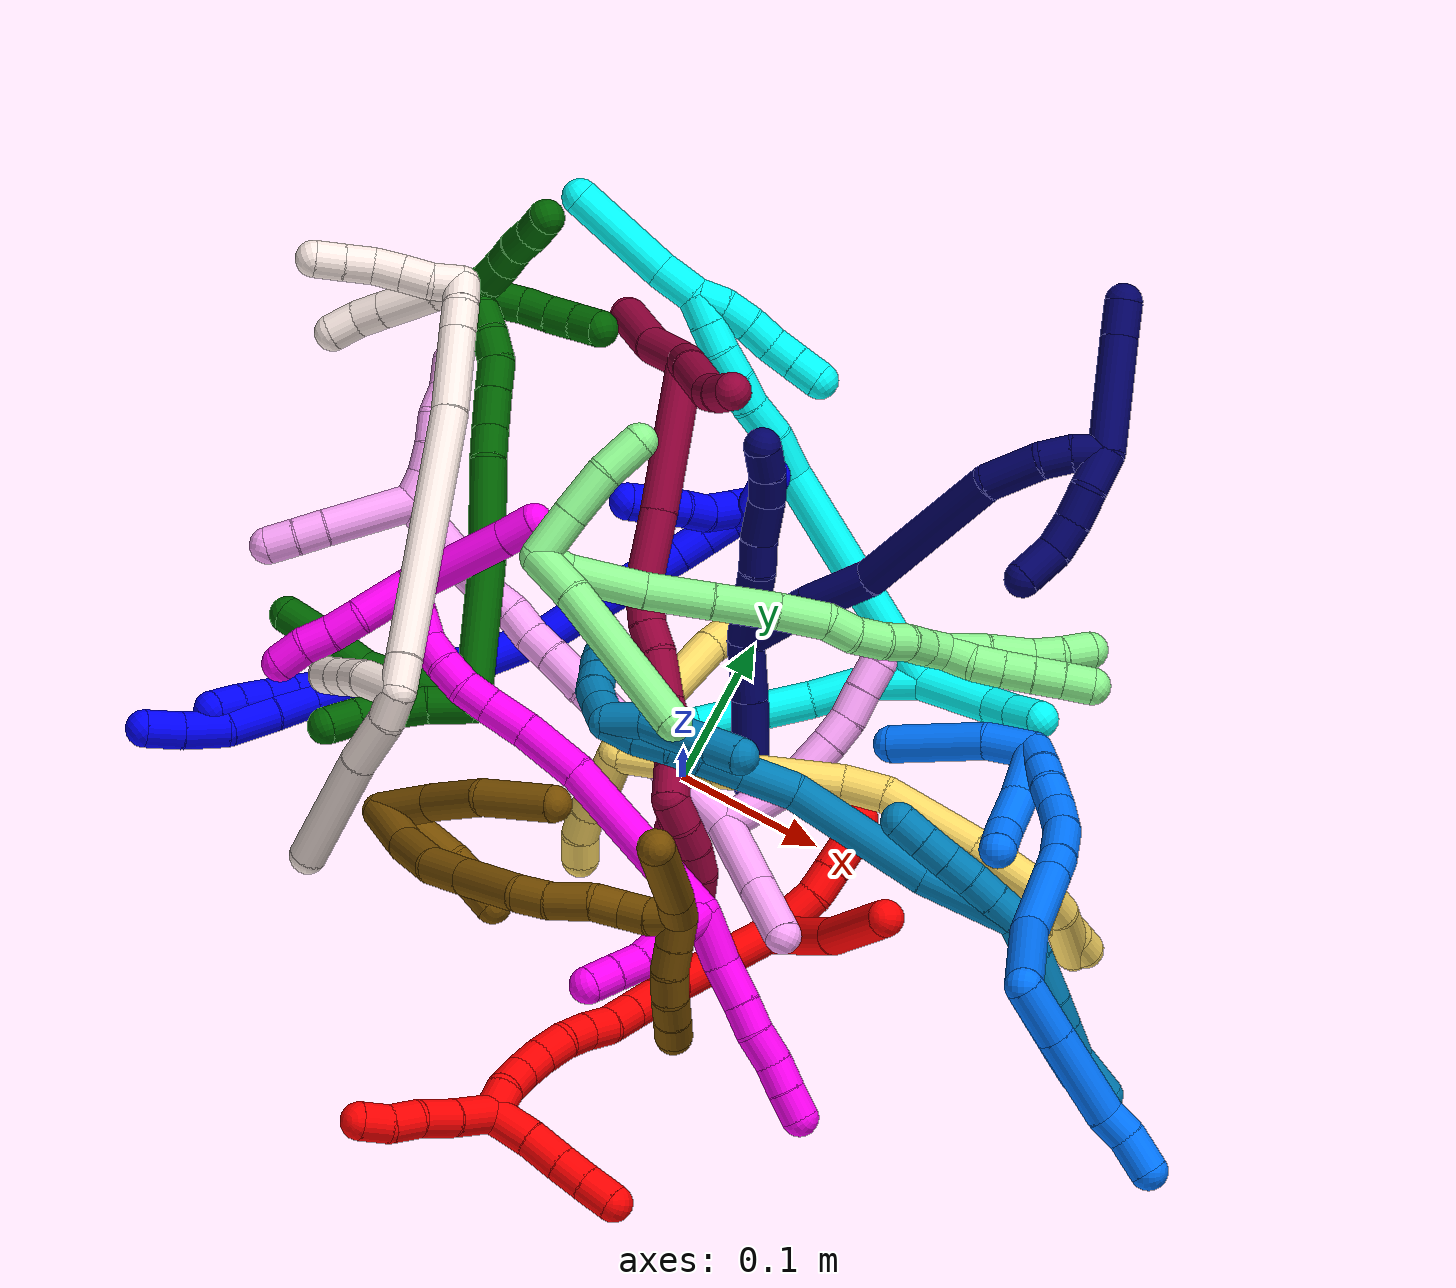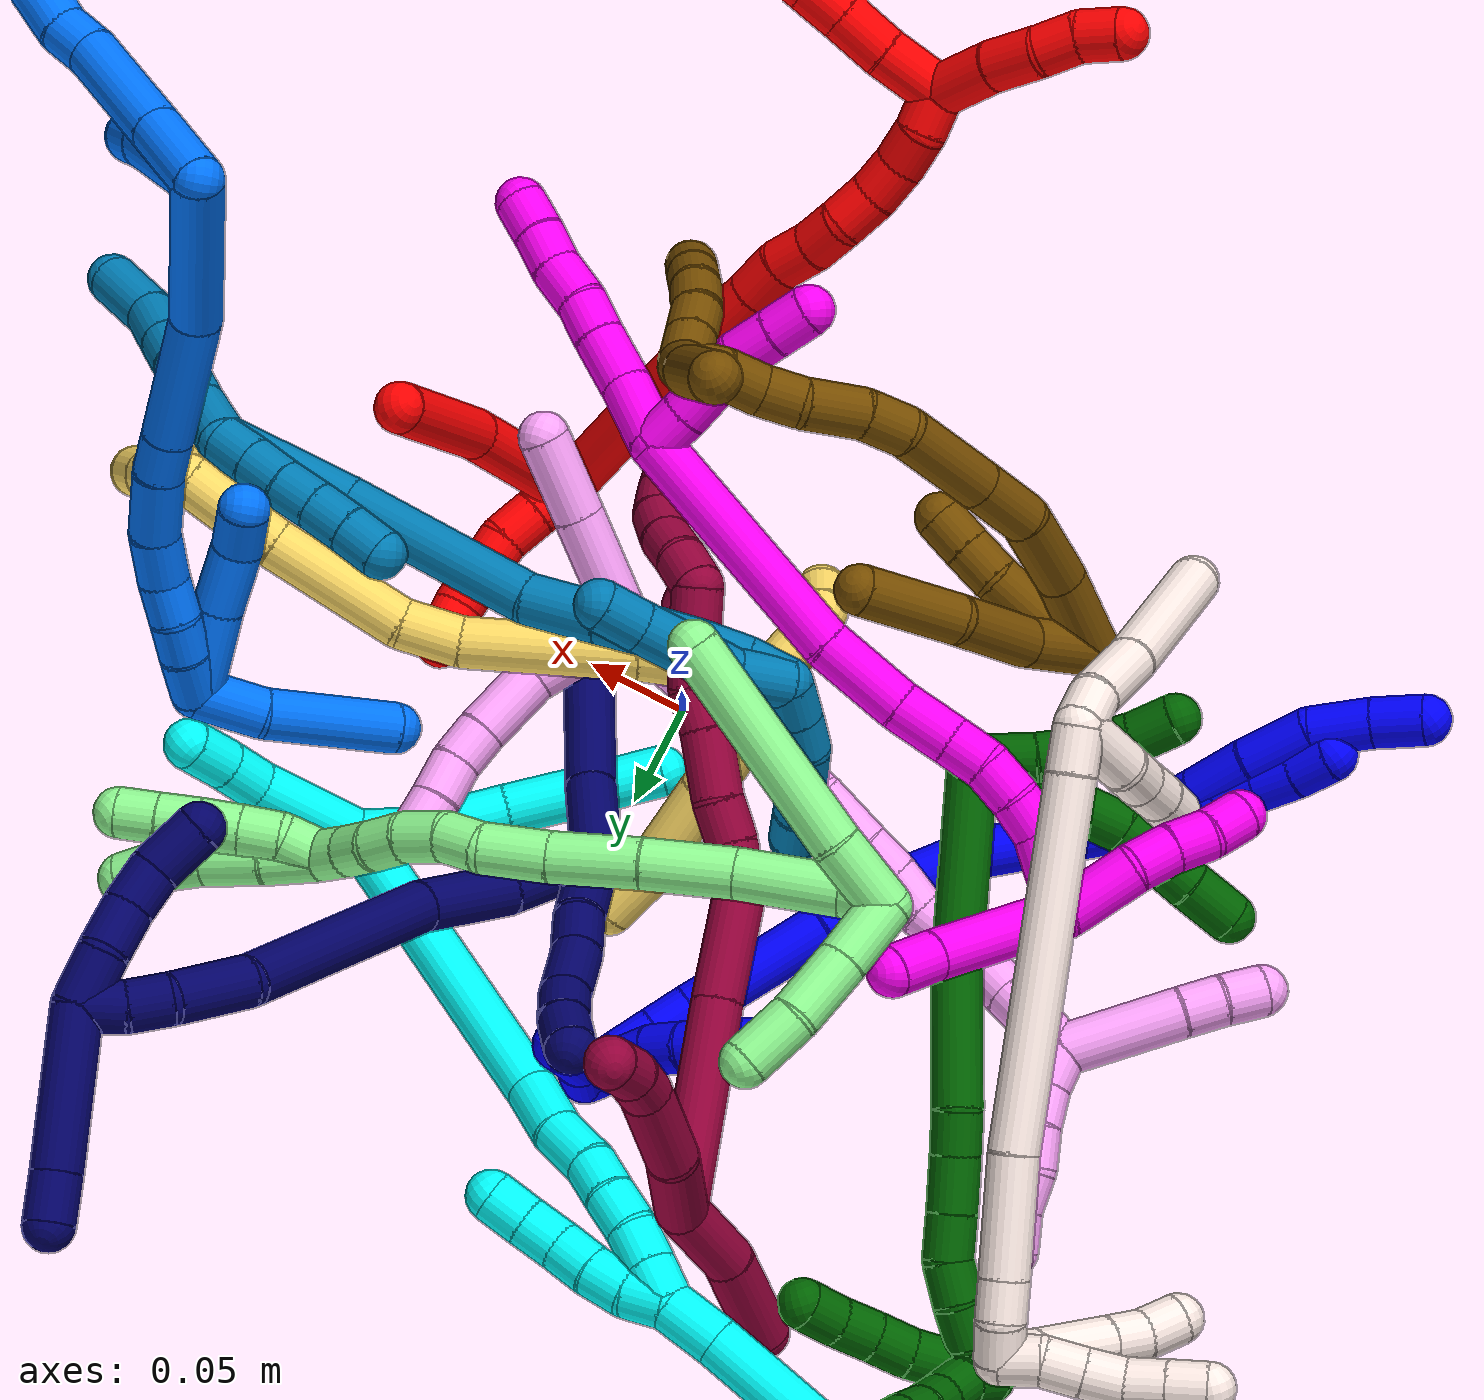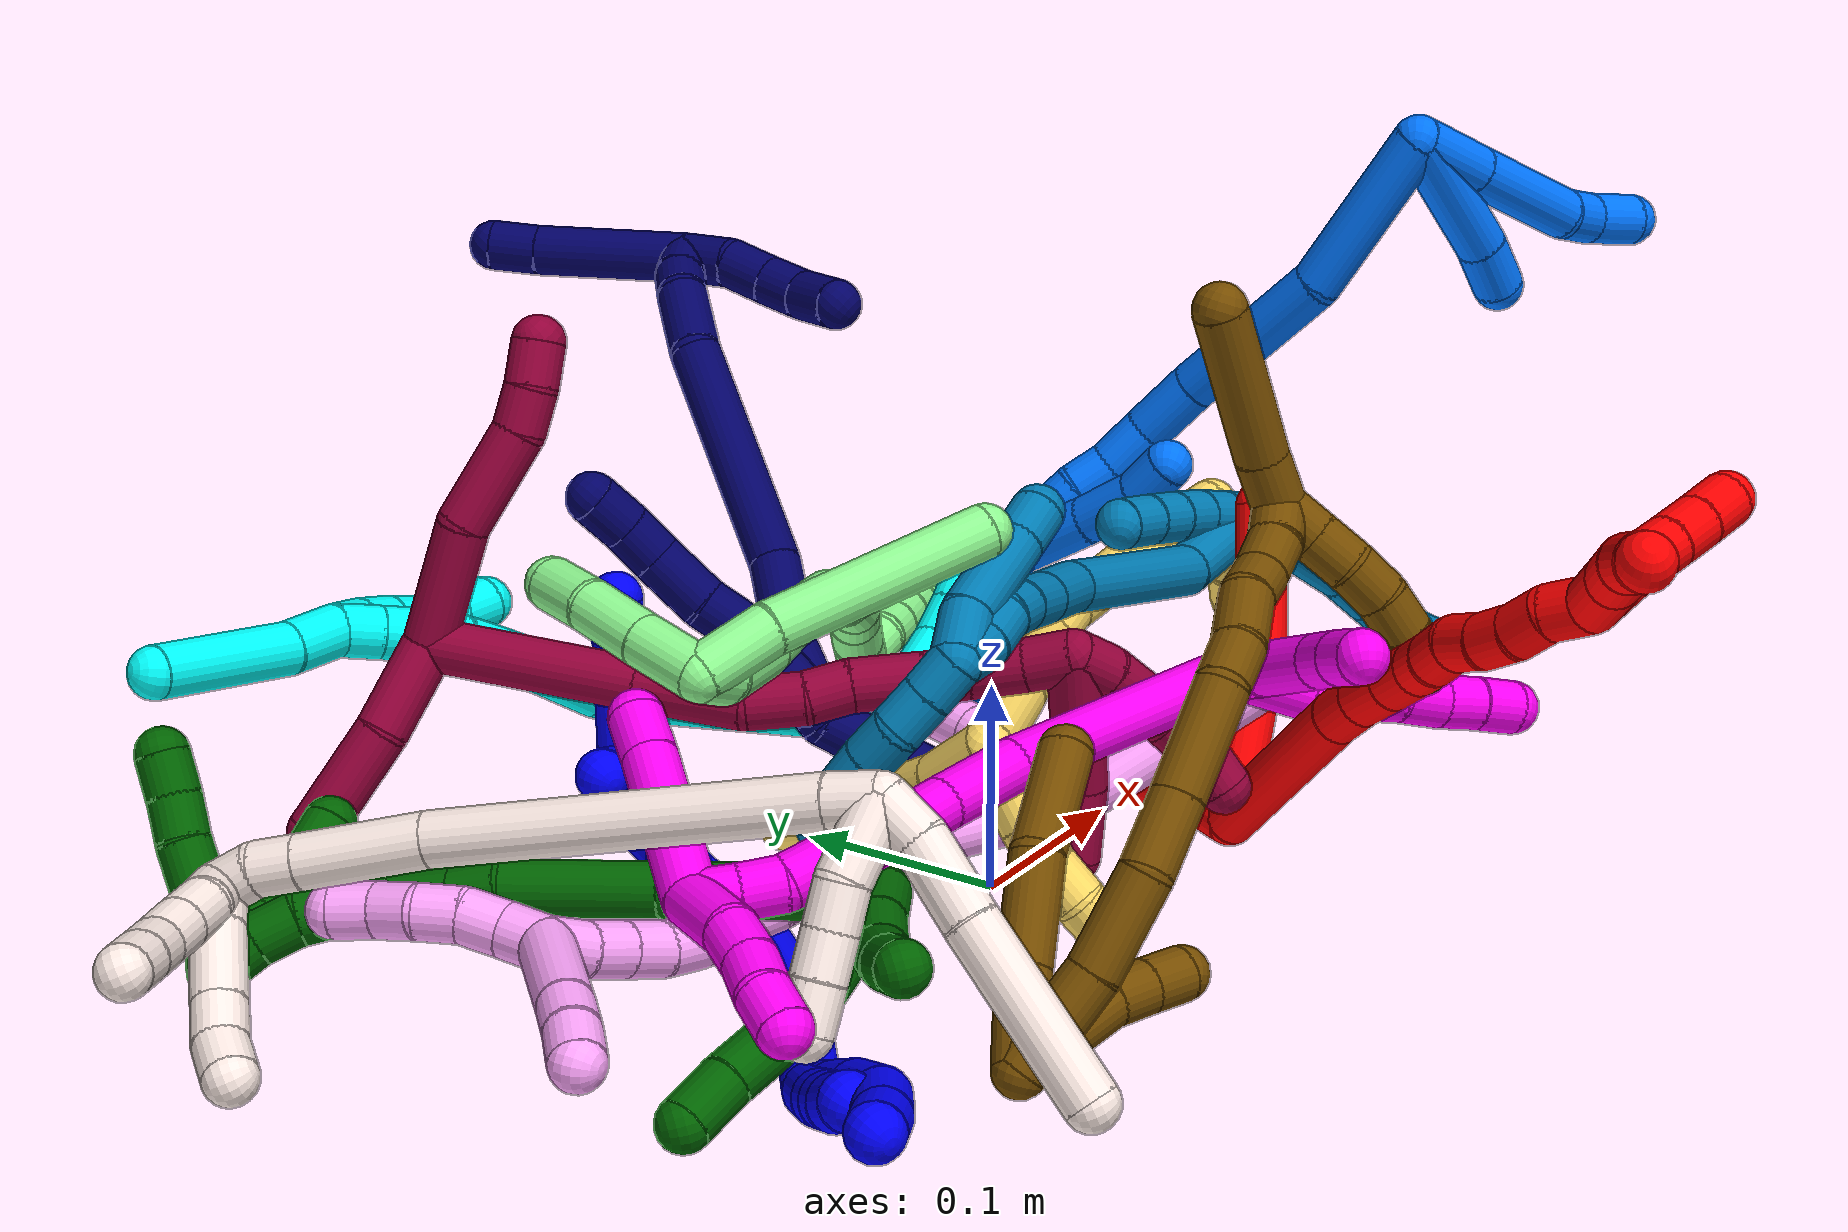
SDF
<sdf version="1.7">
 <world name="default">
  <plugin name="TubeGeneratorPlugin" filename="libtube_generator_plugin.so"/>
  <model name="photoneo_s_sensor">
   <static>1</static>
   <pose>0 0 2 1.57079 1.57079 3.14159</pose>
   <link name="link">
    <inertial><mass>0.1</mass></inertial>
    <sensor name="sensor" type="depth">
     <update_rate>30</update_rate>
     <camera>
      <horizontal_fov>1.22</horizontal_fov>
      <image><width>1920</width><height>1200</height><format>B8G8R8</format></image>
      <clip><near>0.1</near><far>4</far></clip>
      <depth_camera><output>points</output></depth_camera>
     </camera>
     <plugin name="camera_plugin" filename="libgazebo_ros_depth_camera.so">
      <baseline>0.2</baseline>
      <alwaysOn>1</alwaysOn>
      <updateRate>0.0</updateRate>
      <cameraName>camera_ir</cameraName>
      <imageTopicName>/camera/color/image_raw</imageTopicName>
      <cameraInfoTopicName>/camera/color/camera_info</cameraInfoTopicName>
      <depthImageTopicName>/camera/depth/image_raw</depthImageTopicName>
      <depthImageCameraInfoTopicName>/camera/depth/camera_info</depthImageCameraInfoTopicName>
      <pointCloudTopicName>/camera/depth/points</pointCloudTopicName>
      <frameName>fr_optical</frameName>
      <pointCloudCutoff>0.1</pointCloudCutoff>
      <pointCloudCutoffMax>2.0</pointCloudCutoffMax>
      <distortionK1>0</distortionK1>
      <distortionK2>0</distortionK2>
      <distortionK3>0</distortionK3>
      <distortionT1>0</distortionT1>
      <distortionT2>0</distortionT2>
      <CxPrime>0</CxPrime>
      <Cx>0</Cx>
      <Cy>0</Cy>
      <focalLength>0</focalLength>
      <hackBaseline>0</hackBaseline>
     </plugin>
    </sensor>
   </link>
  </model>
  <gravity>0 0 -9.8</gravity>
  <magnetic_field>6e-06 2.3e-05 -4.2e-05</magnetic_field>
  <atmosphere type="adiabatic"/>
  <physics name="default_physics" default="0" type="ode">
   <max_step_size>0.003</max_step_size>
   <real_time_factor>1</real_time_factor>
   <real_time_update_rate>1000</real_time_update_rate>
   <max_contacts>10000</max_contacts>
   <ode>
    <solver>
     <type>quick</type>
     <iters>100</iters>
     <sor>1.3</sor>
     <use_dynamic_moi_rescaling>0</use_dynamic_moi_rescaling>
    </solver>
    <constraints>
     <contact_max_correcting_vel>0</contact_max_correcting_vel>
     <contact_surface_layer>0.001</contact_surface_layer>
     <cfm>0</cfm>
     <erp>0.2</erp>
    </constraints>
   </ode>
  </physics>
  <scene><ambient>0.4 0.4 0.4 1</ambient><background>0.7 0.7 0.7 1</background><shadows>0</shadows></scene>
  <audio><device>default</device></audio>
  <spherical_coordinates>
   <surface_model>EARTH_WGS84</surface_model>
   <latitude_deg>0</latitude_deg>
   <longitude_deg>0</longitude_deg>
   <elevation>0</elevation>
   <heading_deg>0</heading_deg>
  </spherical_coordinates>
  <model name="bin">
   <static>1</static>
   <link name="bottom">
    <collision name="collision-bottom">
     <pose>0 0 -0.01 0 -0 0</pose>
     <geometry><box><size>0.8 0.6 0.02</size></box></geometry>
     <surface>
      <friction><ode><mu>100</mu><mu2>100</mu2></ode></friction>
      <contact><collide_bitmask>65535</collide_bitmask></contact>
     </surface>
    </collision>
   </link>
   <link name="west_wall">
    <collision name="collision-west_wall">
     <pose>-0.41 0 0.1 0 -0 0</pose>
     <geometry><box><size>0.02 0.6 0.2</size></box></geometry>
     <surface>
      <friction><ode><mu>100</mu><mu2>100</mu2></ode></friction>
      <contact><collide_bitmask>65535</collide_bitmask></contact>
     </surface>
    </collision>
   </link>
   <link name="east_wall">
    <collision name="collision-east_wall">
     <pose>0.41 0 0.1 0 -0 0</pose>
     <geometry><box><size>0.02 0.6 0.2</size></box></geometry>
     <surface>
      <friction><ode><mu>100</mu><mu2>100</mu2></ode></friction>
      <contact><collide_bitmask>65535</collide_bitmask></contact>
     </surface>
    </collision>
   </link>
   <link name="south_wall">
    <collision name="collision-south_wall">
     <pose>0 -0.31 0.1 0 -0 0</pose>
     <geometry><box><size>0.8 0.02 0.2</size></box></geometry>
     <surface>
      <friction><ode><mu>100</mu><mu2>100</mu2></ode></friction>
      <contact><collide_bitmask>65535</collide_bitmask></contact>
     </surface>
    </collision>
   </link>
   <link name="north_wall">
    <collision name="collision-north_wall">
     <pose>0 0.31 0.1 0 -0 0</pose>
     <geometry><box><size>0.8 0.02 0.2</size></box></geometry>
     <surface>
      <friction><ode><mu>100</mu><mu2>100</mu2></ode></friction>
      <contact><collide_bitmask>65535</collide_bitmask></contact>
     </surface>
    </collision>
   </link>
  </model>
  <model name="1">
   <static>0</static>
   <link name="1">
    <collision name="collision-cylinder-e_1_2_8">
     <pose>0.00698 -0.004528 -0.012782 2.80111 0.475363 1.90733</pose>
     <geometry><cylinder><radius>0.0125</radius><length>0.030503</length></cylinder></geometry>
     <surface>
      <friction><ode><mu>1.16</mu><mu2>1.16</mu2><slip1>0</slip1><slip2>0</slip2></ode></friction>
      <contact><ode><kp>1e+06</kp><kd>1</kd><max_vel>0</max_vel><min_depth>0.001</min_depth></ode></contact>
     </surface>
    </collision>
    <visual name="visual-cylinder-e_1_2_8">
     <pose>0.00698 -0.004528 -0.012782 2.80111 0.475363 1.90733</pose>
     <geometry><cylinder><radius>0.0125</radius><length>0.030503</length></cylinder></geometry>
     <material><ambient>0 0 1 1</ambient></material>
    </visual>
    <collision name="collision-cylinder-e_2_8_9">
     <pose>0.020922 -0.013339 -0.037979 2.80945 0.487458 1.95542</pose>
     <geometry><cylinder><radius>0.0125</radius><length>0.029727</length></cylinder></geometry>
     <surface>
      <friction><ode><mu>1.16</mu><mu2>1.16</mu2><slip1>0</slip1><slip2>0</slip2></ode></friction>
      <contact><ode><kp>1e+06</kp><kd>1</kd><max_vel>0</max_vel><min_depth>0.001</min_depth></ode></contact>
     </surface>
    </collision>
    <visual name="visual-cylinder-e_2_8_9">
     <pose>0.020922 -0.013339 -0.037979 2.80945 0.487458 1.95542</pose>
     <geometry><cylinder><radius>0.0125</radius><length>0.029727</length></cylinder></geometry>
     <material><ambient>0 0 1 1</ambient></material>
    </visual>
    <collision name="collision-cylinder-e_3_9_10">
     <pose>0.034323 -0.023215 -0.065097 2.77801 0.388492 1.63861</pose>
     <geometry><cylinder><radius>0.0125</radius><length>0.033997</length></cylinder></geometry>
     <surface>
      <friction><ode><mu>1.16</mu><mu2>1.16</mu2><slip1>0</slip1><slip2>0</slip2></ode></friction>
      <contact><ode><kp>1e+06</kp><kd>1</kd><max_vel>0</max_vel><min_depth>0.001</min_depth></ode></contact>
     </surface>
    </collision>
    <visual name="visual-cylinder-e_3_9_10">
     <pose>0.034323 -0.023215 -0.065097 2.77801 0.388492 1.63861</pose>
     <geometry><cylinder><radius>0.0125</radius><length>0.033997</length></cylinder></geometry>
     <material><ambient>0 0 1 1</ambient></material>
    </visual>
    <collision name="collision-cylinder-e_4_10_11">
     <pose>0.043326 -0.037456 -0.091864 2.51977 0.171088 0.521577</pose>
     <geometry><cylinder><radius>0.0125</radius><length>0.030124</length></cylinder></geometry>
     <surface>
      <friction><ode><mu>1.16</mu><mu2>1.16</mu2><slip1>0</slip1><slip2>0</slip2></ode></friction>
      <contact><ode><kp>1e+06</kp><kd>1</kd><max_vel>0</max_vel><min_depth>0.001</min_depth></ode></contact>
     </surface>
    </collision>
    <visual name="visual-cylinder-e_4_10_11">
     <pose>0.043326 -0.037456 -0.091864 2.51977 0.171088 0.521577</pose>
     <geometry><cylinder><radius>0.0125</radius><length>0.030124</length></cylinder></geometry>
     <material><ambient>0 0 1 1</ambient></material>
    </visual>
    <collision name="collision-cylinder-e_5_11_6">
     <pose>0.048329 -0.054527 -0.113283 2.40843 0.191369 0.489927</pose>
     <geometry><cylinder><radius>0.0125</radius><length>0.025649</length></cylinder></geometry>
     <surface>
      <friction><ode><mu>1.16</mu><mu2>1.16</mu2><slip1>0</slip1><slip2>0</slip2></ode></friction>
      <contact><ode><kp>1e+06</kp><kd>1</kd><max_vel>0</max_vel><min_depth>0.001</min_depth></ode></contact>
     </surface>
    </collision>
    <visual name="visual-cylinder-e_5_11_6">
     <pose>0.048329 -0.054527 -0.113283 2.40843 0.191369 0.489927</pose>
     <geometry><cylinder><radius>0.0125</radius><length>0.025649</length></cylinder></geometry>
     <material><ambient>0 0 1 1</ambient></material>
    </visual>
    <collision name="collision-cylinder-e_1_2_12">
     <pose>0.007067 -0.009542 -0.015558 2.59144 0.369441 1.1696</pose>
     <geometry><cylinder><radius>0.0125</radius><length>0.039143</length></cylinder></geometry>
     <surface>
      <friction><ode><mu>1.16</mu><mu2>1.16</mu2><slip1>0</slip1><slip2>0</slip2></ode></friction>
      <contact><ode><kp>1e+06</kp><kd>1</kd><max_vel>0</max_vel><min_depth>0.001</min_depth></ode></contact>
     </surface>
    </collision>
    <visual name="visual-cylinder-e_1_2_12">
     <pose>0.007067 -0.009542 -0.015558 2.59144 0.369441 1.1696</pose>
     <geometry><cylinder><radius>0.0125</radius><length>0.039143</length></cylinder></geometry>
     <material><ambient>0 0 1 1</ambient></material>
    </visual>
    <collision name="collision-cylinder-e_2_12_13">
     <pose>0.018281 -0.023664 -0.039346 2.63373 0.414713 1.36236</pose>
     <geometry><cylinder><radius>0.0125</radius><length>0.020583</length></cylinder></geometry>
     <surface>
      <friction><ode><mu>1.16</mu><mu2>1.16</mu2><slip1>0</slip1><slip2>0</slip2></ode></friction>
      <contact><ode><kp>1e+06</kp><kd>1</kd><max_vel>0</max_vel><min_depth>0.001</min_depth></ode></contact>
     </surface>
    </collision>
    <visual name="visual-cylinder-e_2_12_13">
     <pose>0.018281 -0.023664 -0.039346 2.63373 0.414713 1.36236</pose>
     <geometry><cylinder><radius>0.0125</radius><length>0.020583</length></cylinder></geometry>
     <material><ambient>0 0 1 1</ambient></material>
    </visual>
    <collision name="collision-cylinder-e_3_13_14">
     <pose>0.026483 -0.032716 -0.055605 2.63348 0.415624 1.36406</pose>
     <geometry><cylinder><radius>0.0125</radius><length>0.02009</length></cylinder></geometry>
     <surface>
      <friction><ode><mu>1.16</mu><mu2>1.16</mu2><slip1>0</slip1><slip2>0</slip2></ode></friction>
      <contact><ode><kp>1e+06</kp><kd>1</kd><max_vel>0</max_vel><min_depth>0.001</min_depth></ode></contact>
     </surface>
    </collision>
    <visual name="visual-cylinder-e_3_13_14">
     <pose>0.026483 -0.032716 -0.055605 2.63348 0.415624 1.36406</pose>
     <geometry><cylinder><radius>0.0125</radius><length>0.02009</length></cylinder></geometry>
     <material><ambient>0 0 1 1</ambient></material>
    </visual>
    <collision name="collision-cylinder-e_4_14_5">
     <pose>0.03536 -0.040897 -0.071687 2.70984 0.497994 1.71826</pose>
     <geometry><cylinder><radius>0.0125</radius><length>0.020184</length></cylinder></geometry>
     <surface>
      <friction><ode><mu>1.16</mu><mu2>1.16</mu2><slip1>0</slip1><slip2>0</slip2></ode></friction>
      <contact><ode><kp>1e+06</kp><kd>1</kd><max_vel>0</max_vel><min_depth>0.001</min_depth></ode></contact>
     </surface>
    </collision>
    <visual name="visual-cylinder-e_4_14_5">
     <pose>0.03536 -0.040897 -0.071687 2.70984 0.497994 1.71826</pose>
     <geometry><cylinder><radius>0.0125</radius><length>0.020184</length></cylinder></geometry>
     <material><ambient>0 0 1 1</ambient></material>
    </visual>
    <collision name="collision-cylinder-e_1_2_15">
     <pose>0.002152 0.019635 0.036551 -0.492946 0.051828 -0.013042</pose>
     <geometry><cylinder><radius>0.0125</radius><length>0.083094</length></cylinder></geometry>
     <surface>
      <friction><ode><mu>1.16</mu><mu2>1.16</mu2><slip1>0</slip1><slip2>0</slip2></ode></friction>
      <contact><ode><kp>1e+06</kp><kd>1</kd><max_vel>0</max_vel><min_depth>0.001</min_depth></ode></contact>
     </surface>
    </collision>
    <visual name="visual-cylinder-e_1_2_15">
     <pose>0.002152 0.019635 0.036551 -0.492946 0.051828 -0.013042</pose>
     <geometry><cylinder><radius>0.0125</radius><length>0.083094</length></cylinder></geometry>
     <material><ambient>0 0 1 1</ambient></material>
    </visual>
    <collision name="collision-cylinder-e_2_15_16">
     <pose>0.003645 0.047337 0.098839 -0.303772 -0.024464 0.003745</pose>
     <geometry><cylinder><radius>0.0125</radius><length>0.053959</length></cylinder></geometry>
     <surface>
      <friction><ode><mu>1.16</mu><mu2>1.16</mu2><slip1>0</slip1><slip2>0</slip2></ode></friction>
      <contact><ode><kp>1e+06</kp><kd>1</kd><max_vel>0</max_vel><min_depth>0.001</min_depth></ode></contact>
     </surface>
    </collision>
    <visual name="visual-cylinder-e_2_15_16">
     <pose>0.003645 0.047337 0.098839 -0.303772 -0.024464 0.003745</pose>
     <geometry><cylinder><radius>0.0125</radius><length>0.053959</length></cylinder></geometry>
     <material><ambient>0 0 1 1</ambient></material>
    </visual>
    <collision name="collision-cylinder-e_3_16_17">
     <pose>0.003346 0.05669 0.138818 -0.090021 0.025286 -0.001139</pose>
     <geometry><cylinder><radius>0.0125</radius><length>0.02861</length></cylinder></geometry>
     <surface>
      <friction><ode><mu>1.16</mu><mu2>1.16</mu2><slip1>0</slip1><slip2>0</slip2></ode></friction>
      <contact><ode><kp>1e+06</kp><kd>1</kd><max_vel>0</max_vel><min_depth>0.001</min_depth></ode></contact>
     </surface>
    </collision>
    <visual name="visual-cylinder-e_3_16_17">
     <pose>0.003346 0.05669 0.138818 -0.090021 0.025286 -0.001139</pose>
     <geometry><cylinder><radius>0.0125</radius><length>0.02861</length></cylinder></geometry>
     <material><ambient>0 0 1 1</ambient></material>
    </visual>
    <collision name="collision-cylinder-e_4_17_18">
     <pose>0.002126 0.061548 0.178844 -0.137662 -0.060717 0.004187</pose>
     <geometry><cylinder><radius>0.0125</radius><length>0.052155</length></cylinder></geometry>
     <surface>
      <friction><ode><mu>1.16</mu><mu2>1.16</mu2><slip1>0</slip1><slip2>0</slip2></ode></friction>
      <contact><ode><kp>1e+06</kp><kd>1</kd><max_vel>0</max_vel><min_depth>0.001</min_depth></ode></contact>
     </surface>
    </collision>
    <visual name="visual-cylinder-e_4_17_18">
     <pose>0.002126 0.061548 0.178844 -0.137662 -0.060717 0.004187</pose>
     <geometry><cylinder><radius>0.0125</radius><length>0.052155</length></cylinder></geometry>
     <material><ambient>0 0 1 1</ambient></material>
    </visual>
    <collision name="collision-cylinder-e_5_18_19">
     <pose>2.4e-05 0.06665 0.215385 -0.141323 -0.047794 0.003384</pose>
     <geometry><cylinder><radius>0.0125</radius><length>0.021758</length></cylinder></geometry>
     <surface>
      <friction><ode><mu>1.16</mu><mu2>1.16</mu2><slip1>0</slip1><slip2>0</slip2></ode></friction>
      <contact><ode><kp>1e+06</kp><kd>1</kd><max_vel>0</max_vel><min_depth>0.001</min_depth></ode></contact>
     </surface>
    </collision>
    <visual name="visual-cylinder-e_5_18_19">
     <pose>2.4e-05 0.06665 0.215385 -0.141323 -0.047794 0.003384</pose>
     <geometry><cylinder><radius>0.0125</radius><length>0.021758</length></cylinder></geometry>
     <material><ambient>0 0 1 1</ambient></material>
    </visual>
    <collision name="collision-cylinder-e_6_19_20">
     <pose>-0.000642 0.069219 0.236184 -0.102981 -0.014398 0.000742</pose>
     <geometry><cylinder><radius>0.0125</radius><length>0.020191</length></cylinder></geometry>
     <surface>
      <friction><ode><mu>1.16</mu><mu2>1.16</mu2><slip1>0</slip1><slip2>0</slip2></ode></friction>
      <contact><ode><kp>1e+06</kp><kd>1</kd><max_vel>0</max_vel><min_depth>0.001</min_depth></ode></contact>
     </surface>
    </collision>
    <visual name="visual-cylinder-e_6_19_20">
     <pose>-0.000642 0.069219 0.236184 -0.102981 -0.014398 0.000742</pose>
     <geometry><cylinder><radius>0.0125</radius><length>0.020191</length></cylinder></geometry>
     <material><ambient>0 0 1 1</ambient></material>
    </visual>
    <collision name="collision-cylinder-e_7_20_21">
     <pose>-0.000924 0.071263 0.256288 -0.099674 -0.013514 0.000674</pose>
     <geometry><cylinder><radius>0.0125</radius><length>0.020227</length></cylinder></geometry>
     <surface>
      <friction><ode><mu>1.16</mu><mu2>1.16</mu2><slip1>0</slip1><slip2>0</slip2></ode></friction>
      <contact><ode><kp>1e+06</kp><kd>1</kd><max_vel>0</max_vel><min_depth>0.001</min_depth></ode></contact>
     </surface>
    </collision>
    <visual name="visual-cylinder-e_7_20_21">
     <pose>-0.000924 0.071263 0.256288 -0.099674 -0.013514 0.000674</pose>
     <geometry><cylinder><radius>0.0125</radius><length>0.020227</length></cylinder></geometry>
     <material><ambient>0 0 1 1</ambient></material>
    </visual>
    <collision name="collision-cylinder-e_8_21_1">
     <pose>-0.000999 0.073143 0.276315 -0.087471 0.006148 -0.000269</pose>
     <geometry><cylinder><radius>0.0125</radius><length>0.020006</length></cylinder></geometry>
     <surface>
      <friction><ode><mu>1.16</mu><mu2>1.16</mu2><slip1>0</slip1><slip2>0</slip2></ode></friction>
      <contact><ode><kp>1e+06</kp><kd>1</kd><max_vel>0</max_vel><min_depth>0.001</min_depth></ode></contact>
     </surface>
    </collision>
    <visual name="visual-cylinder-e_8_21_1">
     <pose>-0.000999 0.073143 0.276315 -0.087471 0.006148 -0.000269</pose>
     <geometry><cylinder><radius>0.0125</radius><length>0.020006</length></cylinder></geometry>
     <material><ambient>0 0 1 1</ambient></material>
    </visual>
    <collision name="collision-cylinder-e_1_1_22">
     <pose>0.013018 0.073379 0.286531 1.19528 1.52177 1.15007</pose>
     <geometry><cylinder><radius>0.0125</radius><length>0.027944</length></cylinder></geometry>
     <surface>
      <friction><ode><mu>1.16</mu><mu2>1.16</mu2><slip1>0</slip1><slip2>0</slip2></ode></friction>
      <contact><ode><kp>1e+06</kp><kd>1</kd><max_vel>0</max_vel><min_depth>0.001</min_depth></ode></contact>
     </surface>
    </collision>
    <visual name="visual-cylinder-e_1_1_22">
     <pose>0.013018 0.073379 0.286531 1.19528 1.52177 1.15007</pose>
     <geometry><cylinder><radius>0.0125</radius><length>0.027944</length></cylinder></geometry>
     <material><ambient>0 0 1 1</ambient></material>
    </visual>
    <collision name="collision-cylinder-e_2_22_4">
     <pose>0.061955 0.067011 0.293221 0.727371 1.32919 0.579629</pose>
     <geometry><cylinder><radius>0.0125</radius><length>0.072056</length></cylinder></geometry>
     <surface>
      <friction><ode><mu>1.16</mu><mu2>1.16</mu2><slip1>0</slip1><slip2>0</slip2></ode></friction>
      <contact><ode><kp>1e+06</kp><kd>1</kd><max_vel>0</max_vel><min_depth>0.001</min_depth></ode></contact>
     </surface>
    </collision>
    <visual name="visual-cylinder-e_2_22_4">
     <pose>0.061955 0.067011 0.293221 0.727371 1.32919 0.579629</pose>
     <geometry><cylinder><radius>0.0125</radius><length>0.072056</length></cylinder></geometry>
     <material><ambient>0 0 1 1</ambient></material>
    </visual>
    <collision name="collision-cylinder-e_1_1_23">
     <pose>0.003969 0.069859 0.278622 2.64427 0.512814 1.60282</pose>
     <geometry><cylinder><radius>0.0125</radius><length>0.02</length></cylinder></geometry>
     <surface>
      <friction><ode><mu>1.16</mu><mu2>1.16</mu2><slip1>0</slip1><slip2>0</slip2></ode></friction>
      <contact><ode><kp>1e+06</kp><kd>1</kd><max_vel>0</max_vel><min_depth>0.001</min_depth></ode></contact>
     </surface>
    </collision>
    <visual name="visual-cylinder-e_1_1_23">
     <pose>0.003969 0.069859 0.278622 2.64427 0.512814 1.60282</pose>
     <geometry><cylinder><radius>0.0125</radius><length>0.02</length></cylinder></geometry>
     <material><ambient>0 0 1 1</ambient></material>
    </visual>
    <collision name="collision-cylinder-e_2_23_24">
     <pose>0.014046 0.061502 0.263505 2.62862 0.543367 1.6311</pose>
     <geometry><cylinder><radius>0.0125</radius><length>0.02</length></cylinder></geometry>
     <surface>
      <friction><ode><mu>1.16</mu><mu2>1.16</mu2><slip1>0</slip1><slip2>0</slip2></ode></friction>
      <contact><ode><kp>1e+06</kp><kd>1</kd><max_vel>0</max_vel><min_depth>0.001</min_depth></ode></contact>
     </surface>
    </collision>
    <visual name="visual-cylinder-e_2_23_24">
     <pose>0.014046 0.061502 0.263505 2.62862 0.543367 1.6311</pose>
     <geometry><cylinder><radius>0.0125</radius><length>0.02</length></cylinder></geometry>
     <material><ambient>0 0 1 1</ambient></material>
    </visual>
    <collision name="collision-cylinder-e_3_24_25">
     <pose>0.024694 0.050972 0.250576 2.28369 0.579798 1.15589</pose>
     <geometry><cylinder><radius>0.0125</radius><length>0.02</length></cylinder></geometry>
     <surface>
      <friction><ode><mu>1.16</mu><mu2>1.16</mu2><slip1>0</slip1><slip2>0</slip2></ode></friction>
      <contact><ode><kp>1e+06</kp><kd>1</kd><max_vel>0</max_vel><min_depth>0.001</min_depth></ode></contact>
     </surface>
    </collision>
    <visual name="visual-cylinder-e_3_24_25">
     <pose>0.024694 0.050972 0.250576 2.28369 0.579798 1.15589</pose>
     <geometry><cylinder><radius>0.0125</radius><length>0.02</length></cylinder></geometry>
     <material><ambient>0 0 1 1</ambient></material>
    </visual>
    <collision name="collision-cylinder-e_4_25_26">
     <pose>0.034507 0.038251 0.238753 2.35291 0.448312 1.0024</pose>
     <geometry><cylinder><radius>0.0125</radius><length>0.02</length></cylinder></geometry>
     <surface>
      <friction><ode><mu>1.16</mu><mu2>1.16</mu2><slip1>0</slip1><slip2>0</slip2></ode></friction>
      <contact><ode><kp>1e+06</kp><kd>1</kd><max_vel>0</max_vel><min_depth>0.001</min_depth></ode></contact>
     </surface>
    </collision>
    <visual name="visual-cylinder-e_4_25_26">
     <pose>0.034507 0.038251 0.238753 2.35291 0.448312 1.0024</pose>
     <geometry><cylinder><radius>0.0125</radius><length>0.02</length></cylinder></geometry>
     <material><ambient>0 0 1 1</ambient></material>
    </visual>
    <collision name="collision-cylinder-e_5_26_3">
     <pose>0.041371 0.024913 0.225665 2.34101 0.25573 0.589956</pose>
     <geometry><cylinder><radius>0.0125</radius><length>0.02</length></cylinder></geometry>
     <surface>
      <friction><ode><mu>1.16</mu><mu2>1.16</mu2><slip1>0</slip1><slip2>0</slip2></ode></friction>
      <contact><ode><kp>1e+06</kp><kd>1</kd><max_vel>0</max_vel><min_depth>0.001</min_depth></ode></contact>
     </surface>
    </collision>
    <visual name="visual-cylinder-e_5_26_3">
     <pose>0.041371 0.024913 0.225665 2.34101 0.25573 0.589956</pose>
     <geometry><cylinder><radius>0.0125</radius><length>0.02</length></cylinder></geometry>
     <material><ambient>0 0 1 1</ambient></material>
    </visual>
    <collision name="collision-sphere-3">
     <pose>0.043901 0.017969 0.218929 0 -0 0</pose>
     <geometry><sphere><radius>0.0125</radius></sphere></geometry>
     <surface>
      <friction><ode><mu>1.16</mu><mu2>1.16</mu2><slip1>0</slip1><slip2>0</slip2></ode></friction>
      <contact><ode><kp>1e+06</kp><kd>1</kd><max_vel>0</max_vel><min_depth>0.001</min_depth></ode></contact>
     </surface>
    </collision>
    <visual name="visual-sphere-3">
     <pose>0.043901 0.017969 0.218929 0 -0 0</pose>
     <geometry><sphere><radius>0.0125</radius></sphere></geometry>
     <material><ambient>0 0 1 1</ambient></material>
    </visual>
    <collision name="collision-sphere-26">
     <pose>0.038842 0.031857 0.232402 0 -0 0</pose>
     <geometry><sphere><radius>0.0125</radius></sphere></geometry>
     <surface>
      <friction><ode><mu>1.16</mu><mu2>1.16</mu2><slip1>0</slip1><slip2>0</slip2></ode></friction>
      <contact><ode><kp>1e+06</kp><kd>1</kd><max_vel>0</max_vel><min_depth>0.001</min_depth></ode></contact>
     </surface>
    </collision>
    <visual name="visual-sphere-26">
     <pose>0.038842 0.031857 0.232402 0 -0 0</pose>
     <geometry><sphere><radius>0.0125</radius></sphere></geometry>
     <material><ambient>0 0 1 1</ambient></material>
    </visual>
    <collision name="collision-sphere-25">
     <pose>0.030173 0.044644 0.245105 0 -0 0</pose>
     <geometry><sphere><radius>0.0125</radius></sphere></geometry>
     <surface>
      <friction><ode><mu>1.16</mu><mu2>1.16</mu2><slip1>0</slip1><slip2>0</slip2></ode></friction>
      <contact><ode><kp>1e+06</kp><kd>1</kd><max_vel>0</max_vel><min_depth>0.001</min_depth></ode></contact>
     </surface>
    </collision>
    <visual name="visual-sphere-25">
     <pose>0.030173 0.044644 0.245105 0 -0 0</pose>
     <geometry><sphere><radius>0.0125</radius></sphere></geometry>
     <material><ambient>0 0 1 1</ambient></material>
    </visual>
    <collision name="collision-sphere-24">
     <pose>0.019216 0.057301 0.256047 0 -0 0</pose>
     <geometry><sphere><radius>0.0125</radius></sphere></geometry>
     <surface>
      <friction><ode><mu>1.16</mu><mu2>1.16</mu2><slip1>0</slip1><slip2>0</slip2></ode></friction>
      <contact><ode><kp>1e+06</kp><kd>1</kd><max_vel>0</max_vel><min_depth>0.001</min_depth></ode></contact>
     </surface>
    </collision>
    <visual name="visual-sphere-24">
     <pose>0.019216 0.057301 0.256047 0 -0 0</pose>
     <geometry><sphere><radius>0.0125</radius></sphere></geometry>
     <material><ambient>0 0 1 1</ambient></material>
    </visual>
    <collision name="collision-sphere-23">
     <pose>0.008875 0.065702 0.270963 0 -0 0</pose>
     <geometry><sphere><radius>0.0125</radius></sphere></geometry>
     <surface>
      <friction><ode><mu>1.16</mu><mu2>1.16</mu2><slip1>0</slip1><slip2>0</slip2></ode></friction>
      <contact><ode><kp>1e+06</kp><kd>1</kd><max_vel>0</max_vel><min_depth>0.001</min_depth></ode></contact>
     </surface>
    </collision>
    <visual name="visual-sphere-23">
     <pose>0.008875 0.065702 0.270963 0 -0 0</pose>
     <geometry><sphere><radius>0.0125</radius></sphere></geometry>
     <material><ambient>0 0 1 1</ambient></material>
    </visual>
    <collision name="collision-sphere-4">
     <pose>0.096936 0.061279 0.299659 0 -0 0</pose>
     <geometry><sphere><radius>0.0125</radius></sphere></geometry>
     <surface>
      <friction><ode><mu>1.16</mu><mu2>1.16</mu2><slip1>0</slip1><slip2>0</slip2></ode></friction>
      <contact><ode><kp>1e+06</kp><kd>1</kd><max_vel>0</max_vel><min_depth>0.001</min_depth></ode></contact>
     </surface>
    </collision>
    <visual name="visual-sphere-4">
     <pose>0.096936 0.061279 0.299659 0 -0 0</pose>
     <geometry><sphere><radius>0.0125</radius></sphere></geometry>
     <material><ambient>0 0 1 1</ambient></material>
    </visual>
    <collision name="collision-sphere-22">
     <pose>0.026973 0.072742 0.286782 0 -0 0</pose>
     <geometry><sphere><radius>0.0125</radius></sphere></geometry>
     <surface>
      <friction><ode><mu>1.16</mu><mu2>1.16</mu2><slip1>0</slip1><slip2>0</slip2></ode></friction>
      <contact><ode><kp>1e+06</kp><kd>1</kd><max_vel>0</max_vel><min_depth>0.001</min_depth></ode></contact>
     </surface>
    </collision>
    <visual name="visual-sphere-22">
     <pose>0.026973 0.072742 0.286782 0 -0 0</pose>
     <geometry><sphere><radius>0.0125</radius></sphere></geometry>
     <material><ambient>0 0 1 1</ambient></material>
    </visual>
    <collision name="collision-sphere-1">
     <pose>-0.000937 0.074017 0.28628 0 -0 0</pose>
     <geometry><sphere><radius>0.0125</radius></sphere></geometry>
     <surface>
      <friction><ode><mu>1.16</mu><mu2>1.16</mu2><slip1>0</slip1><slip2>0</slip2></ode></friction>
      <contact><ode><kp>1e+06</kp><kd>1</kd><max_vel>0</max_vel><min_depth>0.001</min_depth></ode></contact>
     </surface>
    </collision>
    <visual name="visual-sphere-1">
     <pose>-0.000937 0.074017 0.28628 0 -0 0</pose>
     <geometry><sphere><radius>0.0125</radius></sphere></geometry>
     <material><ambient>0 0 1 1</ambient></material>
    </visual>
    <collision name="collision-sphere-21">
     <pose>-0.00106 0.072269 0.266351 0 -0 0</pose>
     <geometry><sphere><radius>0.0125</radius></sphere></geometry>
     <surface>
      <friction><ode><mu>1.16</mu><mu2>1.16</mu2><slip1>0</slip1><slip2>0</slip2></ode></friction>
      <contact><ode><kp>1e+06</kp><kd>1</kd><max_vel>0</max_vel><min_depth>0.001</min_depth></ode></contact>
     </surface>
    </collision>
    <visual name="visual-sphere-21">
     <pose>-0.00106 0.072269 0.266351 0 -0 0</pose>
     <geometry><sphere><radius>0.0125</radius></sphere></geometry>
     <material><ambient>0 0 1 1</ambient></material>
    </visual>
    <collision name="collision-sphere-6">
     <pose>0.050769 -0.062953 -0.122639 0 -0 0</pose>
     <geometry><sphere><radius>0.0125</radius></sphere></geometry>
     <surface>
      <friction><ode><mu>1.16</mu><mu2>1.16</mu2><slip1>0</slip1><slip2>0</slip2></ode></friction>
      <contact><ode><kp>1e+06</kp><kd>1</kd><max_vel>0</max_vel><min_depth>0.001</min_depth></ode></contact>
     </surface>
    </collision>
    <visual name="visual-sphere-6">
     <pose>0.050769 -0.062953 -0.122639 0 -0 0</pose>
     <geometry><sphere><radius>0.0125</radius></sphere></geometry>
     <material><ambient>0 0 1 1</ambient></material>
    </visual>
    <collision name="collision-sphere-11">
     <pose>0.04589 -0.046102 -0.103928 0 -0 0</pose>
     <geometry><sphere><radius>0.0125</radius></sphere></geometry>
     <surface>
      <friction><ode><mu>1.16</mu><mu2>1.16</mu2><slip1>0</slip1><slip2>0</slip2></ode></friction>
      <contact><ode><kp>1e+06</kp><kd>1</kd><max_vel>0</max_vel><min_depth>0.001</min_depth></ode></contact>
     </surface>
    </collision>
    <visual name="visual-sphere-11">
     <pose>0.04589 -0.046102 -0.103928 0 -0 0</pose>
     <geometry><sphere><radius>0.0125</radius></sphere></geometry>
     <material><ambient>0 0 1 1</ambient></material>
    </visual>
    <collision name="collision-sphere-10">
     <pose>0.040761 -0.02881 -0.0798 0 -0 0</pose>
     <geometry><sphere><radius>0.0125</radius></sphere></geometry>
     <surface>
      <friction><ode><mu>1.16</mu><mu2>1.16</mu2><slip1>0</slip1><slip2>0</slip2></ode></friction>
      <contact><ode><kp>1e+06</kp><kd>1</kd><max_vel>0</max_vel><min_depth>0.001</min_depth></ode></contact>
     </surface>
    </collision>
    <visual name="visual-sphere-10">
     <pose>0.040761 -0.02881 -0.0798 0 -0 0</pose>
     <geometry><sphere><radius>0.0125</radius></sphere></geometry>
     <material><ambient>0 0 1 1</ambient></material>
    </visual>
    <collision name="collision-sphere-9">
     <pose>0.027884 -0.017621 -0.050394 0 -0 0</pose>
     <geometry><sphere><radius>0.0125</radius></sphere></geometry>
     <surface>
      <friction><ode><mu>1.16</mu><mu2>1.16</mu2><slip1>0</slip1><slip2>0</slip2></ode></friction>
      <contact><ode><kp>1e+06</kp><kd>1</kd><max_vel>0</max_vel><min_depth>0.001</min_depth></ode></contact>
     </surface>
    </collision>
    <visual name="visual-sphere-9">
     <pose>0.027884 -0.017621 -0.050394 0 -0 0</pose>
     <geometry><sphere><radius>0.0125</radius></sphere></geometry>
     <material><ambient>0 0 1 1</ambient></material>
    </visual>
    <collision name="collision-sphere-2">
     <geometry><sphere><radius>0.0125</radius></sphere></geometry>
     <surface>
      <friction><ode><mu>1.16</mu><mu2>1.16</mu2><slip1>0</slip1><slip2>0</slip2></ode></friction>
      <contact><ode><kp>1e+06</kp><kd>1</kd><max_vel>0</max_vel><min_depth>0.001</min_depth></ode></contact>
     </surface>
    </collision>
    <visual name="visual-sphere-2">
     <geometry><sphere><radius>0.0125</radius></sphere></geometry>
     <material><ambient>0 0 1 1</ambient></material>
    </visual>
    <collision name="collision-sphere-19">
     <pose>-0.000496 0.068181 0.226143 0 -0 0</pose>
     <geometry><sphere><radius>0.0125</radius></sphere></geometry>
     <surface>
      <friction><ode><mu>1.16</mu><mu2>1.16</mu2><slip1>0</slip1><slip2>0</slip2></ode></friction>
      <contact><ode><kp>1e+06</kp><kd>1</kd><max_vel>0</max_vel><min_depth>0.001</min_depth></ode></contact>
     </surface>
    </collision>
    <visual name="visual-sphere-19">
     <pose>-0.000496 0.068181 0.226143 0 -0 0</pose>
     <geometry><sphere><radius>0.0125</radius></sphere></geometry>
     <material><ambient>0 0 1 1</ambient></material>
    </visual>
    <collision name="collision-sphere-8">
     <pose>0.01396 -0.009057 -0.025564 0 -0 0</pose>
     <geometry><sphere><radius>0.0125</radius></sphere></geometry>
     <surface>
      <friction><ode><mu>1.16</mu><mu2>1.16</mu2><slip1>0</slip1><slip2>0</slip2></ode></friction>
      <contact><ode><kp>1e+06</kp><kd>1</kd><max_vel>0</max_vel><min_depth>0.001</min_depth></ode></contact>
     </surface>
    </collision>
    <visual name="visual-sphere-8">
     <pose>0.01396 -0.009057 -0.025564 0 -0 0</pose>
     <geometry><sphere><radius>0.0125</radius></sphere></geometry>
     <material><ambient>0 0 1 1</ambient></material>
    </visual>
    <collision name="collision-sphere-12">
     <pose>0.014134 -0.019084 -0.031116 0 -0 0</pose>
     <geometry><sphere><radius>0.0125</radius></sphere></geometry>
     <surface>
      <friction><ode><mu>1.16</mu><mu2>1.16</mu2><slip1>0</slip1><slip2>0</slip2></ode></friction>
      <contact><ode><kp>1e+06</kp><kd>1</kd><max_vel>0</max_vel><min_depth>0.001</min_depth></ode></contact>
     </surface>
    </collision>
    <visual name="visual-sphere-12">
     <pose>0.014134 -0.019084 -0.031116 0 -0 0</pose>
     <geometry><sphere><radius>0.0125</radius></sphere></geometry>
     <material><ambient>0 0 1 1</ambient></material>
    </visual>
    <collision name="collision-sphere-13">
     <pose>0.022428 -0.028245 -0.047576 0 -0 0</pose>
     <geometry><sphere><radius>0.0125</radius></sphere></geometry>
     <surface>
      <friction><ode><mu>1.16</mu><mu2>1.16</mu2><slip1>0</slip1><slip2>0</slip2></ode></friction>
      <contact><ode><kp>1e+06</kp><kd>1</kd><max_vel>0</max_vel><min_depth>0.001</min_depth></ode></contact>
     </surface>
    </collision>
    <visual name="visual-sphere-13">
     <pose>0.022428 -0.028245 -0.047576 0 -0 0</pose>
     <geometry><sphere><radius>0.0125</radius></sphere></geometry>
     <material><ambient>0 0 1 1</ambient></material>
    </visual>
    <collision name="collision-sphere-14">
     <pose>0.030539 -0.037187 -0.063634 0 -0 0</pose>
     <geometry><sphere><radius>0.0125</radius></sphere></geometry>
     <surface>
      <friction><ode><mu>1.16</mu><mu2>1.16</mu2><slip1>0</slip1><slip2>0</slip2></ode></friction>
      <contact><ode><kp>1e+06</kp><kd>1</kd><max_vel>0</max_vel><min_depth>0.001</min_depth></ode></contact>
     </surface>
    </collision>
    <visual name="visual-sphere-14">
     <pose>0.030539 -0.037187 -0.063634 0 -0 0</pose>
     <geometry><sphere><radius>0.0125</radius></sphere></geometry>
     <material><ambient>0 0 1 1</ambient></material>
    </visual>
    <collision name="collision-sphere-5">
     <pose>0.040181 -0.044608 -0.079739 0 -0 0</pose>
     <geometry><sphere><radius>0.0125</radius></sphere></geometry>
     <surface>
      <friction><ode><mu>1.16</mu><mu2>1.16</mu2><slip1>0</slip1><slip2>0</slip2></ode></friction>
      <contact><ode><kp>1e+06</kp><kd>1</kd><max_vel>0</max_vel><min_depth>0.001</min_depth></ode></contact>
     </surface>
    </collision>
    <visual name="visual-sphere-5">
     <pose>0.040181 -0.044608 -0.079739 0 -0 0</pose>
     <geometry><sphere><radius>0.0125</radius></sphere></geometry>
     <material><ambient>0 0 1 1</ambient></material>
    </visual>
    <collision name="collision-sphere-15">
     <pose>0.004305 0.039269 0.073102 0 -0 0</pose>
     <geometry><sphere><radius>0.0125</radius></sphere></geometry>
     <surface>
      <friction><ode><mu>1.16</mu><mu2>1.16</mu2><slip1>0</slip1><slip2>0</slip2></ode></friction>
      <contact><ode><kp>1e+06</kp><kd>1</kd><max_vel>0</max_vel><min_depth>0.001</min_depth></ode></contact>
     </surface>
    </collision>
    <visual name="visual-sphere-15">
     <pose>0.004305 0.039269 0.073102 0 -0 0</pose>
     <geometry><sphere><radius>0.0125</radius></sphere></geometry>
     <material><ambient>0 0 1 1</ambient></material>
    </visual>
    <collision name="collision-sphere-16">
     <pose>0.002985 0.055405 0.124576 0 -0 0</pose>
     <geometry><sphere><radius>0.0125</radius></sphere></geometry>
     <surface>
      <friction><ode><mu>1.16</mu><mu2>1.16</mu2><slip1>0</slip1><slip2>0</slip2></ode></friction>
      <contact><ode><kp>1e+06</kp><kd>1</kd><max_vel>0</max_vel><min_depth>0.001</min_depth></ode></contact>
     </surface>
    </collision>
    <visual name="visual-sphere-16">
     <pose>0.002985 0.055405 0.124576 0 -0 0</pose>
     <geometry><sphere><radius>0.0125</radius></sphere></geometry>
     <material><ambient>0 0 1 1</ambient></material>
    </visual>
    <collision name="collision-sphere-17">
     <pose>0.003708 0.057976 0.153061 0 -0 0</pose>
     <geometry><sphere><radius>0.0125</radius></sphere></geometry>
     <surface>
      <friction><ode><mu>1.16</mu><mu2>1.16</mu2><slip1>0</slip1><slip2>0</slip2></ode></friction>
      <contact><ode><kp>1e+06</kp><kd>1</kd><max_vel>0</max_vel><min_depth>0.001</min_depth></ode></contact>
     </surface>
    </collision>
    <visual name="visual-sphere-17">
     <pose>0.003708 0.057976 0.153061 0 -0 0</pose>
     <geometry><sphere><radius>0.0125</radius></sphere></geometry>
     <material><ambient>0 0 1 1</ambient></material>
    </visual>
    <collision name="collision-sphere-18">
     <pose>0.000543 0.06512 0.204627 0 -0 0</pose>
     <geometry><sphere><radius>0.0125</radius></sphere></geometry>
     <surface>
      <friction><ode><mu>1.16</mu><mu2>1.16</mu2><slip1>0</slip1><slip2>0</slip2></ode></friction>
      <contact><ode><kp>1e+06</kp><kd>1</kd><max_vel>0</max_vel><min_depth>0.001</min_depth></ode></contact>
     </surface>
    </collision>
    <visual name="visual-sphere-18">
     <pose>0.000543 0.06512 0.204627 0 -0 0</pose>
     <geometry><sphere><radius>0.0125</radius></sphere></geometry>
     <material><ambient>0 0 1 1</ambient></material>
    </visual>
    <collision name="collision-sphere-20">
     <pose>-0.000787 0.070256 0.246226 0 -0 0</pose>
     <geometry><sphere><radius>0.0125</radius></sphere></geometry>
     <surface>
      <friction><ode><mu>1.16</mu><mu2>1.16</mu2><slip1>0</slip1><slip2>0</slip2></ode></friction>
      <contact><ode><kp>1e+06</kp><kd>1</kd><max_vel>0</max_vel><min_depth>0.001</min_depth></ode></contact>
     </surface>
    </collision>
    <visual name="visual-sphere-20">
     <pose>-0.000787 0.070256 0.246226 0 -0 0</pose>
     <geometry><sphere><radius>0.0125</radius></sphere></geometry>
     <material><ambient>0 0 1 1</ambient></material>
    </visual>
    <inertial>
     <pose>0.018901 0.027153 0.110302 0 -0 0</pose>
     <mass>0.75</mass>
     <inertia>
      <ixx>0.000154</ixx>
      <ixy>0</ixy>
      <ixz>0</ixz>
      <iyy>0.000143</iyy>
      <iyz>0</iyz>
      <izz>-5.8e-05</izz>
     </inertia>
    </inertial>
   </link>
   <pose>-0.223098 -0.053151 0.011486 -1.25171 -1.35336 -0.720071</pose>
  </model>
  <model name="2">
   <static>0</static>
   <link name="2">
    <collision name="collision-cylinder-e_1_2_8">
     <pose>0.036523 -0.007193 0.015218 0.441521 1.13894 0.2854</pose>
     <geometry><cylinder><radius>0.0125</radius><length>0.08043</length></cylinder></geometry>
     <surface>
      <friction><ode><mu>1.16</mu><mu2>1.16</mu2><slip1>0</slip1><slip2>0</slip2></ode></friction>
      <contact><ode><kp>1e+06</kp><kd>1</kd><max_vel>0</max_vel><min_depth>0.001</min_depth></ode></contact>
     </surface>
    </collision>
    <visual name="visual-cylinder-e_1_2_8">
     <pose>0.036523 -0.007193 0.015218 0.441521 1.13894 0.2854</pose>
     <geometry><cylinder><radius>0.0125</radius><length>0.08043</length></cylinder></geometry>
     <material><ambient>1 0 0 1</ambient></material>
    </visual>
    <collision name="collision-cylinder-e_2_8_6">
     <pose>0.104374 -0.014484 0.045553 0.006518 1.12123 0.004092</pose>
     <geometry><cylinder><radius>0.0125</radius><length>0.06957</length></cylinder></geometry>
     <surface>
      <friction><ode><mu>1.16</mu><mu2>1.16</mu2><slip1>0</slip1><slip2>0</slip2></ode></friction>
      <contact><ode><kp>1e+06</kp><kd>1</kd><max_vel>0</max_vel><min_depth>0.001</min_depth></ode></contact>
     </surface>
    </collision>
    <visual name="visual-cylinder-e_2_8_6">
     <pose>0.104374 -0.014484 0.045553 0.006518 1.12123 0.004092</pose>
     <geometry><cylinder><radius>0.0125</radius><length>0.06957</length></cylinder></geometry>
     <material><ambient>1 0 0 1</ambient></material>
    </visual>
    <collision name="collision-cylinder-e_1_2_9">
     <pose>0.006976 0.005445 -0.004657 -2.27843 0.772053 -1.44611</pose>
     <geometry><cylinder><radius>0.0125</radius><length>0.02</length></cylinder></geometry>
     <surface>
      <friction><ode><mu>1.16</mu><mu2>1.16</mu2><slip1>0</slip1><slip2>0</slip2></ode></friction>
      <contact><ode><kp>1e+06</kp><kd>1</kd><max_vel>0</max_vel><min_depth>0.001</min_depth></ode></contact>
     </surface>
    </collision>
    <visual name="visual-cylinder-e_1_2_9">
     <pose>0.006976 0.005445 -0.004657 -2.27843 0.772053 -1.44611</pose>
     <geometry><cylinder><radius>0.0125</radius><length>0.02</length></cylinder></geometry>
     <material><ambient>1 0 0 1</ambient></material>
    </visual>
    <collision name="collision-cylinder-e_2_9_10">
     <pose>0.020802 0.016452 -0.014019 -2.27278 0.754636 -1.41383</pose>
     <geometry><cylinder><radius>0.0125</radius><length>0.02</length></cylinder></geometry>
     <surface>
      <friction><ode><mu>1.16</mu><mu2>1.16</mu2><slip1>0</slip1><slip2>0</slip2></ode></friction>
      <contact><ode><kp>1e+06</kp><kd>1</kd><max_vel>0</max_vel><min_depth>0.001</min_depth></ode></contact>
     </surface>
    </collision>
    <visual name="visual-cylinder-e_2_9_10">
     <pose>0.020802 0.016452 -0.014019 -2.27278 0.754636 -1.41383</pose>
     <geometry><cylinder><radius>0.0125</radius><length>0.02</length></cylinder></geometry>
     <material><ambient>1 0 0 1</ambient></material>
    </visual>
    <collision name="collision-cylinder-e_3_10_11">
     <pose>0.032702 0.029599 -0.022843 -2.06839 0.529304 -0.855027</pose>
     <geometry><cylinder><radius>0.0125</radius><length>0.02</length></cylinder></geometry>
     <surface>
      <friction><ode><mu>1.16</mu><mu2>1.16</mu2><slip1>0</slip1><slip2>0</slip2></ode></friction>
      <contact><ode><kp>1e+06</kp><kd>1</kd><max_vel>0</max_vel><min_depth>0.001</min_depth></ode></contact>
     </surface>
    </collision>
    <visual name="visual-cylinder-e_3_10_11">
     <pose>0.032702 0.029599 -0.022843 -2.06839 0.529304 -0.855027</pose>
     <geometry><cylinder><radius>0.0125</radius><length>0.02</length></cylinder></geometry>
     <material><ambient>1 0 0 1</ambient></material>
    </visual>
    <collision name="collision-cylinder-e_4_11_12">
     <pose>0.042615 0.044821 -0.031209 -2.07815 0.507936 -0.831151</pose>
     <geometry><cylinder><radius>0.0125</radius><length>0.02</length></cylinder></geometry>
     <surface>
      <friction><ode><mu>1.16</mu><mu2>1.16</mu2><slip1>0</slip1><slip2>0</slip2></ode></friction>
      <contact><ode><kp>1e+06</kp><kd>1</kd><max_vel>0</max_vel><min_depth>0.001</min_depth></ode></contact>
     </surface>
    </collision>
    <visual name="visual-cylinder-e_4_11_12">
     <pose>0.042615 0.044821 -0.031209 -2.07815 0.507936 -0.831151</pose>
     <geometry><cylinder><radius>0.0125</radius><length>0.02</length></cylinder></geometry>
     <material><ambient>1 0 0 1</ambient></material>
    </visual>
    <collision name="collision-cylinder-e_5_12_5">
     <pose>0.052594 0.060925 -0.036919 -1.74217 0.536935 -0.631742</pose>
     <geometry><cylinder><radius>0.0125</radius><length>0.02</length></cylinder></geometry>
     <surface>
      <friction><ode><mu>1.16</mu><mu2>1.16</mu2><slip1>0</slip1><slip2>0</slip2></ode></friction>
      <contact><ode><kp>1e+06</kp><kd>1</kd><max_vel>0</max_vel><min_depth>0.001</min_depth></ode></contact>
     </surface>
    </collision>
    <visual name="visual-cylinder-e_5_12_5">
     <pose>0.052594 0.060925 -0.036919 -1.74217 0.536935 -0.631742</pose>
     <geometry><cylinder><radius>0.0125</radius><length>0.02</length></cylinder></geometry>
     <material><ambient>1 0 0 1</ambient></material>
    </visual>
    <collision name="collision-cylinder-e_1_2_13">
     <pose>-0.002439 -0.017809 0.052373 0.32778 -0.04406 -0.007287</pose>
     <geometry><cylinder><radius>0.0125</radius><length>0.110743</length></cylinder></geometry>
     <surface>
      <friction><ode><mu>1.16</mu><mu2>1.16</mu2><slip1>0</slip1><slip2>0</slip2></ode></friction>
      <contact><ode><kp>1e+06</kp><kd>1</kd><max_vel>0</max_vel><min_depth>0.001</min_depth></ode></contact>
     </surface>
    </collision>
    <visual name="visual-cylinder-e_1_2_13">
     <pose>-0.002439 -0.017809 0.052373 0.32778 -0.04406 -0.007287</pose>
     <geometry><cylinder><radius>0.0125</radius><length>0.110743</length></cylinder></geometry>
     <material><ambient>1 0 0 1</ambient></material>
    </visual>
    <collision name="collision-cylinder-e_2_13_14">
     <pose>-0.006009 -0.039761 0.114952 0.385524 -0.102359 -0.019996</pose>
     <geometry><cylinder><radius>0.0125</radius><length>0.022147</length></cylinder></geometry>
     <surface>
      <friction><ode><mu>1.16</mu><mu2>1.16</mu2><slip1>0</slip1><slip2>0</slip2></ode></friction>
      <contact><ode><kp>1e+06</kp><kd>1</kd><max_vel>0</max_vel><min_depth>0.001</min_depth></ode></contact>
     </surface>
    </collision>
    <visual name="visual-cylinder-e_2_13_14">
     <pose>-0.006009 -0.039761 0.114952 0.385524 -0.102359 -0.019996</pose>
     <geometry><cylinder><radius>0.0125</radius><length>0.022147</length></cylinder></geometry>
     <material><ambient>1 0 0 1</ambient></material>
    </visual>
    <collision name="collision-cylinder-e_3_14_15">
     <pose>-0.00957 -0.048806 0.136514 0.407627 -0.193929 -0.040203</pose>
     <geometry><cylinder><radius>0.0125</radius><length>0.025207</length></cylinder></geometry>
     <surface>
      <friction><ode><mu>1.16</mu><mu2>1.16</mu2><slip1>0</slip1><slip2>0</slip2></ode></friction>
      <contact><ode><kp>1e+06</kp><kd>1</kd><max_vel>0</max_vel><min_depth>0.001</min_depth></ode></contact>
     </surface>
    </collision>
    <visual name="visual-cylinder-e_3_14_15">
     <pose>-0.00957 -0.048806 0.136514 0.407627 -0.193929 -0.040203</pose>
     <geometry><cylinder><radius>0.0125</radius><length>0.025207</length></cylinder></geometry>
     <material><ambient>1 0 0 1</ambient></material>
    </visual>
    <collision name="collision-cylinder-e_4_15_16">
     <pose>-0.013905 -0.057903 0.157617 0.406267 -0.17776 -0.036707</pose>
     <geometry><cylinder><radius>0.0125</radius><length>0.021567</length></cylinder></geometry>
     <surface>
      <friction><ode><mu>1.16</mu><mu2>1.16</mu2><slip1>0</slip1><slip2>0</slip2></ode></friction>
      <contact><ode><kp>1e+06</kp><kd>1</kd><max_vel>0</max_vel><min_depth>0.001</min_depth></ode></contact>
     </surface>
    </collision>
    <visual name="visual-cylinder-e_4_15_16">
     <pose>-0.013905 -0.057903 0.157617 0.406267 -0.17776 -0.036707</pose>
     <geometry><cylinder><radius>0.0125</radius><length>0.021567</length></cylinder></geometry>
     <material><ambient>1 0 0 1</ambient></material>
    </visual>
    <collision name="collision-cylinder-e_5_16_17">
     <pose>-0.018888 -0.063957 0.176714 0.196364 -0.31217 -0.030998</pose>
     <geometry><cylinder><radius>0.0125</radius><length>0.020028</length></cylinder></geometry>
     <surface>
      <friction><ode><mu>1.16</mu><mu2>1.16</mu2><slip1>0</slip1><slip2>0</slip2></ode></friction>
      <contact><ode><kp>1e+06</kp><kd>1</kd><max_vel>0</max_vel><min_depth>0.001</min_depth></ode></contact>
     </surface>
    </collision>
    <visual name="visual-cylinder-e_5_16_17">
     <pose>-0.018888 -0.063957 0.176714 0.196364 -0.31217 -0.030998</pose>
     <geometry><cylinder><radius>0.0125</radius><length>0.020028</length></cylinder></geometry>
     <material><ambient>1 0 0 1</ambient></material>
    </visual>
    <collision name="collision-cylinder-e_6_17_18">
     <pose>-0.023725 -0.06866 0.195488 0.293004 -0.177049 -0.026192</pose>
     <geometry><cylinder><radius>0.0125</radius><length>0.020006</length></cylinder></geometry>
     <surface>
      <friction><ode><mu>1.16</mu><mu2>1.16</mu2><slip1>0</slip1><slip2>0</slip2></ode></friction>
      <contact><ode><kp>1e+06</kp><kd>1</kd><max_vel>0</max_vel><min_depth>0.001</min_depth></ode></contact>
     </surface>
    </collision>
    <visual name="visual-cylinder-e_6_17_18">
     <pose>-0.023725 -0.06866 0.195488 0.293004 -0.177049 -0.026192</pose>
     <geometry><cylinder><radius>0.0125</radius><length>0.020006</length></cylinder></geometry>
     <material><ambient>1 0 0 1</ambient></material>
    </visual>
    <collision name="collision-cylinder-e_7_18_19">
     <pose>-0.029734 -0.076172 0.212858 0.531299 -0.431967 -0.11925</pose>
     <geometry><cylinder><radius>0.0125</radius><length>0.02029</length></cylinder></geometry>
     <surface>
      <friction><ode><mu>1.16</mu><mu2>1.16</mu2><slip1>0</slip1><slip2>0</slip2></ode></friction>
      <contact><ode><kp>1e+06</kp><kd>1</kd><max_vel>0</max_vel><min_depth>0.001</min_depth></ode></contact>
     </surface>
    </collision>
    <visual name="visual-cylinder-e_7_18_19">
     <pose>-0.029734 -0.076172 0.212858 0.531299 -0.431967 -0.11925</pose>
     <geometry><cylinder><radius>0.0125</radius><length>0.02029</length></cylinder></geometry>
     <material><ambient>1 0 0 1</ambient></material>
    </visual>
    <collision name="collision-cylinder-e_8_19_20">
     <pose>-0.036435 -0.086068 0.228971 0.569207 -0.24778 -0.072828</pose>
     <geometry><cylinder><radius>0.0125</radius><length>0.02001</length></cylinder></geometry>
     <surface>
      <friction><ode><mu>1.16</mu><mu2>1.16</mu2><slip1>0</slip1><slip2>0</slip2></ode></friction>
      <contact><ode><kp>1e+06</kp><kd>1</kd><max_vel>0</max_vel><min_depth>0.001</min_depth></ode></contact>
     </surface>
    </collision>
    <visual name="visual-cylinder-e_8_19_20">
     <pose>-0.036435 -0.086068 0.228971 0.569207 -0.24778 -0.072828</pose>
     <geometry><cylinder><radius>0.0125</radius><length>0.02001</length></cylinder></geometry>
     <material><ambient>1 0 0 1</ambient></material>
    </visual>
    <collision name="collision-cylinder-e_9_20_21">
     <pose>-0.03942 -0.096535 0.245643 0.55237 -0.053121 -0.015059</pose>
     <geometry><cylinder><radius>0.0125</radius><length>0.020001</length></cylinder></geometry>
     <surface>
      <friction><ode><mu>1.16</mu><mu2>1.16</mu2><slip1>0</slip1><slip2>0</slip2></ode></friction>
      <contact><ode><kp>1e+06</kp><kd>1</kd><max_vel>0</max_vel><min_depth>0.001</min_depth></ode></contact>
     </surface>
    </collision>
    <visual name="visual-cylinder-e_9_20_21">
     <pose>-0.03942 -0.096535 0.245643 0.55237 -0.053121 -0.015059</pose>
     <geometry><cylinder><radius>0.0125</radius><length>0.020001</length></cylinder></geometry>
     <material><ambient>1 0 0 1</ambient></material>
    </visual>
    <collision name="collision-cylinder-e_10_21_1">
     <pose>-0.041508 -0.109426 0.260391 0.88606 -0.156349 -0.074303</pose>
     <geometry><cylinder><radius>0.0125</radius><length>0.02</length></cylinder></geometry>
     <surface>
      <friction><ode><mu>1.16</mu><mu2>1.16</mu2><slip1>0</slip1><slip2>0</slip2></ode></friction>
      <contact><ode><kp>1e+06</kp><kd>1</kd><max_vel>0</max_vel><min_depth>0.001</min_depth></ode></contact>
     </surface>
    </collision>
    <visual name="visual-cylinder-e_10_21_1">
     <pose>-0.041508 -0.109426 0.260391 0.88606 -0.156349 -0.074303</pose>
     <geometry><cylinder><radius>0.0125</radius><length>0.02</length></cylinder></geometry>
     <material><ambient>1 0 0 1</ambient></material>
    </visual>
    <collision name="collision-cylinder-e_1_1_22">
     <pose>-0.046937 -0.118271 0.282755 0.073878 -0.235149 -0.00873</pose>
     <geometry><cylinder><radius>0.0125</radius><length>0.033234</length></cylinder></geometry>
     <surface>
      <friction><ode><mu>1.16</mu><mu2>1.16</mu2><slip1>0</slip1><slip2>0</slip2></ode></friction>
      <contact><ode><kp>1e+06</kp><kd>1</kd><max_vel>0</max_vel><min_depth>0.001</min_depth></ode></contact>
     </surface>
    </collision>
    <visual name="visual-cylinder-e_1_1_22">
     <pose>-0.046937 -0.118271 0.282755 0.073878 -0.235149 -0.00873</pose>
     <geometry><cylinder><radius>0.0125</radius><length>0.033234</length></cylinder></geometry>
     <material><ambient>1 0 0 1</ambient></material>
    </visual>
    <collision name="collision-cylinder-e_2_22_23">
     <pose>-0.054931 -0.119228 0.311395 -0.018757 -0.317914 0.003007</pose>
     <geometry><cylinder><radius>0.0125</radius><length>0.026376</length></cylinder></geometry>
     <surface>
      <friction><ode><mu>1.16</mu><mu2>1.16</mu2><slip1>0</slip1><slip2>0</slip2></ode></friction>
      <contact><ode><kp>1e+06</kp><kd>1</kd><max_vel>0</max_vel><min_depth>0.001</min_depth></ode></contact>
     </surface>
    </collision>
    <visual name="visual-cylinder-e_2_22_23">
     <pose>-0.054931 -0.119228 0.311395 -0.018757 -0.317914 0.003007</pose>
     <geometry><cylinder><radius>0.0125</radius><length>0.026376</length></cylinder></geometry>
     <material><ambient>1 0 0 1</ambient></material>
    </visual>
    <collision name="collision-cylinder-e_3_23_24">
     <pose>-0.064027 -0.120112 0.332637 0.127635 -0.514994 -0.033654</pose>
     <geometry><cylinder><radius>0.0125</radius><length>0.020198</length></cylinder></geometry>
     <surface>
      <friction><ode><mu>1.16</mu><mu2>1.16</mu2><slip1>0</slip1><slip2>0</slip2></ode></friction>
      <contact><ode><kp>1e+06</kp><kd>1</kd><max_vel>0</max_vel><min_depth>0.001</min_depth></ode></contact>
     </surface>
    </collision>
    <visual name="visual-cylinder-e_3_23_24">
     <pose>-0.064027 -0.120112 0.332637 0.127635 -0.514994 -0.033654</pose>
     <geometry><cylinder><radius>0.0125</radius><length>0.020198</length></cylinder></geometry>
     <material><ambient>1 0 0 1</ambient></material>
    </visual>
    <collision name="collision-cylinder-e_4_24_4">
     <pose>-0.074403 -0.119507 0.349709 -0.203502 -0.564531 0.059204</pose>
     <geometry><cylinder><radius>0.0125</radius><length>0.020192</length></cylinder></geometry>
     <surface>
      <friction><ode><mu>1.16</mu><mu2>1.16</mu2><slip1>0</slip1><slip2>0</slip2></ode></friction>
      <contact><ode><kp>1e+06</kp><kd>1</kd><max_vel>0</max_vel><min_depth>0.001</min_depth></ode></contact>
     </surface>
    </collision>
    <visual name="visual-cylinder-e_4_24_4">
     <pose>-0.074403 -0.119507 0.349709 -0.203502 -0.564531 0.059204</pose>
     <geometry><cylinder><radius>0.0125</radius><length>0.020192</length></cylinder></geometry>
     <material><ambient>1 0 0 1</ambient></material>
    </visual>
    <collision name="collision-cylinder-e_1_1_25">
     <pose>-0.031856 -0.127066 0.262719 1.94477 0.807242 1.11917</pose>
     <geometry><cylinder><radius>0.0125</radius><length>0.031033</length></cylinder></geometry>
     <surface>
      <friction><ode><mu>1.16</mu><mu2>1.16</mu2><slip1>0</slip1><slip2>0</slip2></ode></friction>
      <contact><ode><kp>1e+06</kp><kd>1</kd><max_vel>0</max_vel><min_depth>0.001</min_depth></ode></contact>
     </surface>
    </collision>
    <visual name="visual-cylinder-e_1_1_25">
     <pose>-0.031856 -0.127066 0.262719 1.94477 0.807242 1.11917</pose>
     <geometry><cylinder><radius>0.0125</radius><length>0.031033</length></cylinder></geometry>
     <material><ambient>1 0 0 1</ambient></material>
    </visual>
    <collision name="collision-cylinder-e_2_25_26">
     <pose>-0.012103 -0.146287 0.255864 1.87864 0.722756 0.953997</pose>
     <geometry><cylinder><radius>0.0125</radius><length>0.025837</length></cylinder></geometry>
     <surface>
      <friction><ode><mu>1.16</mu><mu2>1.16</mu2><slip1>0</slip1><slip2>0</slip2></ode></friction>
      <contact><ode><kp>1e+06</kp><kd>1</kd><max_vel>0</max_vel><min_depth>0.001</min_depth></ode></contact>
     </surface>
    </collision>
    <visual name="visual-cylinder-e_2_25_26">
     <pose>-0.012103 -0.146287 0.255864 1.87864 0.722756 0.953997</pose>
     <geometry><cylinder><radius>0.0125</radius><length>0.025837</length></cylinder></geometry>
     <material><ambient>1 0 0 1</ambient></material>
    </visual>
    <collision name="collision-cylinder-e_3_26_27">
     <pose>0.003447 -0.162821 0.25036 1.90906 0.735575 0.996478</pose>
     <geometry><cylinder><radius>0.0125</radius><length>0.020877</length></cylinder></geometry>
     <surface>
      <friction><ode><mu>1.16</mu><mu2>1.16</mu2><slip1>0</slip1><slip2>0</slip2></ode></friction>
      <contact><ode><kp>1e+06</kp><kd>1</kd><max_vel>0</max_vel><min_depth>0.001</min_depth></ode></contact>
     </surface>
    </collision>
    <visual name="visual-cylinder-e_3_26_27">
     <pose>0.003447 -0.162821 0.25036 1.90906 0.735575 0.996478</pose>
     <geometry><cylinder><radius>0.0125</radius><length>0.020877</length></cylinder></geometry>
     <material><ambient>1 0 0 1</ambient></material>
    </visual>
    <collision name="collision-cylinder-e_4_27_3">
     <pose>0.018077 -0.17773 0.245006 1.92175 0.755171 1.03246</pose>
     <geometry><cylinder><radius>0.0125</radius><length>0.022253</length></cylinder></geometry>
     <surface>
      <friction><ode><mu>1.16</mu><mu2>1.16</mu2><slip1>0</slip1><slip2>0</slip2></ode></friction>
      <contact><ode><kp>1e+06</kp><kd>1</kd><max_vel>0</max_vel><min_depth>0.001</min_depth></ode></contact>
     </surface>
    </collision>
    <visual name="visual-cylinder-e_4_27_3">
     <pose>0.018077 -0.17773 0.245006 1.92175 0.755171 1.03246</pose>
     <geometry><cylinder><radius>0.0125</radius><length>0.022253</length></cylinder></geometry>
     <material><ambient>1 0 0 1</ambient></material>
    </visual>
    <collision name="collision-sphere-3">
     <pose>0.025704 -0.185338 0.242221 0 -0 0</pose>
     <geometry><sphere><radius>0.0125</radius></sphere></geometry>
     <surface>
      <friction><ode><mu>1.16</mu><mu2>1.16</mu2><slip1>0</slip1><slip2>0</slip2></ode></friction>
      <contact><ode><kp>1e+06</kp><kd>1</kd><max_vel>0</max_vel><min_depth>0.001</min_depth></ode></contact>
     </surface>
    </collision>
    <visual name="visual-sphere-3">
     <pose>0.025704 -0.185338 0.242221 0 -0 0</pose>
     <geometry><sphere><radius>0.0125</radius></sphere></geometry>
     <material><ambient>1 0 0 1</ambient></material>
    </visual>
    <collision name="collision-sphere-27">
     <pose>0.010451 -0.170122 0.247791 0 -0 0</pose>
     <geometry><sphere><radius>0.0125</radius></sphere></geometry>
     <surface>
      <friction><ode><mu>1.16</mu><mu2>1.16</mu2><slip1>0</slip1><slip2>0</slip2></ode></friction>
      <contact><ode><kp>1e+06</kp><kd>1</kd><max_vel>0</max_vel><min_depth>0.001</min_depth></ode></contact>
     </surface>
    </collision>
    <visual name="visual-sphere-27">
     <pose>0.010451 -0.170122 0.247791 0 -0 0</pose>
     <geometry><sphere><radius>0.0125</radius></sphere></geometry>
     <material><ambient>1 0 0 1</ambient></material>
    </visual>
    <collision name="collision-sphere-26">
     <pose>-0.003558 -0.15552 0.252928 0 -0 0</pose>
     <geometry><sphere><radius>0.0125</radius></sphere></geometry>
     <surface>
      <friction><ode><mu>1.16</mu><mu2>1.16</mu2><slip1>0</slip1><slip2>0</slip2></ode></friction>
      <contact><ode><kp>1e+06</kp><kd>1</kd><max_vel>0</max_vel><min_depth>0.001</min_depth></ode></contact>
     </surface>
    </collision>
    <visual name="visual-sphere-26">
     <pose>-0.003558 -0.15552 0.252928 0 -0 0</pose>
     <geometry><sphere><radius>0.0125</radius></sphere></geometry>
     <material><ambient>1 0 0 1</ambient></material>
    </visual>
    <collision name="collision-sphere-25">
     <pose>-0.020648 -0.137054 0.2588 0 -0 0</pose>
     <geometry><sphere><radius>0.0125</radius></sphere></geometry>
     <surface>
      <friction><ode><mu>1.16</mu><mu2>1.16</mu2><slip1>0</slip1><slip2>0</slip2></ode></friction>
      <contact><ode><kp>1e+06</kp><kd>1</kd><max_vel>0</max_vel><min_depth>0.001</min_depth></ode></contact>
     </surface>
    </collision>
    <visual name="visual-sphere-25">
     <pose>-0.020648 -0.137054 0.2588 0 -0 0</pose>
     <geometry><sphere><radius>0.0125</radius></sphere></geometry>
     <material><ambient>1 0 0 1</ambient></material>
    </visual>
    <collision name="collision-sphere-4">
     <pose>-0.079804 -0.117783 0.358062 0 -0 0</pose>
     <geometry><sphere><radius>0.0125</radius></sphere></geometry>
     <surface>
      <friction><ode><mu>1.16</mu><mu2>1.16</mu2><slip1>0</slip1><slip2>0</slip2></ode></friction>
      <contact><ode><kp>1e+06</kp><kd>1</kd><max_vel>0</max_vel><min_depth>0.001</min_depth></ode></contact>
     </surface>
    </collision>
    <visual name="visual-sphere-4">
     <pose>-0.079804 -0.117783 0.358062 0 -0 0</pose>
     <geometry><sphere><radius>0.0125</radius></sphere></geometry>
     <material><ambient>1 0 0 1</ambient></material>
    </visual>
    <collision name="collision-sphere-24">
     <pose>-0.069001 -0.121231 0.341355 0 -0 0</pose>
     <geometry><sphere><radius>0.0125</radius></sphere></geometry>
     <surface>
      <friction><ode><mu>1.16</mu><mu2>1.16</mu2><slip1>0</slip1><slip2>0</slip2></ode></friction>
      <contact><ode><kp>1e+06</kp><kd>1</kd><max_vel>0</max_vel><min_depth>0.001</min_depth></ode></contact>
     </surface>
    </collision>
    <visual name="visual-sphere-24">
     <pose>-0.069001 -0.121231 0.341355 0 -0 0</pose>
     <geometry><sphere><radius>0.0125</radius></sphere></geometry>
     <material><ambient>1 0 0 1</ambient></material>
    </visual>
    <collision name="collision-sphere-23">
     <pose>-0.059053 -0.118993 0.32392 0 -0 0</pose>
     <geometry><sphere><radius>0.0125</radius></sphere></geometry>
     <surface>
      <friction><ode><mu>1.16</mu><mu2>1.16</mu2><slip1>0</slip1><slip2>0</slip2></ode></friction>
      <contact><ode><kp>1e+06</kp><kd>1</kd><max_vel>0</max_vel><min_depth>0.001</min_depth></ode></contact>
     </surface>
    </collision>
    <visual name="visual-sphere-23">
     <pose>-0.059053 -0.118993 0.32392 0 -0 0</pose>
     <geometry><sphere><radius>0.0125</radius></sphere></geometry>
     <material><ambient>1 0 0 1</ambient></material>
    </visual>
    <collision name="collision-sphere-22">
     <pose>-0.050809 -0.119463 0.29887 0 -0 0</pose>
     <geometry><sphere><radius>0.0125</radius></sphere></geometry>
     <surface>
      <friction><ode><mu>1.16</mu><mu2>1.16</mu2><slip1>0</slip1><slip2>0</slip2></ode></friction>
      <contact><ode><kp>1e+06</kp><kd>1</kd><max_vel>0</max_vel><min_depth>0.001</min_depth></ode></contact>
     </surface>
    </collision>
    <visual name="visual-sphere-22">
     <pose>-0.050809 -0.119463 0.29887 0 -0 0</pose>
     <geometry><sphere><radius>0.0125</radius></sphere></geometry>
     <material><ambient>1 0 0 1</ambient></material>
    </visual>
    <collision name="collision-sphere-1">
     <pose>-0.043065 -0.117078 0.266639 0 -0 0</pose>
     <geometry><sphere><radius>0.0125</radius></sphere></geometry>
     <surface>
      <friction><ode><mu>1.16</mu><mu2>1.16</mu2><slip1>0</slip1><slip2>0</slip2></ode></friction>
      <contact><ode><kp>1e+06</kp><kd>1</kd><max_vel>0</max_vel><min_depth>0.001</min_depth></ode></contact>
     </surface>
    </collision>
    <visual name="visual-sphere-1">
     <pose>-0.043065 -0.117078 0.266639 0 -0 0</pose>
     <geometry><sphere><radius>0.0125</radius></sphere></geometry>
     <material><ambient>1 0 0 1</ambient></material>
    </visual>
    <collision name="collision-sphere-21">
     <pose>-0.039951 -0.101775 0.254144 0 -0 0</pose>
     <geometry><sphere><radius>0.0125</radius></sphere></geometry>
     <surface>
      <friction><ode><mu>1.16</mu><mu2>1.16</mu2><slip1>0</slip1><slip2>0</slip2></ode></friction>
      <contact><ode><kp>1e+06</kp><kd>1</kd><max_vel>0</max_vel><min_depth>0.001</min_depth></ode></contact>
     </surface>
    </collision>
    <visual name="visual-sphere-21">
     <pose>-0.039951 -0.101775 0.254144 0 -0 0</pose>
     <geometry><sphere><radius>0.0125</radius></sphere></geometry>
     <material><ambient>1 0 0 1</ambient></material>
    </visual>
    <collision name="collision-sphere-11">
     <pose>0.037751 0.037184 -0.026963 0 -0 0</pose>
     <geometry><sphere><radius>0.0125</radius></sphere></geometry>
     <surface>
      <friction><ode><mu>1.16</mu><mu2>1.16</mu2><slip1>0</slip1><slip2>0</slip2></ode></friction>
      <contact><ode><kp>1e+06</kp><kd>1</kd><max_vel>0</max_vel><min_depth>0.001</min_depth></ode></contact>
     </surface>
    </collision>
    <visual name="visual-sphere-11">
     <pose>0.037751 0.037184 -0.026963 0 -0 0</pose>
     <geometry><sphere><radius>0.0125</radius></sphere></geometry>
     <material><ambient>1 0 0 1</ambient></material>
    </visual>
    <collision name="collision-sphere-10">
     <pose>0.027653 0.022015 -0.018723 0 -0 0</pose>
     <geometry><sphere><radius>0.0125</radius></sphere></geometry>
     <surface>
      <friction><ode><mu>1.16</mu><mu2>1.16</mu2><slip1>0</slip1><slip2>0</slip2></ode></friction>
      <contact><ode><kp>1e+06</kp><kd>1</kd><max_vel>0</max_vel><min_depth>0.001</min_depth></ode></contact>
     </surface>
    </collision>
    <visual name="visual-sphere-10">
     <pose>0.027653 0.022015 -0.018723 0 -0 0</pose>
     <geometry><sphere><radius>0.0125</radius></sphere></geometry>
     <material><ambient>1 0 0 1</ambient></material>
    </visual>
    <collision name="collision-sphere-6">
     <pose>0.135703 -0.014583 0.060669 0 -0 0</pose>
     <geometry><sphere><radius>0.0125</radius></sphere></geometry>
     <surface>
      <friction><ode><mu>1.16</mu><mu2>1.16</mu2><slip1>0</slip1><slip2>0</slip2></ode></friction>
      <contact><ode><kp>1e+06</kp><kd>1</kd><max_vel>0</max_vel><min_depth>0.001</min_depth></ode></contact>
     </surface>
    </collision>
    <visual name="visual-sphere-6">
     <pose>0.135703 -0.014583 0.060669 0 -0 0</pose>
     <geometry><sphere><radius>0.0125</radius></sphere></geometry>
     <material><ambient>1 0 0 1</ambient></material>
    </visual>
    <collision name="collision-sphere-9">
     <pose>0.013952 0.010889 -0.009315 0 -0 0</pose>
     <geometry><sphere><radius>0.0125</radius></sphere></geometry>
     <surface>
      <friction><ode><mu>1.16</mu><mu2>1.16</mu2><slip1>0</slip1><slip2>0</slip2></ode></friction>
      <contact><ode><kp>1e+06</kp><kd>1</kd><max_vel>0</max_vel><min_depth>0.001</min_depth></ode></contact>
     </surface>
    </collision>
    <visual name="visual-sphere-9">
     <pose>0.013952 0.010889 -0.009315 0 -0 0</pose>
     <geometry><sphere><radius>0.0125</radius></sphere></geometry>
     <material><ambient>1 0 0 1</ambient></material>
    </visual>
    <collision name="collision-sphere-2">
     <geometry><sphere><radius>0.0125</radius></sphere></geometry>
     <surface>
      <friction><ode><mu>1.16</mu><mu2>1.16</mu2><slip1>0</slip1><slip2>0</slip2></ode></friction>
      <contact><ode><kp>1e+06</kp><kd>1</kd><max_vel>0</max_vel><min_depth>0.001</min_depth></ode></contact>
     </surface>
    </collision>
    <visual name="visual-sphere-2">
     <geometry><sphere><radius>0.0125</radius></sphere></geometry>
     <material><ambient>1 0 0 1</ambient></material>
    </visual>
    <collision name="collision-sphere-19">
     <pose>-0.033982 -0.08084 0.220801 0 -0 0</pose>
     <geometry><sphere><radius>0.0125</radius></sphere></geometry>
     <surface>
      <friction><ode><mu>1.16</mu><mu2>1.16</mu2><slip1>0</slip1><slip2>0</slip2></ode></friction>
      <contact><ode><kp>1e+06</kp><kd>1</kd><max_vel>0</max_vel><min_depth>0.001</min_depth></ode></contact>
     </surface>
    </collision>
    <visual name="visual-sphere-19">
     <pose>-0.033982 -0.08084 0.220801 0 -0 0</pose>
     <geometry><sphere><radius>0.0125</radius></sphere></geometry>
     <material><ambient>1 0 0 1</ambient></material>
    </visual>
    <collision name="collision-sphere-8">
     <pose>0.073046 -0.014386 0.030437 0 -0 0</pose>
     <geometry><sphere><radius>0.0125</radius></sphere></geometry>
     <surface>
      <friction><ode><mu>1.16</mu><mu2>1.16</mu2><slip1>0</slip1><slip2>0</slip2></ode></friction>
      <contact><ode><kp>1e+06</kp><kd>1</kd><max_vel>0</max_vel><min_depth>0.001</min_depth></ode></contact>
     </surface>
    </collision>
    <visual name="visual-sphere-8">
     <pose>0.073046 -0.014386 0.030437 0 -0 0</pose>
     <geometry><sphere><radius>0.0125</radius></sphere></geometry>
     <material><ambient>1 0 0 1</ambient></material>
    </visual>
    <collision name="collision-sphere-12">
     <pose>0.047479 0.052458 -0.035454 0 -0 0</pose>
     <geometry><sphere><radius>0.0125</radius></sphere></geometry>
     <surface>
      <friction><ode><mu>1.16</mu><mu2>1.16</mu2><slip1>0</slip1><slip2>0</slip2></ode></friction>
      <contact><ode><kp>1e+06</kp><kd>1</kd><max_vel>0</max_vel><min_depth>0.001</min_depth></ode></contact>
     </surface>
    </collision>
    <visual name="visual-sphere-12">
     <pose>0.047479 0.052458 -0.035454 0 -0 0</pose>
     <geometry><sphere><radius>0.0125</radius></sphere></geometry>
     <material><ambient>1 0 0 1</ambient></material>
    </visual>
    <collision name="collision-sphere-5">
     <pose>0.057709 0.069392 -0.038385 0 -0 0</pose>
     <geometry><sphere><radius>0.0125</radius></sphere></geometry>
     <surface>
      <friction><ode><mu>1.16</mu><mu2>1.16</mu2><slip1>0</slip1><slip2>0</slip2></ode></friction>
      <contact><ode><kp>1e+06</kp><kd>1</kd><max_vel>0</max_vel><min_depth>0.001</min_depth></ode></contact>
     </surface>
    </collision>
    <visual name="visual-sphere-5">
     <pose>0.057709 0.069392 -0.038385 0 -0 0</pose>
     <geometry><sphere><radius>0.0125</radius></sphere></geometry>
     <material><ambient>1 0 0 1</ambient></material>
    </visual>
    <collision name="collision-sphere-13">
     <pose>-0.004878 -0.035618 0.104745 0 -0 0</pose>
     <geometry><sphere><radius>0.0125</radius></sphere></geometry>
     <surface>
      <friction><ode><mu>1.16</mu><mu2>1.16</mu2><slip1>0</slip1><slip2>0</slip2></ode></friction>
      <contact><ode><kp>1e+06</kp><kd>1</kd><max_vel>0</max_vel><min_depth>0.001</min_depth></ode></contact>
     </surface>
    </collision>
    <visual name="visual-sphere-13">
     <pose>-0.004878 -0.035618 0.104745 0 -0 0</pose>
     <geometry><sphere><radius>0.0125</radius></sphere></geometry>
     <material><ambient>1 0 0 1</ambient></material>
    </visual>
    <collision name="collision-sphere-14">
     <pose>-0.007141 -0.043903 0.125159 0 -0 0</pose>
     <geometry><sphere><radius>0.0125</radius></sphere></geometry>
     <surface>
      <friction><ode><mu>1.16</mu><mu2>1.16</mu2><slip1>0</slip1><slip2>0</slip2></ode></friction>
      <contact><ode><kp>1e+06</kp><kd>1</kd><max_vel>0</max_vel><min_depth>0.001</min_depth></ode></contact>
     </surface>
    </collision>
    <visual name="visual-sphere-14">
     <pose>-0.007141 -0.043903 0.125159 0 -0 0</pose>
     <geometry><sphere><radius>0.0125</radius></sphere></geometry>
     <material><ambient>1 0 0 1</ambient></material>
    </visual>
    <collision name="collision-sphere-15">
     <pose>-0.011999 -0.053709 0.147868 0 -0 0</pose>
     <geometry><sphere><radius>0.0125</radius></sphere></geometry>
     <surface>
      <friction><ode><mu>1.16</mu><mu2>1.16</mu2><slip1>0</slip1><slip2>0</slip2></ode></friction>
      <contact><ode><kp>1e+06</kp><kd>1</kd><max_vel>0</max_vel><min_depth>0.001</min_depth></ode></contact>
     </surface>
    </collision>
    <visual name="visual-sphere-15">
     <pose>-0.011999 -0.053709 0.147868 0 -0 0</pose>
     <geometry><sphere><radius>0.0125</radius></sphere></geometry>
     <material><ambient>1 0 0 1</ambient></material>
    </visual>
    <collision name="collision-sphere-16">
     <pose>-0.015812 -0.062097 0.167367 0 -0 0</pose>
     <geometry><sphere><radius>0.0125</radius></sphere></geometry>
     <surface>
      <friction><ode><mu>1.16</mu><mu2>1.16</mu2><slip1>0</slip1><slip2>0</slip2></ode></friction>
      <contact><ode><kp>1e+06</kp><kd>1</kd><max_vel>0</max_vel><min_depth>0.001</min_depth></ode></contact>
     </surface>
    </collision>
    <visual name="visual-sphere-16">
     <pose>-0.015812 -0.062097 0.167367 0 -0 0</pose>
     <geometry><sphere><radius>0.0125</radius></sphere></geometry>
     <material><ambient>1 0 0 1</ambient></material>
    </visual>
    <collision name="collision-sphere-17">
     <pose>-0.021963 -0.065816 0.186061 0 -0 0</pose>
     <geometry><sphere><radius>0.0125</radius></sphere></geometry>
     <surface>
      <friction><ode><mu>1.16</mu><mu2>1.16</mu2><slip1>0</slip1><slip2>0</slip2></ode></friction>
      <contact><ode><kp>1e+06</kp><kd>1</kd><max_vel>0</max_vel><min_depth>0.001</min_depth></ode></contact>
     </surface>
    </collision>
    <visual name="visual-sphere-17">
     <pose>-0.021963 -0.065816 0.186061 0 -0 0</pose>
     <geometry><sphere><radius>0.0125</radius></sphere></geometry>
     <material><ambient>1 0 0 1</ambient></material>
    </visual>
    <collision name="collision-sphere-18">
     <pose>-0.025487 -0.071504 0.204915 0 -0 0</pose>
     <geometry><sphere><radius>0.0125</radius></sphere></geometry>
     <surface>
      <friction><ode><mu>1.16</mu><mu2>1.16</mu2><slip1>0</slip1><slip2>0</slip2></ode></friction>
      <contact><ode><kp>1e+06</kp><kd>1</kd><max_vel>0</max_vel><min_depth>0.001</min_depth></ode></contact>
     </surface>
    </collision>
    <visual name="visual-sphere-18">
     <pose>-0.025487 -0.071504 0.204915 0 -0 0</pose>
     <geometry><sphere><radius>0.0125</radius></sphere></geometry>
     <material><ambient>1 0 0 1</ambient></material>
    </visual>
    <collision name="collision-sphere-20">
     <pose>-0.038889 -0.091295 0.237141 0 -0 0</pose>
     <geometry><sphere><radius>0.0125</radius></sphere></geometry>
     <surface>
      <friction><ode><mu>1.16</mu><mu2>1.16</mu2><slip1>0</slip1><slip2>0</slip2></ode></friction>
      <contact><ode><kp>1e+06</kp><kd>1</kd><max_vel>0</max_vel><min_depth>0.001</min_depth></ode></contact>
     </surface>
    </collision>
    <visual name="visual-sphere-20">
     <pose>-0.038889 -0.091295 0.237141 0 -0 0</pose>
     <geometry><sphere><radius>0.0125</radius></sphere></geometry>
     <material><ambient>1 0 0 1</ambient></material>
    </visual>
    <inertial>
     <pose>0.002577 -0.054409 0.134255 0 -0 0</pose>
     <mass>0.75</mass>
     <inertia><ixx>0.000199</ixx><ixy>0</ixy><ixz>0</ixz><iyy>0.00021</iyy><iyz>0</iyz><izz>1.3e-05</izz></inertia>
    </inertial>
   </link>
   <pose>0.100141 -0.069116 0.012322 0.046023 -0.640204 0.58311</pose>
  </model>
  <model name="3">
   <static>0</static>
   <link name="3">
    <collision name="collision-cylinder-e_1_2_8">
     <pose>-0.011018 -0.004792 0.008565 0.510111 -0.843128 -0.232795</pose>
     <geometry><cylinder><radius>0.0125</radius><length>0.02951</length></cylinder></geometry>
     <surface>
      <friction><ode><mu>1.16</mu><mu2>1.16</mu2><slip1>0</slip1><slip2>0</slip2></ode></friction>
      <contact><ode><kp>1e+06</kp><kd>1</kd><max_vel>0</max_vel><min_depth>0.001</min_depth></ode></contact>
     </surface>
    </collision>
    <visual name="visual-cylinder-e_1_2_8">
     <pose>-0.011018 -0.004792 0.008565 0.510111 -0.843128 -0.232795</pose>
     <geometry><cylinder><radius>0.0125</radius><length>0.02951</length></cylinder></geometry>
     <material><ambient>0.003922 1 0.996078 1</ambient></material>
    </visual>
    <collision name="collision-cylinder-e_2_8_9">
     <pose>-0.041834 -0.015742 0.024216 0.715363 -1.128 -0.464306</pose>
     <geometry><cylinder><radius>0.0125</radius><length>0.043824</length></cylinder></geometry>
     <surface>
      <friction><ode><mu>1.16</mu><mu2>1.16</mu2><slip1>0</slip1><slip2>0</slip2></ode></friction>
      <contact><ode><kp>1e+06</kp><kd>1</kd><max_vel>0</max_vel><min_depth>0.001</min_depth></ode></contact>
     </surface>
    </collision>
    <visual name="visual-cylinder-e_2_8_9">
     <pose>-0.041834 -0.015742 0.024216 0.715363 -1.128 -0.464306</pose>
     <geometry><cylinder><radius>0.0125</radius><length>0.043824</length></cylinder></geometry>
     <material><ambient>0.003922 1 0.996078 1</ambient></material>
    </visual>
    <collision name="collision-cylinder-e_3_9_10">
     <pose>-0.074989 -0.027713 0.037498 0.753598 -1.00429 -0.427906</pose>
     <geometry><cylinder><radius>0.0125</radius><length>0.031659</length></cylinder></geometry>
     <surface>
      <friction><ode><mu>1.16</mu><mu2>1.16</mu2><slip1>0</slip1><slip2>0</slip2></ode></friction>
      <contact><ode><kp>1e+06</kp><kd>1</kd><max_vel>0</max_vel><min_depth>0.001</min_depth></ode></contact>
     </surface>
    </collision>
    <visual name="visual-cylinder-e_3_9_10">
     <pose>-0.074989 -0.027713 0.037498 0.753598 -1.00429 -0.427906</pose>
     <geometry><cylinder><radius>0.0125</radius><length>0.031659</length></cylinder></geometry>
     <material><ambient>0.003922 1 0.996078 1</ambient></material>
    </visual>
    <collision name="collision-cylinder-e_4_10_6">
     <pose>-0.107113 -0.042365 0.052417 0.791939 -0.986191 -0.441959</pose>
     <geometry><cylinder><radius>0.0125</radius><length>0.045008</length></cylinder></geometry>
     <surface>
      <friction><ode><mu>1.16</mu><mu2>1.16</mu2><slip1>0</slip1><slip2>0</slip2></ode></friction>
      <contact><ode><kp>1e+06</kp><kd>1</kd><max_vel>0</max_vel><min_depth>0.001</min_depth></ode></contact>
     </surface>
    </collision>
    <visual name="visual-cylinder-e_4_10_6">
     <pose>-0.107113 -0.042365 0.052417 0.791939 -0.986191 -0.441959</pose>
     <geometry><cylinder><radius>0.0125</radius><length>0.045008</length></cylinder></geometry>
     <material><ambient>0.003922 1 0.996078 1</ambient></material>
    </visual>
    <collision name="collision-cylinder-e_1_2_11">
     <pose>0.018737 -0.008293 -0.018655 2.72327 0.742558 2.14329</pose>
     <geometry><cylinder><radius>0.0125</radius><length>0.055421</length></cylinder></geometry>
     <surface>
      <friction><ode><mu>1.16</mu><mu2>1.16</mu2><slip1>0</slip1><slip2>0</slip2></ode></friction>
      <contact><ode><kp>1e+06</kp><kd>1</kd><max_vel>0</max_vel><min_depth>0.001</min_depth></ode></contact>
     </surface>
    </collision>
    <visual name="visual-cylinder-e_1_2_11">
     <pose>0.018737 -0.008293 -0.018655 2.72327 0.742558 2.14329</pose>
     <geometry><cylinder><radius>0.0125</radius><length>0.055421</length></cylinder></geometry>
     <material><ambient>0.003922 1 0.996078 1</ambient></material>
    </visual>
    <collision name="collision-cylinder-e_2_11_12">
     <pose>0.044776 -0.022267 -0.042975 2.3549 0.738422 1.50095</pose>
     <geometry><cylinder><radius>0.0125</radius><length>0.021696</length></cylinder></geometry>
     <surface>
      <friction><ode><mu>1.16</mu><mu2>1.16</mu2><slip1>0</slip1><slip2>0</slip2></ode></friction>
      <contact><ode><kp>1e+06</kp><kd>1</kd><max_vel>0</max_vel><min_depth>0.001</min_depth></ode></contact>
     </surface>
    </collision>
    <visual name="visual-cylinder-e_2_11_12">
     <pose>0.044776 -0.022267 -0.042975 2.3549 0.738422 1.50095</pose>
     <geometry><cylinder><radius>0.0125</radius><length>0.021696</length></cylinder></geometry>
     <material><ambient>0.003922 1 0.996078 1</ambient></material>
    </visual>
    <collision name="collision-cylinder-e_3_12_5">
     <pose>0.060221 -0.033959 -0.053976 2.29666 0.791867 1.49815</pose>
     <geometry><cylinder><radius>0.0125</radius><length>0.022883</length></cylinder></geometry>
     <surface>
      <friction><ode><mu>1.16</mu><mu2>1.16</mu2><slip1>0</slip1><slip2>0</slip2></ode></friction>
      <contact><ode><kp>1e+06</kp><kd>1</kd><max_vel>0</max_vel><min_depth>0.001</min_depth></ode></contact>
     </surface>
    </collision>
    <visual name="visual-cylinder-e_3_12_5">
     <pose>0.060221 -0.033959 -0.053976 2.29666 0.791867 1.49815</pose>
     <geometry><cylinder><radius>0.0125</radius><length>0.022883</length></cylinder></geometry>
     <material><ambient>0.003922 1 0.996078 1</ambient></material>
    </visual>
    <collision name="collision-cylinder-e_1_2_13">
     <pose>0.005587 -0.000111 0.080497 0.001375 0.069296 4.8e-05</pose>
     <geometry><cylinder><radius>0.0125</radius><length>0.161381</length></cylinder></geometry>
     <surface>
      <friction><ode><mu>1.16</mu><mu2>1.16</mu2><slip1>0</slip1><slip2>0</slip2></ode></friction>
      <contact><ode><kp>1e+06</kp><kd>1</kd><max_vel>0</max_vel><min_depth>0.001</min_depth></ode></contact>
     </surface>
    </collision>
    <visual name="visual-cylinder-e_1_2_13">
     <pose>0.005587 -0.000111 0.080497 0.001375 0.069296 4.8e-05</pose>
     <geometry><cylinder><radius>0.0125</radius><length>0.161381</length></cylinder></geometry>
     <material><ambient>0.003922 1 0.996078 1</ambient></material>
    </visual>
    <collision name="collision-cylinder-e_2_13_14">
     <pose>0.014938 -0.003526 0.175442 0.224833 0.24867 0.028217</pose>
     <geometry><cylinder><radius>0.0125</radius><length>0.030583</length></cylinder></geometry>
     <surface>
      <friction><ode><mu>1.16</mu><mu2>1.16</mu2><slip1>0</slip1><slip2>0</slip2></ode></friction>
      <contact><ode><kp>1e+06</kp><kd>1</kd><max_vel>0</max_vel><min_depth>0.001</min_depth></ode></contact>
     </surface>
    </collision>
    <visual name="visual-cylinder-e_2_13_14">
     <pose>0.014938 -0.003526 0.175442 0.224833 0.24867 0.028217</pose>
     <geometry><cylinder><radius>0.0125</radius><length>0.030583</length></cylinder></geometry>
     <material><ambient>0.003922 1 0.996078 1</ambient></material>
    </visual>
    <collision name="collision-cylinder-e_3_14_15">
     <pose>0.019455 -0.010572 0.202802 0.282062 0.05598 0.00795</pose>
     <geometry><cylinder><radius>0.0125</radius><length>0.02693</length></cylinder></geometry>
     <surface>
      <friction><ode><mu>1.16</mu><mu2>1.16</mu2><slip1>0</slip1><slip2>0</slip2></ode></friction>
      <contact><ode><kp>1e+06</kp><kd>1</kd><max_vel>0</max_vel><min_depth>0.001</min_depth></ode></contact>
     </surface>
    </collision>
    <visual name="visual-cylinder-e_3_14_15">
     <pose>0.019455 -0.010572 0.202802 0.282062 0.05598 0.00795</pose>
     <geometry><cylinder><radius>0.0125</radius><length>0.02693</length></cylinder></geometry>
     <material><ambient>0.003922 1 0.996078 1</ambient></material>
    </visual>
    <collision name="collision-cylinder-e_4_15_16">
     <pose>0.022278 -0.01579 0.225562 0.148802 0.205017 0.015335</pose>
     <geometry><cylinder><radius>0.0125</radius><length>0.020339</length></cylinder></geometry>
     <surface>
      <friction><ode><mu>1.16</mu><mu2>1.16</mu2><slip1>0</slip1><slip2>0</slip2></ode></friction>
      <contact><ode><kp>1e+06</kp><kd>1</kd><max_vel>0</max_vel><min_depth>0.001</min_depth></ode></contact>
     </surface>
    </collision>
    <visual name="visual-cylinder-e_4_15_16">
     <pose>0.022278 -0.01579 0.225562 0.148802 0.205017 0.015335</pose>
     <geometry><cylinder><radius>0.0125</radius><length>0.020339</length></cylinder></geometry>
     <material><ambient>0.003922 1 0.996078 1</ambient></material>
    </visual>
    <collision name="collision-cylinder-e_5_16_17">
     <pose>0.025563 -0.017749 0.245612 0.04728 0.118336 0.002801</pose>
     <geometry><cylinder><radius>0.0125</radius><length>0.020574</length></cylinder></geometry>
     <surface>
      <friction><ode><mu>1.16</mu><mu2>1.16</mu2><slip1>0</slip1><slip2>0</slip2></ode></friction>
      <contact><ode><kp>1e+06</kp><kd>1</kd><max_vel>0</max_vel><min_depth>0.001</min_depth></ode></contact>
     </surface>
    </collision>
    <visual name="visual-cylinder-e_5_16_17">
     <pose>0.025563 -0.017749 0.245612 0.04728 0.118336 0.002801</pose>
     <geometry><cylinder><radius>0.0125</radius><length>0.020574</length></cylinder></geometry>
     <material><ambient>0.003922 1 0.996078 1</ambient></material>
    </visual>
    <collision name="collision-cylinder-e_6_17_18">
     <pose>0.028284 -0.016835 0.265633 -0.141304 0.15075 -0.010689</pose>
     <geometry><cylinder><radius>0.0125</radius><length>0.020059</length></cylinder></geometry>
     <surface>
      <friction><ode><mu>1.16</mu><mu2>1.16</mu2><slip1>0</slip1><slip2>0</slip2></ode></friction>
      <contact><ode><kp>1e+06</kp><kd>1</kd><max_vel>0</max_vel><min_depth>0.001</min_depth></ode></contact>
     </surface>
    </collision>
    <visual name="visual-cylinder-e_6_17_18">
     <pose>0.028284 -0.016835 0.265633 -0.141304 0.15075 -0.010689</pose>
     <geometry><cylinder><radius>0.0125</radius><length>0.020059</length></cylinder></geometry>
     <material><ambient>0.003922 1 0.996078 1</ambient></material>
    </visual>
    <collision name="collision-cylinder-e_7_18_1">
     <pose>0.031446 -0.013967 0.28527 -0.148758 0.165295 -0.012345</pose>
     <geometry><cylinder><radius>0.0125</radius><length>0.020133</length></cylinder></geometry>
     <surface>
      <friction><ode><mu>1.16</mu><mu2>1.16</mu2><slip1>0</slip1><slip2>0</slip2></ode></friction>
      <contact><ode><kp>1e+06</kp><kd>1</kd><max_vel>0</max_vel><min_depth>0.001</min_depth></ode></contact>
     </surface>
    </collision>
    <visual name="visual-cylinder-e_7_18_1">
     <pose>0.031446 -0.013967 0.28527 -0.148758 0.165295 -0.012345</pose>
     <geometry><cylinder><radius>0.0125</radius><length>0.020133</length></cylinder></geometry>
     <material><ambient>0.003922 1 0.996078 1</ambient></material>
    </visual>
    <collision name="collision-cylinder-e_1_1_19">
     <pose>0.027941 -0.011183 0.308417 -0.098147 -0.367876 0.018273</pose>
     <geometry><cylinder><radius>0.0125</radius><length>0.028705</length></cylinder></geometry>
     <surface>
      <friction><ode><mu>1.16</mu><mu2>1.16</mu2><slip1>0</slip1><slip2>0</slip2></ode></friction>
      <contact><ode><kp>1e+06</kp><kd>1</kd><max_vel>0</max_vel><min_depth>0.001</min_depth></ode></contact>
     </surface>
    </collision>
    <visual name="visual-cylinder-e_1_1_19">
     <pose>0.027941 -0.011183 0.308417 -0.098147 -0.367876 0.018273</pose>
     <geometry><cylinder><radius>0.0125</radius><length>0.028705</length></cylinder></geometry>
     <material><ambient>0.003922 1 0.996078 1</ambient></material>
    </visual>
    <collision name="collision-cylinder-e_2_19_4">
     <pose>0.014358 -0.009464 0.356381 -0.011746 -0.238498 0.001407</pose>
     <geometry><cylinder><radius>0.0125</radius><length>0.071295</length></cylinder></geometry>
     <surface>
      <friction><ode><mu>1.16</mu><mu2>1.16</mu2><slip1>0</slip1><slip2>0</slip2></ode></friction>
      <contact><ode><kp>1e+06</kp><kd>1</kd><max_vel>0</max_vel><min_depth>0.001</min_depth></ode></contact>
     </surface>
    </collision>
    <visual name="visual-cylinder-e_2_19_4">
     <pose>0.014358 -0.009464 0.356381 -0.011746 -0.238498 0.001407</pose>
     <geometry><cylinder><radius>0.0125</radius><length>0.071295</length></cylinder></geometry>
     <material><ambient>0.003922 1 0.996078 1</ambient></material>
    </visual>
    <collision name="collision-cylinder-e_1_1_20">
     <pose>0.037845 -0.009489 0.286815 -2.79307 0.494113 -1.92279</pose>
     <geometry><cylinder><radius>0.0125</radius><length>0.02</length></cylinder></geometry>
     <surface>
      <friction><ode><mu>1.16</mu><mu2>1.16</mu2><slip1>0</slip1><slip2>0</slip2></ode></friction>
      <contact><ode><kp>1e+06</kp><kd>1</kd><max_vel>0</max_vel><min_depth>0.001</min_depth></ode></contact>
     </surface>
    </collision>
    <visual name="visual-cylinder-e_1_1_20">
     <pose>0.037845 -0.009489 0.286815 -2.79307 0.494113 -1.92279</pose>
     <geometry><cylinder><radius>0.0125</radius><length>0.02</length></cylinder></geometry>
     <material><ambient>0.003922 1 0.996078 1</ambient></material>
    </visual>
    <collision name="collision-cylinder-e_2_20_21">
     <pose>0.045504 -0.004766 0.26913 -2.96126 0.295873 -2.05094</pose>
     <geometry><cylinder><radius>0.0125</radius><length>0.02</length></cylinder></geometry>
     <surface>
      <friction><ode><mu>1.16</mu><mu2>1.16</mu2><slip1>0</slip1><slip2>0</slip2></ode></friction>
      <contact><ode><kp>1e+06</kp><kd>1</kd><max_vel>0</max_vel><min_depth>0.001</min_depth></ode></contact>
     </surface>
    </collision>
    <visual name="visual-cylinder-e_2_20_21">
     <pose>0.045504 -0.004766 0.26913 -2.96126 0.295873 -2.05094</pose>
     <geometry><cylinder><radius>0.0125</radius><length>0.02</length></cylinder></geometry>
     <material><ambient>0.003922 1 0.996078 1</ambient></material>
    </visual>
    <collision name="collision-cylinder-e_3_21_22">
     <pose>0.050147 -0.001501 0.249993 -2.98364 0.173655 -1.66588</pose>
     <geometry><cylinder><radius>0.0125</radius><length>0.02</length></cylinder></geometry>
     <surface>
      <friction><ode><mu>1.16</mu><mu2>1.16</mu2><slip1>0</slip1><slip2>0</slip2></ode></friction>
      <contact><ode><kp>1e+06</kp><kd>1</kd><max_vel>0</max_vel><min_depth>0.001</min_depth></ode></contact>
     </surface>
    </collision>
    <visual name="visual-cylinder-e_3_21_22">
     <pose>0.050147 -0.001501 0.249993 -2.98364 0.173655 -1.66588</pose>
     <geometry><cylinder><radius>0.0125</radius><length>0.02</length></cylinder></geometry>
     <material><ambient>0.003922 1 0.996078 1</ambient></material>
    </visual>
    <collision name="collision-cylinder-e_4_22_23">
     <pose>0.055062 0.000112 0.230787 -3.13479 0.324396 -3.10005</pose>
     <geometry><cylinder><radius>0.0125</radius><length>0.02</length></cylinder></geometry>
     <surface>
      <friction><ode><mu>1.16</mu><mu2>1.16</mu2><slip1>0</slip1><slip2>0</slip2></ode></friction>
      <contact><ode><kp>1e+06</kp><kd>1</kd><max_vel>0</max_vel><min_depth>0.001</min_depth></ode></contact>
     </surface>
    </collision>
    <visual name="visual-cylinder-e_4_22_23">
     <pose>0.055062 0.000112 0.230787 -3.13479 0.324396 -3.10005</pose>
     <geometry><cylinder><radius>0.0125</radius><length>0.02</length></cylinder></geometry>
     <material><ambient>0.003922 1 0.996078 1</ambient></material>
    </visual>
    <collision name="collision-cylinder-e_5_23_3">
     <pose>0.061861 -0.000679 0.212023 3.04969 0.36944 2.65898</pose>
     <geometry><cylinder><radius>0.0125</radius><length>0.02</length></cylinder></geometry>
     <surface>
      <friction><ode><mu>1.16</mu><mu2>1.16</mu2><slip1>0</slip1><slip2>0</slip2></ode></friction>
      <contact><ode><kp>1e+06</kp><kd>1</kd><max_vel>0</max_vel><min_depth>0.001</min_depth></ode></contact>
     </surface>
    </collision>
    <visual name="visual-cylinder-e_5_23_3">
     <pose>0.061861 -0.000679 0.212023 3.04969 0.36944 2.65898</pose>
     <geometry><cylinder><radius>0.0125</radius><length>0.02</length></cylinder></geometry>
     <material><ambient>0.003922 1 0.996078 1</ambient></material>
    </visual>
    <collision name="collision-sphere-3">
     <pose>0.065472 -0.001535 0.202737 0 -0 0</pose>
     <geometry><sphere><radius>0.0125</radius></sphere></geometry>
     <surface>
      <friction><ode><mu>1.16</mu><mu2>1.16</mu2><slip1>0</slip1><slip2>0</slip2></ode></friction>
      <contact><ode><kp>1e+06</kp><kd>1</kd><max_vel>0</max_vel><min_depth>0.001</min_depth></ode></contact>
     </surface>
    </collision>
    <visual name="visual-sphere-3">
     <pose>0.065472 -0.001535 0.202737 0 -0 0</pose>
     <geometry><sphere><radius>0.0125</radius></sphere></geometry>
     <material><ambient>0.003922 1 0.996078 1</ambient></material>
    </visual>
    <collision name="collision-sphere-23">
     <pose>0.05825 0.000177 0.221309 0 -0 0</pose>
     <geometry><sphere><radius>0.0125</radius></sphere></geometry>
     <surface>
      <friction><ode><mu>1.16</mu><mu2>1.16</mu2><slip1>0</slip1><slip2>0</slip2></ode></friction>
      <contact><ode><kp>1e+06</kp><kd>1</kd><max_vel>0</max_vel><min_depth>0.001</min_depth></ode></contact>
     </surface>
    </collision>
    <visual name="visual-sphere-23">
     <pose>0.05825 0.000177 0.221309 0 -0 0</pose>
     <geometry><sphere><radius>0.0125</radius></sphere></geometry>
     <material><ambient>0.003922 1 0.996078 1</ambient></material>
    </visual>
    <collision name="collision-sphere-22">
     <pose>0.051875 4.8e-05 0.240266 0 -0 0</pose>
     <geometry><sphere><radius>0.0125</radius></sphere></geometry>
     <surface>
      <friction><ode><mu>1.16</mu><mu2>1.16</mu2><slip1>0</slip1><slip2>0</slip2></ode></friction>
      <contact><ode><kp>1e+06</kp><kd>1</kd><max_vel>0</max_vel><min_depth>0.001</min_depth></ode></contact>
     </surface>
    </collision>
    <visual name="visual-sphere-22">
     <pose>0.051875 4.8e-05 0.240266 0 -0 0</pose>
     <geometry><sphere><radius>0.0125</radius></sphere></geometry>
     <material><ambient>0.003922 1 0.996078 1</ambient></material>
    </visual>
    <collision name="collision-sphere-21">
     <pose>0.048419 -0.003051 0.25972 0 -0 0</pose>
     <geometry><sphere><radius>0.0125</radius></sphere></geometry>
     <surface>
      <friction><ode><mu>1.16</mu><mu2>1.16</mu2><slip1>0</slip1><slip2>0</slip2></ode></friction>
      <contact><ode><kp>1e+06</kp><kd>1</kd><max_vel>0</max_vel><min_depth>0.001</min_depth></ode></contact>
     </surface>
    </collision>
    <visual name="visual-sphere-21">
     <pose>0.048419 -0.003051 0.25972 0 -0 0</pose>
     <geometry><sphere><radius>0.0125</radius></sphere></geometry>
     <material><ambient>0.003922 1 0.996078 1</ambient></material>
    </visual>
    <collision name="collision-sphere-20">
     <pose>0.042588 -0.006482 0.27854 0 -0 0</pose>
     <geometry><sphere><radius>0.0125</radius></sphere></geometry>
     <surface>
      <friction><ode><mu>1.16</mu><mu2>1.16</mu2><slip1>0</slip1><slip2>0</slip2></ode></friction>
      <contact><ode><kp>1e+06</kp><kd>1</kd><max_vel>0</max_vel><min_depth>0.001</min_depth></ode></contact>
     </surface>
    </collision>
    <visual name="visual-sphere-20">
     <pose>0.042588 -0.006482 0.27854 0 -0 0</pose>
     <geometry><sphere><radius>0.0125</radius></sphere></geometry>
     <material><ambient>0.003922 1 0.996078 1</ambient></material>
    </visual>
    <collision name="collision-sphere-4">
     <pose>0.005937 -0.009057 0.391017 0 -0 0</pose>
     <geometry><sphere><radius>0.0125</radius></sphere></geometry>
     <surface>
      <friction><ode><mu>1.16</mu><mu2>1.16</mu2><slip1>0</slip1><slip2>0</slip2></ode></friction>
      <contact><ode><kp>1e+06</kp><kd>1</kd><max_vel>0</max_vel><min_depth>0.001</min_depth></ode></contact>
     </surface>
    </collision>
    <visual name="visual-sphere-4">
     <pose>0.005937 -0.009057 0.391017 0 -0 0</pose>
     <geometry><sphere><radius>0.0125</radius></sphere></geometry>
     <material><ambient>0.003922 1 0.996078 1</ambient></material>
    </visual>
    <collision name="collision-sphere-11">
     <pose>0.037474 -0.016587 -0.03731 0 -0 0</pose>
     <geometry><sphere><radius>0.0125</radius></sphere></geometry>
     <surface>
      <friction><ode><mu>1.16</mu><mu2>1.16</mu2><slip1>0</slip1><slip2>0</slip2></ode></friction>
      <contact><ode><kp>1e+06</kp><kd>1</kd><max_vel>0</max_vel><min_depth>0.001</min_depth></ode></contact>
     </surface>
    </collision>
    <visual name="visual-sphere-11">
     <pose>0.037474 -0.016587 -0.03731 0 -0 0</pose>
     <geometry><sphere><radius>0.0125</radius></sphere></geometry>
     <material><ambient>0.003922 1 0.996078 1</ambient></material>
    </visual>
    <collision name="collision-sphere-6">
     <pose>-0.125879 -0.051204 0.061141 0 -0 0</pose>
     <geometry><sphere><radius>0.0125</radius></sphere></geometry>
     <surface>
      <friction><ode><mu>1.16</mu><mu2>1.16</mu2><slip1>0</slip1><slip2>0</slip2></ode></friction>
      <contact><ode><kp>1e+06</kp><kd>1</kd><max_vel>0</max_vel><min_depth>0.001</min_depth></ode></contact>
     </surface>
    </collision>
    <visual name="visual-sphere-6">
     <pose>-0.125879 -0.051204 0.061141 0 -0 0</pose>
     <geometry><sphere><radius>0.0125</radius></sphere></geometry>
     <material><ambient>0.003922 1 0.996078 1</ambient></material>
    </visual>
    <collision name="collision-sphere-10">
     <pose>-0.088346 -0.033526 0.043693 0 -0 0</pose>
     <geometry><sphere><radius>0.0125</radius></sphere></geometry>
     <surface>
      <friction><ode><mu>1.16</mu><mu2>1.16</mu2><slip1>0</slip1><slip2>0</slip2></ode></friction>
      <contact><ode><kp>1e+06</kp><kd>1</kd><max_vel>0</max_vel><min_depth>0.001</min_depth></ode></contact>
     </surface>
    </collision>
    <visual name="visual-sphere-10">
     <pose>-0.088346 -0.033526 0.043693 0 -0 0</pose>
     <geometry><sphere><radius>0.0125</radius></sphere></geometry>
     <material><ambient>0.003922 1 0.996078 1</ambient></material>
    </visual>
    <collision name="collision-sphere-9">
     <pose>-0.061633 -0.021899 0.031303 0 -0 0</pose>
     <geometry><sphere><radius>0.0125</radius></sphere></geometry>
     <surface>
      <friction><ode><mu>1.16</mu><mu2>1.16</mu2><slip1>0</slip1><slip2>0</slip2></ode></friction>
      <contact><ode><kp>1e+06</kp><kd>1</kd><max_vel>0</max_vel><min_depth>0.001</min_depth></ode></contact>
     </surface>
    </collision>
    <visual name="visual-sphere-9">
     <pose>-0.061633 -0.021899 0.031303 0 -0 0</pose>
     <geometry><sphere><radius>0.0125</radius></sphere></geometry>
     <material><ambient>0.003922 1 0.996078 1</ambient></material>
    </visual>
    <collision name="collision-sphere-2">
     <geometry><sphere><radius>0.0125</radius></sphere></geometry>
     <surface>
      <friction><ode><mu>1.16</mu><mu2>1.16</mu2><slip1>0</slip1><slip2>0</slip2></ode></friction>
      <contact><ode><kp>1e+06</kp><kd>1</kd><max_vel>0</max_vel><min_depth>0.001</min_depth></ode></contact>
     </surface>
    </collision>
    <visual name="visual-sphere-2">
     <geometry><sphere><radius>0.0125</radius></sphere></geometry>
     <material><ambient>0.003922 1 0.996078 1</ambient></material>
    </visual>
    <collision name="collision-sphere-19">
     <pose>0.02278 -0.009871 0.321745 0 -0 0</pose>
     <geometry><sphere><radius>0.0125</radius></sphere></geometry>
     <surface>
      <friction><ode><mu>1.16</mu><mu2>1.16</mu2><slip1>0</slip1><slip2>0</slip2></ode></friction>
      <contact><ode><kp>1e+06</kp><kd>1</kd><max_vel>0</max_vel><min_depth>0.001</min_depth></ode></contact>
     </surface>
    </collision>
    <visual name="visual-sphere-19">
     <pose>0.02278 -0.009871 0.321745 0 -0 0</pose>
     <geometry><sphere><radius>0.0125</radius></sphere></geometry>
     <material><ambient>0.003922 1 0.996078 1</ambient></material>
    </visual>
    <collision name="collision-sphere-8">
     <pose>-0.022036 -0.009584 0.017129 0 -0 0</pose>
     <geometry><sphere><radius>0.0125</radius></sphere></geometry>
     <surface>
      <friction><ode><mu>1.16</mu><mu2>1.16</mu2><slip1>0</slip1><slip2>0</slip2></ode></friction>
      <contact><ode><kp>1e+06</kp><kd>1</kd><max_vel>0</max_vel><min_depth>0.001</min_depth></ode></contact>
     </surface>
    </collision>
    <visual name="visual-sphere-8">
     <pose>-0.022036 -0.009584 0.017129 0 -0 0</pose>
     <geometry><sphere><radius>0.0125</radius></sphere></geometry>
     <material><ambient>0.003922 1 0.996078 1</ambient></material>
    </visual>
    <collision name="collision-sphere-12">
     <pose>0.052078 -0.027947 -0.048641 0 -0 0</pose>
     <geometry><sphere><radius>0.0125</radius></sphere></geometry>
     <surface>
      <friction><ode><mu>1.16</mu><mu2>1.16</mu2><slip1>0</slip1><slip2>0</slip2></ode></friction>
      <contact><ode><kp>1e+06</kp><kd>1</kd><max_vel>0</max_vel><min_depth>0.001</min_depth></ode></contact>
     </surface>
    </collision>
    <visual name="visual-sphere-12">
     <pose>0.052078 -0.027947 -0.048641 0 -0 0</pose>
     <geometry><sphere><radius>0.0125</radius></sphere></geometry>
     <material><ambient>0.003922 1 0.996078 1</ambient></material>
    </visual>
    <collision name="collision-sphere-5">
     <pose>0.068363 -0.03997 -0.059312 0 -0 0</pose>
     <geometry><sphere><radius>0.0125</radius></sphere></geometry>
     <surface>
      <friction><ode><mu>1.16</mu><mu2>1.16</mu2><slip1>0</slip1><slip2>0</slip2></ode></friction>
      <contact><ode><kp>1e+06</kp><kd>1</kd><max_vel>0</max_vel><min_depth>0.001</min_depth></ode></contact>
     </surface>
    </collision>
    <visual name="visual-sphere-5">
     <pose>0.068363 -0.03997 -0.059312 0 -0 0</pose>
     <geometry><sphere><radius>0.0125</radius></sphere></geometry>
     <material><ambient>0.003922 1 0.996078 1</ambient></material>
    </visual>
    <collision name="collision-sphere-13">
     <pose>0.011174 -0.000221 0.160993 0 -0 0</pose>
     <geometry><sphere><radius>0.0125</radius></sphere></geometry>
     <surface>
      <friction><ode><mu>1.16</mu><mu2>1.16</mu2><slip1>0</slip1><slip2>0</slip2></ode></friction>
      <contact><ode><kp>1e+06</kp><kd>1</kd><max_vel>0</max_vel><min_depth>0.001</min_depth></ode></contact>
     </surface>
    </collision>
    <visual name="visual-sphere-13">
     <pose>0.011174 -0.000221 0.160993 0 -0 0</pose>
     <geometry><sphere><radius>0.0125</radius></sphere></geometry>
     <material><ambient>0.003922 1 0.996078 1</ambient></material>
    </visual>
    <collision name="collision-sphere-14">
     <pose>0.018701 -0.00683 0.18989 0 -0 0</pose>
     <geometry><sphere><radius>0.0125</radius></sphere></geometry>
     <surface>
      <friction><ode><mu>1.16</mu><mu2>1.16</mu2><slip1>0</slip1><slip2>0</slip2></ode></friction>
      <contact><ode><kp>1e+06</kp><kd>1</kd><max_vel>0</max_vel><min_depth>0.001</min_depth></ode></contact>
     </surface>
    </collision>
    <visual name="visual-sphere-14">
     <pose>0.018701 -0.00683 0.18989 0 -0 0</pose>
     <geometry><sphere><radius>0.0125</radius></sphere></geometry>
     <material><ambient>0.003922 1 0.996078 1</ambient></material>
    </visual>
    <collision name="collision-sphere-15">
     <pose>0.020208 -0.014314 0.215715 0 -0 0</pose>
     <geometry><sphere><radius>0.0125</radius></sphere></geometry>
     <surface>
      <friction><ode><mu>1.16</mu><mu2>1.16</mu2><slip1>0</slip1><slip2>0</slip2></ode></friction>
      <contact><ode><kp>1e+06</kp><kd>1</kd><max_vel>0</max_vel><min_depth>0.001</min_depth></ode></contact>
     </surface>
    </collision>
    <visual name="visual-sphere-15">
     <pose>0.020208 -0.014314 0.215715 0 -0 0</pose>
     <geometry><sphere><radius>0.0125</radius></sphere></geometry>
     <material><ambient>0.003922 1 0.996078 1</ambient></material>
    </visual>
    <collision name="collision-sphere-16">
     <pose>0.024349 -0.017266 0.235408 0 -0 0</pose>
     <geometry><sphere><radius>0.0125</radius></sphere></geometry>
     <surface>
      <friction><ode><mu>1.16</mu><mu2>1.16</mu2><slip1>0</slip1><slip2>0</slip2></ode></friction>
      <contact><ode><kp>1e+06</kp><kd>1</kd><max_vel>0</max_vel><min_depth>0.001</min_depth></ode></contact>
     </surface>
    </collision>
    <visual name="visual-sphere-16">
     <pose>0.024349 -0.017266 0.235408 0 -0 0</pose>
     <geometry><sphere><radius>0.0125</radius></sphere></geometry>
     <material><ambient>0.003922 1 0.996078 1</ambient></material>
    </visual>
    <collision name="collision-sphere-17">
     <pose>0.026778 -0.018232 0.255816 0 -0 0</pose>
     <geometry><sphere><radius>0.0125</radius></sphere></geometry>
     <surface>
      <friction><ode><mu>1.16</mu><mu2>1.16</mu2><slip1>0</slip1><slip2>0</slip2></ode></friction>
      <contact><ode><kp>1e+06</kp><kd>1</kd><max_vel>0</max_vel><min_depth>0.001</min_depth></ode></contact>
     </surface>
    </collision>
    <visual name="visual-sphere-17">
     <pose>0.026778 -0.018232 0.255816 0 -0 0</pose>
     <geometry><sphere><radius>0.0125</radius></sphere></geometry>
     <material><ambient>0.003922 1 0.996078 1</ambient></material>
    </visual>
    <collision name="collision-sphere-18">
     <pose>0.02979 -0.015439 0.27545 0 -0 0</pose>
     <geometry><sphere><radius>0.0125</radius></sphere></geometry>
     <surface>
      <friction><ode><mu>1.16</mu><mu2>1.16</mu2><slip1>0</slip1><slip2>0</slip2></ode></friction>
      <contact><ode><kp>1e+06</kp><kd>1</kd><max_vel>0</max_vel><min_depth>0.001</min_depth></ode></contact>
     </surface>
    </collision>
    <visual name="visual-sphere-18">
     <pose>0.02979 -0.015439 0.27545 0 -0 0</pose>
     <geometry><sphere><radius>0.0125</radius></sphere></geometry>
     <material><ambient>0.003922 1 0.996078 1</ambient></material>
    </visual>
    <collision name="collision-sphere-1">
     <pose>0.033103 -0.012495 0.295089 0 -0 0</pose>
     <geometry><sphere><radius>0.0125</radius></sphere></geometry>
     <surface>
      <friction><ode><mu>1.16</mu><mu2>1.16</mu2><slip1>0</slip1><slip2>0</slip2></ode></friction>
      <contact><ode><kp>1e+06</kp><kd>1</kd><max_vel>0</max_vel><min_depth>0.001</min_depth></ode></contact>
     </surface>
    </collision>
    <visual name="visual-sphere-1">
     <pose>0.033103 -0.012495 0.295089 0 -0 0</pose>
     <geometry><sphere><radius>0.0125</radius></sphere></geometry>
     <material><ambient>0.003922 1 0.996078 1</ambient></material>
    </visual>
    <inertial>
     <pose>0.006574 -0.011164 0.140568 0 -0 0</pose>
     <mass>0.75</mass>
     <inertia>
      <ixx>0.000407</ixx>
      <ixy>0</ixy>
      <ixz>0</ixz>
      <iyy>0.000443</iyy>
      <iyz>0</iyz>
      <izz>2.7e-05</izz>
     </inertia>
    </inertial>
   </link>
   <pose>0.10887 0.128354 0.014209 -1.28389 -0.488282 0.994671</pose>
  </model>
  <model name="4">
   <static>0</static>
   <link name="4">
    <collision name="collision-cylinder-e_1_2_8">
     <pose>0.015464 0.000236 0.0204 -0.011568 0.648607 -0.003889</pose>
     <geometry><cylinder><radius>0.0125</radius><length>0.0512</length></cylinder></geometry>
     <surface>
      <friction><ode><mu>1.16</mu><mu2>1.16</mu2><slip1>0</slip1><slip2>0</slip2></ode></friction>
      <contact><ode><kp>1e+06</kp><kd>1</kd><max_vel>0</max_vel><min_depth>0.001</min_depth></ode></contact>
     </surface>
    </collision>
    <visual name="visual-cylinder-e_1_2_8">
     <pose>0.015464 0.000236 0.0204 -0.011568 0.648607 -0.003889</pose>
     <geometry><cylinder><radius>0.0125</radius><length>0.0512</length></cylinder></geometry>
     <material><ambient>1 0.65098 0.996078 1</ambient></material>
    </visual>
    <collision name="collision-cylinder-e_2_8_9">
     <pose>0.037196 -0.001228 0.058074 0.098095 0.3465 0.01718</pose>
     <geometry><cylinder><radius>0.0125</radius><length>0.03691</length></cylinder></geometry>
     <surface>
      <friction><ode><mu>1.16</mu><mu2>1.16</mu2><slip1>0</slip1><slip2>0</slip2></ode></friction>
      <contact><ode><kp>1e+06</kp><kd>1</kd><max_vel>0</max_vel><min_depth>0.001</min_depth></ode></contact>
     </surface>
    </collision>
    <visual name="visual-cylinder-e_2_8_9">
     <pose>0.037196 -0.001228 0.058074 0.098095 0.3465 0.01718</pose>
     <geometry><cylinder><radius>0.0125</radius><length>0.03691</length></cylinder></geometry>
     <material><ambient>1 0.65098 0.996078 1</ambient></material>
    </visual>
    <collision name="collision-cylinder-e_3_9_10">
     <pose>0.046134 -0.003703 0.084975 0.080348 0.269748 0.010909</pose>
     <geometry><cylinder><radius>0.0125</radius><length>0.02004</length></cylinder></geometry>
     <surface>
      <friction><ode><mu>1.16</mu><mu2>1.16</mu2><slip1>0</slip1><slip2>0</slip2></ode></friction>
      <contact><ode><kp>1e+06</kp><kd>1</kd><max_vel>0</max_vel><min_depth>0.001</min_depth></ode></contact>
     </surface>
    </collision>
    <visual name="visual-cylinder-e_3_9_10">
     <pose>0.046134 -0.003703 0.084975 0.080348 0.269748 0.010909</pose>
     <geometry><cylinder><radius>0.0125</radius><length>0.02004</length></cylinder></geometry>
     <material><ambient>1 0.65098 0.996078 1</ambient></material>
    </visual>
    <collision name="collision-cylinder-e_4_10_11">
     <pose>0.049589 -0.005746 0.104989 0.121471 0.074904 0.004557</pose>
     <geometry><cylinder><radius>0.0125</radius><length>0.020988</length></cylinder></geometry>
     <surface>
      <friction><ode><mu>1.16</mu><mu2>1.16</mu2><slip1>0</slip1><slip2>0</slip2></ode></friction>
      <contact><ode><kp>1e+06</kp><kd>1</kd><max_vel>0</max_vel><min_depth>0.001</min_depth></ode></contact>
     </surface>
    </collision>
    <visual name="visual-cylinder-e_4_10_11">
     <pose>0.049589 -0.005746 0.104989 0.121471 0.074904 0.004557</pose>
     <geometry><cylinder><radius>0.0125</radius><length>0.020988</length></cylinder></geometry>
     <material><ambient>1 0.65098 0.996078 1</ambient></material>
    </visual>
    <collision name="collision-cylinder-e_5_11_6">
     <pose>0.051736 -0.007846 0.125685 0.080462 0.130935 0.005278</pose>
     <geometry><cylinder><radius>0.0125</radius><length>0.020862</length></cylinder></geometry>
     <surface>
      <friction><ode><mu>1.16</mu><mu2>1.16</mu2><slip1>0</slip1><slip2>0</slip2></ode></friction>
      <contact><ode><kp>1e+06</kp><kd>1</kd><max_vel>0</max_vel><min_depth>0.001</min_depth></ode></contact>
     </surface>
    </collision>
    <visual name="visual-cylinder-e_5_11_6">
     <pose>0.051736 -0.007846 0.125685 0.080462 0.130935 0.005278</pose>
     <geometry><cylinder><radius>0.0125</radius><length>0.020862</length></cylinder></geometry>
     <material><ambient>1 0.65098 0.996078 1</ambient></material>
    </visual>
    <collision name="collision-cylinder-e_1_2_12">
     <pose>0.018193 -0.014692 -0.017331 2.4384 0.675174 1.52675</pose>
     <geometry><cylinder><radius>0.0125</radius><length>0.058213</length></cylinder></geometry>
     <surface>
      <friction><ode><mu>1.16</mu><mu2>1.16</mu2><slip1>0</slip1><slip2>0</slip2></ode></friction>
      <contact><ode><kp>1e+06</kp><kd>1</kd><max_vel>0</max_vel><min_depth>0.001</min_depth></ode></contact>
     </surface>
    </collision>
    <visual name="visual-cylinder-e_1_2_12">
     <pose>0.018193 -0.014692 -0.017331 2.4384 0.675174 1.52675</pose>
     <geometry><cylinder><radius>0.0125</radius><length>0.058213</length></cylinder></geometry>
     <material><ambient>1 0.65098 0.996078 1</ambient></material>
    </visual>
    <collision name="collision-cylinder-e_2_12_5">
     <pose>0.049465 -0.04011 -0.046926 2.42307 0.676449 1.50531</pose>
     <geometry><cylinder><radius>0.0125</radius><length>0.041787</length></cylinder></geometry>
     <surface>
      <friction><ode><mu>1.16</mu><mu2>1.16</mu2><slip1>0</slip1><slip2>0</slip2></ode></friction>
      <contact><ode><kp>1e+06</kp><kd>1</kd><max_vel>0</max_vel><min_depth>0.001</min_depth></ode></contact>
     </surface>
    </collision>
    <visual name="visual-cylinder-e_2_12_5">
     <pose>0.049465 -0.04011 -0.046926 2.42307 0.676449 1.50531</pose>
     <geometry><cylinder><radius>0.0125</radius><length>0.041787</length></cylinder></geometry>
     <material><ambient>1 0.65098 0.996078 1</ambient></material>
    </visual>
    <collision name="collision-cylinder-e_1_2_13">
     <pose>-0.059309 -0.000814 0.023282 0.034932 -1.19652 -0.023811</pose>
     <geometry><cylinder><radius>0.0125</radius><length>0.127441</length></cylinder></geometry>
     <surface>
      <friction><ode><mu>1.16</mu><mu2>1.16</mu2><slip1>0</slip1><slip2>0</slip2></ode></friction>
      <contact><ode><kp>1e+06</kp><kd>1</kd><max_vel>0</max_vel><min_depth>0.001</min_depth></ode></contact>
     </surface>
    </collision>
    <visual name="visual-cylinder-e_1_2_13">
     <pose>-0.059309 -0.000814 0.023282 0.034932 -1.19652 -0.023811</pose>
     <geometry><cylinder><radius>0.0125</radius><length>0.127441</length></cylinder></geometry>
     <material><ambient>1 0.65098 0.996078 1</ambient></material>
    </visual>
    <collision name="collision-cylinder-e_2_13_14">
     <pose>-0.132594 0.001747 0.052953 -0.485892 -1.09364 0.299484</pose>
     <geometry><cylinder><radius>0.0125</radius><length>0.031466</length></cylinder></geometry>
     <surface>
      <friction><ode><mu>1.16</mu><mu2>1.16</mu2><slip1>0</slip1><slip2>0</slip2></ode></friction>
      <contact><ode><kp>1e+06</kp><kd>1</kd><max_vel>0</max_vel><min_depth>0.001</min_depth></ode></contact>
     </surface>
    </collision>
    <visual name="visual-cylinder-e_2_13_14">
     <pose>-0.132594 0.001747 0.052953 -0.485892 -1.09364 0.299484</pose>
     <geometry><cylinder><radius>0.0125</radius><length>0.031466</length></cylinder></geometry>
     <material><ambient>1 0.65098 0.996078 1</ambient></material>
    </visual>
    <collision name="collision-cylinder-e_3_14_15">
     <pose>-0.155451 0.008125 0.063052 -0.680647 -1.07762 0.417212</pose>
     <geometry><cylinder><radius>0.0125</radius><length>0.020166</length></cylinder></geometry>
     <surface>
      <friction><ode><mu>1.16</mu><mu2>1.16</mu2><slip1>0</slip1><slip2>0</slip2></ode></friction>
      <contact><ode><kp>1e+06</kp><kd>1</kd><max_vel>0</max_vel><min_depth>0.001</min_depth></ode></contact>
     </surface>
    </collision>
    <visual name="visual-cylinder-e_3_14_15">
     <pose>-0.155451 0.008125 0.063052 -0.680647 -1.07762 0.417212</pose>
     <geometry><cylinder><radius>0.0125</radius><length>0.020166</length></cylinder></geometry>
     <material><ambient>1 0.65098 0.996078 1</ambient></material>
    </visual>
    <collision name="collision-cylinder-e_4_15_16">
     <pose>-0.173093 0.013364 0.071996 -0.403592 -0.994714 0.221217</pose>
     <geometry><cylinder><radius>0.0125</radius><length>0.020894</length></cylinder></geometry>
     <surface>
      <friction><ode><mu>1.16</mu><mu2>1.16</mu2><slip1>0</slip1><slip2>0</slip2></ode></friction>
      <contact><ode><kp>1e+06</kp><kd>1</kd><max_vel>0</max_vel><min_depth>0.001</min_depth></ode></contact>
     </surface>
    </collision>
    <visual name="visual-cylinder-e_4_15_16">
     <pose>-0.173093 0.013364 0.071996 -0.403592 -0.994714 0.221217</pose>
     <geometry><cylinder><radius>0.0125</radius><length>0.020894</length></cylinder></geometry>
     <material><ambient>1 0.65098 0.996078 1</ambient></material>
    </visual>
    <collision name="collision-cylinder-e_5_16_17">
     <pose>-0.191314 0.017328 0.079982 -0.560635 -1.23981 0.405341</pose>
     <geometry><cylinder><radius>0.0125</radius><length>0.020007</length></cylinder></geometry>
     <surface>
      <friction><ode><mu>1.16</mu><mu2>1.16</mu2><slip1>0</slip1><slip2>0</slip2></ode></friction>
      <contact><ode><kp>1e+06</kp><kd>1</kd><max_vel>0</max_vel><min_depth>0.001</min_depth></ode></contact>
     </surface>
    </collision>
    <visual name="visual-cylinder-e_5_16_17">
     <pose>-0.191314 0.017328 0.079982 -0.560635 -1.23981 0.405341</pose>
     <geometry><cylinder><radius>0.0125</radius><length>0.020007</length></cylinder></geometry>
     <material><ambient>1 0.65098 0.996078 1</ambient></material>
    </visual>
    <collision name="collision-cylinder-e_6_17_18">
     <pose>-0.209866 0.019113 0.086928 -0.01346 -1.13872 0.008615</pose>
     <geometry><cylinder><radius>0.0125</radius><length>0.020023</length></cylinder></geometry>
     <surface>
      <friction><ode><mu>1.16</mu><mu2>1.16</mu2><slip1>0</slip1><slip2>0</slip2></ode></friction>
      <contact><ode><kp>1e+06</kp><kd>1</kd><max_vel>0</max_vel><min_depth>0.001</min_depth></ode></contact>
     </surface>
    </collision>
    <visual name="visual-cylinder-e_6_17_18">
     <pose>-0.209866 0.019113 0.086928 -0.01346 -1.13872 0.008615</pose>
     <geometry><cylinder><radius>0.0125</radius><length>0.020023</length></cylinder></geometry>
     <material><ambient>1 0.65098 0.996078 1</ambient></material>
    </visual>
    <collision name="collision-cylinder-e_7_18_19">
     <pose>-0.227719 0.017191 0.095521 0.422362 -1.06736 -0.251995</pose>
     <geometry><cylinder><radius>0.0125</radius><length>0.020003</length></cylinder></geometry>
     <surface>
      <friction><ode><mu>1.16</mu><mu2>1.16</mu2><slip1>0</slip1><slip2>0</slip2></ode></friction>
      <contact><ode><kp>1e+06</kp><kd>1</kd><max_vel>0</max_vel><min_depth>0.001</min_depth></ode></contact>
     </surface>
    </collision>
    <visual name="visual-cylinder-e_7_18_19">
     <pose>-0.227719 0.017191 0.095521 0.422362 -1.06736 -0.251995</pose>
     <geometry><cylinder><radius>0.0125</radius><length>0.020003</length></cylinder></geometry>
     <material><ambient>1 0.65098 0.996078 1</ambient></material>
    </visual>
    <collision name="collision-cylinder-e_8_19_20">
     <pose>-0.245237 0.013204 0.10431 0.429331 -1.06713 -0.25617</pose>
     <geometry><cylinder><radius>0.0125</radius><length>0.02</length></cylinder></geometry>
     <surface>
      <friction><ode><mu>1.16</mu><mu2>1.16</mu2><slip1>0</slip1><slip2>0</slip2></ode></friction>
      <contact><ode><kp>1e+06</kp><kd>1</kd><max_vel>0</max_vel><min_depth>0.001</min_depth></ode></contact>
     </surface>
    </collision>
    <visual name="visual-cylinder-e_8_19_20">
     <pose>-0.245237 0.013204 0.10431 0.429331 -1.06713 -0.25617</pose>
     <geometry><cylinder><radius>0.0125</radius><length>0.02</length></cylinder></geometry>
     <material><ambient>1 0.65098 0.996078 1</ambient></material>
    </visual>
    <collision name="collision-cylinder-e_9_20_1">
     <pose>-0.262251 0.008253 0.113515 0.548314 -0.971103 -0.294662</pose>
     <geometry><cylinder><radius>0.0125</radius><length>0.02</length></cylinder></geometry>
     <surface>
      <friction><ode><mu>1.16</mu><mu2>1.16</mu2><slip1>0</slip1><slip2>0</slip2></ode></friction>
      <contact><ode><kp>1e+06</kp><kd>1</kd><max_vel>0</max_vel><min_depth>0.001</min_depth></ode></contact>
     </surface>
    </collision>
    <visual name="visual-cylinder-e_9_20_1">
     <pose>-0.262251 0.008253 0.113515 0.548314 -0.971103 -0.294662</pose>
     <geometry><cylinder><radius>0.0125</radius><length>0.02</length></cylinder></geometry>
     <material><ambient>1 0.65098 0.996078 1</ambient></material>
    </visual>
    <collision name="collision-cylinder-e_1_1_21">
     <pose>-0.293629 0.005373 0.099366 -3.13833 -0.883821 3.1347</pose>
     <geometry><cylinder><radius>0.0125</radius><length>0.059813</length></cylinder></geometry>
     <surface>
      <friction><ode><mu>1.16</mu><mu2>1.16</mu2><slip1>0</slip1><slip2>0</slip2></ode></friction>
      <contact><ode><kp>1e+06</kp><kd>1</kd><max_vel>0</max_vel><min_depth>0.001</min_depth></ode></contact>
     </surface>
    </collision>
    <visual name="visual-cylinder-e_1_1_21">
     <pose>-0.293629 0.005373 0.099366 -3.13833 -0.883821 3.1347</pose>
     <geometry><cylinder><radius>0.0125</radius><length>0.059813</length></cylinder></geometry>
     <material><ambient>1 0.65098 0.996078 1</ambient></material>
    </visual>
    <collision name="collision-cylinder-e_2_21_22">
     <pose>-0.324452 0.006403 0.074046 -2.99043 -0.875364 2.82073</pose>
     <geometry><cylinder><radius>0.0125</radius><length>0.020059</length></cylinder></geometry>
     <surface>
      <friction><ode><mu>1.16</mu><mu2>1.16</mu2><slip1>0</slip1><slip2>0</slip2></ode></friction>
      <contact><ode><kp>1e+06</kp><kd>1</kd><max_vel>0</max_vel><min_depth>0.001</min_depth></ode></contact>
     </surface>
    </collision>
    <visual name="visual-cylinder-e_2_21_22">
     <pose>-0.324452 0.006403 0.074046 -2.99043 -0.875364 2.82073</pose>
     <geometry><cylinder><radius>0.0125</radius><length>0.020059</length></cylinder></geometry>
     <material><ambient>1 0.65098 0.996078 1</ambient></material>
    </visual>
    <collision name="collision-cylinder-e_3_22_4">
     <pose>-0.339908 0.00959 0.061676 -2.78823 -0.879892 2.41652</pose>
     <geometry><cylinder><radius>0.0125</radius><length>0.020128</length></cylinder></geometry>
     <surface>
      <friction><ode><mu>1.16</mu><mu2>1.16</mu2><slip1>0</slip1><slip2>0</slip2></ode></friction>
      <contact><ode><kp>1e+06</kp><kd>1</kd><max_vel>0</max_vel><min_depth>0.001</min_depth></ode></contact>
     </surface>
    </collision>
    <visual name="visual-cylinder-e_3_22_4">
     <pose>-0.339908 0.00959 0.061676 -2.78823 -0.879892 2.41652</pose>
     <geometry><cylinder><radius>0.0125</radius><length>0.020128</length></cylinder></geometry>
     <material><ambient>1 0.65098 0.996078 1</ambient></material>
    </visual>
    <collision name="collision-cylinder-e_1_1_23">
     <pose>-0.270062 0.004835 0.128311 0.047694 0.044385 0.001059</pose>
     <geometry><cylinder><radius>0.0125</radius><length>0.02</length></cylinder></geometry>
     <surface>
      <friction><ode><mu>1.16</mu><mu2>1.16</mu2><slip1>0</slip1><slip2>0</slip2></ode></friction>
      <contact><ode><kp>1e+06</kp><kd>1</kd><max_vel>0</max_vel><min_depth>0.001</min_depth></ode></contact>
     </surface>
    </collision>
    <visual name="visual-cylinder-e_1_1_23">
     <pose>-0.270062 0.004835 0.128311 0.047694 0.044385 0.001059</pose>
     <geometry><cylinder><radius>0.0125</radius><length>0.02</length></cylinder></geometry>
     <material><ambient>1 0.65098 0.996078 1</ambient></material>
    </visual>
    <collision name="collision-cylinder-e_2_23_24">
     <pose>-0.271099 0.003035 0.14809 0.134284 -0.148612 -0.010011</pose>
     <geometry><cylinder><radius>0.0125</radius><length>0.02</length></cylinder></geometry>
     <surface>
      <friction><ode><mu>1.16</mu><mu2>1.16</mu2><slip1>0</slip1><slip2>0</slip2></ode></friction>
      <contact><ode><kp>1e+06</kp><kd>1</kd><max_vel>0</max_vel><min_depth>0.001</min_depth></ode></contact>
     </surface>
    </collision>
    <visual name="visual-cylinder-e_2_23_24">
     <pose>-0.271099 0.003035 0.14809 0.134284 -0.148612 -0.010011</pose>
     <geometry><cylinder><radius>0.0125</radius><length>0.02</length></cylinder></geometry>
     <material><ambient>1 0.65098 0.996078 1</ambient></material>
    </visual>
    <collision name="collision-cylinder-e_3_24_25">
     <pose>-0.275215 0.00251 0.167505 -0.082922 -0.266627 0.011127</pose>
     <geometry><cylinder><radius>0.0125</radius><length>0.02</length></cylinder></geometry>
     <surface>
      <friction><ode><mu>1.16</mu><mu2>1.16</mu2><slip1>0</slip1><slip2>0</slip2></ode></friction>
      <contact><ode><kp>1e+06</kp><kd>1</kd><max_vel>0</max_vel><min_depth>0.001</min_depth></ode></contact>
     </surface>
    </collision>
    <visual name="visual-cylinder-e_3_24_25">
     <pose>-0.275215 0.00251 0.167505 -0.082922 -0.266627 0.011127</pose>
     <geometry><cylinder><radius>0.0125</radius><length>0.02</length></cylinder></geometry>
     <material><ambient>1 0.65098 0.996078 1</ambient></material>
    </visual>
    <collision name="collision-cylinder-e_4_25_26">
     <pose>-0.278005 0.005497 0.186874 -0.220704 -0.015518 0.001719</pose>
     <geometry><cylinder><radius>0.0125</radius><length>0.02</length></cylinder></geometry>
     <surface>
      <friction><ode><mu>1.16</mu><mu2>1.16</mu2><slip1>0</slip1><slip2>0</slip2></ode></friction>
      <contact><ode><kp>1e+06</kp><kd>1</kd><max_vel>0</max_vel><min_depth>0.001</min_depth></ode></contact>
     </surface>
    </collision>
    <visual name="visual-cylinder-e_4_25_26">
     <pose>-0.278005 0.005497 0.186874 -0.220704 -0.015518 0.001719</pose>
     <geometry><cylinder><radius>0.0125</radius><length>0.02</length></cylinder></geometry>
     <material><ambient>1 0.65098 0.996078 1</ambient></material>
    </visual>
    <collision name="collision-cylinder-e_5_26_3">
     <pose>-0.280755 0.009443 0.206127 -0.182892 -0.262535 0.024213</pose>
     <geometry><cylinder><radius>0.0125</radius><length>0.02</length></cylinder></geometry>
     <surface>
      <friction><ode><mu>1.16</mu><mu2>1.16</mu2><slip1>0</slip1><slip2>0</slip2></ode></friction>
      <contact><ode><kp>1e+06</kp><kd>1</kd><max_vel>0</max_vel><min_depth>0.001</min_depth></ode></contact>
     </surface>
    </collision>
    <visual name="visual-cylinder-e_5_26_3">
     <pose>-0.280755 0.009443 0.206127 -0.182892 -0.262535 0.024213</pose>
     <geometry><cylinder><radius>0.0125</radius><length>0.02</length></cylinder></geometry>
     <material><ambient>1 0.65098 0.996078 1</ambient></material>
    </visual>
    <collision name="collision-sphere-3">
     <pose>-0.283351 0.011199 0.215623 0 -0 0</pose>
     <geometry><sphere><radius>0.0125</radius></sphere></geometry>
     <surface>
      <friction><ode><mu>1.16</mu><mu2>1.16</mu2><slip1>0</slip1><slip2>0</slip2></ode></friction>
      <contact><ode><kp>1e+06</kp><kd>1</kd><max_vel>0</max_vel><min_depth>0.001</min_depth></ode></contact>
     </surface>
    </collision>
    <visual name="visual-sphere-3">
     <pose>-0.283351 0.011199 0.215623 0 -0 0</pose>
     <geometry><sphere><radius>0.0125</radius></sphere></geometry>
     <material><ambient>1 0.65098 0.996078 1</ambient></material>
    </visual>
    <collision name="collision-sphere-26">
     <pose>-0.27816 0.007686 0.196631 0 -0 0</pose>
     <geometry><sphere><radius>0.0125</radius></sphere></geometry>
     <surface>
      <friction><ode><mu>1.16</mu><mu2>1.16</mu2><slip1>0</slip1><slip2>0</slip2></ode></friction>
      <contact><ode><kp>1e+06</kp><kd>1</kd><max_vel>0</max_vel><min_depth>0.001</min_depth></ode></contact>
     </surface>
    </collision>
    <visual name="visual-sphere-26">
     <pose>-0.27816 0.007686 0.196631 0 -0 0</pose>
     <geometry><sphere><radius>0.0125</radius></sphere></geometry>
     <material><ambient>1 0.65098 0.996078 1</ambient></material>
    </visual>
    <collision name="collision-sphere-25">
     <pose>-0.27785 0.003309 0.177118 0 -0 0</pose>
     <geometry><sphere><radius>0.0125</radius></sphere></geometry>
     <surface>
      <friction><ode><mu>1.16</mu><mu2>1.16</mu2><slip1>0</slip1><slip2>0</slip2></ode></friction>
      <contact><ode><kp>1e+06</kp><kd>1</kd><max_vel>0</max_vel><min_depth>0.001</min_depth></ode></contact>
     </surface>
    </collision>
    <visual name="visual-sphere-25">
     <pose>-0.27785 0.003309 0.177118 0 -0 0</pose>
     <geometry><sphere><radius>0.0125</radius></sphere></geometry>
     <material><ambient>1 0.65098 0.996078 1</ambient></material>
    </visual>
    <collision name="collision-sphere-24">
     <pose>-0.27258 0.001711 0.157891 0 -0 0</pose>
     <geometry><sphere><radius>0.0125</radius></sphere></geometry>
     <surface>
      <friction><ode><mu>1.16</mu><mu2>1.16</mu2><slip1>0</slip1><slip2>0</slip2></ode></friction>
      <contact><ode><kp>1e+06</kp><kd>1</kd><max_vel>0</max_vel><min_depth>0.001</min_depth></ode></contact>
     </surface>
    </collision>
    <visual name="visual-sphere-24">
     <pose>-0.27258 0.001711 0.157891 0 -0 0</pose>
     <geometry><sphere><radius>0.0125</radius></sphere></geometry>
     <material><ambient>1 0.65098 0.996078 1</ambient></material>
    </visual>
    <collision name="collision-sphere-23">
     <pose>-0.269619 0.004359 0.13829 0 -0 0</pose>
     <geometry><sphere><radius>0.0125</radius></sphere></geometry>
     <surface>
      <friction><ode><mu>1.16</mu><mu2>1.16</mu2><slip1>0</slip1><slip2>0</slip2></ode></friction>
      <contact><ode><kp>1e+06</kp><kd>1</kd><max_vel>0</max_vel><min_depth>0.001</min_depth></ode></contact>
     </surface>
    </collision>
    <visual name="visual-sphere-23">
     <pose>-0.269619 0.004359 0.13829 0 -0 0</pose>
     <geometry><sphere><radius>0.0125</radius></sphere></geometry>
     <material><ambient>1 0.65098 0.996078 1</ambient></material>
    </visual>
    <collision name="collision-sphere-4">
     <pose>-0.347665 0.011809 0.055659 0 -0 0</pose>
     <geometry><sphere><radius>0.0125</radius></sphere></geometry>
     <surface>
      <friction><ode><mu>1.16</mu><mu2>1.16</mu2><slip1>0</slip1><slip2>0</slip2></ode></friction>
      <contact><ode><kp>1e+06</kp><kd>1</kd><max_vel>0</max_vel><min_depth>0.001</min_depth></ode></contact>
     </surface>
    </collision>
    <visual name="visual-sphere-4">
     <pose>-0.347665 0.011809 0.055659 0 -0 0</pose>
     <geometry><sphere><radius>0.0125</radius></sphere></geometry>
     <material><ambient>1 0.65098 0.996078 1</ambient></material>
    </visual>
    <collision name="collision-sphere-22">
     <pose>-0.332152 0.00737 0.067693 0 -0 0</pose>
     <geometry><sphere><radius>0.0125</radius></sphere></geometry>
     <surface>
      <friction><ode><mu>1.16</mu><mu2>1.16</mu2><slip1>0</slip1><slip2>0</slip2></ode></friction>
      <contact><ode><kp>1e+06</kp><kd>1</kd><max_vel>0</max_vel><min_depth>0.001</min_depth></ode></contact>
     </surface>
    </collision>
    <visual name="visual-sphere-22">
     <pose>-0.332152 0.00737 0.067693 0 -0 0</pose>
     <geometry><sphere><radius>0.0125</radius></sphere></geometry>
     <material><ambient>1 0.65098 0.996078 1</ambient></material>
    </visual>
    <collision name="collision-sphere-21">
     <pose>-0.316752 0.005435 0.080399 0 -0 0</pose>
     <geometry><sphere><radius>0.0125</radius></sphere></geometry>
     <surface>
      <friction><ode><mu>1.16</mu><mu2>1.16</mu2><slip1>0</slip1><slip2>0</slip2></ode></friction>
      <contact><ode><kp>1e+06</kp><kd>1</kd><max_vel>0</max_vel><min_depth>0.001</min_depth></ode></contact>
     </surface>
    </collision>
    <visual name="visual-sphere-21">
     <pose>-0.316752 0.005435 0.080399 0 -0 0</pose>
     <geometry><sphere><radius>0.0125</radius></sphere></geometry>
     <material><ambient>1 0.65098 0.996078 1</ambient></material>
    </visual>
    <collision name="collision-sphere-1">
     <pose>-0.270506 0.005311 0.118332 0 -0 0</pose>
     <geometry><sphere><radius>0.0125</radius></sphere></geometry>
     <surface>
      <friction><ode><mu>1.16</mu><mu2>1.16</mu2><slip1>0</slip1><slip2>0</slip2></ode></friction>
      <contact><ode><kp>1e+06</kp><kd>1</kd><max_vel>0</max_vel><min_depth>0.001</min_depth></ode></contact>
     </surface>
    </collision>
    <visual name="visual-sphere-1">
     <pose>-0.270506 0.005311 0.118332 0 -0 0</pose>
     <geometry><sphere><radius>0.0125</radius></sphere></geometry>
     <material><ambient>1 0.65098 0.996078 1</ambient></material>
    </visual>
    <collision name="collision-sphere-6">
     <pose>0.053098 -0.008677 0.135994 0 -0 0</pose>
     <geometry><sphere><radius>0.0125</radius></sphere></geometry>
     <surface>
      <friction><ode><mu>1.16</mu><mu2>1.16</mu2><slip1>0</slip1><slip2>0</slip2></ode></friction>
      <contact><ode><kp>1e+06</kp><kd>1</kd><max_vel>0</max_vel><min_depth>0.001</min_depth></ode></contact>
     </surface>
    </collision>
    <visual name="visual-sphere-6">
     <pose>0.053098 -0.008677 0.135994 0 -0 0</pose>
     <geometry><sphere><radius>0.0125</radius></sphere></geometry>
     <material><ambient>1 0.65098 0.996078 1</ambient></material>
    </visual>
    <collision name="collision-sphere-11">
     <pose>0.050374 -0.007014 0.115377 0 -0 0</pose>
     <geometry><sphere><radius>0.0125</radius></sphere></geometry>
     <surface>
      <friction><ode><mu>1.16</mu><mu2>1.16</mu2><slip1>0</slip1><slip2>0</slip2></ode></friction>
      <contact><ode><kp>1e+06</kp><kd>1</kd><max_vel>0</max_vel><min_depth>0.001</min_depth></ode></contact>
     </surface>
    </collision>
    <visual name="visual-sphere-11">
     <pose>0.050374 -0.007014 0.115377 0 -0 0</pose>
     <geometry><sphere><radius>0.0125</radius></sphere></geometry>
     <material><ambient>1 0.65098 0.996078 1</ambient></material>
    </visual>
    <collision name="collision-sphere-10">
     <pose>0.048804 -0.004478 0.094602 0 -0 0</pose>
     <geometry><sphere><radius>0.0125</radius></sphere></geometry>
     <surface>
      <friction><ode><mu>1.16</mu><mu2>1.16</mu2><slip1>0</slip1><slip2>0</slip2></ode></friction>
      <contact><ode><kp>1e+06</kp><kd>1</kd><max_vel>0</max_vel><min_depth>0.001</min_depth></ode></contact>
     </surface>
    </collision>
    <visual name="visual-sphere-10">
     <pose>0.048804 -0.004478 0.094602 0 -0 0</pose>
     <geometry><sphere><radius>0.0125</radius></sphere></geometry>
     <material><ambient>1 0.65098 0.996078 1</ambient></material>
    </visual>
    <collision name="collision-sphere-9">
     <pose>0.043463 -0.002928 0.075349 0 -0 0</pose>
     <geometry><sphere><radius>0.0125</radius></sphere></geometry>
     <surface>
      <friction><ode><mu>1.16</mu><mu2>1.16</mu2><slip1>0</slip1><slip2>0</slip2></ode></friction>
      <contact><ode><kp>1e+06</kp><kd>1</kd><max_vel>0</max_vel><min_depth>0.001</min_depth></ode></contact>
     </surface>
    </collision>
    <visual name="visual-sphere-9">
     <pose>0.043463 -0.002928 0.075349 0 -0 0</pose>
     <geometry><sphere><radius>0.0125</radius></sphere></geometry>
     <material><ambient>1 0.65098 0.996078 1</ambient></material>
    </visual>
    <collision name="collision-sphere-2">
     <geometry><sphere><radius>0.0125</radius></sphere></geometry>
     <surface>
      <friction><ode><mu>1.16</mu><mu2>1.16</mu2><slip1>0</slip1><slip2>0</slip2></ode></friction>
      <contact><ode><kp>1e+06</kp><kd>1</kd><max_vel>0</max_vel><min_depth>0.001</min_depth></ode></contact>
     </surface>
    </collision>
    <visual name="visual-sphere-2">
     <geometry><sphere><radius>0.0125</radius></sphere></geometry>
     <material><ambient>1 0.65098 0.996078 1</ambient></material>
    </visual>
    <collision name="collision-sphere-19">
     <pose>-0.236479 0.015213 0.099922 0 -0 0</pose>
     <geometry><sphere><radius>0.0125</radius></sphere></geometry>
     <surface>
      <friction><ode><mu>1.16</mu><mu2>1.16</mu2><slip1>0</slip1><slip2>0</slip2></ode></friction>
      <contact><ode><kp>1e+06</kp><kd>1</kd><max_vel>0</max_vel><min_depth>0.001</min_depth></ode></contact>
     </surface>
    </collision>
    <visual name="visual-sphere-19">
     <pose>-0.236479 0.015213 0.099922 0 -0 0</pose>
     <geometry><sphere><radius>0.0125</radius></sphere></geometry>
     <material><ambient>1 0.65098 0.996078 1</ambient></material>
    </visual>
    <collision name="collision-sphere-8">
     <pose>0.030928 0.000472 0.0408 0 -0 0</pose>
     <geometry><sphere><radius>0.0125</radius></sphere></geometry>
     <surface>
      <friction><ode><mu>1.16</mu><mu2>1.16</mu2><slip1>0</slip1><slip2>0</slip2></ode></friction>
      <contact><ode><kp>1e+06</kp><kd>1</kd><max_vel>0</max_vel><min_depth>0.001</min_depth></ode></contact>
     </surface>
    </collision>
    <visual name="visual-sphere-8">
     <pose>0.030928 0.000472 0.0408 0 -0 0</pose>
     <geometry><sphere><radius>0.0125</radius></sphere></geometry>
     <material><ambient>1 0.65098 0.996078 1</ambient></material>
    </visual>
    <collision name="collision-sphere-12">
     <pose>0.036385 -0.029385 -0.034662 0 -0 0</pose>
     <geometry><sphere><radius>0.0125</radius></sphere></geometry>
     <surface>
      <friction><ode><mu>1.16</mu><mu2>1.16</mu2><slip1>0</slip1><slip2>0</slip2></ode></friction>
      <contact><ode><kp>1e+06</kp><kd>1</kd><max_vel>0</max_vel><min_depth>0.001</min_depth></ode></contact>
     </surface>
    </collision>
    <visual name="visual-sphere-12">
     <pose>0.036385 -0.029385 -0.034662 0 -0 0</pose>
     <geometry><sphere><radius>0.0125</radius></sphere></geometry>
     <material><ambient>1 0.65098 0.996078 1</ambient></material>
    </visual>
    <collision name="collision-sphere-5">
     <pose>0.062545 -0.050835 -0.059191 0 -0 0</pose>
     <geometry><sphere><radius>0.0125</radius></sphere></geometry>
     <surface>
      <friction><ode><mu>1.16</mu><mu2>1.16</mu2><slip1>0</slip1><slip2>0</slip2></ode></friction>
      <contact><ode><kp>1e+06</kp><kd>1</kd><max_vel>0</max_vel><min_depth>0.001</min_depth></ode></contact>
     </surface>
    </collision>
    <visual name="visual-sphere-5">
     <pose>0.062545 -0.050835 -0.059191 0 -0 0</pose>
     <geometry><sphere><radius>0.0125</radius></sphere></geometry>
     <material><ambient>1 0.65098 0.996078 1</ambient></material>
    </visual>
    <collision name="collision-sphere-13">
     <pose>-0.118618 -0.001627 0.046564 0 -0 0</pose>
     <geometry><sphere><radius>0.0125</radius></sphere></geometry>
     <surface>
      <friction><ode><mu>1.16</mu><mu2>1.16</mu2><slip1>0</slip1><slip2>0</slip2></ode></friction>
      <contact><ode><kp>1e+06</kp><kd>1</kd><max_vel>0</max_vel><min_depth>0.001</min_depth></ode></contact>
     </surface>
    </collision>
    <visual name="visual-sphere-13">
     <pose>-0.118618 -0.001627 0.046564 0 -0 0</pose>
     <geometry><sphere><radius>0.0125</radius></sphere></geometry>
     <material><ambient>1 0.65098 0.996078 1</ambient></material>
    </visual>
    <collision name="collision-sphere-14">
     <pose>-0.146569 0.005121 0.059342 0 -0 0</pose>
     <geometry><sphere><radius>0.0125</radius></sphere></geometry>
     <surface>
      <friction><ode><mu>1.16</mu><mu2>1.16</mu2><slip1>0</slip1><slip2>0</slip2></ode></friction>
      <contact><ode><kp>1e+06</kp><kd>1</kd><max_vel>0</max_vel><min_depth>0.001</min_depth></ode></contact>
     </surface>
    </collision>
    <visual name="visual-sphere-14">
     <pose>-0.146569 0.005121 0.059342 0 -0 0</pose>
     <geometry><sphere><radius>0.0125</radius></sphere></geometry>
     <material><ambient>1 0.65098 0.996078 1</ambient></material>
    </visual>
    <collision name="collision-sphere-15">
     <pose>-0.164332 0.011129 0.066762 0 -0 0</pose>
     <geometry><sphere><radius>0.0125</radius></sphere></geometry>
     <surface>
      <friction><ode><mu>1.16</mu><mu2>1.16</mu2><slip1>0</slip1><slip2>0</slip2></ode></friction>
      <contact><ode><kp>1e+06</kp><kd>1</kd><max_vel>0</max_vel><min_depth>0.001</min_depth></ode></contact>
     </surface>
    </collision>
    <visual name="visual-sphere-15">
     <pose>-0.164332 0.011129 0.066762 0 -0 0</pose>
     <geometry><sphere><radius>0.0125</radius></sphere></geometry>
     <material><ambient>1 0.65098 0.996078 1</ambient></material>
    </visual>
    <collision name="collision-sphere-16">
     <pose>-0.181854 0.015599 0.077229 0 -0 0</pose>
     <geometry><sphere><radius>0.0125</radius></sphere></geometry>
     <surface>
      <friction><ode><mu>1.16</mu><mu2>1.16</mu2><slip1>0</slip1><slip2>0</slip2></ode></friction>
      <contact><ode><kp>1e+06</kp><kd>1</kd><max_vel>0</max_vel><min_depth>0.001</min_depth></ode></contact>
     </surface>
    </collision>
    <visual name="visual-sphere-16">
     <pose>-0.181854 0.015599 0.077229 0 -0 0</pose>
     <geometry><sphere><radius>0.0125</radius></sphere></geometry>
     <material><ambient>1 0.65098 0.996078 1</ambient></material>
    </visual>
    <collision name="collision-sphere-17">
     <pose>-0.200775 0.019056 0.082736 0 -0 0</pose>
     <geometry><sphere><radius>0.0125</radius></sphere></geometry>
     <surface>
      <friction><ode><mu>1.16</mu><mu2>1.16</mu2><slip1>0</slip1><slip2>0</slip2></ode></friction>
      <contact><ode><kp>1e+06</kp><kd>1</kd><max_vel>0</max_vel><min_depth>0.001</min_depth></ode></contact>
     </surface>
    </collision>
    <visual name="visual-sphere-17">
     <pose>-0.200775 0.019056 0.082736 0 -0 0</pose>
     <geometry><sphere><radius>0.0125</radius></sphere></geometry>
     <material><ambient>1 0.65098 0.996078 1</ambient></material>
    </visual>
    <collision name="collision-sphere-18">
     <pose>-0.218958 0.019169 0.09112 0 -0 0</pose>
     <geometry><sphere><radius>0.0125</radius></sphere></geometry>
     <surface>
      <friction><ode><mu>1.16</mu><mu2>1.16</mu2><slip1>0</slip1><slip2>0</slip2></ode></friction>
      <contact><ode><kp>1e+06</kp><kd>1</kd><max_vel>0</max_vel><min_depth>0.001</min_depth></ode></contact>
     </surface>
    </collision>
    <visual name="visual-sphere-18">
     <pose>-0.218958 0.019169 0.09112 0 -0 0</pose>
     <geometry><sphere><radius>0.0125</radius></sphere></geometry>
     <material><ambient>1 0.65098 0.996078 1</ambient></material>
    </visual>
    <collision name="collision-sphere-20">
     <pose>-0.253996 0.011195 0.108699 0 -0 0</pose>
     <geometry><sphere><radius>0.0125</radius></sphere></geometry>
     <surface>
      <friction><ode><mu>1.16</mu><mu2>1.16</mu2><slip1>0</slip1><slip2>0</slip2></ode></friction>
      <contact><ode><kp>1e+06</kp><kd>1</kd><max_vel>0</max_vel><min_depth>0.001</min_depth></ode></contact>
     </surface>
    </collision>
    <visual name="visual-sphere-20">
     <pose>-0.253996 0.011195 0.108699 0 -0 0</pose>
     <geometry><sphere><radius>0.0125</radius></sphere></geometry>
     <material><ambient>1 0.65098 0.996078 1</ambient></material>
    </visual>
    <inertial>
     <pose>-0.121729 0.000164 0.065563 0 -0 0</pose>
     <mass>0.75</mass>
     <inertia>
      <ixx>8.7e-05</ixx>
      <ixy>0</ixy>
      <ixz>0</ixz>
      <iyy>0.000272</iyy>
      <iyz>0</iyz>
      <izz>0.000202</izz>
     </inertia>
    </inertial>
   </link>
   <pose>0.041577 -0.020017 0.032615 -1.5216 0.068845 0.10422</pose>
  </model>
  <model name="5">
   <static>0</static>
   <link name="5">
    <collision name="collision-cylinder-e_1_2_8">
     <pose>-0.000621 0.009563 -0.014036 -2.54351 -0.036533 0.118377</pose>
     <geometry><cylinder><radius>0.0125</radius><length>0.033991</length></cylinder></geometry>
     <surface>
      <friction><ode><mu>1.16</mu><mu2>1.16</mu2><slip1>0</slip1><slip2>0</slip2></ode></friction>
      <contact><ode><kp>1e+06</kp><kd>1</kd><max_vel>0</max_vel><min_depth>0.001</min_depth></ode></contact>
     </surface>
    </collision>
    <visual name="visual-cylinder-e_1_2_8">
     <pose>-0.000621 0.009563 -0.014036 -2.54351 -0.036533 0.118377</pose>
     <geometry><cylinder><radius>0.0125</radius><length>0.033991</length></cylinder></geometry>
     <material><ambient>1 0.858824 0.4 1</ambient></material>
    </visual>
    <collision name="collision-cylinder-e_2_8_9">
     <pose>0.000891 0.032156 -0.041771 -2.38122 0.112306 -0.279486</pose>
     <geometry><cylinder><radius>0.0125</radius><length>0.038052</length></cylinder></geometry>
     <surface>
      <friction><ode><mu>1.16</mu><mu2>1.16</mu2><slip1>0</slip1><slip2>0</slip2></ode></friction>
      <contact><ode><kp>1e+06</kp><kd>1</kd><max_vel>0</max_vel><min_depth>0.001</min_depth></ode></contact>
     </surface>
    </collision>
    <visual name="visual-cylinder-e_2_8_9">
     <pose>0.000891 0.032156 -0.041771 -2.38122 0.112306 -0.279486</pose>
     <geometry><cylinder><radius>0.0125</radius><length>0.038052</length></cylinder></geometry>
     <material><ambient>1 0.858824 0.4 1</ambient></material>
    </visual>
    <collision name="collision-cylinder-e_3_9_10">
     <pose>0.005849 0.062941 -0.073606 -2.36682 0.1109 -0.270431</pose>
     <geometry><cylinder><radius>0.0125</radius><length>0.051074</length></cylinder></geometry>
     <surface>
      <friction><ode><mu>1.16</mu><mu2>1.16</mu2><slip1>0</slip1><slip2>0</slip2></ode></friction>
      <contact><ode><kp>1e+06</kp><kd>1</kd><max_vel>0</max_vel><min_depth>0.001</min_depth></ode></contact>
     </surface>
    </collision>
    <visual name="visual-cylinder-e_3_9_10">
     <pose>0.005849 0.062941 -0.073606 -2.36682 0.1109 -0.270431</pose>
     <geometry><cylinder><radius>0.0125</radius><length>0.051074</length></cylinder></geometry>
     <material><ambient>1 0.858824 0.4 1</ambient></material>
    </visual>
    <collision name="collision-cylinder-e_4_10_6">
     <pose>0.012516 0.090329 -0.100294 -2.29677 0.289786 -0.627812</pose>
     <geometry><cylinder><radius>0.0125</radius><length>0.026883</length></cylinder></geometry>
     <surface>
      <friction><ode><mu>1.16</mu><mu2>1.16</mu2><slip1>0</slip1><slip2>0</slip2></ode></friction>
      <contact><ode><kp>1e+06</kp><kd>1</kd><max_vel>0</max_vel><min_depth>0.001</min_depth></ode></contact>
     </surface>
    </collision>
    <visual name="visual-cylinder-e_4_10_6">
     <pose>0.012516 0.090329 -0.100294 -2.29677 0.289786 -0.627812</pose>
     <geometry><cylinder><radius>0.0125</radius><length>0.026883</length></cylinder></geometry>
     <material><ambient>1 0.858824 0.4 1</ambient></material>
    </visual>
    <collision name="collision-cylinder-e_1_2_11">
     <pose>-0.000476 -0.014591 -0.012882 2.29404 -0.024457 -0.054205</pose>
     <geometry><cylinder><radius>0.0125</radius><length>0.038939</length></cylinder></geometry>
     <surface>
      <friction><ode><mu>1.16</mu><mu2>1.16</mu2><slip1>0</slip1><slip2>0</slip2></ode></friction>
      <contact><ode><kp>1e+06</kp><kd>1</kd><max_vel>0</max_vel><min_depth>0.001</min_depth></ode></contact>
     </surface>
    </collision>
    <visual name="visual-cylinder-e_1_2_11">
     <pose>-0.000476 -0.014591 -0.012882 2.29404 -0.024457 -0.054205</pose>
     <geometry><cylinder><radius>0.0125</radius><length>0.038939</length></cylinder></geometry>
     <material><ambient>1 0.858824 0.4 1</ambient></material>
    </visual>
    <collision name="collision-cylinder-e_2_11_12">
     <pose>-0.002365 -0.037791 -0.031069 2.1231 -0.13884 -0.247776</pose>
     <geometry><cylinder><radius>0.0125</radius><length>0.020421</length></cylinder></geometry>
     <surface>
      <friction><ode><mu>1.16</mu><mu2>1.16</mu2><slip1>0</slip1><slip2>0</slip2></ode></friction>
      <contact><ode><kp>1e+06</kp><kd>1</kd><max_vel>0</max_vel><min_depth>0.001</min_depth></ode></contact>
     </surface>
    </collision>
    <visual name="visual-cylinder-e_2_11_12">
     <pose>-0.002365 -0.037791 -0.031069 2.1231 -0.13884 -0.247776</pose>
     <geometry><cylinder><radius>0.0125</radius><length>0.020421</length></cylinder></geometry>
     <material><ambient>1 0.858824 0.4 1</ambient></material>
    </visual>
    <collision name="collision-cylinder-e_3_12_13">
     <pose>-0.002849 -0.055085 -0.041308 2.08742 0.092783 0.159196</pose>
     <geometry><cylinder><radius>0.0125</radius><length>0.020064</length></cylinder></geometry>
     <surface>
      <friction><ode><mu>1.16</mu><mu2>1.16</mu2><slip1>0</slip1><slip2>0</slip2></ode></friction>
      <contact><ode><kp>1e+06</kp><kd>1</kd><max_vel>0</max_vel><min_depth>0.001</min_depth></ode></contact>
     </surface>
    </collision>
    <visual name="visual-cylinder-e_3_12_13">
     <pose>-0.002849 -0.055085 -0.041308 2.08742 0.092783 0.159196</pose>
     <geometry><cylinder><radius>0.0125</radius><length>0.020064</length></cylinder></geometry>
     <material><ambient>1 0.858824 0.4 1</ambient></material>
    </visual>
    <collision name="collision-cylinder-e_4_13_5">
     <pose>0.001194 -0.071505 -0.052268 2.23269 0.30749 0.614309</pose>
     <geometry><cylinder><radius>0.0125</radius><length>0.020576</length></cylinder></geometry>
     <surface>
      <friction><ode><mu>1.16</mu><mu2>1.16</mu2><slip1>0</slip1><slip2>0</slip2></ode></friction>
      <contact><ode><kp>1e+06</kp><kd>1</kd><max_vel>0</max_vel><min_depth>0.001</min_depth></ode></contact>
     </surface>
    </collision>
    <visual name="visual-cylinder-e_4_13_5">
     <pose>0.001194 -0.071505 -0.052268 2.23269 0.30749 0.614309</pose>
     <geometry><cylinder><radius>0.0125</radius><length>0.020576</length></cylinder></geometry>
     <material><ambient>1 0.858824 0.4 1</ambient></material>
    </visual>
    <collision name="collision-cylinder-e_1_2_14">
     <pose>0.029505 0.010327 -0.005132 -2.03195 1.19821 -1.66755</pose>
     <geometry><cylinder><radius>0.0125</radius><length>0.063357</length></cylinder></geometry>
     <surface>
      <friction><ode><mu>1.16</mu><mu2>1.16</mu2><slip1>0</slip1><slip2>0</slip2></ode></friction>
      <contact><ode><kp>1e+06</kp><kd>1</kd><max_vel>0</max_vel><min_depth>0.001</min_depth></ode></contact>
     </surface>
    </collision>
    <visual name="visual-cylinder-e_1_2_14">
     <pose>0.029505 0.010327 -0.005132 -2.03195 1.19821 -1.66755</pose>
     <geometry><cylinder><radius>0.0125</radius><length>0.063357</length></cylinder></geometry>
     <material><ambient>1 0.858824 0.4 1</ambient></material>
    </visual>
    <collision name="collision-cylinder-e_2_14_15">
     <pose>0.097942 0.036435 -0.01922 -2.08703 1.13465 -1.66082</pose>
     <geometry><cylinder><radius>0.0125</radius><length>0.085904</length></cylinder></geometry>
     <surface>
      <friction><ode><mu>1.16</mu><mu2>1.16</mu2><slip1>0</slip1><slip2>0</slip2></ode></friction>
      <contact><ode><kp>1e+06</kp><kd>1</kd><max_vel>0</max_vel><min_depth>0.001</min_depth></ode></contact>
     </surface>
    </collision>
    <visual name="visual-cylinder-e_2_14_15">
     <pose>0.097942 0.036435 -0.01922 -2.08703 1.13465 -1.66082</pose>
     <geometry><cylinder><radius>0.0125</radius><length>0.085904</length></cylinder></geometry>
     <material><ambient>1 0.858824 0.4 1</ambient></material>
    </visual>
    <collision name="collision-cylinder-e_3_15_16">
     <pose>0.151299 0.055876 -0.027612 -1.41791 1.31951 -1.17416</pose>
     <geometry><cylinder><radius>0.0125</radius><length>0.029788</length></cylinder></geometry>
     <surface>
      <friction><ode><mu>1.16</mu><mu2>1.16</mu2><slip1>0</slip1><slip2>0</slip2></ode></friction>
      <contact><ode><kp>1e+06</kp><kd>1</kd><max_vel>0</max_vel><min_depth>0.001</min_depth></ode></contact>
     </surface>
    </collision>
    <visual name="visual-cylinder-e_3_15_16">
     <pose>0.151299 0.055876 -0.027612 -1.41791 1.31951 -1.17416</pose>
     <geometry><cylinder><radius>0.0125</radius><length>0.029788</length></cylinder></geometry>
     <material><ambient>1 0.858824 0.4 1</ambient></material>
    </visual>
    <collision name="collision-cylinder-e_4_16_17">
     <pose>0.200611 0.059394 -0.022622 0.032093 1.44454 0.028278</pose>
     <geometry><cylinder><radius>0.0125</radius><length>0.07033</length></cylinder></geometry>
     <surface>
      <friction><ode><mu>1.16</mu><mu2>1.16</mu2><slip1>0</slip1><slip2>0</slip2></ode></friction>
      <contact><ode><kp>1e+06</kp><kd>1</kd><max_vel>0</max_vel><min_depth>0.001</min_depth></ode></contact>
     </surface>
    </collision>
    <visual name="visual-cylinder-e_4_16_17">
     <pose>0.200611 0.059394 -0.022622 0.032093 1.44454 0.028278</pose>
     <geometry><cylinder><radius>0.0125</radius><length>0.07033</length></cylinder></geometry>
     <material><ambient>1 0.858824 0.4 1</ambient></material>
    </visual>
    <collision name="collision-cylinder-e_5_17_1">
     <pose>0.260412 0.057484 -0.014115 0.4088 1.39411 0.343698</pose>
     <geometry><cylinder><radius>0.0125</radius><length>0.05062</length></cylinder></geometry>
     <surface>
      <friction><ode><mu>1.16</mu><mu2>1.16</mu2><slip1>0</slip1><slip2>0</slip2></ode></friction>
      <contact><ode><kp>1e+06</kp><kd>1</kd><max_vel>0</max_vel><min_depth>0.001</min_depth></ode></contact>
     </surface>
    </collision>
    <visual name="visual-cylinder-e_5_17_1">
     <pose>0.260412 0.057484 -0.014115 0.4088 1.39411 0.343698</pose>
     <geometry><cylinder><radius>0.0125</radius><length>0.05062</length></cylinder></geometry>
     <material><ambient>1 0.858824 0.4 1</ambient></material>
    </visual>
    <collision name="collision-cylinder-e_1_1_18">
     <pose>0.288547 0.050484 -0.017924 2.55623 0.327751 1.00377</pose>
     <geometry><cylinder><radius>0.0125</radius><length>0.02</length></cylinder></geometry>
     <surface>
      <friction><ode><mu>1.16</mu><mu2>1.16</mu2><slip1>0</slip1><slip2>0</slip2></ode></friction>
      <contact><ode><kp>1e+06</kp><kd>1</kd><max_vel>0</max_vel><min_depth>0.001</min_depth></ode></contact>
     </surface>
    </collision>
    <visual name="visual-cylinder-e_1_1_18">
     <pose>0.288547 0.050484 -0.017924 2.55623 0.327751 1.00377</pose>
     <geometry><cylinder><radius>0.0125</radius><length>0.02</length></cylinder></geometry>
     <material><ambient>1 0.858824 0.4 1</ambient></material>
    </visual>
    <collision name="collision-cylinder-e_2_18_19">
     <pose>0.293822 0.042734 -0.035272 2.88125 0.207109 1.34198</pose>
     <geometry><cylinder><radius>0.0125</radius><length>0.02</length></cylinder></geometry>
     <surface>
      <friction><ode><mu>1.16</mu><mu2>1.16</mu2><slip1>0</slip1><slip2>0</slip2></ode></friction>
      <contact><ode><kp>1e+06</kp><kd>1</kd><max_vel>0</max_vel><min_depth>0.001</min_depth></ode></contact>
     </surface>
    </collision>
    <visual name="visual-cylinder-e_2_18_19">
     <pose>0.293822 0.042734 -0.035272 2.88125 0.207109 1.34198</pose>
     <geometry><cylinder><radius>0.0125</radius><length>0.02</length></cylinder></geometry>
     <material><ambient>1 0.858824 0.4 1</ambient></material>
    </visual>
    <collision name="collision-cylinder-e_3_19_20">
     <pose>0.299741 0.039053 -0.053879 3.01528 0.39649 2.53163</pose>
     <geometry><cylinder><radius>0.0125</radius><length>0.02</length></cylinder></geometry>
     <surface>
      <friction><ode><mu>1.16</mu><mu2>1.16</mu2><slip1>0</slip1><slip2>0</slip2></ode></friction>
      <contact><ode><kp>1e+06</kp><kd>1</kd><max_vel>0</max_vel><min_depth>0.001</min_depth></ode></contact>
     </surface>
    </collision>
    <visual name="visual-cylinder-e_3_19_20">
     <pose>0.299741 0.039053 -0.053879 3.01528 0.39649 2.53163</pose>
     <geometry><cylinder><radius>0.0125</radius><length>0.02</length></cylinder></geometry>
     <material><ambient>1 0.858824 0.4 1</ambient></material>
    </visual>
    <collision name="collision-cylinder-e_4_20_21">
     <pose>0.308347 0.035105 -0.07138 2.81953 0.494384 1.99773</pose>
     <geometry><cylinder><radius>0.0125</radius><length>0.02</length></cylinder></geometry>
     <surface>
      <friction><ode><mu>1.16</mu><mu2>1.16</mu2><slip1>0</slip1><slip2>0</slip2></ode></friction>
      <contact><ode><kp>1e+06</kp><kd>1</kd><max_vel>0</max_vel><min_depth>0.001</min_depth></ode></contact>
     </surface>
    </collision>
    <visual name="visual-cylinder-e_4_20_21">
     <pose>0.308347 0.035105 -0.07138 2.81953 0.494384 1.99773</pose>
     <geometry><cylinder><radius>0.0125</radius><length>0.02</length></cylinder></geometry>
     <material><ambient>1 0.858824 0.4 1</ambient></material>
    </visual>
    <collision name="collision-cylinder-e_5_21_4">
     <pose>0.317671 0.029457 -0.088147 2.81393 0.475611 1.9445</pose>
     <geometry><cylinder><radius>0.0125</radius><length>0.02</length></cylinder></geometry>
     <surface>
      <friction><ode><mu>1.16</mu><mu2>1.16</mu2><slip1>0</slip1><slip2>0</slip2></ode></friction>
      <contact><ode><kp>1e+06</kp><kd>1</kd><max_vel>0</max_vel><min_depth>0.001</min_depth></ode></contact>
     </surface>
    </collision>
    <visual name="visual-cylinder-e_5_21_4">
     <pose>0.317671 0.029457 -0.088147 2.81393 0.475611 1.9445</pose>
     <geometry><cylinder><radius>0.0125</radius><length>0.02</length></cylinder></geometry>
     <material><ambient>1 0.858824 0.4 1</ambient></material>
    </visual>
    <collision name="collision-cylinder-e_1_1_22">
     <pose>0.293076 0.051125 -0.022543 2.78992 0.526643 1.97614</pose>
     <geometry><cylinder><radius>0.0125</radius><length>0.030829</length></cylinder></geometry>
     <surface>
      <friction><ode><mu>1.16</mu><mu2>1.16</mu2><slip1>0</slip1><slip2>0</slip2></ode></friction>
      <contact><ode><kp>1e+06</kp><kd>1</kd><max_vel>0</max_vel><min_depth>0.001</min_depth></ode></contact>
     </surface>
    </collision>
    <visual name="visual-cylinder-e_1_1_22">
     <pose>0.293076 0.051125 -0.022543 2.78992 0.526643 1.97614</pose>
     <geometry><cylinder><radius>0.0125</radius><length>0.030829</length></cylinder></geometry>
     <material><ambient>1 0.858824 0.4 1</ambient></material>
    </visual>
    <collision name="collision-cylinder-e_2_22_3">
     <pose>0.308481 0.033904 -0.066326 2.75775 0.223276 1.04657</pose>
     <geometry><cylinder><radius>0.0125</radius><length>0.069171</length></cylinder></geometry>
     <surface>
      <friction><ode><mu>1.16</mu><mu2>1.16</mu2><slip1>0</slip1><slip2>0</slip2></ode></friction>
      <contact><ode><kp>1e+06</kp><kd>1</kd><max_vel>0</max_vel><min_depth>0.001</min_depth></ode></contact>
     </surface>
    </collision>
    <visual name="visual-cylinder-e_2_22_3">
     <pose>0.308481 0.033904 -0.066326 2.75775 0.223276 1.04657</pose>
     <geometry><cylinder><radius>0.0125</radius><length>0.069171</length></cylinder></geometry>
     <material><ambient>1 0.858824 0.4 1</ambient></material>
    </visual>
    <collision name="collision-sphere-3">
     <pose>0.31614 0.021274 -0.097599 0 -0 0</pose>
     <geometry><sphere><radius>0.0125</radius></sphere></geometry>
     <surface>
      <friction><ode><mu>1.16</mu><mu2>1.16</mu2><slip1>0</slip1><slip2>0</slip2></ode></friction>
      <contact><ode><kp>1e+06</kp><kd>1</kd><max_vel>0</max_vel><min_depth>0.001</min_depth></ode></contact>
     </surface>
    </collision>
    <visual name="visual-sphere-3">
     <pose>0.31614 0.021274 -0.097599 0 -0 0</pose>
     <geometry><sphere><radius>0.0125</radius></sphere></geometry>
     <material><ambient>1 0.858824 0.4 1</ambient></material>
    </visual>
    <collision name="collision-sphere-22">
     <pose>0.300823 0.046534 -0.035053 0 -0 0</pose>
     <geometry><sphere><radius>0.0125</radius></sphere></geometry>
     <surface>
      <friction><ode><mu>1.16</mu><mu2>1.16</mu2><slip1>0</slip1><slip2>0</slip2></ode></friction>
      <contact><ode><kp>1e+06</kp><kd>1</kd><max_vel>0</max_vel><min_depth>0.001</min_depth></ode></contact>
     </surface>
    </collision>
    <visual name="visual-sphere-22">
     <pose>0.300823 0.046534 -0.035053 0 -0 0</pose>
     <geometry><sphere><radius>0.0125</radius></sphere></geometry>
     <material><ambient>1 0.858824 0.4 1</ambient></material>
    </visual>
    <collision name="collision-sphere-4">
     <pose>0.32225 0.026596 -0.096564 0 -0 0</pose>
     <geometry><sphere><radius>0.0125</radius></sphere></geometry>
     <surface>
      <friction><ode><mu>1.16</mu><mu2>1.16</mu2><slip1>0</slip1><slip2>0</slip2></ode></friction>
      <contact><ode><kp>1e+06</kp><kd>1</kd><max_vel>0</max_vel><min_depth>0.001</min_depth></ode></contact>
     </surface>
    </collision>
    <visual name="visual-sphere-4">
     <pose>0.32225 0.026596 -0.096564 0 -0 0</pose>
     <geometry><sphere><radius>0.0125</radius></sphere></geometry>
     <material><ambient>1 0.858824 0.4 1</ambient></material>
    </visual>
    <collision name="collision-sphere-21">
     <pose>0.313092 0.032319 -0.07973 0 -0 0</pose>
     <geometry><sphere><radius>0.0125</radius></sphere></geometry>
     <surface>
      <friction><ode><mu>1.16</mu><mu2>1.16</mu2><slip1>0</slip1><slip2>0</slip2></ode></friction>
      <contact><ode><kp>1e+06</kp><kd>1</kd><max_vel>0</max_vel><min_depth>0.001</min_depth></ode></contact>
     </surface>
    </collision>
    <visual name="visual-sphere-21">
     <pose>0.313092 0.032319 -0.07973 0 -0 0</pose>
     <geometry><sphere><radius>0.0125</radius></sphere></geometry>
     <material><ambient>1 0.858824 0.4 1</ambient></material>
    </visual>
    <collision name="collision-sphere-20">
     <pose>0.303602 0.037891 -0.06303 0 -0 0</pose>
     <geometry><sphere><radius>0.0125</radius></sphere></geometry>
     <surface>
      <friction><ode><mu>1.16</mu><mu2>1.16</mu2><slip1>0</slip1><slip2>0</slip2></ode></friction>
      <contact><ode><kp>1e+06</kp><kd>1</kd><max_vel>0</max_vel><min_depth>0.001</min_depth></ode></contact>
     </surface>
    </collision>
    <visual name="visual-sphere-20">
     <pose>0.303602 0.037891 -0.06303 0 -0 0</pose>
     <geometry><sphere><radius>0.0125</radius></sphere></geometry>
     <material><ambient>1 0.858824 0.4 1</ambient></material>
    </visual>
    <collision name="collision-sphere-11">
     <pose>-0.000952 -0.029183 -0.025763 0 -0 0</pose>
     <geometry><sphere><radius>0.0125</radius></sphere></geometry>
     <surface>
      <friction><ode><mu>1.16</mu><mu2>1.16</mu2><slip1>0</slip1><slip2>0</slip2></ode></friction>
      <contact><ode><kp>1e+06</kp><kd>1</kd><max_vel>0</max_vel><min_depth>0.001</min_depth></ode></contact>
     </surface>
    </collision>
    <visual name="visual-sphere-11">
     <pose>-0.000952 -0.029183 -0.025763 0 -0 0</pose>
     <geometry><sphere><radius>0.0125</radius></sphere></geometry>
     <material><ambient>1 0.858824 0.4 1</ambient></material>
    </visual>
    <collision name="collision-sphere-6">
     <pose>0.016357 0.099962 -0.108845 0 -0 0</pose>
     <geometry><sphere><radius>0.0125</radius></sphere></geometry>
     <surface>
      <friction><ode><mu>1.16</mu><mu2>1.16</mu2><slip1>0</slip1><slip2>0</slip2></ode></friction>
      <contact><ode><kp>1e+06</kp><kd>1</kd><max_vel>0</max_vel><min_depth>0.001</min_depth></ode></contact>
     </surface>
    </collision>
    <visual name="visual-sphere-6">
     <pose>0.016357 0.099962 -0.108845 0 -0 0</pose>
     <geometry><sphere><radius>0.0125</radius></sphere></geometry>
     <material><ambient>1 0.858824 0.4 1</ambient></material>
    </visual>
    <collision name="collision-sphere-10">
     <pose>0.008675 0.080696 -0.091742 0 -0 0</pose>
     <geometry><sphere><radius>0.0125</radius></sphere></geometry>
     <surface>
      <friction><ode><mu>1.16</mu><mu2>1.16</mu2><slip1>0</slip1><slip2>0</slip2></ode></friction>
      <contact><ode><kp>1e+06</kp><kd>1</kd><max_vel>0</max_vel><min_depth>0.001</min_depth></ode></contact>
     </surface>
    </collision>
    <visual name="visual-sphere-10">
     <pose>0.008675 0.080696 -0.091742 0 -0 0</pose>
     <geometry><sphere><radius>0.0125</radius></sphere></geometry>
     <material><ambient>1 0.858824 0.4 1</ambient></material>
    </visual>
    <collision name="collision-sphere-9">
     <pose>0.003023 0.045186 -0.05547 0 -0 0</pose>
     <geometry><sphere><radius>0.0125</radius></sphere></geometry>
     <surface>
      <friction><ode><mu>1.16</mu><mu2>1.16</mu2><slip1>0</slip1><slip2>0</slip2></ode></friction>
      <contact><ode><kp>1e+06</kp><kd>1</kd><max_vel>0</max_vel><min_depth>0.001</min_depth></ode></contact>
     </surface>
    </collision>
    <visual name="visual-sphere-9">
     <pose>0.003023 0.045186 -0.05547 0 -0 0</pose>
     <geometry><sphere><radius>0.0125</radius></sphere></geometry>
     <material><ambient>1 0.858824 0.4 1</ambient></material>
    </visual>
    <collision name="collision-sphere-2">
     <geometry><sphere><radius>0.0125</radius></sphere></geometry>
     <surface>
      <friction><ode><mu>1.16</mu><mu2>1.16</mu2><slip1>0</slip1><slip2>0</slip2></ode></friction>
      <contact><ode><kp>1e+06</kp><kd>1</kd><max_vel>0</max_vel><min_depth>0.001</min_depth></ode></contact>
     </surface>
    </collision>
    <visual name="visual-sphere-2">
     <geometry><sphere><radius>0.0125</radius></sphere></geometry>
     <material><ambient>1 0.858824 0.4 1</ambient></material>
    </visual>
    <collision name="collision-sphere-19">
     <pose>0.295879 0.040215 -0.044729 0 -0 0</pose>
     <geometry><sphere><radius>0.0125</radius></sphere></geometry>
     <surface>
      <friction><ode><mu>1.16</mu><mu2>1.16</mu2><slip1>0</slip1><slip2>0</slip2></ode></friction>
      <contact><ode><kp>1e+06</kp><kd>1</kd><max_vel>0</max_vel><min_depth>0.001</min_depth></ode></contact>
     </surface>
    </collision>
    <visual name="visual-sphere-19">
     <pose>0.295879 0.040215 -0.044729 0 -0 0</pose>
     <geometry><sphere><radius>0.0125</radius></sphere></geometry>
     <material><ambient>1 0.858824 0.4 1</ambient></material>
    </visual>
    <collision name="collision-sphere-8">
     <pose>-0.001242 0.019126 -0.028072 0 -0 0</pose>
     <geometry><sphere><radius>0.0125</radius></sphere></geometry>
     <surface>
      <friction><ode><mu>1.16</mu><mu2>1.16</mu2><slip1>0</slip1><slip2>0</slip2></ode></friction>
      <contact><ode><kp>1e+06</kp><kd>1</kd><max_vel>0</max_vel><min_depth>0.001</min_depth></ode></contact>
     </surface>
    </collision>
    <visual name="visual-sphere-8">
     <pose>-0.001242 0.019126 -0.028072 0 -0 0</pose>
     <geometry><sphere><radius>0.0125</radius></sphere></geometry>
     <material><ambient>1 0.858824 0.4 1</ambient></material>
    </visual>
    <collision name="collision-sphere-12">
     <pose>-0.003778 -0.0464 -0.036374 0 -0 0</pose>
     <geometry><sphere><radius>0.0125</radius></sphere></geometry>
     <surface>
      <friction><ode><mu>1.16</mu><mu2>1.16</mu2><slip1>0</slip1><slip2>0</slip2></ode></friction>
      <contact><ode><kp>1e+06</kp><kd>1</kd><max_vel>0</max_vel><min_depth>0.001</min_depth></ode></contact>
     </surface>
    </collision>
    <visual name="visual-sphere-12">
     <pose>-0.003778 -0.0464 -0.036374 0 -0 0</pose>
     <geometry><sphere><radius>0.0125</radius></sphere></geometry>
     <material><ambient>1 0.858824 0.4 1</ambient></material>
    </visual>
    <collision name="collision-sphere-13">
     <pose>-0.00192 -0.06377 -0.046242 0 -0 0</pose>
     <geometry><sphere><radius>0.0125</radius></sphere></geometry>
     <surface>
      <friction><ode><mu>1.16</mu><mu2>1.16</mu2><slip1>0</slip1><slip2>0</slip2></ode></friction>
      <contact><ode><kp>1e+06</kp><kd>1</kd><max_vel>0</max_vel><min_depth>0.001</min_depth></ode></contact>
     </surface>
    </collision>
    <visual name="visual-sphere-13">
     <pose>-0.00192 -0.06377 -0.046242 0 -0 0</pose>
     <geometry><sphere><radius>0.0125</radius></sphere></geometry>
     <material><ambient>1 0.858824 0.4 1</ambient></material>
    </visual>
    <collision name="collision-sphere-5">
     <pose>0.004308 -0.07924 -0.058295 0 -0 0</pose>
     <geometry><sphere><radius>0.0125</radius></sphere></geometry>
     <surface>
      <friction><ode><mu>1.16</mu><mu2>1.16</mu2><slip1>0</slip1><slip2>0</slip2></ode></friction>
      <contact><ode><kp>1e+06</kp><kd>1</kd><max_vel>0</max_vel><min_depth>0.001</min_depth></ode></contact>
     </surface>
    </collision>
    <visual name="visual-sphere-5">
     <pose>0.004308 -0.07924 -0.058295 0 -0 0</pose>
     <geometry><sphere><radius>0.0125</radius></sphere></geometry>
     <material><ambient>1 0.858824 0.4 1</ambient></material>
    </visual>
    <collision name="collision-sphere-14">
     <pose>0.05901 0.020655 -0.010263 0 -0 0</pose>
     <geometry><sphere><radius>0.0125</radius></sphere></geometry>
     <surface>
      <friction><ode><mu>1.16</mu><mu2>1.16</mu2><slip1>0</slip1><slip2>0</slip2></ode></friction>
      <contact><ode><kp>1e+06</kp><kd>1</kd><max_vel>0</max_vel><min_depth>0.001</min_depth></ode></contact>
     </surface>
    </collision>
    <visual name="visual-sphere-14">
     <pose>0.05901 0.020655 -0.010263 0 -0 0</pose>
     <geometry><sphere><radius>0.0125</radius></sphere></geometry>
     <material><ambient>1 0.858824 0.4 1</ambient></material>
    </visual>
    <collision name="collision-sphere-15">
     <pose>0.136873 0.052216 -0.028176 0 -0 0</pose>
     <geometry><sphere><radius>0.0125</radius></sphere></geometry>
     <surface>
      <friction><ode><mu>1.16</mu><mu2>1.16</mu2><slip1>0</slip1><slip2>0</slip2></ode></friction>
      <contact><ode><kp>1e+06</kp><kd>1</kd><max_vel>0</max_vel><min_depth>0.001</min_depth></ode></contact>
     </surface>
    </collision>
    <visual name="visual-sphere-15">
     <pose>0.136873 0.052216 -0.028176 0 -0 0</pose>
     <geometry><sphere><radius>0.0125</radius></sphere></geometry>
     <material><ambient>1 0.858824 0.4 1</ambient></material>
    </visual>
    <collision name="collision-sphere-16">
     <pose>0.165726 0.059536 -0.027048 0 -0 0</pose>
     <geometry><sphere><radius>0.0125</radius></sphere></geometry>
     <surface>
      <friction><ode><mu>1.16</mu><mu2>1.16</mu2><slip1>0</slip1><slip2>0</slip2></ode></friction>
      <contact><ode><kp>1e+06</kp><kd>1</kd><max_vel>0</max_vel><min_depth>0.001</min_depth></ode></contact>
     </surface>
    </collision>
    <visual name="visual-sphere-16">
     <pose>0.165726 0.059536 -0.027048 0 -0 0</pose>
     <geometry><sphere><radius>0.0125</radius></sphere></geometry>
     <material><ambient>1 0.858824 0.4 1</ambient></material>
    </visual>
    <collision name="collision-sphere-17">
     <pose>0.235496 0.059252 -0.018197 0 -0 0</pose>
     <geometry><sphere><radius>0.0125</radius></sphere></geometry>
     <surface>
      <friction><ode><mu>1.16</mu><mu2>1.16</mu2><slip1>0</slip1><slip2>0</slip2></ode></friction>
      <contact><ode><kp>1e+06</kp><kd>1</kd><max_vel>0</max_vel><min_depth>0.001</min_depth></ode></contact>
     </surface>
    </collision>
    <visual name="visual-sphere-17">
     <pose>0.235496 0.059252 -0.018197 0 -0 0</pose>
     <geometry><sphere><radius>0.0125</radius></sphere></geometry>
     <material><ambient>1 0.858824 0.4 1</ambient></material>
    </visual>
    <collision name="collision-sphere-1">
     <pose>0.285328 0.055715 -0.010033 0 -0 0</pose>
     <geometry><sphere><radius>0.0125</radius></sphere></geometry>
     <surface>
      <friction><ode><mu>1.16</mu><mu2>1.16</mu2><slip1>0</slip1><slip2>0</slip2></ode></friction>
      <contact><ode><kp>1e+06</kp><kd>1</kd><max_vel>0</max_vel><min_depth>0.001</min_depth></ode></contact>
     </surface>
    </collision>
    <visual name="visual-sphere-1">
     <pose>0.285328 0.055715 -0.010033 0 -0 0</pose>
     <geometry><sphere><radius>0.0125</radius></sphere></geometry>
     <material><ambient>1 0.858824 0.4 1</ambient></material>
    </visual>
    <collision name="collision-sphere-18">
     <pose>0.291766 0.045253 -0.025815 0 -0 0</pose>
     <geometry><sphere><radius>0.0125</radius></sphere></geometry>
     <surface>
      <friction><ode><mu>1.16</mu><mu2>1.16</mu2><slip1>0</slip1><slip2>0</slip2></ode></friction>
      <contact><ode><kp>1e+06</kp><kd>1</kd><max_vel>0</max_vel><min_depth>0.001</min_depth></ode></contact>
     </surface>
    </collision>
    <visual name="visual-sphere-18">
     <pose>0.291766 0.045253 -0.025815 0 -0 0</pose>
     <geometry><sphere><radius>0.0125</radius></sphere></geometry>
     <material><ambient>1 0.858824 0.4 1</ambient></material>
    </visual>
    <inertial>
     <pose>0.137554 0.031558 -0.036375 0 -0 0</pose>
     <mass>0.75</mass>
     <inertia><ixx>7.7e-05</ixx><ixy>0</ixy><ixz>0</ixz><iyy>8e-05</iyy><iyz>0</iyz><izz>-0.000185</izz></inertia>
    </inertial>
   </link>
   <pose>-0.037834 -0.021292 0.088776 0.272749 -0.034508 -0.029798</pose>
  </model>
  <model name="6">
   <static>0</static>
   <link name="6">
    <collision name="collision-cylinder-e_1_2_8">
     <pose>-0.001774 -0.030382 0.02645 0.854468 -0.044022 -0.020045</pose>
     <geometry><cylinder><radius>0.0125</radius><length>0.080643</length></cylinder></geometry>
     <surface>
      <friction><ode><mu>1.16</mu><mu2>1.16</mu2><slip1>0</slip1><slip2>0</slip2></ode></friction>
      <contact><ode><kp>1e+06</kp><kd>1</kd><max_vel>0</max_vel><min_depth>0.001</min_depth></ode></contact>
     </surface>
    </collision>
    <visual name="visual-cylinder-e_1_2_8">
     <pose>-0.001774 -0.030382 0.02645 0.854468 -0.044022 -0.020045</pose>
     <geometry><cylinder><radius>0.0125</radius><length>0.080643</length></cylinder></geometry>
     <material><ambient>0 0.392157 0.003922 1</ambient></material>
    </visual>
    <collision name="collision-cylinder-e_2_8_9">
     <pose>-0.004132 -0.072401 0.070863 0.574873 -0.027225 -0.008049</pose>
     <geometry><cylinder><radius>0.0125</radius><length>0.042821</length></cylinder></geometry>
     <surface>
      <friction><ode><mu>1.16</mu><mu2>1.16</mu2><slip1>0</slip1><slip2>0</slip2></ode></friction>
      <contact><ode><kp>1e+06</kp><kd>1</kd><max_vel>0</max_vel><min_depth>0.001</min_depth></ode></contact>
     </surface>
    </collision>
    <visual name="visual-cylinder-e_2_8_9">
     <pose>-0.004132 -0.072401 0.070863 0.574873 -0.027225 -0.008049</pose>
     <geometry><cylinder><radius>0.0125</radius><length>0.042821</length></cylinder></geometry>
     <material><ambient>0 0.392157 0.003922 1</ambient></material>
    </visual>
    <collision name="collision-cylinder-e_3_9_6">
     <pose>-0.006011 -0.091712 0.099571 0.620138 -0.09786 -0.031377</pose>
     <geometry><cylinder><radius>0.0125</radius><length>0.026536</length></cylinder></geometry>
     <surface>
      <friction><ode><mu>1.16</mu><mu2>1.16</mu2><slip1>0</slip1><slip2>0</slip2></ode></friction>
      <contact><ode><kp>1e+06</kp><kd>1</kd><max_vel>0</max_vel><min_depth>0.001</min_depth></ode></contact>
     </surface>
    </collision>
    <visual name="visual-cylinder-e_3_9_6">
     <pose>-0.006011 -0.091712 0.099571 0.620138 -0.09786 -0.031377</pose>
     <geometry><cylinder><radius>0.0125</radius><length>0.026536</length></cylinder></geometry>
     <material><ambient>0 0.392157 0.003922 1</ambient></material>
    </visual>
    <collision name="collision-cylinder-e_1_2_10">
     <pose>0.003971 -0.013811 0.00422 1.27428 0.268364 0.199157</pose>
     <geometry><cylinder><radius>0.0125</radius><length>0.029955</length></cylinder></geometry>
     <surface>
      <friction><ode><mu>1.16</mu><mu2>1.16</mu2><slip1>0</slip1><slip2>0</slip2></ode></friction>
      <contact><ode><kp>1e+06</kp><kd>1</kd><max_vel>0</max_vel><min_depth>0.001</min_depth></ode></contact>
     </surface>
    </collision>
    <visual name="visual-cylinder-e_1_2_10">
     <pose>0.003971 -0.013811 0.00422 1.27428 0.268364 0.199157</pose>
     <geometry><cylinder><radius>0.0125</radius><length>0.029955</length></cylinder></geometry>
     <material><ambient>0 0.392157 0.003922 1</ambient></material>
    </visual>
    <collision name="collision-cylinder-e_2_10_11">
     <pose>0.010224 -0.039833 0.010751 1.38374 0.181565 0.150553</pose>
     <geometry><cylinder><radius>0.0125</radius><length>0.025272</length></cylinder></geometry>
     <surface>
      <friction><ode><mu>1.16</mu><mu2>1.16</mu2><slip1>0</slip1><slip2>0</slip2></ode></friction>
      <contact><ode><kp>1e+06</kp><kd>1</kd><max_vel>0</max_vel><min_depth>0.001</min_depth></ode></contact>
     </surface>
    </collision>
    <visual name="visual-cylinder-e_2_10_11">
     <pose>0.010224 -0.039833 0.010751 1.38374 0.181565 0.150553</pose>
     <geometry><cylinder><radius>0.0125</radius><length>0.025272</length></cylinder></geometry>
     <material><ambient>0 0.392157 0.003922 1</ambient></material>
    </visual>
    <collision name="collision-cylinder-e_3_11_12">
     <pose>0.017561 -0.062239 0.013227 1.55458 0.460286 0.453134</pose>
     <geometry><cylinder><radius>0.0125</radius><length>0.02276</length></cylinder></geometry>
     <surface>
      <friction><ode><mu>1.16</mu><mu2>1.16</mu2><slip1>0</slip1><slip2>0</slip2></ode></friction>
      <contact><ode><kp>1e+06</kp><kd>1</kd><max_vel>0</max_vel><min_depth>0.001</min_depth></ode></contact>
     </surface>
    </collision>
    <visual name="visual-cylinder-e_3_11_12">
     <pose>0.017561 -0.062239 0.013227 1.55458 0.460286 0.453134</pose>
     <geometry><cylinder><radius>0.0125</radius><length>0.02276</length></cylinder></geometry>
     <material><ambient>0 0.392157 0.003922 1</ambient></material>
    </visual>
    <collision name="collision-cylinder-e_4_12_5">
     <pose>0.028152 -0.081874 0.012224 1.69392 0.527038 0.592509</pose>
     <geometry><cylinder><radius>0.0125</radius><length>0.022014</length></cylinder></geometry>
     <surface>
      <friction><ode><mu>1.16</mu><mu2>1.16</mu2><slip1>0</slip1><slip2>0</slip2></ode></friction>
      <contact><ode><kp>1e+06</kp><kd>1</kd><max_vel>0</max_vel><min_depth>0.001</min_depth></ode></contact>
     </surface>
    </collision>
    <visual name="visual-cylinder-e_4_12_5">
     <pose>0.028152 -0.081874 0.012224 1.69392 0.527038 0.592509</pose>
     <geometry><cylinder><radius>0.0125</radius><length>0.022014</length></cylinder></geometry>
     <material><ambient>0 0.392157 0.003922 1</ambient></material>
    </visual>
    <collision name="collision-cylinder-e_1_2_13">
     <pose>0.001098 0.019651 0.044391 -0.41676 0.022618 -0.004783</pose>
     <geometry><cylinder><radius>0.0125</radius><length>0.097117</length></cylinder></geometry>
     <surface>
      <friction><ode><mu>1.16</mu><mu2>1.16</mu2><slip1>0</slip1><slip2>0</slip2></ode></friction>
      <contact><ode><kp>1e+06</kp><kd>1</kd><max_vel>0</max_vel><min_depth>0.001</min_depth></ode></contact>
     </surface>
    </collision>
    <visual name="visual-cylinder-e_1_2_13">
     <pose>0.001098 0.019651 0.044391 -0.41676 0.022618 -0.004783</pose>
     <geometry><cylinder><radius>0.0125</radius><length>0.097117</length></cylinder></geometry>
     <material><ambient>0 0.392157 0.003922 1</ambient></material>
    </visual>
    <collision name="collision-cylinder-e_2_13_14">
     <pose>0.004923 0.050908 0.121203 -0.343738 0.07902 -0.013723</pose>
     <geometry><cylinder><radius>0.0125</radius><length>0.069088</length></cylinder></geometry>
     <surface>
      <friction><ode><mu>1.16</mu><mu2>1.16</mu2><slip1>0</slip1><slip2>0</slip2></ode></friction>
      <contact><ode><kp>1e+06</kp><kd>1</kd><max_vel>0</max_vel><min_depth>0.001</min_depth></ode></contact>
     </surface>
    </collision>
    <visual name="visual-cylinder-e_2_13_14">
     <pose>0.004923 0.050908 0.121203 -0.343738 0.07902 -0.013723</pose>
     <geometry><cylinder><radius>0.0125</radius><length>0.069088</length></cylinder></geometry>
     <material><ambient>0 0.392157 0.003922 1</ambient></material>
    </visual>
    <collision name="collision-cylinder-e_3_14_15">
     <pose>0.006192 0.066 0.163619 -0.335649 -0.136882 0.023225</pose>
     <geometry><cylinder><radius>0.0125</radius><length>0.021371</length></cylinder></geometry>
     <surface>
      <friction><ode><mu>1.16</mu><mu2>1.16</mu2><slip1>0</slip1><slip2>0</slip2></ode></friction>
      <contact><ode><kp>1e+06</kp><kd>1</kd><max_vel>0</max_vel><min_depth>0.001</min_depth></ode></contact>
     </surface>
    </collision>
    <visual name="visual-cylinder-e_3_14_15">
     <pose>0.006192 0.066 0.163619 -0.335649 -0.136882 0.023225</pose>
     <geometry><cylinder><radius>0.0125</radius><length>0.021371</length></cylinder></geometry>
     <material><ambient>0 0.392157 0.003922 1</ambient></material>
    </visual>
    <collision name="collision-cylinder-e_4_15_16">
     <pose>0.003622 0.074405 0.186344 -0.368724 -0.081307 0.01517</pose>
     <geometry><cylinder><radius>0.0125</radius><length>0.027384</length></cylinder></geometry>
     <surface>
      <friction><ode><mu>1.16</mu><mu2>1.16</mu2><slip1>0</slip1><slip2>0</slip2></ode></friction>
      <contact><ode><kp>1e+06</kp><kd>1</kd><max_vel>0</max_vel><min_depth>0.001</min_depth></ode></contact>
     </surface>
    </collision>
    <visual name="visual-cylinder-e_4_15_16">
     <pose>0.003622 0.074405 0.186344 -0.368724 -0.081307 0.01517</pose>
     <geometry><cylinder><radius>0.0125</radius><length>0.027384</length></cylinder></geometry>
     <material><ambient>0 0.392157 0.003922 1</ambient></material>
    </visual>
    <collision name="collision-cylinder-e_5_16_17">
     <pose>0.001344 0.08357 0.20941 -0.389756 -0.10397 0.02054</pose>
     <geometry><cylinder><radius>0.0125</radius><length>0.022471</length></cylinder></geometry>
     <surface>
      <friction><ode><mu>1.16</mu><mu2>1.16</mu2><slip1>0</slip1><slip2>0</slip2></ode></friction>
      <contact><ode><kp>1e+06</kp><kd>1</kd><max_vel>0</max_vel><min_depth>0.001</min_depth></ode></contact>
     </surface>
    </collision>
    <visual name="visual-cylinder-e_5_16_17">
     <pose>0.001344 0.08357 0.20941 -0.389756 -0.10397 0.02054</pose>
     <geometry><cylinder><radius>0.0125</radius><length>0.022471</length></cylinder></geometry>
     <material><ambient>0 0.392157 0.003922 1</ambient></material>
    </visual>
    <collision name="collision-cylinder-e_6_17_18">
     <pose>-7.3e-05 0.088519 0.230031 -0.068251 -0.024303 0.00083</pose>
     <geometry><cylinder><radius>0.0125</radius><length>0.020623</length></cylinder></geometry>
     <surface>
      <friction><ode><mu>1.16</mu><mu2>1.16</mu2><slip1>0</slip1><slip2>0</slip2></ode></friction>
      <contact><ode><kp>1e+06</kp><kd>1</kd><max_vel>0</max_vel><min_depth>0.001</min_depth></ode></contact>
     </surface>
    </collision>
    <visual name="visual-cylinder-e_6_17_18">
     <pose>-7.3e-05 0.088519 0.230031 -0.068251 -0.024303 0.00083</pose>
     <geometry><cylinder><radius>0.0125</radius><length>0.020623</length></cylinder></geometry>
     <material><ambient>0 0.392157 0.003922 1</ambient></material>
    </visual>
    <collision name="collision-cylinder-e_7_18_19">
     <pose>-0.002454 0.088737 0.250274 0.048687 -0.210506 -0.005144</pose>
     <geometry><cylinder><radius>0.0125</radius><length>0.020391</length></cylinder></geometry>
     <surface>
      <friction><ode><mu>1.16</mu><mu2>1.16</mu2><slip1>0</slip1><slip2>0</slip2></ode></friction>
      <contact><ode><kp>1e+06</kp><kd>1</kd><max_vel>0</max_vel><min_depth>0.001</min_depth></ode></contact>
     </surface>
    </collision>
    <visual name="visual-cylinder-e_7_18_19">
     <pose>-0.002454 0.088737 0.250274 0.048687 -0.210506 -0.005144</pose>
     <geometry><cylinder><radius>0.0125</radius><length>0.020391</length></cylinder></geometry>
     <material><ambient>0 0.392157 0.003922 1</ambient></material>
    </visual>
    <collision name="collision-cylinder-e_8_19_1">
     <pose>-0.008077 0.085849 0.270142 0.237851 -0.330009 -0.039789</pose>
     <geometry><cylinder><radius>0.0125</radius><length>0.021556</length></cylinder></geometry>
     <surface>
      <friction><ode><mu>1.16</mu><mu2>1.16</mu2><slip1>0</slip1><slip2>0</slip2></ode></friction>
      <contact><ode><kp>1e+06</kp><kd>1</kd><max_vel>0</max_vel><min_depth>0.001</min_depth></ode></contact>
     </surface>
    </collision>
    <visual name="visual-cylinder-e_8_19_1">
     <pose>-0.008077 0.085849 0.270142 0.237851 -0.330009 -0.039789</pose>
     <geometry><cylinder><radius>0.0125</radius><length>0.021556</length></cylinder></geometry>
     <material><ambient>0 0.392157 0.003922 1</ambient></material>
    </visual>
    <collision name="collision-cylinder-e_1_1_20">
     <pose>-0.005746 0.091319 0.278022 -1.82312 0.621556 -0.785883</pose>
     <geometry><cylinder><radius>0.0125</radius><length>0.02</length></cylinder></geometry>
     <surface>
      <friction><ode><mu>1.16</mu><mu2>1.16</mu2><slip1>0</slip1><slip2>0</slip2></ode></friction>
      <contact><ode><kp>1e+06</kp><kd>1</kd><max_vel>0</max_vel><min_depth>0.001</min_depth></ode></contact>
     </surface>
    </collision>
    <visual name="visual-cylinder-e_1_1_20">
     <pose>-0.005746 0.091319 0.278022 -1.82312 0.621556 -0.785883</pose>
     <geometry><cylinder><radius>0.0125</radius><length>0.02</length></cylinder></geometry>
     <material><ambient>0 0.392157 0.003922 1</ambient></material>
    </visual>
    <collision name="collision-cylinder-e_2_20_21">
     <pose>0.005825 0.107258 0.277362 -1.40251 0.612443 -0.521794</pose>
     <geometry><cylinder><radius>0.0125</radius><length>0.02</length></cylinder></geometry>
     <surface>
      <friction><ode><mu>1.16</mu><mu2>1.16</mu2><slip1>0</slip1><slip2>0</slip2></ode></friction>
      <contact><ode><kp>1e+06</kp><kd>1</kd><max_vel>0</max_vel><min_depth>0.001</min_depth></ode></contact>
     </surface>
    </collision>
    <visual name="visual-cylinder-e_2_20_21">
     <pose>0.005825 0.107258 0.277362 -1.40251 0.612443 -0.521794</pose>
     <geometry><cylinder><radius>0.0125</radius><length>0.02</length></cylinder></geometry>
     <material><ambient>0 0.392157 0.003922 1</ambient></material>
    </visual>
    <collision name="collision-cylinder-e_3_21_22">
     <pose>0.018926 0.122083 0.279265 -1.4922 0.825941 -0.769645</pose>
     <geometry><cylinder><radius>0.0125</radius><length>0.02</length></cylinder></geometry>
     <surface>
      <friction><ode><mu>1.16</mu><mu2>1.16</mu2><slip1>0</slip1><slip2>0</slip2></ode></friction>
      <contact><ode><kp>1e+06</kp><kd>1</kd><max_vel>0</max_vel><min_depth>0.001</min_depth></ode></contact>
     </surface>
    </collision>
    <visual name="visual-cylinder-e_3_21_22">
     <pose>0.018926 0.122083 0.279265 -1.4922 0.825941 -0.769645</pose>
     <geometry><cylinder><radius>0.0125</radius><length>0.02</length></cylinder></geometry>
     <material><ambient>0 0.392157 0.003922 1</ambient></material>
    </visual>
    <collision name="collision-cylinder-e_4_22_23">
     <pose>0.03286 0.136357 0.279384 -1.6258 0.718519 -0.755499</pose>
     <geometry><cylinder><radius>0.0125</radius><length>0.02</length></cylinder></geometry>
     <surface>
      <friction><ode><mu>1.16</mu><mu2>1.16</mu2><slip1>0</slip1><slip2>0</slip2></ode></friction>
      <contact><ode><kp>1e+06</kp><kd>1</kd><max_vel>0</max_vel><min_depth>0.001</min_depth></ode></contact>
     </surface>
    </collision>
    <visual name="visual-cylinder-e_4_22_23">
     <pose>0.03286 0.136357 0.279384 -1.6258 0.718519 -0.755499</pose>
     <geometry><cylinder><radius>0.0125</radius><length>0.02</length></cylinder></geometry>
     <material><ambient>0 0.392157 0.003922 1</ambient></material>
    </visual>
    <collision name="collision-cylinder-e_5_23_4">
     <pose>0.046843 0.150597 0.279157 -1.5429 0.833051 -0.812598</pose>
     <geometry><cylinder><radius>0.0125</radius><length>0.02</length></cylinder></geometry>
     <surface>
      <friction><ode><mu>1.16</mu><mu2>1.16</mu2><slip1>0</slip1><slip2>0</slip2></ode></friction>
      <contact><ode><kp>1e+06</kp><kd>1</kd><max_vel>0</max_vel><min_depth>0.001</min_depth></ode></contact>
     </surface>
    </collision>
    <visual name="visual-cylinder-e_5_23_4">
     <pose>0.046843 0.150597 0.279157 -1.5429 0.833051 -0.812598</pose>
     <geometry><cylinder><radius>0.0125</radius><length>0.02</length></cylinder></geometry>
     <material><ambient>0 0.392157 0.003922 1</ambient></material>
    </visual>
    <collision name="collision-cylinder-e_1_1_24">
     <pose>-0.012774 0.091342 0.274034 -2.22195 -0.120753 0.242931</pose>
     <geometry><cylinder><radius>0.0125</radius><length>0.02</length></cylinder></geometry>
     <surface>
      <friction><ode><mu>1.16</mu><mu2>1.16</mu2><slip1>0</slip1><slip2>0</slip2></ode></friction>
      <contact><ode><kp>1e+06</kp><kd>1</kd><max_vel>0</max_vel><min_depth>0.001</min_depth></ode></contact>
     </surface>
    </collision>
    <visual name="visual-cylinder-e_1_1_24">
     <pose>-0.012774 0.091342 0.274034 -2.22195 -0.120753 0.242931</pose>
     <geometry><cylinder><radius>0.0125</radius><length>0.02</length></cylinder></geometry>
     <material><ambient>0 0.392157 0.003922 1</ambient></material>
    </visual>
    <collision name="collision-cylinder-e_2_24_25">
     <pose>-0.014934 0.107405 0.262325 -2.17951 -0.095674 0.182935</pose>
     <geometry><cylinder><radius>0.0125</radius><length>0.02</length></cylinder></geometry>
     <surface>
      <friction><ode><mu>1.16</mu><mu2>1.16</mu2><slip1>0</slip1><slip2>0</slip2></ode></friction>
      <contact><ode><kp>1e+06</kp><kd>1</kd><max_vel>0</max_vel><min_depth>0.001</min_depth></ode></contact>
     </surface>
    </collision>
    <visual name="visual-cylinder-e_2_24_25">
     <pose>-0.014934 0.107405 0.262325 -2.17951 -0.095674 0.182935</pose>
     <geometry><cylinder><radius>0.0125</radius><length>0.02</length></cylinder></geometry>
     <material><ambient>0 0.392157 0.003922 1</ambient></material>
    </visual>
    <collision name="collision-cylinder-e_3_25_26">
     <pose>-0.015276 0.122958 0.249921 -2.30831 0.061399 -0.138562</pose>
     <geometry><cylinder><radius>0.0125</radius><length>0.02</length></cylinder></geometry>
     <surface>
      <friction><ode><mu>1.16</mu><mu2>1.16</mu2><slip1>0</slip1><slip2>0</slip2></ode></friction>
      <contact><ode><kp>1e+06</kp><kd>1</kd><max_vel>0</max_vel><min_depth>0.001</min_depth></ode></contact>
     </surface>
    </collision>
    <visual name="visual-cylinder-e_3_25_26">
     <pose>-0.015276 0.122958 0.249921 -2.30831 0.061399 -0.138562</pose>
     <geometry><cylinder><radius>0.0125</radius><length>0.02</length></cylinder></geometry>
     <material><ambient>0 0.392157 0.003922 1</ambient></material>
    </visual>
    <collision name="collision-cylinder-e_4_26_27">
     <pose>-0.013547 0.137923 0.236779 -2.27453 0.111699 -0.240386</pose>
     <geometry><cylinder><radius>0.0125</radius><length>0.02</length></cylinder></geometry>
     <surface>
      <friction><ode><mu>1.16</mu><mu2>1.16</mu2><slip1>0</slip1><slip2>0</slip2></ode></friction>
      <contact><ode><kp>1e+06</kp><kd>1</kd><max_vel>0</max_vel><min_depth>0.001</min_depth></ode></contact>
     </surface>
    </collision>
    <visual name="visual-cylinder-e_4_26_27">
     <pose>-0.013547 0.137923 0.236779 -2.27453 0.111699 -0.240386</pose>
     <geometry><cylinder><radius>0.0125</radius><length>0.02</length></cylinder></geometry>
     <material><ambient>0 0.392157 0.003922 1</ambient></material>
    </visual>
    <collision name="collision-cylinder-e_5_27_3">
     <pose>-0.009537 0.152463 0.223782 -2.32686 0.293728 -0.660535</pose>
     <geometry><cylinder><radius>0.0125</radius><length>0.02</length></cylinder></geometry>
     <surface>
      <friction><ode><mu>1.16</mu><mu2>1.16</mu2><slip1>0</slip1><slip2>0</slip2></ode></friction>
      <contact><ode><kp>1e+06</kp><kd>1</kd><max_vel>0</max_vel><min_depth>0.001</min_depth></ode></contact>
     </surface>
    </collision>
    <visual name="visual-cylinder-e_5_27_3">
     <pose>-0.009537 0.152463 0.223782 -2.32686 0.293728 -0.660535</pose>
     <geometry><cylinder><radius>0.0125</radius><length>0.02</length></cylinder></geometry>
     <material><ambient>0 0.392157 0.003922 1</ambient></material>
    </visual>
    <collision name="collision-sphere-3">
     <pose>-0.006642 0.159427 0.217215 0 -0 0</pose>
     <geometry><sphere><radius>0.0125</radius></sphere></geometry>
     <surface>
      <friction><ode><mu>1.16</mu><mu2>1.16</mu2><slip1>0</slip1><slip2>0</slip2></ode></friction>
      <contact><ode><kp>1e+06</kp><kd>1</kd><max_vel>0</max_vel><min_depth>0.001</min_depth></ode></contact>
     </surface>
    </collision>
    <visual name="visual-sphere-3">
     <pose>-0.006642 0.159427 0.217215 0 -0 0</pose>
     <geometry><sphere><radius>0.0125</radius></sphere></geometry>
     <material><ambient>0 0.392157 0.003922 1</ambient></material>
    </visual>
    <collision name="collision-sphere-27">
     <pose>-0.012433 0.145499 0.230349 0 -0 0</pose>
     <geometry><sphere><radius>0.0125</radius></sphere></geometry>
     <surface>
      <friction><ode><mu>1.16</mu><mu2>1.16</mu2><slip1>0</slip1><slip2>0</slip2></ode></friction>
      <contact><ode><kp>1e+06</kp><kd>1</kd><max_vel>0</max_vel><min_depth>0.001</min_depth></ode></contact>
     </surface>
    </collision>
    <visual name="visual-sphere-27">
     <pose>-0.012433 0.145499 0.230349 0 -0 0</pose>
     <geometry><sphere><radius>0.0125</radius></sphere></geometry>
     <material><ambient>0 0.392157 0.003922 1</ambient></material>
    </visual>
    <collision name="collision-sphere-26">
     <pose>-0.014662 0.130346 0.24321 0 -0 0</pose>
     <geometry><sphere><radius>0.0125</radius></sphere></geometry>
     <surface>
      <friction><ode><mu>1.16</mu><mu2>1.16</mu2><slip1>0</slip1><slip2>0</slip2></ode></friction>
      <contact><ode><kp>1e+06</kp><kd>1</kd><max_vel>0</max_vel><min_depth>0.001</min_depth></ode></contact>
     </surface>
    </collision>
    <visual name="visual-sphere-26">
     <pose>-0.014662 0.130346 0.24321 0 -0 0</pose>
     <geometry><sphere><radius>0.0125</radius></sphere></geometry>
     <material><ambient>0 0.392157 0.003922 1</ambient></material>
    </visual>
    <collision name="collision-sphere-25">
     <pose>-0.015889 0.115571 0.256633 0 -0 0</pose>
     <geometry><sphere><radius>0.0125</radius></sphere></geometry>
     <surface>
      <friction><ode><mu>1.16</mu><mu2>1.16</mu2><slip1>0</slip1><slip2>0</slip2></ode></friction>
      <contact><ode><kp>1e+06</kp><kd>1</kd><max_vel>0</max_vel><min_depth>0.001</min_depth></ode></contact>
     </surface>
    </collision>
    <visual name="visual-sphere-25">
     <pose>-0.015889 0.115571 0.256633 0 -0 0</pose>
     <geometry><sphere><radius>0.0125</radius></sphere></geometry>
     <material><ambient>0 0.392157 0.003922 1</ambient></material>
    </visual>
    <collision name="collision-sphere-24">
     <pose>-0.013979 0.099238 0.268017 0 -0 0</pose>
     <geometry><sphere><radius>0.0125</radius></sphere></geometry>
     <surface>
      <friction><ode><mu>1.16</mu><mu2>1.16</mu2><slip1>0</slip1><slip2>0</slip2></ode></friction>
      <contact><ode><kp>1e+06</kp><kd>1</kd><max_vel>0</max_vel><min_depth>0.001</min_depth></ode></contact>
     </surface>
    </collision>
    <visual name="visual-sphere-24">
     <pose>-0.013979 0.099238 0.268017 0 -0 0</pose>
     <geometry><sphere><radius>0.0125</radius></sphere></geometry>
     <material><ambient>0 0.392157 0.003922 1</ambient></material>
    </visual>
    <collision name="collision-sphere-4">
     <pose>0.054243 0.15732 0.279345 0 -0 0</pose>
     <geometry><sphere><radius>0.0125</radius></sphere></geometry>
     <surface>
      <friction><ode><mu>1.16</mu><mu2>1.16</mu2><slip1>0</slip1><slip2>0</slip2></ode></friction>
      <contact><ode><kp>1e+06</kp><kd>1</kd><max_vel>0</max_vel><min_depth>0.001</min_depth></ode></contact>
     </surface>
    </collision>
    <visual name="visual-sphere-4">
     <pose>0.054243 0.15732 0.279345 0 -0 0</pose>
     <geometry><sphere><radius>0.0125</radius></sphere></geometry>
     <material><ambient>0 0.392157 0.003922 1</ambient></material>
    </visual>
    <collision name="collision-sphere-23">
     <pose>0.039443 0.143873 0.27897 0 -0 0</pose>
     <geometry><sphere><radius>0.0125</radius></sphere></geometry>
     <surface>
      <friction><ode><mu>1.16</mu><mu2>1.16</mu2><slip1>0</slip1><slip2>0</slip2></ode></friction>
      <contact><ode><kp>1e+06</kp><kd>1</kd><max_vel>0</max_vel><min_depth>0.001</min_depth></ode></contact>
     </surface>
    </collision>
    <visual name="visual-sphere-23">
     <pose>0.039443 0.143873 0.27897 0 -0 0</pose>
     <geometry><sphere><radius>0.0125</radius></sphere></geometry>
     <material><ambient>0 0.392157 0.003922 1</ambient></material>
    </visual>
    <collision name="collision-sphere-22">
     <pose>0.026278 0.12884 0.279797 0 -0 0</pose>
     <geometry><sphere><radius>0.0125</radius></sphere></geometry>
     <surface>
      <friction><ode><mu>1.16</mu><mu2>1.16</mu2><slip1>0</slip1><slip2>0</slip2></ode></friction>
      <contact><ode><kp>1e+06</kp><kd>1</kd><max_vel>0</max_vel><min_depth>0.001</min_depth></ode></contact>
     </surface>
    </collision>
    <visual name="visual-sphere-22">
     <pose>0.026278 0.12884 0.279797 0 -0 0</pose>
     <geometry><sphere><radius>0.0125</radius></sphere></geometry>
     <material><ambient>0 0.392157 0.003922 1</ambient></material>
    </visual>
    <collision name="collision-sphere-21">
     <pose>0.011574 0.115325 0.278733 0 -0 0</pose>
     <geometry><sphere><radius>0.0125</radius></sphere></geometry>
     <surface>
      <friction><ode><mu>1.16</mu><mu2>1.16</mu2><slip1>0</slip1><slip2>0</slip2></ode></friction>
      <contact><ode><kp>1e+06</kp><kd>1</kd><max_vel>0</max_vel><min_depth>0.001</min_depth></ode></contact>
     </surface>
    </collision>
    <visual name="visual-sphere-21">
     <pose>0.011574 0.115325 0.278733 0 -0 0</pose>
     <geometry><sphere><radius>0.0125</radius></sphere></geometry>
     <material><ambient>0 0.392157 0.003922 1</ambient></material>
    </visual>
    <collision name="collision-sphere-20">
     <pose>7.7e-05 0.099191 0.275992 0 -0 0</pose>
     <geometry><sphere><radius>0.0125</radius></sphere></geometry>
     <surface>
      <friction><ode><mu>1.16</mu><mu2>1.16</mu2><slip1>0</slip1><slip2>0</slip2></ode></friction>
      <contact><ode><kp>1e+06</kp><kd>1</kd><max_vel>0</max_vel><min_depth>0.001</min_depth></ode></contact>
     </surface>
    </collision>
    <visual name="visual-sphere-20">
     <pose>7.7e-05 0.099191 0.275992 0 -0 0</pose>
     <geometry><sphere><radius>0.0125</radius></sphere></geometry>
     <material><ambient>0 0.392157 0.003922 1</ambient></material>
    </visual>
    <collision name="collision-sphere-11">
     <pose>0.012506 -0.052045 0.013062 0 -0 0</pose>
     <geometry><sphere><radius>0.0125</radius></sphere></geometry>
     <surface>
      <friction><ode><mu>1.16</mu><mu2>1.16</mu2><slip1>0</slip1><slip2>0</slip2></ode></friction>
      <contact><ode><kp>1e+06</kp><kd>1</kd><max_vel>0</max_vel><min_depth>0.001</min_depth></ode></contact>
     </surface>
    </collision>
    <visual name="visual-sphere-11">
     <pose>0.012506 -0.052045 0.013062 0 -0 0</pose>
     <geometry><sphere><radius>0.0125</radius></sphere></geometry>
     <material><ambient>0 0.392157 0.003922 1</ambient></material>
    </visual>
    <collision name="collision-sphere-10">
     <pose>0.007943 -0.027622 0.008439 0 -0 0</pose>
     <geometry><sphere><radius>0.0125</radius></sphere></geometry>
     <surface>
      <friction><ode><mu>1.16</mu><mu2>1.16</mu2><slip1>0</slip1><slip2>0</slip2></ode></friction>
      <contact><ode><kp>1e+06</kp><kd>1</kd><max_vel>0</max_vel><min_depth>0.001</min_depth></ode></contact>
     </surface>
    </collision>
    <visual name="visual-sphere-10">
     <pose>0.007943 -0.027622 0.008439 0 -0 0</pose>
     <geometry><sphere><radius>0.0125</radius></sphere></geometry>
     <material><ambient>0 0.392157 0.003922 1</ambient></material>
    </visual>
    <collision name="collision-sphere-6">
     <pose>-0.007307 -0.099386 0.110317 0 -0 0</pose>
     <geometry><sphere><radius>0.0125</radius></sphere></geometry>
     <surface>
      <friction><ode><mu>1.16</mu><mu2>1.16</mu2><slip1>0</slip1><slip2>0</slip2></ode></friction>
      <contact><ode><kp>1e+06</kp><kd>1</kd><max_vel>0</max_vel><min_depth>0.001</min_depth></ode></contact>
     </surface>
    </collision>
    <visual name="visual-sphere-6">
     <pose>-0.007307 -0.099386 0.110317 0 -0 0</pose>
     <geometry><sphere><radius>0.0125</radius></sphere></geometry>
     <material><ambient>0 0.392157 0.003922 1</ambient></material>
    </visual>
    <collision name="collision-sphere-9">
     <pose>-0.004715 -0.084038 0.088825 0 -0 0</pose>
     <geometry><sphere><radius>0.0125</radius></sphere></geometry>
     <surface>
      <friction><ode><mu>1.16</mu><mu2>1.16</mu2><slip1>0</slip1><slip2>0</slip2></ode></friction>
      <contact><ode><kp>1e+06</kp><kd>1</kd><max_vel>0</max_vel><min_depth>0.001</min_depth></ode></contact>
     </surface>
    </collision>
    <visual name="visual-sphere-9">
     <pose>-0.004715 -0.084038 0.088825 0 -0 0</pose>
     <geometry><sphere><radius>0.0125</radius></sphere></geometry>
     <material><ambient>0 0.392157 0.003922 1</ambient></material>
    </visual>
    <collision name="collision-sphere-2">
     <geometry><sphere><radius>0.0125</radius></sphere></geometry>
     <surface>
      <friction><ode><mu>1.16</mu><mu2>1.16</mu2><slip1>0</slip1><slip2>0</slip2></ode></friction>
      <contact><ode><kp>1e+06</kp><kd>1</kd><max_vel>0</max_vel><min_depth>0.001</min_depth></ode></contact>
     </surface>
    </collision>
    <visual name="visual-sphere-2">
     <geometry><sphere><radius>0.0125</radius></sphere></geometry>
     <material><ambient>0 0.392157 0.003922 1</ambient></material>
    </visual>
    <collision name="collision-sphere-19">
     <pose>-0.004584 0.088251 0.260232 0 -0 0</pose>
     <geometry><sphere><radius>0.0125</radius></sphere></geometry>
     <surface>
      <friction><ode><mu>1.16</mu><mu2>1.16</mu2><slip1>0</slip1><slip2>0</slip2></ode></friction>
      <contact><ode><kp>1e+06</kp><kd>1</kd><max_vel>0</max_vel><min_depth>0.001</min_depth></ode></contact>
     </surface>
    </collision>
    <visual name="visual-sphere-19">
     <pose>-0.004584 0.088251 0.260232 0 -0 0</pose>
     <geometry><sphere><radius>0.0125</radius></sphere></geometry>
     <material><ambient>0 0.392157 0.003922 1</ambient></material>
    </visual>
    <collision name="collision-sphere-8">
     <pose>-0.003549 -0.060763 0.0529 0 -0 0</pose>
     <geometry><sphere><radius>0.0125</radius></sphere></geometry>
     <surface>
      <friction><ode><mu>1.16</mu><mu2>1.16</mu2><slip1>0</slip1><slip2>0</slip2></ode></friction>
      <contact><ode><kp>1e+06</kp><kd>1</kd><max_vel>0</max_vel><min_depth>0.001</min_depth></ode></contact>
     </surface>
    </collision>
    <visual name="visual-sphere-8">
     <pose>-0.003549 -0.060763 0.0529 0 -0 0</pose>
     <geometry><sphere><radius>0.0125</radius></sphere></geometry>
     <material><ambient>0 0.392157 0.003922 1</ambient></material>
    </visual>
    <collision name="collision-sphere-12">
     <pose>0.022616 -0.072433 0.013393 0 -0 0</pose>
     <geometry><sphere><radius>0.0125</radius></sphere></geometry>
     <surface>
      <friction><ode><mu>1.16</mu><mu2>1.16</mu2><slip1>0</slip1><slip2>0</slip2></ode></friction>
      <contact><ode><kp>1e+06</kp><kd>1</kd><max_vel>0</max_vel><min_depth>0.001</min_depth></ode></contact>
     </surface>
    </collision>
    <visual name="visual-sphere-12">
     <pose>0.022616 -0.072433 0.013393 0 -0 0</pose>
     <geometry><sphere><radius>0.0125</radius></sphere></geometry>
     <material><ambient>0 0.392157 0.003922 1</ambient></material>
    </visual>
    <collision name="collision-sphere-5">
     <pose>0.033688 -0.091316 0.011056 0 -0 0</pose>
     <geometry><sphere><radius>0.0125</radius></sphere></geometry>
     <surface>
      <friction><ode><mu>1.16</mu><mu2>1.16</mu2><slip1>0</slip1><slip2>0</slip2></ode></friction>
      <contact><ode><kp>1e+06</kp><kd>1</kd><max_vel>0</max_vel><min_depth>0.001</min_depth></ode></contact>
     </surface>
    </collision>
    <visual name="visual-sphere-5">
     <pose>0.033688 -0.091316 0.011056 0 -0 0</pose>
     <geometry><sphere><radius>0.0125</radius></sphere></geometry>
     <material><ambient>0 0.392157 0.003922 1</ambient></material>
    </visual>
    <collision name="collision-sphere-13">
     <pose>0.002196 0.039303 0.088781 0 -0 0</pose>
     <geometry><sphere><radius>0.0125</radius></sphere></geometry>
     <surface>
      <friction><ode><mu>1.16</mu><mu2>1.16</mu2><slip1>0</slip1><slip2>0</slip2></ode></friction>
      <contact><ode><kp>1e+06</kp><kd>1</kd><max_vel>0</max_vel><min_depth>0.001</min_depth></ode></contact>
     </surface>
    </collision>
    <visual name="visual-sphere-13">
     <pose>0.002196 0.039303 0.088781 0 -0 0</pose>
     <geometry><sphere><radius>0.0125</radius></sphere></geometry>
     <material><ambient>0 0.392157 0.003922 1</ambient></material>
    </visual>
    <collision name="collision-sphere-14">
     <pose>0.00765 0.062513 0.153624 0 -0 0</pose>
     <geometry><sphere><radius>0.0125</radius></sphere></geometry>
     <surface>
      <friction><ode><mu>1.16</mu><mu2>1.16</mu2><slip1>0</slip1><slip2>0</slip2></ode></friction>
      <contact><ode><kp>1e+06</kp><kd>1</kd><max_vel>0</max_vel><min_depth>0.001</min_depth></ode></contact>
     </surface>
    </collision>
    <visual name="visual-sphere-14">
     <pose>0.00765 0.062513 0.153624 0 -0 0</pose>
     <geometry><sphere><radius>0.0125</radius></sphere></geometry>
     <material><ambient>0 0.392157 0.003922 1</ambient></material>
    </visual>
    <collision name="collision-sphere-15">
     <pose>0.004734 0.069487 0.173614 0 -0 0</pose>
     <geometry><sphere><radius>0.0125</radius></sphere></geometry>
     <surface>
      <friction><ode><mu>1.16</mu><mu2>1.16</mu2><slip1>0</slip1><slip2>0</slip2></ode></friction>
      <contact><ode><kp>1e+06</kp><kd>1</kd><max_vel>0</max_vel><min_depth>0.001</min_depth></ode></contact>
     </surface>
    </collision>
    <visual name="visual-sphere-15">
     <pose>0.004734 0.069487 0.173614 0 -0 0</pose>
     <geometry><sphere><radius>0.0125</radius></sphere></geometry>
     <material><ambient>0 0.392157 0.003922 1</ambient></material>
    </visual>
    <collision name="collision-sphere-16">
     <pose>0.00251 0.079324 0.199073 0 -0 0</pose>
     <geometry><sphere><radius>0.0125</radius></sphere></geometry>
     <surface>
      <friction><ode><mu>1.16</mu><mu2>1.16</mu2><slip1>0</slip1><slip2>0</slip2></ode></friction>
      <contact><ode><kp>1e+06</kp><kd>1</kd><max_vel>0</max_vel><min_depth>0.001</min_depth></ode></contact>
     </surface>
    </collision>
    <visual name="visual-sphere-16">
     <pose>0.00251 0.079324 0.199073 0 -0 0</pose>
     <geometry><sphere><radius>0.0125</radius></sphere></geometry>
     <material><ambient>0 0.392157 0.003922 1</ambient></material>
    </visual>
    <collision name="collision-sphere-17">
     <pose>0.000178 0.087816 0.219746 0 -0 0</pose>
     <geometry><sphere><radius>0.0125</radius></sphere></geometry>
     <surface>
      <friction><ode><mu>1.16</mu><mu2>1.16</mu2><slip1>0</slip1><slip2>0</slip2></ode></friction>
      <contact><ode><kp>1e+06</kp><kd>1</kd><max_vel>0</max_vel><min_depth>0.001</min_depth></ode></contact>
     </surface>
    </collision>
    <visual name="visual-sphere-17">
     <pose>0.000178 0.087816 0.219746 0 -0 0</pose>
     <geometry><sphere><radius>0.0125</radius></sphere></geometry>
     <material><ambient>0 0.392157 0.003922 1</ambient></material>
    </visual>
    <collision name="collision-sphere-18">
     <pose>-0.000323 0.089222 0.240315 0 -0 0</pose>
     <geometry><sphere><radius>0.0125</radius></sphere></geometry>
     <surface>
      <friction><ode><mu>1.16</mu><mu2>1.16</mu2><slip1>0</slip1><slip2>0</slip2></ode></friction>
      <contact><ode><kp>1e+06</kp><kd>1</kd><max_vel>0</max_vel><min_depth>0.001</min_depth></ode></contact>
     </surface>
    </collision>
    <visual name="visual-sphere-18">
     <pose>-0.000323 0.089222 0.240315 0 -0 0</pose>
     <geometry><sphere><radius>0.0125</radius></sphere></geometry>
     <material><ambient>0 0.392157 0.003922 1</ambient></material>
    </visual>
    <collision name="collision-sphere-1">
     <pose>-0.011569 0.083447 0.280051 0 -0 0</pose>
     <geometry><sphere><radius>0.0125</radius></sphere></geometry>
     <surface>
      <friction><ode><mu>1.16</mu><mu2>1.16</mu2><slip1>0</slip1><slip2>0</slip2></ode></friction>
      <contact><ode><kp>1e+06</kp><kd>1</kd><max_vel>0</max_vel><min_depth>0.001</min_depth></ode></contact>
     </surface>
    </collision>
    <visual name="visual-sphere-1">
     <pose>-0.011569 0.083447 0.280051 0 -0 0</pose>
     <geometry><sphere><radius>0.0125</radius></sphere></geometry>
     <material><ambient>0 0.392157 0.003922 1</ambient></material>
    </visual>
    <inertial>
     <pose>0.002737 0.037344 0.137652 0 -0 0</pose>
     <mass>0.75</mass>
     <inertia>
      <ixx>0.000201</ixx>
      <ixy>0</ixy>
      <ixz>0</ixz>
      <iyy>0.000153</iyy>
      <iyz>0</iyz>
      <izz>1.3e-05</izz>
     </inertia>
    </inertial>
   </link>
   <pose>-0.138742 -0.032819 0.061555 2.32625 -1.30267 -3.07524</pose>
  </model>
  <model name="7">
   <static>0</static>
   <link name="7">
    <collision name="collision-cylinder-e_1_2_8">
     <pose>0.002002 -0.000915 0.01003 0.090983 0.196228 0.008962</pose>
     <geometry><cylinder><radius>0.0125</radius><length>0.020537</length></cylinder></geometry>
     <surface>
      <friction><ode><mu>1.16</mu><mu2>1.16</mu2><slip1>0</slip1><slip2>0</slip2></ode></friction>
      <contact><ode><kp>1e+06</kp><kd>1</kd><max_vel>0</max_vel><min_depth>0.001</min_depth></ode></contact>
     </surface>
    </collision>
    <visual name="visual-cylinder-e_1_2_8">
     <pose>0.002002 -0.000915 0.01003 0.090983 0.196228 0.008962</pose>
     <geometry><cylinder><radius>0.0125</radius><length>0.020537</length></cylinder></geometry>
     <material><ambient>0.003922 0 0.403922 1</ambient></material>
    </visual>
    <collision name="collision-cylinder-e_2_8_9">
     <pose>0.006214 -0.00319 0.037571 0.077481 0.125178 0.004858</pose>
     <geometry><cylinder><radius>0.0125</radius><length>0.035406</length></cylinder></geometry>
     <surface>
      <friction><ode><mu>1.16</mu><mu2>1.16</mu2><slip1>0</slip1><slip2>0</slip2></ode></friction>
      <contact><ode><kp>1e+06</kp><kd>1</kd><max_vel>0</max_vel><min_depth>0.001</min_depth></ode></contact>
     </surface>
    </collision>
    <visual name="visual-cylinder-e_2_8_9">
     <pose>0.006214 -0.00319 0.037571 0.077481 0.125178 0.004858</pose>
     <geometry><cylinder><radius>0.0125</radius><length>0.035406</length></cylinder></geometry>
     <material><ambient>0.003922 0 0.403922 1</ambient></material>
    </visual>
    <collision name="collision-cylinder-e_3_9_10">
     <pose>0.007395 -0.006071 0.066178 0.136348 -0.091703 -0.006266</pose>
     <geometry><cylinder><radius>0.0125</radius><length>0.022491</length></cylinder></geometry>
     <surface>
      <friction><ode><mu>1.16</mu><mu2>1.16</mu2><slip1>0</slip1><slip2>0</slip2></ode></friction>
      <contact><ode><kp>1e+06</kp><kd>1</kd><max_vel>0</max_vel><min_depth>0.001</min_depth></ode></contact>
     </surface>
    </collision>
    <visual name="visual-cylinder-e_3_9_10">
     <pose>0.007395 -0.006071 0.066178 0.136348 -0.091703 -0.006266</pose>
     <geometry><cylinder><radius>0.0125</radius><length>0.022491</length></cylinder></geometry>
     <material><ambient>0.003922 0 0.403922 1</ambient></material>
    </visual>
    <collision name="collision-cylinder-e_4_10_11">
     <pose>0.007164 -0.0081 0.092337 0.033595 0.052985 0.00089</pose>
     <geometry><cylinder><radius>0.0125</radius><length>0.03019</length></cylinder></geometry>
     <surface>
      <friction><ode><mu>1.16</mu><mu2>1.16</mu2><slip1>0</slip1><slip2>0</slip2></ode></friction>
      <contact><ode><kp>1e+06</kp><kd>1</kd><max_vel>0</max_vel><min_depth>0.001</min_depth></ode></contact>
     </surface>
    </collision>
    <visual name="visual-cylinder-e_4_10_11">
     <pose>0.007164 -0.0081 0.092337 0.033595 0.052985 0.00089</pose>
     <geometry><cylinder><radius>0.0125</radius><length>0.03019</length></cylinder></geometry>
     <material><ambient>0.003922 0 0.403922 1</ambient></material>
    </visual>
    <collision name="collision-cylinder-e_5_11_12">
     <pose>0.00917 -0.010632 0.117258 0.202774 0.119299 0.012151</pose>
     <geometry><cylinder><radius>0.0125</radius><length>0.020268</length></cylinder></geometry>
     <surface>
      <friction><ode><mu>1.16</mu><mu2>1.16</mu2><slip1>0</slip1><slip2>0</slip2></ode></friction>
      <contact><ode><kp>1e+06</kp><kd>1</kd><max_vel>0</max_vel><min_depth>0.001</min_depth></ode></contact>
     </surface>
    </collision>
    <visual name="visual-cylinder-e_5_11_12">
     <pose>0.00917 -0.010632 0.117258 0.202774 0.119299 0.012151</pose>
     <geometry><cylinder><radius>0.0125</radius><length>0.020268</length></cylinder></geometry>
     <material><ambient>0.003922 0 0.403922 1</ambient></material>
    </visual>
    <collision name="collision-cylinder-e_6_12_6">
     <pose>0.01112 -0.016431 0.136943 0.366443 0.070586 0.013085</pose>
     <geometry><cylinder><radius>0.0125</radius><length>0.021108</length></cylinder></geometry>
     <surface>
      <friction><ode><mu>1.16</mu><mu2>1.16</mu2><slip1>0</slip1><slip2>0</slip2></ode></friction>
      <contact><ode><kp>1e+06</kp><kd>1</kd><max_vel>0</max_vel><min_depth>0.001</min_depth></ode></contact>
     </surface>
    </collision>
    <visual name="visual-cylinder-e_6_12_6">
     <pose>0.01112 -0.016431 0.136943 0.366443 0.070586 0.013085</pose>
     <geometry><cylinder><radius>0.0125</radius><length>0.021108</length></cylinder></geometry>
     <material><ambient>0.003922 0 0.403922 1</ambient></material>
    </visual>
    <collision name="collision-cylinder-e_1_2_13">
     <pose>0.003967 0.004667 -0.01962 -2.90809 0.194245 -1.38635</pose>
     <geometry><cylinder><radius>0.0125</radius><length>0.041108</length></cylinder></geometry>
     <surface>
      <friction><ode><mu>1.16</mu><mu2>1.16</mu2><slip1>0</slip1><slip2>0</slip2></ode></friction>
      <contact><ode><kp>1e+06</kp><kd>1</kd><max_vel>0</max_vel><min_depth>0.001</min_depth></ode></contact>
     </surface>
    </collision>
    <visual name="visual-cylinder-e_1_2_13">
     <pose>0.003967 0.004667 -0.01962 -2.90809 0.194245 -1.38635</pose>
     <geometry><cylinder><radius>0.0125</radius><length>0.041108</length></cylinder></geometry>
     <material><ambient>0.003922 0 0.403922 1</ambient></material>
    </visual>
    <collision name="collision-cylinder-e_2_13_5">
     <pose>0.01362 0.014595 -0.067649 -2.95845 0.194304 -1.63026</pose>
     <geometry><cylinder><radius>0.0125</radius><length>0.058892</length></cylinder></geometry>
     <surface>
      <friction><ode><mu>1.16</mu><mu2>1.16</mu2><slip1>0</slip1><slip2>0</slip2></ode></friction>
      <contact><ode><kp>1e+06</kp><kd>1</kd><max_vel>0</max_vel><min_depth>0.001</min_depth></ode></contact>
     </surface>
    </collision>
    <visual name="visual-cylinder-e_2_13_5">
     <pose>0.01362 0.014595 -0.067649 -2.95845 0.194304 -1.63026</pose>
     <geometry><cylinder><radius>0.0125</radius><length>0.058892</length></cylinder></geometry>
     <material><ambient>0.003922 0 0.403922 1</ambient></material>
    </visual>
    <collision name="collision-cylinder-e_1_2_14">
     <pose>0.004361 0.017215 0.017342 -0.781732 0.176628 -0.07294</pose>
     <geometry><cylinder><radius>0.0125</radius><length>0.049643</length></cylinder></geometry>
     <surface>
      <friction><ode><mu>1.16</mu><mu2>1.16</mu2><slip1>0</slip1><slip2>0</slip2></ode></friction>
      <contact><ode><kp>1e+06</kp><kd>1</kd><max_vel>0</max_vel><min_depth>0.001</min_depth></ode></contact>
     </surface>
    </collision>
    <visual name="visual-cylinder-e_1_2_14">
     <pose>0.004361 0.017215 0.017342 -0.781732 0.176628 -0.07294</pose>
     <geometry><cylinder><radius>0.0125</radius><length>0.049643</length></cylinder></geometry>
     <material><ambient>0.003922 0 0.403922 1</ambient></material>
    </visual>
    <collision name="collision-cylinder-e_2_14_15">
     <pose>0.018114 0.050152 0.051106 -0.763626 0.391703 -0.158982</pose>
     <geometry><cylinder><radius>0.0125</radius><length>0.049197</length></cylinder></geometry>
     <surface>
      <friction><ode><mu>1.16</mu><mu2>1.16</mu2><slip1>0</slip1><slip2>0</slip2></ode></friction>
      <contact><ode><kp>1e+06</kp><kd>1</kd><max_vel>0</max_vel><min_depth>0.001</min_depth></ode></contact>
     </surface>
    </collision>
    <visual name="visual-cylinder-e_2_14_15">
     <pose>0.018114 0.050152 0.051106 -0.763626 0.391703 -0.158982</pose>
     <geometry><cylinder><radius>0.0125</radius><length>0.049197</length></cylinder></geometry>
     <material><ambient>0.003922 0 0.403922 1</ambient></material>
    </visual>
    <collision name="collision-cylinder-e_3_15_16">
     <pose>0.049011 0.091056 0.116819 -0.472299 0.370594 -0.090153</pose>
     <geometry><cylinder><radius>0.0125</radius><length>0.118763</length></cylinder></geometry>
     <surface>
      <friction><ode><mu>1.16</mu><mu2>1.16</mu2><slip1>0</slip1><slip2>0</slip2></ode></friction>
      <contact><ode><kp>1e+06</kp><kd>1</kd><max_vel>0</max_vel><min_depth>0.001</min_depth></ode></contact>
     </surface>
    </collision>
    <visual name="visual-cylinder-e_3_15_16">
     <pose>0.049011 0.091056 0.116819 -0.472299 0.370594 -0.090153</pose>
     <geometry><cylinder><radius>0.0125</radius><length>0.118763</length></cylinder></geometry>
     <material><ambient>0.003922 0 0.403922 1</ambient></material>
    </visual>
    <collision name="collision-cylinder-e_4_16_17">
     <pose>0.076541 0.130254 0.178792 -0.835381 0.3085 -0.137792</pose>
     <geometry><cylinder><radius>0.0125</radius><length>0.03968</length></cylinder></geometry>
     <surface>
      <friction><ode><mu>1.16</mu><mu2>1.16</mu2><slip1>0</slip1><slip2>0</slip2></ode></friction>
      <contact><ode><kp>1e+06</kp><kd>1</kd><max_vel>0</max_vel><min_depth>0.001</min_depth></ode></contact>
     </surface>
    </collision>
    <visual name="visual-cylinder-e_4_16_17">
     <pose>0.076541 0.130254 0.178792 -0.835381 0.3085 -0.137792</pose>
     <geometry><cylinder><radius>0.0125</radius><length>0.03968</length></cylinder></geometry>
     <material><ambient>0.003922 0 0.403922 1</ambient></material>
    </visual>
    <collision name="collision-cylinder-e_5_17_18">
     <pose>0.084163 0.153595 0.195954 -1.12284 0.153317 -0.096541</pose>
     <geometry><cylinder><radius>0.0125</radius><length>0.020933</length></cylinder></geometry>
     <surface>
      <friction><ode><mu>1.16</mu><mu2>1.16</mu2><slip1>0</slip1><slip2>0</slip2></ode></friction>
      <contact><ode><kp>1e+06</kp><kd>1</kd><max_vel>0</max_vel><min_depth>0.001</min_depth></ode></contact>
     </surface>
    </collision>
    <visual name="visual-cylinder-e_5_17_18">
     <pose>0.084163 0.153595 0.195954 -1.12284 0.153317 -0.096541</pose>
     <geometry><cylinder><radius>0.0125</radius><length>0.020933</length></cylinder></geometry>
     <material><ambient>0.003922 0 0.403922 1</ambient></material>
    </visual>
    <collision name="collision-cylinder-e_6_18_1">
     <pose>0.088818 0.172964 0.20333 -1.2901 0.284457 -0.21466</pose>
     <geometry><cylinder><radius>0.0125</radius><length>0.021784</length></cylinder></geometry>
     <surface>
      <friction><ode><mu>1.16</mu><mu2>1.16</mu2><slip1>0</slip1><slip2>0</slip2></ode></friction>
      <contact><ode><kp>1e+06</kp><kd>1</kd><max_vel>0</max_vel><min_depth>0.001</min_depth></ode></contact>
     </surface>
    </collision>
    <visual name="visual-cylinder-e_6_18_1">
     <pose>0.088818 0.172964 0.20333 -1.2901 0.284457 -0.21466</pose>
     <geometry><cylinder><radius>0.0125</radius><length>0.021784</length></cylinder></geometry>
     <material><ambient>0.003922 0 0.403922 1</ambient></material>
    </visual>
    <collision name="collision-cylinder-e_1_1_19">
     <pose>0.099087 0.1777 0.196244 2.65285 0.56781 1.7273</pose>
     <geometry><cylinder><radius>0.0125</radius><length>0.026822</length></cylinder></geometry>
     <surface>
      <friction><ode><mu>1.16</mu><mu2>1.16</mu2><slip1>0</slip1><slip2>0</slip2></ode></friction>
      <contact><ode><kp>1e+06</kp><kd>1</kd><max_vel>0</max_vel><min_depth>0.001</min_depth></ode></contact>
     </surface>
    </collision>
    <visual name="visual-cylinder-e_1_1_19">
     <pose>0.099087 0.1777 0.196244 2.65285 0.56781 1.7273</pose>
     <geometry><cylinder><radius>0.0125</radius><length>0.026822</length></cylinder></geometry>
     <material><ambient>0.003922 0 0.403922 1</ambient></material>
    </visual>
    <collision name="collision-cylinder-e_2_19_20">
     <pose>0.109908 0.168588 0.175695 2.79601 0.310895 1.46332</pose>
     <geometry><cylinder><radius>0.0125</radius><length>0.02359</length></cylinder></geometry>
     <surface>
      <friction><ode><mu>1.16</mu><mu2>1.16</mu2><slip1>0</slip1><slip2>0</slip2></ode></friction>
      <contact><ode><kp>1e+06</kp><kd>1</kd><max_vel>0</max_vel><min_depth>0.001</min_depth></ode></contact>
     </surface>
    </collision>
    <visual name="visual-cylinder-e_2_19_20">
     <pose>0.109908 0.168588 0.175695 2.79601 0.310895 1.46332</pose>
     <geometry><cylinder><radius>0.0125</radius><length>0.02359</length></cylinder></geometry>
     <material><ambient>0.003922 0 0.403922 1</ambient></material>
    </visual>
    <collision name="collision-cylinder-e_3_20_21">
     <pose>0.117108 0.159867 0.155978 2.6486 0.332874 1.17738</pose>
     <geometry><cylinder><radius>0.0125</radius><length>0.021984</length></cylinder></geometry>
     <surface>
      <friction><ode><mu>1.16</mu><mu2>1.16</mu2><slip1>0</slip1><slip2>0</slip2></ode></friction>
      <contact><ode><kp>1e+06</kp><kd>1</kd><max_vel>0</max_vel><min_depth>0.001</min_depth></ode></contact>
     </surface>
    </collision>
    <visual name="visual-cylinder-e_3_20_21">
     <pose>0.117108 0.159867 0.155978 2.6486 0.332874 1.17738</pose>
     <geometry><cylinder><radius>0.0125</radius><length>0.021984</length></cylinder></geometry>
     <material><ambient>0.003922 0 0.403922 1</ambient></material>
    </visual>
    <collision name="collision-cylinder-e_4_21_4">
     <pose>0.125804 0.145298 0.138385 2.28933 0.378838 0.799223</pose>
     <geometry><cylinder><radius>0.0125</radius><length>0.027604</length></cylinder></geometry>
     <surface>
      <friction><ode><mu>1.16</mu><mu2>1.16</mu2><slip1>0</slip1><slip2>0</slip2></ode></friction>
      <contact><ode><kp>1e+06</kp><kd>1</kd><max_vel>0</max_vel><min_depth>0.001</min_depth></ode></contact>
     </surface>
    </collision>
    <visual name="visual-cylinder-e_4_21_4">
     <pose>0.125804 0.145298 0.138385 2.28933 0.378838 0.799223</pose>
     <geometry><cylinder><radius>0.0125</radius><length>0.027604</length></cylinder></geometry>
     <material><ambient>0.003922 0 0.403922 1</ambient></material>
    </visual>
    <collision name="collision-cylinder-e_1_1_22">
     <pose>0.068369 0.18551 0.236163 -0.083367 -0.663963 0.028755</pose>
     <geometry><cylinder><radius>0.0125</radius><length>0.07629</length></cylinder></geometry>
     <surface>
      <friction><ode><mu>1.16</mu><mu2>1.16</mu2><slip1>0</slip1><slip2>0</slip2></ode></friction>
      <contact><ode><kp>1e+06</kp><kd>1</kd><max_vel>0</max_vel><min_depth>0.001</min_depth></ode></contact>
     </surface>
    </collision>
    <visual name="visual-cylinder-e_1_1_22">
     <pose>0.068369 0.18551 0.236163 -0.083367 -0.663963 0.028755</pose>
     <geometry><cylinder><radius>0.0125</radius><length>0.07629</length></cylinder></geometry>
     <material><ambient>0.003922 0 0.403922 1</ambient></material>
    </visual>
    <collision name="collision-cylinder-e_2_22_3">
     <pose>0.038106 0.188789 0.275811 -0.079877 -0.606326 0.024998</pose>
     <geometry><cylinder><radius>0.0125</radius><length>0.02371</length></cylinder></geometry>
     <surface>
      <friction><ode><mu>1.16</mu><mu2>1.16</mu2><slip1>0</slip1><slip2>0</slip2></ode></friction>
      <contact><ode><kp>1e+06</kp><kd>1</kd><max_vel>0</max_vel><min_depth>0.001</min_depth></ode></contact>
     </surface>
    </collision>
    <visual name="visual-cylinder-e_2_22_3">
     <pose>0.038106 0.188789 0.275811 -0.079877 -0.606326 0.024998</pose>
     <geometry><cylinder><radius>0.0125</radius><length>0.02371</length></cylinder></geometry>
     <material><ambient>0.003922 0 0.403922 1</ambient></material>
    </visual>
    <collision name="collision-sphere-3">
     <pose>0.031351 0.189567 0.285522 0 -0 0</pose>
     <geometry><sphere><radius>0.0125</radius></sphere></geometry>
     <surface>
      <friction><ode><mu>1.16</mu><mu2>1.16</mu2><slip1>0</slip1><slip2>0</slip2></ode></friction>
      <contact><ode><kp>1e+06</kp><kd>1</kd><max_vel>0</max_vel><min_depth>0.001</min_depth></ode></contact>
     </surface>
    </collision>
    <visual name="visual-sphere-3">
     <pose>0.031351 0.189567 0.285522 0 -0 0</pose>
     <geometry><sphere><radius>0.0125</radius></sphere></geometry>
     <material><ambient>0.003922 0 0.403922 1</ambient></material>
    </visual>
    <collision name="collision-sphere-22">
     <pose>0.044862 0.188012 0.2661 0 -0 0</pose>
     <geometry><sphere><radius>0.0125</radius></sphere></geometry>
     <surface>
      <friction><ode><mu>1.16</mu><mu2>1.16</mu2><slip1>0</slip1><slip2>0</slip2></ode></friction>
      <contact><ode><kp>1e+06</kp><kd>1</kd><max_vel>0</max_vel><min_depth>0.001</min_depth></ode></contact>
     </surface>
    </collision>
    <visual name="visual-sphere-22">
     <pose>0.044862 0.188012 0.2661 0 -0 0</pose>
     <geometry><sphere><radius>0.0125</radius></sphere></geometry>
     <material><ambient>0.003922 0 0.403922 1</ambient></material>
    </visual>
    <collision name="collision-sphere-4">
     <pose>0.130909 0.135644 0.129944 0 -0 0</pose>
     <geometry><sphere><radius>0.0125</radius></sphere></geometry>
     <surface>
      <friction><ode><mu>1.16</mu><mu2>1.16</mu2><slip1>0</slip1><slip2>0</slip2></ode></friction>
      <contact><ode><kp>1e+06</kp><kd>1</kd><max_vel>0</max_vel><min_depth>0.001</min_depth></ode></contact>
     </surface>
    </collision>
    <visual name="visual-sphere-4">
     <pose>0.130909 0.135644 0.129944 0 -0 0</pose>
     <geometry><sphere><radius>0.0125</radius></sphere></geometry>
     <material><ambient>0.003922 0 0.403922 1</ambient></material>
    </visual>
    <collision name="collision-sphere-21">
     <pose>0.120699 0.154951 0.146827 0 -0 0</pose>
     <geometry><sphere><radius>0.0125</radius></sphere></geometry>
     <surface>
      <friction><ode><mu>1.16</mu><mu2>1.16</mu2><slip1>0</slip1><slip2>0</slip2></ode></friction>
      <contact><ode><kp>1e+06</kp><kd>1</kd><max_vel>0</max_vel><min_depth>0.001</min_depth></ode></contact>
     </surface>
    </collision>
    <visual name="visual-sphere-21">
     <pose>0.120699 0.154951 0.146827 0 -0 0</pose>
     <geometry><sphere><radius>0.0125</radius></sphere></geometry>
     <material><ambient>0.003922 0 0.403922 1</ambient></material>
    </visual>
    <collision name="collision-sphere-20">
     <pose>0.113516 0.164784 0.165129 0 -0 0</pose>
     <geometry><sphere><radius>0.0125</radius></sphere></geometry>
     <surface>
      <friction><ode><mu>1.16</mu><mu2>1.16</mu2><slip1>0</slip1><slip2>0</slip2></ode></friction>
      <contact><ode><kp>1e+06</kp><kd>1</kd><max_vel>0</max_vel><min_depth>0.001</min_depth></ode></contact>
     </surface>
    </collision>
    <visual name="visual-sphere-20">
     <pose>0.113516 0.164784 0.165129 0 -0 0</pose>
     <geometry><sphere><radius>0.0125</radius></sphere></geometry>
     <material><ambient>0.003922 0 0.403922 1</ambient></material>
    </visual>
    <collision name="collision-sphere-12">
     <pose>0.010376 -0.012659 0.127114 0 -0 0</pose>
     <geometry><sphere><radius>0.0125</radius></sphere></geometry>
     <surface>
      <friction><ode><mu>1.16</mu><mu2>1.16</mu2><slip1>0</slip1><slip2>0</slip2></ode></friction>
      <contact><ode><kp>1e+06</kp><kd>1</kd><max_vel>0</max_vel><min_depth>0.001</min_depth></ode></contact>
     </surface>
    </collision>
    <visual name="visual-sphere-12">
     <pose>0.010376 -0.012659 0.127114 0 -0 0</pose>
     <geometry><sphere><radius>0.0125</radius></sphere></geometry>
     <material><ambient>0.003922 0 0.403922 1</ambient></material>
    </visual>
    <collision name="collision-sphere-11">
     <pose>0.007964 -0.008606 0.107403 0 -0 0</pose>
     <geometry><sphere><radius>0.0125</radius></sphere></geometry>
     <surface>
      <friction><ode><mu>1.16</mu><mu2>1.16</mu2><slip1>0</slip1><slip2>0</slip2></ode></friction>
      <contact><ode><kp>1e+06</kp><kd>1</kd><max_vel>0</max_vel><min_depth>0.001</min_depth></ode></contact>
     </surface>
    </collision>
    <visual name="visual-sphere-11">
     <pose>0.007964 -0.008606 0.107403 0 -0 0</pose>
     <geometry><sphere><radius>0.0125</radius></sphere></geometry>
     <material><ambient>0.003922 0 0.403922 1</ambient></material>
    </visual>
    <collision name="collision-sphere-10">
     <pose>0.006365 -0.007594 0.077272 0 -0 0</pose>
     <geometry><sphere><radius>0.0125</radius></sphere></geometry>
     <surface>
      <friction><ode><mu>1.16</mu><mu2>1.16</mu2><slip1>0</slip1><slip2>0</slip2></ode></friction>
      <contact><ode><kp>1e+06</kp><kd>1</kd><max_vel>0</max_vel><min_depth>0.001</min_depth></ode></contact>
     </surface>
    </collision>
    <visual name="visual-sphere-10">
     <pose>0.006365 -0.007594 0.077272 0 -0 0</pose>
     <geometry><sphere><radius>0.0125</radius></sphere></geometry>
     <material><ambient>0.003922 0 0.403922 1</ambient></material>
    </visual>
    <collision name="collision-sphere-9">
     <pose>0.008425 -0.004549 0.055083 0 -0 0</pose>
     <geometry><sphere><radius>0.0125</radius></sphere></geometry>
     <surface>
      <friction><ode><mu>1.16</mu><mu2>1.16</mu2><slip1>0</slip1><slip2>0</slip2></ode></friction>
      <contact><ode><kp>1e+06</kp><kd>1</kd><max_vel>0</max_vel><min_depth>0.001</min_depth></ode></contact>
     </surface>
    </collision>
    <visual name="visual-sphere-9">
     <pose>0.008425 -0.004549 0.055083 0 -0 0</pose>
     <geometry><sphere><radius>0.0125</radius></sphere></geometry>
     <material><ambient>0.003922 0 0.403922 1</ambient></material>
    </visual>
    <collision name="collision-sphere-2">
     <geometry><sphere><radius>0.0125</radius></sphere></geometry>
     <surface>
      <friction><ode><mu>1.16</mu><mu2>1.16</mu2><slip1>0</slip1><slip2>0</slip2></ode></friction>
      <contact><ode><kp>1e+06</kp><kd>1</kd><max_vel>0</max_vel><min_depth>0.001</min_depth></ode></contact>
     </surface>
    </collision>
    <visual name="visual-sphere-2">
     <geometry><sphere><radius>0.0125</radius></sphere></geometry>
     <material><ambient>0.003922 0 0.403922 1</ambient></material>
    </visual>
    <collision name="collision-sphere-19">
     <pose>0.106299 0.172392 0.186261 0 -0 0</pose>
     <geometry><sphere><radius>0.0125</radius></sphere></geometry>
     <surface>
      <friction><ode><mu>1.16</mu><mu2>1.16</mu2><slip1>0</slip1><slip2>0</slip2></ode></friction>
      <contact><ode><kp>1e+06</kp><kd>1</kd><max_vel>0</max_vel><min_depth>0.001</min_depth></ode></contact>
     </surface>
    </collision>
    <visual name="visual-sphere-19">
     <pose>0.106299 0.172392 0.186261 0 -0 0</pose>
     <geometry><sphere><radius>0.0125</radius></sphere></geometry>
     <material><ambient>0.003922 0 0.403922 1</ambient></material>
    </visual>
    <collision name="collision-sphere-8">
     <pose>0.004004 -0.00183 0.02006 0 -0 0</pose>
     <geometry><sphere><radius>0.0125</radius></sphere></geometry>
     <surface>
      <friction><ode><mu>1.16</mu><mu2>1.16</mu2><slip1>0</slip1><slip2>0</slip2></ode></friction>
      <contact><ode><kp>1e+06</kp><kd>1</kd><max_vel>0</max_vel><min_depth>0.001</min_depth></ode></contact>
     </surface>
    </collision>
    <visual name="visual-sphere-8">
     <pose>0.004004 -0.00183 0.02006 0 -0 0</pose>
     <geometry><sphere><radius>0.0125</radius></sphere></geometry>
     <material><ambient>0.003922 0 0.403922 1</ambient></material>
    </visual>
    <collision name="collision-sphere-6">
     <pose>0.011865 -0.020203 0.146772 0 -0 0</pose>
     <geometry><sphere><radius>0.0125</radius></sphere></geometry>
     <surface>
      <friction><ode><mu>1.16</mu><mu2>1.16</mu2><slip1>0</slip1><slip2>0</slip2></ode></friction>
      <contact><ode><kp>1e+06</kp><kd>1</kd><max_vel>0</max_vel><min_depth>0.001</min_depth></ode></contact>
     </surface>
    </collision>
    <visual name="visual-sphere-6">
     <pose>0.011865 -0.020203 0.146772 0 -0 0</pose>
     <geometry><sphere><radius>0.0125</radius></sphere></geometry>
     <material><ambient>0.003922 0 0.403922 1</ambient></material>
    </visual>
    <collision name="collision-sphere-13">
     <pose>0.007935 0.009333 -0.03924 0 -0 0</pose>
     <geometry><sphere><radius>0.0125</radius></sphere></geometry>
     <surface>
      <friction><ode><mu>1.16</mu><mu2>1.16</mu2><slip1>0</slip1><slip2>0</slip2></ode></friction>
      <contact><ode><kp>1e+06</kp><kd>1</kd><max_vel>0</max_vel><min_depth>0.001</min_depth></ode></contact>
     </surface>
    </collision>
    <visual name="visual-sphere-13">
     <pose>0.007935 0.009333 -0.03924 0 -0 0</pose>
     <geometry><sphere><radius>0.0125</radius></sphere></geometry>
     <material><ambient>0.003922 0 0.403922 1</ambient></material>
    </visual>
    <collision name="collision-sphere-5">
     <pose>0.019306 0.019857 -0.096058 0 -0 0</pose>
     <geometry><sphere><radius>0.0125</radius></sphere></geometry>
     <surface>
      <friction><ode><mu>1.16</mu><mu2>1.16</mu2><slip1>0</slip1><slip2>0</slip2></ode></friction>
      <contact><ode><kp>1e+06</kp><kd>1</kd><max_vel>0</max_vel><min_depth>0.001</min_depth></ode></contact>
     </surface>
    </collision>
    <visual name="visual-sphere-5">
     <pose>0.019306 0.019857 -0.096058 0 -0 0</pose>
     <geometry><sphere><radius>0.0125</radius></sphere></geometry>
     <material><ambient>0.003922 0 0.403922 1</ambient></material>
    </visual>
    <collision name="collision-sphere-14">
     <pose>0.008723 0.03443 0.034683 0 -0 0</pose>
     <geometry><sphere><radius>0.0125</radius></sphere></geometry>
     <surface>
      <friction><ode><mu>1.16</mu><mu2>1.16</mu2><slip1>0</slip1><slip2>0</slip2></ode></friction>
      <contact><ode><kp>1e+06</kp><kd>1</kd><max_vel>0</max_vel><min_depth>0.001</min_depth></ode></contact>
     </surface>
    </collision>
    <visual name="visual-sphere-14">
     <pose>0.008723 0.03443 0.034683 0 -0 0</pose>
     <geometry><sphere><radius>0.0125</radius></sphere></geometry>
     <material><ambient>0.003922 0 0.403922 1</ambient></material>
    </visual>
    <collision name="collision-sphere-15">
     <pose>0.027505 0.065875 0.067529 0 -0 0</pose>
     <geometry><sphere><radius>0.0125</radius></sphere></geometry>
     <surface>
      <friction><ode><mu>1.16</mu><mu2>1.16</mu2><slip1>0</slip1><slip2>0</slip2></ode></friction>
      <contact><ode><kp>1e+06</kp><kd>1</kd><max_vel>0</max_vel><min_depth>0.001</min_depth></ode></contact>
     </surface>
    </collision>
    <visual name="visual-sphere-15">
     <pose>0.027505 0.065875 0.067529 0 -0 0</pose>
     <geometry><sphere><radius>0.0125</radius></sphere></geometry>
     <material><ambient>0.003922 0 0.403922 1</ambient></material>
    </visual>
    <collision name="collision-sphere-16">
     <pose>0.070517 0.116237 0.16611 0 -0 0</pose>
     <geometry><sphere><radius>0.0125</radius></sphere></geometry>
     <surface>
      <friction><ode><mu>1.16</mu><mu2>1.16</mu2><slip1>0</slip1><slip2>0</slip2></ode></friction>
      <contact><ode><kp>1e+06</kp><kd>1</kd><max_vel>0</max_vel><min_depth>0.001</min_depth></ode></contact>
     </surface>
    </collision>
    <visual name="visual-sphere-16">
     <pose>0.070517 0.116237 0.16611 0 -0 0</pose>
     <geometry><sphere><radius>0.0125</radius></sphere></geometry>
     <material><ambient>0.003922 0 0.403922 1</ambient></material>
    </visual>
    <collision name="collision-sphere-17">
     <pose>0.082565 0.144272 0.191474 0 -0 0</pose>
     <geometry><sphere><radius>0.0125</radius></sphere></geometry>
     <surface>
      <friction><ode><mu>1.16</mu><mu2>1.16</mu2><slip1>0</slip1><slip2>0</slip2></ode></friction>
      <contact><ode><kp>1e+06</kp><kd>1</kd><max_vel>0</max_vel><min_depth>0.001</min_depth></ode></contact>
     </surface>
    </collision>
    <visual name="visual-sphere-17">
     <pose>0.082565 0.144272 0.191474 0 -0 0</pose>
     <geometry><sphere><radius>0.0125</radius></sphere></geometry>
     <material><ambient>0.003922 0 0.403922 1</ambient></material>
    </visual>
    <collision name="collision-sphere-18">
     <pose>0.085762 0.162918 0.200434 0 -0 0</pose>
     <geometry><sphere><radius>0.0125</radius></sphere></geometry>
     <surface>
      <friction><ode><mu>1.16</mu><mu2>1.16</mu2><slip1>0</slip1><slip2>0</slip2></ode></friction>
      <contact><ode><kp>1e+06</kp><kd>1</kd><max_vel>0</max_vel><min_depth>0.001</min_depth></ode></contact>
     </surface>
    </collision>
    <visual name="visual-sphere-18">
     <pose>0.085762 0.162918 0.200434 0 -0 0</pose>
     <geometry><sphere><radius>0.0125</radius></sphere></geometry>
     <material><ambient>0.003922 0 0.403922 1</ambient></material>
    </visual>
    <collision name="collision-sphere-1">
     <pose>0.091875 0.183009 0.206226 0 -0 0</pose>
     <geometry><sphere><radius>0.0125</radius></sphere></geometry>
     <surface>
      <friction><ode><mu>1.16</mu><mu2>1.16</mu2><slip1>0</slip1><slip2>0</slip2></ode></friction>
      <contact><ode><kp>1e+06</kp><kd>1</kd><max_vel>0</max_vel><min_depth>0.001</min_depth></ode></contact>
     </surface>
    </collision>
    <visual name="visual-sphere-1">
     <pose>0.091875 0.183009 0.206226 0 -0 0</pose>
     <geometry><sphere><radius>0.0125</radius></sphere></geometry>
     <material><ambient>0.003922 0 0.403922 1</ambient></material>
    </visual>
    <inertial>
     <pose>0.044145 0.081548 0.10717 0 -0 0</pose>
     <mass>0.75</mass>
     <inertia>
      <ixx>0.000191</ixx>
      <ixy>0</ixy>
      <ixz>0</ixz>
      <iyy>0.000189</iyy>
      <iyz>0</iyz>
      <izz>-0.000112</izz>
     </inertia>
    </inertial>
   </link>
   <pose>-0.001805 0.090166 0.062562 -0.380121 -0.859654 -0.834116</pose>
  </model>
  <model name="8">
   <static>0</static>
   <link name="8">
    <collision name="collision-cylinder-e_1_2_8">
     <pose>0.012457 -0.016718 0.021422 0.662703 0.429832 0.149916</pose>
     <geometry><cylinder><radius>0.0125</radius><length>0.059785</length></cylinder></geometry>
     <surface>
      <friction><ode><mu>1.16</mu><mu2>1.16</mu2><slip1>0</slip1><slip2>0</slip2></ode></friction>
      <contact><ode><kp>1e+06</kp><kd>1</kd><max_vel>0</max_vel><min_depth>0.001</min_depth></ode></contact>
     </surface>
    </collision>
    <visual name="visual-cylinder-e_1_2_8">
     <pose>0.012457 -0.016718 0.021422 0.662703 0.429832 0.149916</pose>
     <geometry><cylinder><radius>0.0125</radius><length>0.059785</length></cylinder></geometry>
     <material><ambient>0.584314 0 0.227451 1</ambient></material>
    </visual>
    <collision name="collision-cylinder-e_2_8_9">
     <pose>0.039532 -0.049135 0.05464 0.926368 0.639959 0.32801</pose>
     <geometry><cylinder><radius>0.0125</radius><length>0.048961</length></cylinder></geometry>
     <surface>
      <friction><ode><mu>1.16</mu><mu2>1.16</mu2><slip1>0</slip1><slip2>0</slip2></ode></friction>
      <contact><ode><kp>1e+06</kp><kd>1</kd><max_vel>0</max_vel><min_depth>0.001</min_depth></ode></contact>
     </surface>
    </collision>
    <visual name="visual-cylinder-e_2_8_9">
     <pose>0.039532 -0.049135 0.05464 0.926368 0.639959 0.32801</pose>
     <geometry><cylinder><radius>0.0125</radius><length>0.048961</length></cylinder></geometry>
     <material><ambient>0.584314 0 0.227451 1</ambient></material>
    </visual>
    <collision name="collision-cylinder-e_3_9_10">
     <pose>0.060388 -0.069392 0.073294 0.586728 0.648216 0.202278</pose>
     <geometry><cylinder><radius>0.0125</radius><length>0.020661</length></cylinder></geometry>
     <surface>
      <friction><ode><mu>1.16</mu><mu2>1.16</mu2><slip1>0</slip1><slip2>0</slip2></ode></friction>
      <contact><ode><kp>1e+06</kp><kd>1</kd><max_vel>0</max_vel><min_depth>0.001</min_depth></ode></contact>
     </surface>
    </collision>
    <visual name="visual-cylinder-e_3_9_10">
     <pose>0.060388 -0.069392 0.073294 0.586728 0.648216 0.202278</pose>
     <geometry><cylinder><radius>0.0125</radius><length>0.020661</length></cylinder></geometry>
     <material><ambient>0.584314 0 0.227451 1</ambient></material>
    </visual>
    <collision name="collision-cylinder-e_4_10_6">
     <pose>0.073723 -0.07672 0.087079 0.380181 0.760489 0.153512</pose>
     <geometry><cylinder><radius>0.0125</radius><length>0.020593</length></cylinder></geometry>
     <surface>
      <friction><ode><mu>1.16</mu><mu2>1.16</mu2><slip1>0</slip1><slip2>0</slip2></ode></friction>
      <contact><ode><kp>1e+06</kp><kd>1</kd><max_vel>0</max_vel><min_depth>0.001</min_depth></ode></contact>
     </surface>
    </collision>
    <visual name="visual-cylinder-e_4_10_6">
     <pose>0.073723 -0.07672 0.087079 0.380181 0.760489 0.153512</pose>
     <geometry><cylinder><radius>0.0125</radius><length>0.020593</length></cylinder></geometry>
     <material><ambient>0.584314 0 0.227451 1</ambient></material>
    </visual>
    <collision name="collision-cylinder-e_1_2_11">
     <pose>-0.0174 0.010521 -0.009374 -2.29858 -0.890088 1.63255</pose>
     <geometry><cylinder><radius>0.0125</radius><length>0.044781</length></cylinder></geometry>
     <surface>
      <friction><ode><mu>1.16</mu><mu2>1.16</mu2><slip1>0</slip1><slip2>0</slip2></ode></friction>
      <contact><ode><kp>1e+06</kp><kd>1</kd><max_vel>0</max_vel><min_depth>0.001</min_depth></ode></contact>
     </surface>
    </collision>
    <visual name="visual-cylinder-e_1_2_11">
     <pose>-0.0174 0.010521 -0.009374 -2.29858 -0.890088 1.63255</pose>
     <geometry><cylinder><radius>0.0125</radius><length>0.044781</length></cylinder></geometry>
     <material><ambient>0.584314 0 0.227451 1</ambient></material>
    </visual>
    <collision name="collision-cylinder-e_2_11_5">
     <pose>-0.052682 0.038668 -0.030233 -2.14831 -0.704478 1.19194</pose>
     <geometry><cylinder><radius>0.0125</radius><length>0.055219</length></cylinder></geometry>
     <surface>
      <friction><ode><mu>1.16</mu><mu2>1.16</mu2><slip1>0</slip1><slip2>0</slip2></ode></friction>
      <contact><ode><kp>1e+06</kp><kd>1</kd><max_vel>0</max_vel><min_depth>0.001</min_depth></ode></contact>
     </surface>
    </collision>
    <visual name="visual-cylinder-e_2_11_5">
     <pose>-0.052682 0.038668 -0.030233 -2.14831 -0.704478 1.19194</pose>
     <geometry><cylinder><radius>0.0125</radius><length>0.055219</length></cylinder></geometry>
     <material><ambient>0.584314 0 0.227451 1</ambient></material>
    </visual>
    <collision name="collision-cylinder-e_1_2_12">
     <pose>0.002832 -0.044106 -0.023301 2.05682 0.056713 0.094057</pose>
     <geometry><cylinder><radius>0.0125</radius><length>0.099926</length></cylinder></geometry>
     <surface>
      <friction><ode><mu>1.16</mu><mu2>1.16</mu2><slip1>0</slip1><slip2>0</slip2></ode></friction>
      <contact><ode><kp>1e+06</kp><kd>1</kd><max_vel>0</max_vel><min_depth>0.001</min_depth></ode></contact>
     </surface>
    </collision>
    <visual name="visual-cylinder-e_1_2_12">
     <pose>0.002832 -0.044106 -0.023301 2.05682 0.056713 0.094057</pose>
     <geometry><cylinder><radius>0.0125</radius><length>0.099926</length></cylinder></geometry>
     <material><ambient>0.584314 0 0.227451 1</ambient></material>
    </visual>
    <collision name="collision-cylinder-e_2_12_13">
     <pose>0.006578 -0.110871 -0.057608 2.02299 0.036249 0.057897</pose>
     <geometry><cylinder><radius>0.0125</radius><length>0.050413</length></cylinder></geometry>
     <surface>
      <friction><ode><mu>1.16</mu><mu2>1.16</mu2><slip1>0</slip1><slip2>0</slip2></ode></friction>
      <contact><ode><kp>1e+06</kp><kd>1</kd><max_vel>0</max_vel><min_depth>0.001</min_depth></ode></contact>
     </surface>
    </collision>
    <visual name="visual-cylinder-e_2_12_13">
     <pose>0.006578 -0.110871 -0.057608 2.02299 0.036249 0.057897</pose>
     <geometry><cylinder><radius>0.0125</radius><length>0.050413</length></cylinder></geometry>
     <material><ambient>0.584314 0 0.227451 1</ambient></material>
    </visual>
    <collision name="collision-cylinder-e_3_13_14">
     <pose>0.012445 -0.144996 -0.073438 1.96894 0.378939 0.562117</pose>
     <geometry><cylinder><radius>0.0125</radius><length>0.026781</length></cylinder></geometry>
     <surface>
      <friction><ode><mu>1.16</mu><mu2>1.16</mu2><slip1>0</slip1><slip2>0</slip2></ode></friction>
      <contact><ode><kp>1e+06</kp><kd>1</kd><max_vel>0</max_vel><min_depth>0.001</min_depth></ode></contact>
     </surface>
    </collision>
    <visual name="visual-cylinder-e_3_13_14">
     <pose>0.012445 -0.144996 -0.073438 1.96894 0.378939 0.562117</pose>
     <geometry><cylinder><radius>0.0125</radius><length>0.026781</length></cylinder></geometry>
     <material><ambient>0.584314 0 0.227451 1</ambient></material>
    </visual>
    <collision name="collision-cylinder-e_4_14_15">
     <pose>0.0234 -0.164564 -0.081124 1.91054 0.609761 0.837375</pose>
     <geometry><cylinder><radius>0.0125</radius><length>0.020961</length></cylinder></geometry>
     <surface>
      <friction><ode><mu>1.16</mu><mu2>1.16</mu2><slip1>0</slip1><slip2>0</slip2></ode></friction>
      <contact><ode><kp>1e+06</kp><kd>1</kd><max_vel>0</max_vel><min_depth>0.001</min_depth></ode></contact>
     </surface>
    </collision>
    <visual name="visual-cylinder-e_4_14_15">
     <pose>0.0234 -0.164564 -0.081124 1.91054 0.609761 0.837375</pose>
     <geometry><cylinder><radius>0.0125</radius><length>0.020961</length></cylinder></geometry>
     <material><ambient>0.584314 0 0.227451 1</ambient></material>
    </visual>
    <collision name="collision-cylinder-e_5_15_16">
     <pose>0.036228 -0.186332 -0.090346 2.00629 0.425229 0.652869</pose>
     <geometry><cylinder><radius>0.0125</radius><length>0.033096</length></cylinder></geometry>
     <surface>
      <friction><ode><mu>1.16</mu><mu2>1.16</mu2><slip1>0</slip1><slip2>0</slip2></ode></friction>
      <contact><ode><kp>1e+06</kp><kd>1</kd><max_vel>0</max_vel><min_depth>0.001</min_depth></ode></contact>
     </surface>
    </collision>
    <visual name="visual-cylinder-e_5_15_16">
     <pose>0.036228 -0.186332 -0.090346 2.00629 0.425229 0.652869</pose>
     <geometry><cylinder><radius>0.0125</radius><length>0.033096</length></cylinder></geometry>
     <material><ambient>0.584314 0 0.227451 1</ambient></material>
    </visual>
    <collision name="collision-cylinder-e_6_16_17">
     <pose>0.048235 -0.207684 -0.100814 2.06172 0.536335 0.859763</pose>
     <geometry><cylinder><radius>0.0125</radius><length>0.020275</length></cylinder></geometry>
     <surface>
      <friction><ode><mu>1.16</mu><mu2>1.16</mu2><slip1>0</slip1><slip2>0</slip2></ode></friction>
      <contact><ode><kp>1e+06</kp><kd>1</kd><max_vel>0</max_vel><min_depth>0.001</min_depth></ode></contact>
     </surface>
    </collision>
    <visual name="visual-cylinder-e_6_16_17">
     <pose>0.048235 -0.207684 -0.100814 2.06172 0.536335 0.859763</pose>
     <geometry><cylinder><radius>0.0125</radius><length>0.020275</length></cylinder></geometry>
     <material><ambient>0.584314 0 0.227451 1</ambient></material>
    </visual>
    <collision name="collision-cylinder-e_7_17_18">
     <pose>0.05711 -0.227786 -0.10818 1.82744 0.280277 0.36172</pose>
     <geometry><cylinder><radius>0.0125</radius><length>0.026718</length></cylinder></geometry>
     <surface>
      <friction><ode><mu>1.16</mu><mu2>1.16</mu2><slip1>0</slip1><slip2>0</slip2></ode></friction>
      <contact><ode><kp>1e+06</kp><kd>1</kd><max_vel>0</max_vel><min_depth>0.001</min_depth></ode></contact>
     </surface>
    </collision>
    <visual name="visual-cylinder-e_7_17_18">
     <pose>0.05711 -0.227786 -0.10818 1.82744 0.280277 0.36172</pose>
     <geometry><cylinder><radius>0.0125</radius><length>0.026718</length></cylinder></geometry>
     <material><ambient>0.584314 0 0.227451 1</ambient></material>
    </visual>
    <collision name="collision-cylinder-e_8_18_1">
     <pose>0.063554 -0.25061 -0.113254 1.74346 0.254519 0.302077</pose>
     <geometry><cylinder><radius>0.0125</radius><length>0.021831</length></cylinder></geometry>
     <surface>
      <friction><ode><mu>1.16</mu><mu2>1.16</mu2><slip1>0</slip1><slip2>0</slip2></ode></friction>
      <contact><ode><kp>1e+06</kp><kd>1</kd><max_vel>0</max_vel><min_depth>0.001</min_depth></ode></contact>
     </surface>
    </collision>
    <visual name="visual-cylinder-e_8_18_1">
     <pose>0.063554 -0.25061 -0.113254 1.74346 0.254519 0.302077</pose>
     <geometry><cylinder><radius>0.0125</radius><length>0.021831</length></cylinder></geometry>
     <material><ambient>0.584314 0 0.227451 1</ambient></material>
    </visual>
    <collision name="collision-cylinder-e_1_1_19">
     <pose>0.070237 -0.264458 -0.123594 2.75788 0.404375 1.62461</pose>
     <geometry><cylinder><radius>0.0125</radius><length>0.02</length></cylinder></geometry>
     <surface>
      <friction><ode><mu>1.16</mu><mu2>1.16</mu2><slip1>0</slip1><slip2>0</slip2></ode></friction>
      <contact><ode><kp>1e+06</kp><kd>1</kd><max_vel>0</max_vel><min_depth>0.001</min_depth></ode></contact>
     </surface>
    </collision>
    <visual name="visual-cylinder-e_1_1_19">
     <pose>0.070237 -0.264458 -0.123594 2.75788 0.404375 1.62461</pose>
     <geometry><cylinder><radius>0.0125</radius><length>0.02</length></cylinder></geometry>
     <material><ambient>0.584314 0 0.227451 1</ambient></material>
    </visual>
    <collision name="collision-cylinder-e_2_19_20">
     <pose>0.076967 -0.269901 -0.141509 2.93165 0.283383 1.86926</pose>
     <geometry><cylinder><radius>0.0125</radius><length>0.02</length></cylinder></geometry>
     <surface>
      <friction><ode><mu>1.16</mu><mu2>1.16</mu2><slip1>0</slip1><slip2>0</slip2></ode></friction>
      <contact><ode><kp>1e+06</kp><kd>1</kd><max_vel>0</max_vel><min_depth>0.001</min_depth></ode></contact>
     </surface>
    </collision>
    <visual name="visual-cylinder-e_2_19_20">
     <pose>0.076967 -0.269901 -0.141509 2.93165 0.283383 1.86926</pose>
     <geometry><cylinder><radius>0.0125</radius><length>0.02</length></cylinder></geometry>
     <material><ambient>0.584314 0 0.227451 1</ambient></material>
    </visual>
    <collision name="collision-cylinder-e_3_20_21">
     <pose>0.081084 -0.274872 -0.160356 2.83729 0.13248 0.816632</pose>
     <geometry><cylinder><radius>0.0125</radius><length>0.02</length></cylinder></geometry>
     <surface>
      <friction><ode><mu>1.16</mu><mu2>1.16</mu2><slip1>0</slip1><slip2>0</slip2></ode></friction>
      <contact><ode><kp>1e+06</kp><kd>1</kd><max_vel>0</max_vel><min_depth>0.001</min_depth></ode></contact>
     </surface>
    </collision>
    <visual name="visual-cylinder-e_3_20_21">
     <pose>0.081084 -0.274872 -0.160356 2.83729 0.13248 0.816632</pose>
     <geometry><cylinder><radius>0.0125</radius><length>0.02</length></cylinder></geometry>
     <material><ambient>0.584314 0 0.227451 1</ambient></material>
    </visual>
    <collision name="collision-cylinder-e_4_21_22">
     <pose>0.081165 -0.282266 -0.178695 2.67942 -0.124314 -0.517178</pose>
     <geometry><cylinder><radius>0.0125</radius><length>0.02</length></cylinder></geometry>
     <surface>
      <friction><ode><mu>1.16</mu><mu2>1.16</mu2><slip1>0</slip1><slip2>0</slip2></ode></friction>
      <contact><ode><kp>1e+06</kp><kd>1</kd><max_vel>0</max_vel><min_depth>0.001</min_depth></ode></contact>
     </surface>
    </collision>
    <visual name="visual-cylinder-e_4_21_22">
     <pose>0.081165 -0.282266 -0.178695 2.67942 -0.124314 -0.517178</pose>
     <geometry><cylinder><radius>0.0125</radius><length>0.02</length></cylinder></geometry>
     <material><ambient>0.584314 0 0.227451 1</ambient></material>
    </visual>
    <collision name="collision-cylinder-e_5_22_4">
     <pose>0.077754 -0.289452 -0.19694 2.85479 -0.218914 -1.30113</pose>
     <geometry><cylinder><radius>0.0125</radius><length>0.02</length></cylinder></geometry>
     <surface>
      <friction><ode><mu>1.16</mu><mu2>1.16</mu2><slip1>0</slip1><slip2>0</slip2></ode></friction>
      <contact><ode><kp>1e+06</kp><kd>1</kd><max_vel>0</max_vel><min_depth>0.001</min_depth></ode></contact>
     </surface>
    </collision>
    <visual name="visual-cylinder-e_5_22_4">
     <pose>0.077754 -0.289452 -0.19694 2.85479 -0.218914 -1.30113</pose>
     <geometry><cylinder><radius>0.0125</radius><length>0.02</length></cylinder></geometry>
     <material><ambient>0.584314 0 0.227451 1</ambient></material>
    </visual>
    <collision name="collision-cylinder-e_1_1_23">
     <pose>0.059384 -0.250454 -0.145186 -2.80427 -0.21345 1.12315</pose>
     <geometry><cylinder><radius>0.0125</radius><length>0.065314</length></cylinder></geometry>
     <surface>
      <friction><ode><mu>1.16</mu><mu2>1.16</mu2><slip1>0</slip1><slip2>0</slip2></ode></friction>
      <contact><ode><kp>1e+06</kp><kd>1</kd><max_vel>0</max_vel><min_depth>0.001</min_depth></ode></contact>
     </surface>
    </collision>
    <visual name="visual-cylinder-e_1_1_23">
     <pose>0.059384 -0.250454 -0.145186 -2.80427 -0.21345 1.12315</pose>
     <geometry><cylinder><radius>0.0125</radius><length>0.065314</length></cylinder></geometry>
     <material><ambient>0.584314 0 0.227451 1</ambient></material>
    </visual>
    <collision name="collision-cylinder-e_2_23_3">
     <pose>0.045227 -0.233388 -0.189659 -2.71628 -0.430608 1.58356</pose>
     <geometry><cylinder><radius>0.0125</radius><length>0.034686</length></cylinder></geometry>
     <surface>
      <friction><ode><mu>1.16</mu><mu2>1.16</mu2><slip1>0</slip1><slip2>0</slip2></ode></friction>
      <contact><ode><kp>1e+06</kp><kd>1</kd><max_vel>0</max_vel><min_depth>0.001</min_depth></ode></contact>
     </surface>
    </collision>
    <visual name="visual-cylinder-e_2_23_3">
     <pose>0.045227 -0.233388 -0.189659 -2.71628 -0.430608 1.58356</pose>
     <geometry><cylinder><radius>0.0125</radius><length>0.034686</length></cylinder></geometry>
     <material><ambient>0.584314 0 0.227451 1</ambient></material>
    </visual>
    <collision name="collision-sphere-3">
     <pose>0.037988 -0.226885 -0.204015 0 -0 0</pose>
     <geometry><sphere><radius>0.0125</radius></sphere></geometry>
     <surface>
      <friction><ode><mu>1.16</mu><mu2>1.16</mu2><slip1>0</slip1><slip2>0</slip2></ode></friction>
      <contact><ode><kp>1e+06</kp><kd>1</kd><max_vel>0</max_vel><min_depth>0.001</min_depth></ode></contact>
     </surface>
    </collision>
    <visual name="visual-sphere-3">
     <pose>0.037988 -0.226885 -0.204015 0 -0 0</pose>
     <geometry><sphere><radius>0.0125</radius></sphere></geometry>
     <material><ambient>0.584314 0 0.227451 1</ambient></material>
    </visual>
    <collision name="collision-sphere-23">
     <pose>0.052467 -0.239891 -0.175303 0 -0 0</pose>
     <geometry><sphere><radius>0.0125</radius></sphere></geometry>
     <surface>
      <friction><ode><mu>1.16</mu><mu2>1.16</mu2><slip1>0</slip1><slip2>0</slip2></ode></friction>
      <contact><ode><kp>1e+06</kp><kd>1</kd><max_vel>0</max_vel><min_depth>0.001</min_depth></ode></contact>
     </surface>
    </collision>
    <visual name="visual-sphere-23">
     <pose>0.052467 -0.239891 -0.175303 0 -0 0</pose>
     <geometry><sphere><radius>0.0125</radius></sphere></geometry>
     <material><ambient>0.584314 0 0.227451 1</ambient></material>
    </visual>
    <collision name="collision-sphere-4">
     <pose>0.075582 -0.292214 -0.206302 0 -0 0</pose>
     <geometry><sphere><radius>0.0125</radius></sphere></geometry>
     <surface>
      <friction><ode><mu>1.16</mu><mu2>1.16</mu2><slip1>0</slip1><slip2>0</slip2></ode></friction>
      <contact><ode><kp>1e+06</kp><kd>1</kd><max_vel>0</max_vel><min_depth>0.001</min_depth></ode></contact>
     </surface>
    </collision>
    <visual name="visual-sphere-4">
     <pose>0.075582 -0.292214 -0.206302 0 -0 0</pose>
     <geometry><sphere><radius>0.0125</radius></sphere></geometry>
     <material><ambient>0.584314 0 0.227451 1</ambient></material>
    </visual>
    <collision name="collision-sphere-22">
     <pose>0.079925 -0.286691 -0.187577 0 -0 0</pose>
     <geometry><sphere><radius>0.0125</radius></sphere></geometry>
     <surface>
      <friction><ode><mu>1.16</mu><mu2>1.16</mu2><slip1>0</slip1><slip2>0</slip2></ode></friction>
      <contact><ode><kp>1e+06</kp><kd>1</kd><max_vel>0</max_vel><min_depth>0.001</min_depth></ode></contact>
     </surface>
    </collision>
    <visual name="visual-sphere-22">
     <pose>0.079925 -0.286691 -0.187577 0 -0 0</pose>
     <geometry><sphere><radius>0.0125</radius></sphere></geometry>
     <material><ambient>0.584314 0 0.227451 1</ambient></material>
    </visual>
    <collision name="collision-sphere-21">
     <pose>0.082405 -0.277842 -0.169813 0 -0 0</pose>
     <geometry><sphere><radius>0.0125</radius></sphere></geometry>
     <surface>
      <friction><ode><mu>1.16</mu><mu2>1.16</mu2><slip1>0</slip1><slip2>0</slip2></ode></friction>
      <contact><ode><kp>1e+06</kp><kd>1</kd><max_vel>0</max_vel><min_depth>0.001</min_depth></ode></contact>
     </surface>
    </collision>
    <visual name="visual-sphere-21">
     <pose>0.082405 -0.277842 -0.169813 0 -0 0</pose>
     <geometry><sphere><radius>0.0125</radius></sphere></geometry>
     <material><ambient>0.584314 0 0.227451 1</ambient></material>
    </visual>
    <collision name="collision-sphere-20">
     <pose>0.079763 -0.271902 -0.150899 0 -0 0</pose>
     <geometry><sphere><radius>0.0125</radius></sphere></geometry>
     <surface>
      <friction><ode><mu>1.16</mu><mu2>1.16</mu2><slip1>0</slip1><slip2>0</slip2></ode></friction>
      <contact><ode><kp>1e+06</kp><kd>1</kd><max_vel>0</max_vel><min_depth>0.001</min_depth></ode></contact>
     </surface>
    </collision>
    <visual name="visual-sphere-20">
     <pose>0.079763 -0.271902 -0.150899 0 -0 0</pose>
     <geometry><sphere><radius>0.0125</radius></sphere></geometry>
     <material><ambient>0.584314 0 0.227451 1</ambient></material>
    </visual>
    <collision name="collision-sphere-11">
     <pose>-0.034801 0.021043 -0.018748 0 -0 0</pose>
     <geometry><sphere><radius>0.0125</radius></sphere></geometry>
     <surface>
      <friction><ode><mu>1.16</mu><mu2>1.16</mu2><slip1>0</slip1><slip2>0</slip2></ode></friction>
      <contact><ode><kp>1e+06</kp><kd>1</kd><max_vel>0</max_vel><min_depth>0.001</min_depth></ode></contact>
     </surface>
    </collision>
    <visual name="visual-sphere-11">
     <pose>-0.034801 0.021043 -0.018748 0 -0 0</pose>
     <geometry><sphere><radius>0.0125</radius></sphere></geometry>
     <material><ambient>0.584314 0 0.227451 1</ambient></material>
    </visual>
    <collision name="collision-sphere-6">
     <pose>0.08082 -0.079488 0.094006 0 -0 0</pose>
     <geometry><sphere><radius>0.0125</radius></sphere></geometry>
     <surface>
      <friction><ode><mu>1.16</mu><mu2>1.16</mu2><slip1>0</slip1><slip2>0</slip2></ode></friction>
      <contact><ode><kp>1e+06</kp><kd>1</kd><max_vel>0</max_vel><min_depth>0.001</min_depth></ode></contact>
     </surface>
    </collision>
    <visual name="visual-sphere-6">
     <pose>0.08082 -0.079488 0.094006 0 -0 0</pose>
     <geometry><sphere><radius>0.0125</radius></sphere></geometry>
     <material><ambient>0.584314 0 0.227451 1</ambient></material>
    </visual>
    <collision name="collision-sphere-10">
     <pose>0.066625 -0.073951 0.080151 0 -0 0</pose>
     <geometry><sphere><radius>0.0125</radius></sphere></geometry>
     <surface>
      <friction><ode><mu>1.16</mu><mu2>1.16</mu2><slip1>0</slip1><slip2>0</slip2></ode></friction>
      <contact><ode><kp>1e+06</kp><kd>1</kd><max_vel>0</max_vel><min_depth>0.001</min_depth></ode></contact>
     </surface>
    </collision>
    <visual name="visual-sphere-10">
     <pose>0.066625 -0.073951 0.080151 0 -0 0</pose>
     <geometry><sphere><radius>0.0125</radius></sphere></geometry>
     <material><ambient>0.584314 0 0.227451 1</ambient></material>
    </visual>
    <collision name="collision-sphere-9">
     <pose>0.054151 -0.064833 0.066436 0 -0 0</pose>
     <geometry><sphere><radius>0.0125</radius></sphere></geometry>
     <surface>
      <friction><ode><mu>1.16</mu><mu2>1.16</mu2><slip1>0</slip1><slip2>0</slip2></ode></friction>
      <contact><ode><kp>1e+06</kp><kd>1</kd><max_vel>0</max_vel><min_depth>0.001</min_depth></ode></contact>
     </surface>
    </collision>
    <visual name="visual-sphere-9">
     <pose>0.054151 -0.064833 0.066436 0 -0 0</pose>
     <geometry><sphere><radius>0.0125</radius></sphere></geometry>
     <material><ambient>0.584314 0 0.227451 1</ambient></material>
    </visual>
    <collision name="collision-sphere-2">
     <geometry><sphere><radius>0.0125</radius></sphere></geometry>
     <surface>
      <friction><ode><mu>1.16</mu><mu2>1.16</mu2><slip1>0</slip1><slip2>0</slip2></ode></friction>
      <contact><ode><kp>1e+06</kp><kd>1</kd><max_vel>0</max_vel><min_depth>0.001</min_depth></ode></contact>
     </surface>
    </collision>
    <visual name="visual-sphere-2">
     <geometry><sphere><radius>0.0125</radius></sphere></geometry>
     <material><ambient>0.584314 0 0.227451 1</ambient></material>
    </visual>
    <collision name="collision-sphere-19">
     <pose>0.074171 -0.2679 -0.132119 0 -0 0</pose>
     <geometry><sphere><radius>0.0125</radius></sphere></geometry>
     <surface>
      <friction><ode><mu>1.16</mu><mu2>1.16</mu2><slip1>0</slip1><slip2>0</slip2></ode></friction>
      <contact><ode><kp>1e+06</kp><kd>1</kd><max_vel>0</max_vel><min_depth>0.001</min_depth></ode></contact>
     </surface>
    </collision>
    <visual name="visual-sphere-19">
     <pose>0.074171 -0.2679 -0.132119 0 -0 0</pose>
     <geometry><sphere><radius>0.0125</radius></sphere></geometry>
     <material><ambient>0.584314 0 0.227451 1</ambient></material>
    </visual>
    <collision name="collision-sphere-8">
     <pose>0.024914 -0.033437 0.042843 0 -0 0</pose>
     <geometry><sphere><radius>0.0125</radius></sphere></geometry>
     <surface>
      <friction><ode><mu>1.16</mu><mu2>1.16</mu2><slip1>0</slip1><slip2>0</slip2></ode></friction>
      <contact><ode><kp>1e+06</kp><kd>1</kd><max_vel>0</max_vel><min_depth>0.001</min_depth></ode></contact>
     </surface>
    </collision>
    <visual name="visual-sphere-8">
     <pose>0.024914 -0.033437 0.042843 0 -0 0</pose>
     <geometry><sphere><radius>0.0125</radius></sphere></geometry>
     <material><ambient>0.584314 0 0.227451 1</ambient></material>
    </visual>
    <collision name="collision-sphere-5">
     <pose>-0.070562 0.056293 -0.041718 0 -0 0</pose>
     <geometry><sphere><radius>0.0125</radius></sphere></geometry>
     <surface>
      <friction><ode><mu>1.16</mu><mu2>1.16</mu2><slip1>0</slip1><slip2>0</slip2></ode></friction>
      <contact><ode><kp>1e+06</kp><kd>1</kd><max_vel>0</max_vel><min_depth>0.001</min_depth></ode></contact>
     </surface>
    </collision>
    <visual name="visual-sphere-5">
     <pose>-0.070562 0.056293 -0.041718 0 -0 0</pose>
     <geometry><sphere><radius>0.0125</radius></sphere></geometry>
     <material><ambient>0.584314 0 0.227451 1</ambient></material>
    </visual>
    <collision name="collision-sphere-12">
     <pose>0.005664 -0.088213 -0.046601 0 -0 0</pose>
     <geometry><sphere><radius>0.0125</radius></sphere></geometry>
     <surface>
      <friction><ode><mu>1.16</mu><mu2>1.16</mu2><slip1>0</slip1><slip2>0</slip2></ode></friction>
      <contact><ode><kp>1e+06</kp><kd>1</kd><max_vel>0</max_vel><min_depth>0.001</min_depth></ode></contact>
     </surface>
    </collision>
    <visual name="visual-sphere-12">
     <pose>0.005664 -0.088213 -0.046601 0 -0 0</pose>
     <geometry><sphere><radius>0.0125</radius></sphere></geometry>
     <material><ambient>0.584314 0 0.227451 1</ambient></material>
    </visual>
    <collision name="collision-sphere-13">
     <pose>0.007491 -0.133529 -0.068615 0 -0 0</pose>
     <geometry><sphere><radius>0.0125</radius></sphere></geometry>
     <surface>
      <friction><ode><mu>1.16</mu><mu2>1.16</mu2><slip1>0</slip1><slip2>0</slip2></ode></friction>
      <contact><ode><kp>1e+06</kp><kd>1</kd><max_vel>0</max_vel><min_depth>0.001</min_depth></ode></contact>
     </surface>
    </collision>
    <visual name="visual-sphere-13">
     <pose>0.007491 -0.133529 -0.068615 0 -0 0</pose>
     <geometry><sphere><radius>0.0125</radius></sphere></geometry>
     <material><ambient>0.584314 0 0.227451 1</ambient></material>
    </visual>
    <collision name="collision-sphere-14">
     <pose>0.017398 -0.156464 -0.078261 0 -0 0</pose>
     <geometry><sphere><radius>0.0125</radius></sphere></geometry>
     <surface>
      <friction><ode><mu>1.16</mu><mu2>1.16</mu2><slip1>0</slip1><slip2>0</slip2></ode></friction>
      <contact><ode><kp>1e+06</kp><kd>1</kd><max_vel>0</max_vel><min_depth>0.001</min_depth></ode></contact>
     </surface>
    </collision>
    <visual name="visual-sphere-14">
     <pose>0.017398 -0.156464 -0.078261 0 -0 0</pose>
     <geometry><sphere><radius>0.0125</radius></sphere></geometry>
     <material><ambient>0.584314 0 0.227451 1</ambient></material>
    </visual>
    <collision name="collision-sphere-15">
     <pose>0.029402 -0.172665 -0.083987 0 -0 0</pose>
     <geometry><sphere><radius>0.0125</radius></sphere></geometry>
     <surface>
      <friction><ode><mu>1.16</mu><mu2>1.16</mu2><slip1>0</slip1><slip2>0</slip2></ode></friction>
      <contact><ode><kp>1e+06</kp><kd>1</kd><max_vel>0</max_vel><min_depth>0.001</min_depth></ode></contact>
     </surface>
    </collision>
    <visual name="visual-sphere-15">
     <pose>0.029402 -0.172665 -0.083987 0 -0 0</pose>
     <geometry><sphere><radius>0.0125</radius></sphere></geometry>
     <material><ambient>0.584314 0 0.227451 1</ambient></material>
    </visual>
    <collision name="collision-sphere-16">
     <pose>0.043055 -0.199999 -0.096706 0 -0 0</pose>
     <geometry><sphere><radius>0.0125</radius></sphere></geometry>
     <surface>
      <friction><ode><mu>1.16</mu><mu2>1.16</mu2><slip1>0</slip1><slip2>0</slip2></ode></friction>
      <contact><ode><kp>1e+06</kp><kd>1</kd><max_vel>0</max_vel><min_depth>0.001</min_depth></ode></contact>
     </surface>
    </collision>
    <visual name="visual-sphere-16">
     <pose>0.043055 -0.199999 -0.096706 0 -0 0</pose>
     <geometry><sphere><radius>0.0125</radius></sphere></geometry>
     <material><ambient>0.584314 0 0.227451 1</ambient></material>
    </visual>
    <collision name="collision-sphere-17">
     <pose>0.053415 -0.215369 -0.104922 0 -0 0</pose>
     <geometry><sphere><radius>0.0125</radius></sphere></geometry>
     <surface>
      <friction><ode><mu>1.16</mu><mu2>1.16</mu2><slip1>0</slip1><slip2>0</slip2></ode></friction>
      <contact><ode><kp>1e+06</kp><kd>1</kd><max_vel>0</max_vel><min_depth>0.001</min_depth></ode></contact>
     </surface>
    </collision>
    <visual name="visual-sphere-17">
     <pose>0.053415 -0.215369 -0.104922 0 -0 0</pose>
     <geometry><sphere><radius>0.0125</radius></sphere></geometry>
     <material><ambient>0.584314 0 0.227451 1</ambient></material>
    </visual>
    <collision name="collision-sphere-18">
     <pose>0.060806 -0.240203 -0.111439 0 -0 0</pose>
     <geometry><sphere><radius>0.0125</radius></sphere></geometry>
     <surface>
      <friction><ode><mu>1.16</mu><mu2>1.16</mu2><slip1>0</slip1><slip2>0</slip2></ode></friction>
      <contact><ode><kp>1e+06</kp><kd>1</kd><max_vel>0</max_vel><min_depth>0.001</min_depth></ode></contact>
     </surface>
    </collision>
    <visual name="visual-sphere-18">
     <pose>0.060806 -0.240203 -0.111439 0 -0 0</pose>
     <geometry><sphere><radius>0.0125</radius></sphere></geometry>
     <material><ambient>0.584314 0 0.227451 1</ambient></material>
    </visual>
    <collision name="collision-sphere-1">
     <pose>0.066302 -0.261017 -0.115069 0 -0 0</pose>
     <geometry><sphere><radius>0.0125</radius></sphere></geometry>
     <surface>
      <friction><ode><mu>1.16</mu><mu2>1.16</mu2><slip1>0</slip1><slip2>0</slip2></ode></friction>
      <contact><ode><kp>1e+06</kp><kd>1</kd><max_vel>0</max_vel><min_depth>0.001</min_depth></ode></contact>
     </surface>
    </collision>
    <visual name="visual-sphere-1">
     <pose>0.066302 -0.261017 -0.115069 0 -0 0</pose>
     <geometry><sphere><radius>0.0125</radius></sphere></geometry>
     <material><ambient>0.584314 0 0.227451 1</ambient></material>
    </visual>
    <inertial>
     <pose>0.028637 -0.126865 -0.061607 0 -0 0</pose>
     <mass>0.75</mass>
     <inertia><ixx>0.000229</ixx><ixy>0</ixy><ixz>0</ixz><iyy>2.8e-05</iyy><iyz>0</iyz><izz>7.5e-05</izz></inertia>
    </inertial>
   </link>
   <pose>-0.119248 0.225886 0.111209 -0.36895 -0.310208 0.226284</pose>
  </model>
  <model name="9">
   <static>0</static>
   <link name="9">
    <collision name="collision-cylinder-e_1_2_8">
     <pose>0.012332 -0.007903 -0.002269 1.85042 0.982718 1.23538</pose>
     <geometry><cylinder><radius>0.0125</radius><length>0.029643</length></cylinder></geometry>
     <surface>
      <friction><ode><mu>1.16</mu><mu2>1.16</mu2><slip1>0</slip1><slip2>0</slip2></ode></friction>
      <contact><ode><kp>1e+06</kp><kd>1</kd><max_vel>0</max_vel><min_depth>0.001</min_depth></ode></contact>
     </surface>
    </collision>
    <visual name="visual-cylinder-e_1_2_8">
     <pose>0.012332 -0.007903 -0.002269 1.85042 0.982718 1.23538</pose>
     <geometry><cylinder><radius>0.0125</radius><length>0.029643</length></cylinder></geometry>
     <material><ambient>0 0.490196 0.709804 1</ambient></material>
    </visual>
    <collision name="collision-cylinder-e_2_8_9">
     <pose>0.039616 -0.024712 -0.00653 1.79076 1.02285 1.22221</pose>
     <geometry><cylinder><radius>0.0125</radius><length>0.035035</length></cylinder></geometry>
     <surface>
      <friction><ode><mu>1.16</mu><mu2>1.16</mu2><slip1>0</slip1><slip2>0</slip2></ode></friction>
      <contact><ode><kp>1e+06</kp><kd>1</kd><max_vel>0</max_vel><min_depth>0.001</min_depth></ode></contact>
     </surface>
    </collision>
    <visual name="visual-cylinder-e_2_8_9">
     <pose>0.039616 -0.024712 -0.00653 1.79076 1.02285 1.22221</pose>
     <geometry><cylinder><radius>0.0125</radius><length>0.035035</length></cylinder></geometry>
     <material><ambient>0 0.490196 0.709804 1</ambient></material>
    </visual>
    <collision name="collision-cylinder-e_3_9_10">
     <pose>0.063507 -0.040174 -0.009065 1.65354 0.936272 1.00459</pose>
     <geometry><cylinder><radius>0.0125</radius><length>0.022197</length></cylinder></geometry>
     <surface>
      <friction><ode><mu>1.16</mu><mu2>1.16</mu2><slip1>0</slip1><slip2>0</slip2></ode></friction>
      <contact><ode><kp>1e+06</kp><kd>1</kd><max_vel>0</max_vel><min_depth>0.001</min_depth></ode></contact>
     </surface>
    </collision>
    <visual name="visual-cylinder-e_3_9_10">
     <pose>0.063507 -0.040174 -0.009065 1.65354 0.936272 1.00459</pose>
     <geometry><cylinder><radius>0.0125</radius><length>0.022197</length></cylinder></geometry>
     <material><ambient>0 0.490196 0.709804 1</ambient></material>
    </visual>
    <collision name="collision-cylinder-e_4_10_11">
     <pose>0.083855 -0.054958 -0.010325 1.65772 0.944269 1.01654</pose>
     <geometry><cylinder><radius>0.0125</radius><length>0.02817</length></cylinder></geometry>
     <surface>
      <friction><ode><mu>1.16</mu><mu2>1.16</mu2><slip1>0</slip1><slip2>0</slip2></ode></friction>
      <contact><ode><kp>1e+06</kp><kd>1</kd><max_vel>0</max_vel><min_depth>0.001</min_depth></ode></contact>
     </surface>
    </collision>
    <visual name="visual-cylinder-e_4_10_11">
     <pose>0.083855 -0.054958 -0.010325 1.65772 0.944269 1.01654</pose>
     <geometry><cylinder><radius>0.0125</radius><length>0.02817</length></cylinder></geometry>
     <material><ambient>0 0.490196 0.709804 1</ambient></material>
    </visual>
    <collision name="collision-cylinder-e_5_11_6">
     <pose>0.108621 -0.072604 -0.017235 2.15241 0.869805 1.42219</pose>
     <geometry><cylinder><radius>0.0125</radius><length>0.034955</length></cylinder></geometry>
     <surface>
      <friction><ode><mu>1.16</mu><mu2>1.16</mu2><slip1>0</slip1><slip2>0</slip2></ode></friction>
      <contact><ode><kp>1e+06</kp><kd>1</kd><max_vel>0</max_vel><min_depth>0.001</min_depth></ode></contact>
     </surface>
    </collision>
    <visual name="visual-cylinder-e_5_11_6">
     <pose>0.108621 -0.072604 -0.017235 2.15241 0.869805 1.42219</pose>
     <geometry><cylinder><radius>0.0125</radius><length>0.034955</length></cylinder></geometry>
     <material><ambient>0 0.490196 0.709804 1</ambient></material>
    </visual>
    <collision name="collision-cylinder-e_1_2_12">
     <pose>-0.007031 0.004008 0.005874 -0.598778 -0.779735 0.252315</pose>
     <geometry><cylinder><radius>0.0125</radius><length>0.02</length></cylinder></geometry>
     <surface>
      <friction><ode><mu>1.16</mu><mu2>1.16</mu2><slip1>0</slip1><slip2>0</slip2></ode></friction>
      <contact><ode><kp>1e+06</kp><kd>1</kd><max_vel>0</max_vel><min_depth>0.001</min_depth></ode></contact>
     </surface>
    </collision>
    <visual name="visual-cylinder-e_1_2_12">
     <pose>-0.007031 0.004008 0.005874 -0.598778 -0.779735 0.252315</pose>
     <geometry><cylinder><radius>0.0125</radius><length>0.02</length></cylinder></geometry>
     <material><ambient>0 0.490196 0.709804 1</ambient></material>
    </visual>
    <collision name="collision-cylinder-e_2_12_13">
     <pose>-0.021136 0.01197 0.017606 -0.593668 -0.785848 0.252207</pose>
     <geometry><cylinder><radius>0.0125</radius><length>0.02</length></cylinder></geometry>
     <surface>
      <friction><ode><mu>1.16</mu><mu2>1.16</mu2><slip1>0</slip1><slip2>0</slip2></ode></friction>
      <contact><ode><kp>1e+06</kp><kd>1</kd><max_vel>0</max_vel><min_depth>0.001</min_depth></ode></contact>
     </surface>
    </collision>
    <visual name="visual-cylinder-e_2_12_13">
     <pose>-0.021136 0.01197 0.017606 -0.593668 -0.785848 0.252207</pose>
     <geometry><cylinder><radius>0.0125</radius><length>0.02</length></cylinder></geometry>
     <material><ambient>0 0.490196 0.709804 1</ambient></material>
    </visual>
    <collision name="collision-cylinder-e_3_13_14">
     <pose>-0.034871 0.019584 0.029963 -0.513024 -0.728982 0.199484</pose>
     <geometry><cylinder><radius>0.0125</radius><length>0.02</length></cylinder></geometry>
     <surface>
      <friction><ode><mu>1.16</mu><mu2>1.16</mu2><slip1>0</slip1><slip2>0</slip2></ode></friction>
      <contact><ode><kp>1e+06</kp><kd>1</kd><max_vel>0</max_vel><min_depth>0.001</min_depth></ode></contact>
     </surface>
    </collision>
    <visual name="visual-cylinder-e_3_13_14">
     <pose>-0.034871 0.019584 0.029963 -0.513024 -0.728982 0.199484</pose>
     <geometry><cylinder><radius>0.0125</radius><length>0.02</length></cylinder></geometry>
     <material><ambient>0 0.490196 0.709804 1</ambient></material>
    </visual>
    <collision name="collision-cylinder-e_4_14_15">
     <pose>-0.048356 0.026559 0.042977 -0.470449 -0.751029 0.1884</pose>
     <geometry><cylinder><radius>0.0125</radius><length>0.02</length></cylinder></geometry>
     <surface>
      <friction><ode><mu>1.16</mu><mu2>1.16</mu2><slip1>0</slip1><slip2>0</slip2></ode></friction>
      <contact><ode><kp>1e+06</kp><kd>1</kd><max_vel>0</max_vel><min_depth>0.001</min_depth></ode></contact>
     </surface>
    </collision>
    <visual name="visual-cylinder-e_4_14_15">
     <pose>-0.048356 0.026559 0.042977 -0.470449 -0.751029 0.1884</pose>
     <geometry><cylinder><radius>0.0125</radius><length>0.02</length></cylinder></geometry>
     <material><ambient>0 0.490196 0.709804 1</ambient></material>
    </visual>
    <collision name="collision-cylinder-e_5_15_5">
     <pose>-0.062124 0.032742 0.056092 -0.410238 -0.767498 0.16761</pose>
     <geometry><cylinder><radius>0.0125</radius><length>0.02</length></cylinder></geometry>
     <surface>
      <friction><ode><mu>1.16</mu><mu2>1.16</mu2><slip1>0</slip1><slip2>0</slip2></ode></friction>
      <contact><ode><kp>1e+06</kp><kd>1</kd><max_vel>0</max_vel><min_depth>0.001</min_depth></ode></contact>
     </surface>
    </collision>
    <visual name="visual-cylinder-e_5_15_5">
     <pose>-0.062124 0.032742 0.056092 -0.410238 -0.767498 0.16761</pose>
     <geometry><cylinder><radius>0.0125</radius><length>0.02</length></cylinder></geometry>
     <material><ambient>0 0.490196 0.709804 1</ambient></material>
    </visual>
    <collision name="collision-cylinder-e_1_2_16">
     <pose>-0.015783 0.005208 0.029 -0.177686 -0.491787 0.044704</pose>
     <geometry><cylinder><radius>0.0125</radius><length>0.06685</length></cylinder></geometry>
     <surface>
      <friction><ode><mu>1.16</mu><mu2>1.16</mu2><slip1>0</slip1><slip2>0</slip2></ode></friction>
      <contact><ode><kp>1e+06</kp><kd>1</kd><max_vel>0</max_vel><min_depth>0.001</min_depth></ode></contact>
     </surface>
    </collision>
    <visual name="visual-cylinder-e_1_2_16">
     <pose>-0.015783 0.005208 0.029 -0.177686 -0.491787 0.044704</pose>
     <geometry><cylinder><radius>0.0125</radius><length>0.06685</length></cylinder></geometry>
     <material><ambient>0 0.490196 0.709804 1</ambient></material>
    </visual>
    <collision name="collision-cylinder-e_2_16_17">
     <pose>-0.062122 0.03067 0.093279 -0.521173 -0.644209 0.177508</pose>
     <geometry><cylinder><radius>0.0125</radius><length>0.101754</length></cylinder></geometry>
     <surface>
      <friction><ode><mu>1.16</mu><mu2>1.16</mu2><slip1>0</slip1><slip2>0</slip2></ode></friction>
      <contact><ode><kp>1e+06</kp><kd>1</kd><max_vel>0</max_vel><min_depth>0.001</min_depth></ode></contact>
     </surface>
    </collision>
    <visual name="visual-cylinder-e_2_16_17">
     <pose>-0.062122 0.03067 0.093279 -0.521173 -0.644209 0.177508</pose>
     <geometry><cylinder><radius>0.0125</radius><length>0.101754</length></cylinder></geometry>
     <material><ambient>0 0.490196 0.709804 1</ambient></material>
    </visual>
    <collision name="collision-cylinder-e_3_17_18">
     <pose>-0.100199 0.05952 0.143148 -0.532405 -0.418067 0.115557</pose>
     <geometry><cylinder><radius>0.0125</radius><length>0.037059</length></cylinder></geometry>
     <surface>
      <friction><ode><mu>1.16</mu><mu2>1.16</mu2><slip1>0</slip1><slip2>0</slip2></ode></friction>
      <contact><ode><kp>1e+06</kp><kd>1</kd><max_vel>0</max_vel><min_depth>0.001</min_depth></ode></contact>
     </surface>
    </collision>
    <visual name="visual-cylinder-e_3_17_18">
     <pose>-0.100199 0.05952 0.143148 -0.532405 -0.418067 0.115557</pose>
     <geometry><cylinder><radius>0.0125</radius><length>0.037059</length></cylinder></geometry>
     <material><ambient>0 0.490196 0.709804 1</ambient></material>
    </visual>
    <collision name="collision-cylinder-e_4_18_19">
     <pose>-0.113447 0.075123 0.168772 -0.565787 -0.41277 0.121571</pose>
     <geometry><cylinder><radius>0.0125</radius><length>0.02854</length></cylinder></geometry>
     <surface>
      <friction><ode><mu>1.16</mu><mu2>1.16</mu2><slip1>0</slip1><slip2>0</slip2></ode></friction>
      <contact><ode><kp>1e+06</kp><kd>1</kd><max_vel>0</max_vel><min_depth>0.001</min_depth></ode></contact>
     </surface>
    </collision>
    <visual name="visual-cylinder-e_4_18_19">
     <pose>-0.113447 0.075123 0.168772 -0.565787 -0.41277 0.121571</pose>
     <geometry><cylinder><radius>0.0125</radius><length>0.02854</length></cylinder></geometry>
     <material><ambient>0 0.490196 0.709804 1</ambient></material>
    </visual>
    <collision name="collision-cylinder-e_5_19_20">
     <pose>-0.123149 0.0861 0.188293 -0.437504 -0.401472 0.090408</pose>
     <geometry><cylinder><radius>0.0125</radius><length>0.020357</length></cylinder></geometry>
     <surface>
      <friction><ode><mu>1.16</mu><mu2>1.16</mu2><slip1>0</slip1><slip2>0</slip2></ode></friction>
      <contact><ode><kp>1e+06</kp><kd>1</kd><max_vel>0</max_vel><min_depth>0.001</min_depth></ode></contact>
     </surface>
    </collision>
    <visual name="visual-cylinder-e_5_19_20">
     <pose>-0.123149 0.0861 0.188293 -0.437504 -0.401472 0.090408</pose>
     <geometry><cylinder><radius>0.0125</radius><length>0.020357</length></cylinder></geometry>
     <material><ambient>0 0.490196 0.709804 1</ambient></material>
    </visual>
    <collision name="collision-cylinder-e_6_20_21">
     <pose>-0.130826 0.091097 0.207787 -0.093035 -0.322934 0.015165</pose>
     <geometry><cylinder><radius>0.0125</radius><length>0.023315</length></cylinder></geometry>
     <surface>
      <friction><ode><mu>1.16</mu><mu2>1.16</mu2><slip1>0</slip1><slip2>0</slip2></ode></friction>
      <contact><ode><kp>1e+06</kp><kd>1</kd><max_vel>0</max_vel><min_depth>0.001</min_depth></ode></contact>
     </surface>
    </collision>
    <visual name="visual-cylinder-e_6_20_21">
     <pose>-0.130826 0.091097 0.207787 -0.093035 -0.322934 0.015165</pose>
     <geometry><cylinder><radius>0.0125</radius><length>0.023315</length></cylinder></geometry>
     <material><ambient>0 0.490196 0.709804 1</ambient></material>
    </visual>
    <collision name="collision-cylinder-e_7_21_1">
     <pose>-0.140166 0.094457 0.22802 -0.247735 -0.535104 0.068233</pose>
     <geometry><cylinder><radius>0.0125</radius><length>0.022125</length></cylinder></geometry>
     <surface>
      <friction><ode><mu>1.16</mu><mu2>1.16</mu2><slip1>0</slip1><slip2>0</slip2></ode></friction>
      <contact><ode><kp>1e+06</kp><kd>1</kd><max_vel>0</max_vel><min_depth>0.001</min_depth></ode></contact>
     </surface>
    </collision>
    <visual name="visual-cylinder-e_7_21_1">
     <pose>-0.140166 0.094457 0.22802 -0.247735 -0.535104 0.068233</pose>
     <geometry><cylinder><radius>0.0125</radius><length>0.022125</length></cylinder></geometry>
     <material><ambient>0 0.490196 0.709804 1</ambient></material>
    </visual>
    <collision name="collision-cylinder-e_1_1_22">
     <pose>-0.150527 0.089459 0.242142 0.981995 -0.491496 -0.266619</pose>
     <geometry><cylinder><radius>0.0125</radius><length>0.02</length></cylinder></geometry>
     <surface>
      <friction><ode><mu>1.16</mu><mu2>1.16</mu2><slip1>0</slip1><slip2>0</slip2></ode></friction>
      <contact><ode><kp>1e+06</kp><kd>1</kd><max_vel>0</max_vel><min_depth>0.001</min_depth></ode></contact>
     </surface>
    </collision>
    <visual name="visual-cylinder-e_1_1_22">
     <pose>-0.150527 0.089459 0.242142 0.981995 -0.491496 -0.266619</pose>
     <geometry><cylinder><radius>0.0125</radius><length>0.02</length></cylinder></geometry>
     <material><ambient>0 0.490196 0.709804 1</ambient></material>
    </visual>
    <collision name="collision-cylinder-e_2_22_23">
     <pose>-0.160246 0.074854 0.251739 0.99703 -0.523543 -0.289655</pose>
     <geometry><cylinder><radius>0.0125</radius><length>0.02</length></cylinder></geometry>
     <surface>
      <friction><ode><mu>1.16</mu><mu2>1.16</mu2><slip1>0</slip1><slip2>0</slip2></ode></friction>
      <contact><ode><kp>1e+06</kp><kd>1</kd><max_vel>0</max_vel><min_depth>0.001</min_depth></ode></contact>
     </surface>
    </collision>
    <visual name="visual-cylinder-e_2_22_23">
     <pose>-0.160246 0.074854 0.251739 0.99703 -0.523543 -0.289655</pose>
     <geometry><cylinder><radius>0.0125</radius><length>0.02</length></cylinder></geometry>
     <material><ambient>0 0.490196 0.709804 1</ambient></material>
    </visual>
    <collision name="collision-cylinder-e_3_23_24">
     <pose>-0.169692 0.058884 0.258587 1.32875 -0.460808 -0.36335</pose>
     <geometry><cylinder><radius>0.0125</radius><length>0.02</length></cylinder></geometry>
     <surface>
      <friction><ode><mu>1.16</mu><mu2>1.16</mu2><slip1>0</slip1><slip2>0</slip2></ode></friction>
      <contact><ode><kp>1e+06</kp><kd>1</kd><max_vel>0</max_vel><min_depth>0.001</min_depth></ode></contact>
     </surface>
    </collision>
    <visual name="visual-cylinder-e_3_23_24">
     <pose>-0.169692 0.058884 0.258587 1.32875 -0.460808 -0.36335</pose>
     <geometry><cylinder><radius>0.0125</radius><length>0.02</length></cylinder></geometry>
     <material><ambient>0 0.490196 0.709804 1</ambient></material>
    </visual>
    <collision name="collision-cylinder-e_4_24_25">
     <pose>-0.178078 0.041421 0.263493 1.26592 -0.404911 -0.298946</pose>
     <geometry><cylinder><radius>0.0125</radius><length>0.02</length></cylinder></geometry>
     <surface>
      <friction><ode><mu>1.16</mu><mu2>1.16</mu2><slip1>0</slip1><slip2>0</slip2></ode></friction>
      <contact><ode><kp>1e+06</kp><kd>1</kd><max_vel>0</max_vel><min_depth>0.001</min_depth></ode></contact>
     </surface>
    </collision>
    <visual name="visual-cylinder-e_4_24_25">
     <pose>-0.178078 0.041421 0.263493 1.26592 -0.404911 -0.298946</pose>
     <geometry><cylinder><radius>0.0125</radius><length>0.02</length></cylinder></geometry>
     <material><ambient>0 0.490196 0.709804 1</ambient></material>
    </visual>
    <collision name="collision-cylinder-e_5_25_4">
     <pose>-0.184828 0.023352 0.268616 1.32187 -0.28486 -0.222101</pose>
     <geometry><cylinder><radius>0.0125</radius><length>0.02</length></cylinder></geometry>
     <surface>
      <friction><ode><mu>1.16</mu><mu2>1.16</mu2><slip1>0</slip1><slip2>0</slip2></ode></friction>
      <contact><ode><kp>1e+06</kp><kd>1</kd><max_vel>0</max_vel><min_depth>0.001</min_depth></ode></contact>
     </surface>
    </collision>
    <visual name="visual-cylinder-e_5_25_4">
     <pose>-0.184828 0.023352 0.268616 1.32187 -0.28486 -0.222101</pose>
     <geometry><cylinder><radius>0.0125</radius><length>0.02</length></cylinder></geometry>
     <material><ambient>0 0.490196 0.709804 1</ambient></material>
    </visual>
    <collision name="collision-cylinder-e_1_1_26">
     <pose>-0.145 0.097609 0.223208 -3.08334 0.057329 -1.55479</pose>
     <geometry><cylinder><radius>0.0125</radius><length>0.028169</length></cylinder></geometry>
     <surface>
      <friction><ode><mu>1.16</mu><mu2>1.16</mu2><slip1>0</slip1><slip2>0</slip2></ode></friction>
      <contact><ode><kp>1e+06</kp><kd>1</kd><max_vel>0</max_vel><min_depth>0.001</min_depth></ode></contact>
     </surface>
    </collision>
    <visual name="visual-cylinder-e_1_1_26">
     <pose>-0.145 0.097609 0.223208 -3.08334 0.057329 -1.55479</pose>
     <geometry><cylinder><radius>0.0125</radius><length>0.028169</length></cylinder></geometry>
     <material><ambient>0 0.490196 0.709804 1</ambient></material>
    </visual>
    <collision name="collision-cylinder-e_2_26_27">
     <pose>-0.135324 0.100868 0.185797 -3.03757 0.360887 -2.58564</pose>
     <geometry><cylinder><radius>0.0125</radius><length>0.050237</length></cylinder></geometry>
     <surface>
      <friction><ode><mu>1.16</mu><mu2>1.16</mu2><slip1>0</slip1><slip2>0</slip2></ode></friction>
      <contact><ode><kp>1e+06</kp><kd>1</kd><max_vel>0</max_vel><min_depth>0.001</min_depth></ode></contact>
     </surface>
    </collision>
    <visual name="visual-cylinder-e_2_26_27">
     <pose>-0.135324 0.100868 0.185797 -3.03757 0.360887 -2.58564</pose>
     <geometry><cylinder><radius>0.0125</radius><length>0.050237</length></cylinder></geometry>
     <material><ambient>0 0.490196 0.709804 1</ambient></material>
    </visual>
    <collision name="collision-cylinder-e_3_27_3">
     <pose>-0.122696 0.104826 0.152416 -2.99109 0.355532 -2.34694</pose>
     <geometry><cylinder><radius>0.0125</radius><length>0.021594</length></cylinder></geometry>
     <surface>
      <friction><ode><mu>1.16</mu><mu2>1.16</mu2><slip1>0</slip1><slip2>0</slip2></ode></friction>
      <contact><ode><kp>1e+06</kp><kd>1</kd><max_vel>0</max_vel><min_depth>0.001</min_depth></ode></contact>
     </surface>
    </collision>
    <visual name="visual-cylinder-e_3_27_3">
     <pose>-0.122696 0.104826 0.152416 -2.99109 0.355532 -2.34694</pose>
     <geometry><cylinder><radius>0.0125</radius><length>0.021594</length></cylinder></geometry>
     <material><ambient>0 0.490196 0.709804 1</ambient></material>
    </visual>
    <collision name="collision-sphere-3">
     <pose>-0.118938 0.106343 0.142409 0 -0 0</pose>
     <geometry><sphere><radius>0.0125</radius></sphere></geometry>
     <surface>
      <friction><ode><mu>1.16</mu><mu2>1.16</mu2><slip1>0</slip1><slip2>0</slip2></ode></friction>
      <contact><ode><kp>1e+06</kp><kd>1</kd><max_vel>0</max_vel><min_depth>0.001</min_depth></ode></contact>
     </surface>
    </collision>
    <visual name="visual-sphere-3">
     <pose>-0.118938 0.106343 0.142409 0 -0 0</pose>
     <geometry><sphere><radius>0.0125</radius></sphere></geometry>
     <material><ambient>0 0.490196 0.709804 1</ambient></material>
    </visual>
    <collision name="collision-sphere-27">
     <pose>-0.126454 0.103308 0.162423 0 -0 0</pose>
     <geometry><sphere><radius>0.0125</radius></sphere></geometry>
     <surface>
      <friction><ode><mu>1.16</mu><mu2>1.16</mu2><slip1>0</slip1><slip2>0</slip2></ode></friction>
      <contact><ode><kp>1e+06</kp><kd>1</kd><max_vel>0</max_vel><min_depth>0.001</min_depth></ode></contact>
     </surface>
    </collision>
    <visual name="visual-sphere-27">
     <pose>-0.126454 0.103308 0.162423 0 -0 0</pose>
     <geometry><sphere><radius>0.0125</radius></sphere></geometry>
     <material><ambient>0 0.490196 0.709804 1</ambient></material>
    </visual>
    <collision name="collision-sphere-26">
     <pose>-0.144193 0.098428 0.209171 0 -0 0</pose>
     <geometry><sphere><radius>0.0125</radius></sphere></geometry>
     <surface>
      <friction><ode><mu>1.16</mu><mu2>1.16</mu2><slip1>0</slip1><slip2>0</slip2></ode></friction>
      <contact><ode><kp>1e+06</kp><kd>1</kd><max_vel>0</max_vel><min_depth>0.001</min_depth></ode></contact>
     </surface>
    </collision>
    <visual name="visual-sphere-26">
     <pose>-0.144193 0.098428 0.209171 0 -0 0</pose>
     <geometry><sphere><radius>0.0125</radius></sphere></geometry>
     <material><ambient>0 0.490196 0.709804 1</ambient></material>
    </visual>
    <collision name="collision-sphere-4">
     <pose>-0.187638 0.014051 0.270981 0 -0 0</pose>
     <geometry><sphere><radius>0.0125</radius></sphere></geometry>
     <surface>
      <friction><ode><mu>1.16</mu><mu2>1.16</mu2><slip1>0</slip1><slip2>0</slip2></ode></friction>
      <contact><ode><kp>1e+06</kp><kd>1</kd><max_vel>0</max_vel><min_depth>0.001</min_depth></ode></contact>
     </surface>
    </collision>
    <visual name="visual-sphere-4">
     <pose>-0.187638 0.014051 0.270981 0 -0 0</pose>
     <geometry><sphere><radius>0.0125</radius></sphere></geometry>
     <material><ambient>0 0.490196 0.709804 1</ambient></material>
    </visual>
    <collision name="collision-sphere-25">
     <pose>-0.182018 0.032653 0.266252 0 -0 0</pose>
     <geometry><sphere><radius>0.0125</radius></sphere></geometry>
     <surface>
      <friction><ode><mu>1.16</mu><mu2>1.16</mu2><slip1>0</slip1><slip2>0</slip2></ode></friction>
      <contact><ode><kp>1e+06</kp><kd>1</kd><max_vel>0</max_vel><min_depth>0.001</min_depth></ode></contact>
     </surface>
    </collision>
    <visual name="visual-sphere-25">
     <pose>-0.182018 0.032653 0.266252 0 -0 0</pose>
     <geometry><sphere><radius>0.0125</radius></sphere></geometry>
     <material><ambient>0 0.490196 0.709804 1</ambient></material>
    </visual>
    <collision name="collision-sphere-24">
     <pose>-0.174139 0.050188 0.260734 0 -0 0</pose>
     <geometry><sphere><radius>0.0125</radius></sphere></geometry>
     <surface>
      <friction><ode><mu>1.16</mu><mu2>1.16</mu2><slip1>0</slip1><slip2>0</slip2></ode></friction>
      <contact><ode><kp>1e+06</kp><kd>1</kd><max_vel>0</max_vel><min_depth>0.001</min_depth></ode></contact>
     </surface>
    </collision>
    <visual name="visual-sphere-24">
     <pose>-0.174139 0.050188 0.260734 0 -0 0</pose>
     <geometry><sphere><radius>0.0125</radius></sphere></geometry>
     <material><ambient>0 0.490196 0.709804 1</ambient></material>
    </visual>
    <collision name="collision-sphere-23">
     <pose>-0.165245 0.06758 0.25644 0 -0 0</pose>
     <geometry><sphere><radius>0.0125</radius></sphere></geometry>
     <surface>
      <friction><ode><mu>1.16</mu><mu2>1.16</mu2><slip1>0</slip1><slip2>0</slip2></ode></friction>
      <contact><ode><kp>1e+06</kp><kd>1</kd><max_vel>0</max_vel><min_depth>0.001</min_depth></ode></contact>
     </surface>
    </collision>
    <visual name="visual-sphere-23">
     <pose>-0.165245 0.06758 0.25644 0 -0 0</pose>
     <geometry><sphere><radius>0.0125</radius></sphere></geometry>
     <material><ambient>0 0.490196 0.709804 1</ambient></material>
    </visual>
    <collision name="collision-sphere-22">
     <pose>-0.155246 0.082127 0.247038 0 -0 0</pose>
     <geometry><sphere><radius>0.0125</radius></sphere></geometry>
     <surface>
      <friction><ode><mu>1.16</mu><mu2>1.16</mu2><slip1>0</slip1><slip2>0</slip2></ode></friction>
      <contact><ode><kp>1e+06</kp><kd>1</kd><max_vel>0</max_vel><min_depth>0.001</min_depth></ode></contact>
     </surface>
    </collision>
    <visual name="visual-sphere-22">
     <pose>-0.155246 0.082127 0.247038 0 -0 0</pose>
     <geometry><sphere><radius>0.0125</radius></sphere></geometry>
     <material><ambient>0 0.490196 0.709804 1</ambient></material>
    </visual>
    <collision name="collision-sphere-1">
     <pose>-0.145807 0.096791 0.237246 0 -0 0</pose>
     <geometry><sphere><radius>0.0125</radius></sphere></geometry>
     <surface>
      <friction><ode><mu>1.16</mu><mu2>1.16</mu2><slip1>0</slip1><slip2>0</slip2></ode></friction>
      <contact><ode><kp>1e+06</kp><kd>1</kd><max_vel>0</max_vel><min_depth>0.001</min_depth></ode></contact>
     </surface>
    </collision>
    <visual name="visual-sphere-1">
     <pose>-0.145807 0.096791 0.237246 0 -0 0</pose>
     <geometry><sphere><radius>0.0125</radius></sphere></geometry>
     <material><ambient>0 0.490196 0.709804 1</ambient></material>
    </visual>
    <collision name="collision-sphere-21">
     <pose>-0.134525 0.092124 0.218794 0 -0 0</pose>
     <geometry><sphere><radius>0.0125</radius></sphere></geometry>
     <surface>
      <friction><ode><mu>1.16</mu><mu2>1.16</mu2><slip1>0</slip1><slip2>0</slip2></ode></friction>
      <contact><ode><kp>1e+06</kp><kd>1</kd><max_vel>0</max_vel><min_depth>0.001</min_depth></ode></contact>
     </surface>
    </collision>
    <visual name="visual-sphere-21">
     <pose>-0.134525 0.092124 0.218794 0 -0 0</pose>
     <geometry><sphere><radius>0.0125</radius></sphere></geometry>
     <material><ambient>0 0.490196 0.709804 1</ambient></material>
    </visual>
    <collision name="collision-sphere-6">
     <pose>0.121978 -0.082023 -0.023428 0 -0 0</pose>
     <geometry><sphere><radius>0.0125</radius></sphere></geometry>
     <surface>
      <friction><ode><mu>1.16</mu><mu2>1.16</mu2><slip1>0</slip1><slip2>0</slip2></ode></friction>
      <contact><ode><kp>1e+06</kp><kd>1</kd><max_vel>0</max_vel><min_depth>0.001</min_depth></ode></contact>
     </surface>
    </collision>
    <visual name="visual-sphere-6">
     <pose>0.121978 -0.082023 -0.023428 0 -0 0</pose>
     <geometry><sphere><radius>0.0125</radius></sphere></geometry>
     <material><ambient>0 0.490196 0.709804 1</ambient></material>
    </visual>
    <collision name="collision-sphere-11">
     <pose>0.095265 -0.063185 -0.011042 0 -0 0</pose>
     <geometry><sphere><radius>0.0125</radius></sphere></geometry>
     <surface>
      <friction><ode><mu>1.16</mu><mu2>1.16</mu2><slip1>0</slip1><slip2>0</slip2></ode></friction>
      <contact><ode><kp>1e+06</kp><kd>1</kd><max_vel>0</max_vel><min_depth>0.001</min_depth></ode></contact>
     </surface>
    </collision>
    <visual name="visual-sphere-11">
     <pose>0.095265 -0.063185 -0.011042 0 -0 0</pose>
     <geometry><sphere><radius>0.0125</radius></sphere></geometry>
     <material><ambient>0 0.490196 0.709804 1</ambient></material>
    </visual>
    <collision name="collision-sphere-10">
     <pose>0.072445 -0.046731 -0.009608 0 -0 0</pose>
     <geometry><sphere><radius>0.0125</radius></sphere></geometry>
     <surface>
      <friction><ode><mu>1.16</mu><mu2>1.16</mu2><slip1>0</slip1><slip2>0</slip2></ode></friction>
      <contact><ode><kp>1e+06</kp><kd>1</kd><max_vel>0</max_vel><min_depth>0.001</min_depth></ode></contact>
     </surface>
    </collision>
    <visual name="visual-sphere-10">
     <pose>0.072445 -0.046731 -0.009608 0 -0 0</pose>
     <geometry><sphere><radius>0.0125</radius></sphere></geometry>
     <material><ambient>0 0.490196 0.709804 1</ambient></material>
    </visual>
    <collision name="collision-sphere-9">
     <pose>0.054569 -0.033617 -0.008521 0 -0 0</pose>
     <geometry><sphere><radius>0.0125</radius></sphere></geometry>
     <surface>
      <friction><ode><mu>1.16</mu><mu2>1.16</mu2><slip1>0</slip1><slip2>0</slip2></ode></friction>
      <contact><ode><kp>1e+06</kp><kd>1</kd><max_vel>0</max_vel><min_depth>0.001</min_depth></ode></contact>
     </surface>
    </collision>
    <visual name="visual-sphere-9">
     <pose>0.054569 -0.033617 -0.008521 0 -0 0</pose>
     <geometry><sphere><radius>0.0125</radius></sphere></geometry>
     <material><ambient>0 0.490196 0.709804 1</ambient></material>
    </visual>
    <collision name="collision-sphere-2">
     <geometry><sphere><radius>0.0125</radius></sphere></geometry>
     <surface>
      <friction><ode><mu>1.16</mu><mu2>1.16</mu2><slip1>0</slip1><slip2>0</slip2></ode></friction>
      <contact><ode><kp>1e+06</kp><kd>1</kd><max_vel>0</max_vel><min_depth>0.001</min_depth></ode></contact>
     </surface>
    </collision>
    <visual name="visual-sphere-2">
     <geometry><sphere><radius>0.0125</radius></sphere></geometry>
     <material><ambient>0 0.490196 0.709804 1</ambient></material>
    </visual>
    <collision name="collision-sphere-19">
     <pose>-0.119171 0.08213 0.179807 0 -0 0</pose>
     <geometry><sphere><radius>0.0125</radius></sphere></geometry>
     <surface>
      <friction><ode><mu>1.16</mu><mu2>1.16</mu2><slip1>0</slip1><slip2>0</slip2></ode></friction>
      <contact><ode><kp>1e+06</kp><kd>1</kd><max_vel>0</max_vel><min_depth>0.001</min_depth></ode></contact>
     </surface>
    </collision>
    <visual name="visual-sphere-19">
     <pose>-0.119171 0.08213 0.179807 0 -0 0</pose>
     <geometry><sphere><radius>0.0125</radius></sphere></geometry>
     <material><ambient>0 0.490196 0.709804 1</ambient></material>
    </visual>
    <collision name="collision-sphere-8">
     <pose>0.024664 -0.015806 -0.004539 0 -0 0</pose>
     <geometry><sphere><radius>0.0125</radius></sphere></geometry>
     <surface>
      <friction><ode><mu>1.16</mu><mu2>1.16</mu2><slip1>0</slip1><slip2>0</slip2></ode></friction>
      <contact><ode><kp>1e+06</kp><kd>1</kd><max_vel>0</max_vel><min_depth>0.001</min_depth></ode></contact>
     </surface>
    </collision>
    <visual name="visual-sphere-8">
     <pose>0.024664 -0.015806 -0.004539 0 -0 0</pose>
     <geometry><sphere><radius>0.0125</radius></sphere></geometry>
     <material><ambient>0 0.490196 0.709804 1</ambient></material>
    </visual>
    <collision name="collision-sphere-12">
     <pose>-0.014062 0.008016 0.011748 0 -0 0</pose>
     <geometry><sphere><radius>0.0125</radius></sphere></geometry>
     <surface>
      <friction><ode><mu>1.16</mu><mu2>1.16</mu2><slip1>0</slip1><slip2>0</slip2></ode></friction>
      <contact><ode><kp>1e+06</kp><kd>1</kd><max_vel>0</max_vel><min_depth>0.001</min_depth></ode></contact>
     </surface>
    </collision>
    <visual name="visual-sphere-12">
     <pose>-0.014062 0.008016 0.011748 0 -0 0</pose>
     <geometry><sphere><radius>0.0125</radius></sphere></geometry>
     <material><ambient>0 0.490196 0.709804 1</ambient></material>
    </visual>
    <collision name="collision-sphere-13">
     <pose>-0.02821 0.015924 0.023465 0 -0 0</pose>
     <geometry><sphere><radius>0.0125</radius></sphere></geometry>
     <surface>
      <friction><ode><mu>1.16</mu><mu2>1.16</mu2><slip1>0</slip1><slip2>0</slip2></ode></friction>
      <contact><ode><kp>1e+06</kp><kd>1</kd><max_vel>0</max_vel><min_depth>0.001</min_depth></ode></contact>
     </surface>
    </collision>
    <visual name="visual-sphere-13">
     <pose>-0.02821 0.015924 0.023465 0 -0 0</pose>
     <geometry><sphere><radius>0.0125</radius></sphere></geometry>
     <material><ambient>0 0.490196 0.709804 1</ambient></material>
    </visual>
    <collision name="collision-sphere-14">
     <pose>-0.041533 0.023245 0.036461 0 -0 0</pose>
     <geometry><sphere><radius>0.0125</radius></sphere></geometry>
     <surface>
      <friction><ode><mu>1.16</mu><mu2>1.16</mu2><slip1>0</slip1><slip2>0</slip2></ode></friction>
      <contact><ode><kp>1e+06</kp><kd>1</kd><max_vel>0</max_vel><min_depth>0.001</min_depth></ode></contact>
     </surface>
    </collision>
    <visual name="visual-sphere-14">
     <pose>-0.041533 0.023245 0.036461 0 -0 0</pose>
     <geometry><sphere><radius>0.0125</radius></sphere></geometry>
     <material><ambient>0 0.490196 0.709804 1</ambient></material>
    </visual>
    <collision name="collision-sphere-15">
     <pose>-0.05518 0.029872 0.049493 0 -0 0</pose>
     <geometry><sphere><radius>0.0125</radius></sphere></geometry>
     <surface>
      <friction><ode><mu>1.16</mu><mu2>1.16</mu2><slip1>0</slip1><slip2>0</slip2></ode></friction>
      <contact><ode><kp>1e+06</kp><kd>1</kd><max_vel>0</max_vel><min_depth>0.001</min_depth></ode></contact>
     </surface>
    </collision>
    <visual name="visual-sphere-15">
     <pose>-0.05518 0.029872 0.049493 0 -0 0</pose>
     <geometry><sphere><radius>0.0125</radius></sphere></geometry>
     <material><ambient>0 0.490196 0.709804 1</ambient></material>
    </visual>
    <collision name="collision-sphere-5">
     <pose>-0.069067 0.035612 0.062692 0 -0 0</pose>
     <geometry><sphere><radius>0.0125</radius></sphere></geometry>
     <surface>
      <friction><ode><mu>1.16</mu><mu2>1.16</mu2><slip1>0</slip1><slip2>0</slip2></ode></friction>
      <contact><ode><kp>1e+06</kp><kd>1</kd><max_vel>0</max_vel><min_depth>0.001</min_depth></ode></contact>
     </surface>
    </collision>
    <visual name="visual-sphere-5">
     <pose>-0.069067 0.035612 0.062692 0 -0 0</pose>
     <geometry><sphere><radius>0.0125</radius></sphere></geometry>
     <material><ambient>0 0.490196 0.709804 1</ambient></material>
    </visual>
    <collision name="collision-sphere-16">
     <pose>-0.031567 0.010416 0.058 0 -0 0</pose>
     <geometry><sphere><radius>0.0125</radius></sphere></geometry>
     <surface>
      <friction><ode><mu>1.16</mu><mu2>1.16</mu2><slip1>0</slip1><slip2>0</slip2></ode></friction>
      <contact><ode><kp>1e+06</kp><kd>1</kd><max_vel>0</max_vel><min_depth>0.001</min_depth></ode></contact>
     </surface>
    </collision>
    <visual name="visual-sphere-16">
     <pose>-0.031567 0.010416 0.058 0 -0 0</pose>
     <geometry><sphere><radius>0.0125</radius></sphere></geometry>
     <material><ambient>0 0.490196 0.709804 1</ambient></material>
    </visual>
    <collision name="collision-sphere-17">
     <pose>-0.092677 0.050924 0.128558 0 -0 0</pose>
     <geometry><sphere><radius>0.0125</radius></sphere></geometry>
     <surface>
      <friction><ode><mu>1.16</mu><mu2>1.16</mu2><slip1>0</slip1><slip2>0</slip2></ode></friction>
      <contact><ode><kp>1e+06</kp><kd>1</kd><max_vel>0</max_vel><min_depth>0.001</min_depth></ode></contact>
     </surface>
    </collision>
    <visual name="visual-sphere-17">
     <pose>-0.092677 0.050924 0.128558 0 -0 0</pose>
     <geometry><sphere><radius>0.0125</radius></sphere></geometry>
     <material><ambient>0 0.490196 0.709804 1</ambient></material>
    </visual>
    <collision name="collision-sphere-18">
     <pose>-0.107722 0.068116 0.157737 0 -0 0</pose>
     <geometry><sphere><radius>0.0125</radius></sphere></geometry>
     <surface>
      <friction><ode><mu>1.16</mu><mu2>1.16</mu2><slip1>0</slip1><slip2>0</slip2></ode></friction>
      <contact><ode><kp>1e+06</kp><kd>1</kd><max_vel>0</max_vel><min_depth>0.001</min_depth></ode></contact>
     </surface>
    </collision>
    <visual name="visual-sphere-18">
     <pose>-0.107722 0.068116 0.157737 0 -0 0</pose>
     <geometry><sphere><radius>0.0125</radius></sphere></geometry>
     <material><ambient>0 0.490196 0.709804 1</ambient></material>
    </visual>
    <collision name="collision-sphere-20">
     <pose>-0.127126 0.09007 0.19678 0 -0 0</pose>
     <geometry><sphere><radius>0.0125</radius></sphere></geometry>
     <surface>
      <friction><ode><mu>1.16</mu><mu2>1.16</mu2><slip1>0</slip1><slip2>0</slip2></ode></friction>
      <contact><ode><kp>1e+06</kp><kd>1</kd><max_vel>0</max_vel><min_depth>0.001</min_depth></ode></contact>
     </surface>
    </collision>
    <visual name="visual-sphere-20">
     <pose>-0.127126 0.09007 0.19678 0 -0 0</pose>
     <geometry><sphere><radius>0.0125</radius></sphere></geometry>
     <material><ambient>0 0.490196 0.709804 1</ambient></material>
    </visual>
    <inertial>
     <pose>-0.063378 0.033926 0.108718 0 -0 0</pose>
     <mass>0.75</mass>
     <inertia>
      <ixx>0.000118</ixx>
      <ixy>0</ixy>
      <ixz>0</ixz>
      <iyy>0.000169</iyy>
      <iyz>0</iyz>
      <izz>4.4e-05</izz>
     </inertia>
    </inertial>
   </link>
   <pose>0.243577 0.002281 0.103244 1.96679 0.211989 -1.01031</pose>
  </model>
  <model name="10">
   <static>0</static>
   <link name="10">
    <collision name="collision-cylinder-e_1_2_8">
     <pose>0.017792 -0.004015 -0.002664 2.15658 1.30632 1.91843</pose>
     <geometry><cylinder><radius>0.0125</radius><length>0.036866</length></cylinder></geometry>
     <surface>
      <friction><ode><mu>1.16</mu><mu2>1.16</mu2><slip1>0</slip1><slip2>0</slip2></ode></friction>
      <contact><ode><kp>1e+06</kp><kd>1</kd><max_vel>0</max_vel><min_depth>0.001</min_depth></ode></contact>
     </surface>
    </collision>
    <visual name="visual-cylinder-e_1_2_8">
     <pose>0.017792 -0.004015 -0.002664 2.15658 1.30632 1.91843</pose>
     <geometry><cylinder><radius>0.0125</radius><length>0.036866</length></cylinder></geometry>
     <material><ambient>1 0 0.964706 1</ambient></material>
    </visual>
    <collision name="collision-cylinder-e_2_8_9">
     <pose>0.048975 -0.013048 -0.004447 1.39712 1.20724 1.04972</pose>
     <geometry><cylinder><radius>0.0125</radius><length>0.028655</length></cylinder></geometry>
     <surface>
      <friction><ode><mu>1.16</mu><mu2>1.16</mu2><slip1>0</slip1><slip2>0</slip2></ode></friction>
      <contact><ode><kp>1e+06</kp><kd>1</kd><max_vel>0</max_vel><min_depth>0.001</min_depth></ode></contact>
     </surface>
    </collision>
    <visual name="visual-cylinder-e_2_8_9">
     <pose>0.048975 -0.013048 -0.004447 1.39712 1.20724 1.04972</pose>
     <geometry><cylinder><radius>0.0125</radius><length>0.028655</length></cylinder></geometry>
     <material><ambient>1 0 0.964706 1</ambient></material>
    </visual>
    <collision name="collision-cylinder-e_3_9_10">
     <pose>0.072035 -0.021725 -0.003499 1.55218 1.20904 1.19169</pose>
     <geometry><cylinder><radius>0.0125</radius><length>0.020675</length></cylinder></geometry>
     <surface>
      <friction><ode><mu>1.16</mu><mu2>1.16</mu2><slip1>0</slip1><slip2>0</slip2></ode></friction>
      <contact><ode><kp>1e+06</kp><kd>1</kd><max_vel>0</max_vel><min_depth>0.001</min_depth></ode></contact>
     </surface>
    </collision>
    <visual name="visual-cylinder-e_3_9_10">
     <pose>0.072035 -0.021725 -0.003499 1.55218 1.20904 1.19169</pose>
     <geometry><cylinder><radius>0.0125</radius><length>0.020675</length></cylinder></geometry>
     <material><ambient>1 0 0.964706 1</ambient></material>
    </visual>
    <collision name="collision-cylinder-e_4_10_11">
     <pose>0.093339 -0.027484 -0.002936 1.33948 1.38732 1.16454</pose>
     <geometry><cylinder><radius>0.0125</radius><length>0.02367</length></cylinder></geometry>
     <surface>
      <friction><ode><mu>1.16</mu><mu2>1.16</mu2><slip1>0</slip1><slip2>0</slip2></ode></friction>
      <contact><ode><kp>1e+06</kp><kd>1</kd><max_vel>0</max_vel><min_depth>0.001</min_depth></ode></contact>
     </surface>
    </collision>
    <visual name="visual-cylinder-e_4_10_11">
     <pose>0.093339 -0.027484 -0.002936 1.33948 1.38732 1.16454</pose>
     <geometry><cylinder><radius>0.0125</radius><length>0.02367</length></cylinder></geometry>
     <material><ambient>1 0 0.964706 1</ambient></material>
    </visual>
    <collision name="collision-cylinder-e_5_11_12">
     <pose>0.114334 -0.033176 -0.00228 1.52602 1.20413 1.16266</pose>
     <geometry><cylinder><radius>0.0125</radius><length>0.020049</length></cylinder></geometry>
     <surface>
      <friction><ode><mu>1.16</mu><mu2>1.16</mu2><slip1>0</slip1><slip2>0</slip2></ode></friction>
      <contact><ode><kp>1e+06</kp><kd>1</kd><max_vel>0</max_vel><min_depth>0.001</min_depth></ode></contact>
     </surface>
    </collision>
    <visual name="visual-cylinder-e_5_11_12">
     <pose>0.114334 -0.033176 -0.00228 1.52602 1.20413 1.16266</pose>
     <geometry><cylinder><radius>0.0125</radius><length>0.020049</length></cylinder></geometry>
     <material><ambient>1 0 0.964706 1</ambient></material>
    </visual>
    <collision name="collision-cylinder-e_6_12_6">
     <pose>0.13333 -0.039589 -0.002082 1.55785 1.2859 1.27349</pose>
     <geometry><cylinder><radius>0.0125</radius><length>0.020085</length></cylinder></geometry>
     <surface>
      <friction><ode><mu>1.16</mu><mu2>1.16</mu2><slip1>0</slip1><slip2>0</slip2></ode></friction>
      <contact><ode><kp>1e+06</kp><kd>1</kd><max_vel>0</max_vel><min_depth>0.001</min_depth></ode></contact>
     </surface>
    </collision>
    <visual name="visual-cylinder-e_6_12_6">
     <pose>0.13333 -0.039589 -0.002082 1.55785 1.2859 1.27349</pose>
     <geometry><cylinder><radius>0.0125</radius><length>0.020085</length></cylinder></geometry>
     <material><ambient>1 0 0.964706 1</ambient></material>
    </visual>
    <collision name="collision-cylinder-e_1_2_13">
     <pose>-0.001602 -0.009185 -0.004277 2.00658 -0.156828 -0.24529</pose>
     <geometry><cylinder><radius>0.0125</radius><length>0.020516</length></cylinder></geometry>
     <surface>
      <friction><ode><mu>1.16</mu><mu2>1.16</mu2><slip1>0</slip1><slip2>0</slip2></ode></friction>
      <contact><ode><kp>1e+06</kp><kd>1</kd><max_vel>0</max_vel><min_depth>0.001</min_depth></ode></contact>
     </surface>
    </collision>
    <visual name="visual-cylinder-e_1_2_13">
     <pose>-0.001602 -0.009185 -0.004277 2.00658 -0.156828 -0.24529</pose>
     <geometry><cylinder><radius>0.0125</radius><length>0.020516</length></cylinder></geometry>
     <material><ambient>1 0 0.964706 1</ambient></material>
    </visual>
    <collision name="collision-cylinder-e_2_13_14">
     <pose>-0.005461 -0.035795 -0.015806 1.96521 -0.118978 -0.178133</pose>
     <geometry><cylinder><radius>0.0125</radius><length>0.038016</length></cylinder></geometry>
     <surface>
      <friction><ode><mu>1.16</mu><mu2>1.16</mu2><slip1>0</slip1><slip2>0</slip2></ode></friction>
      <contact><ode><kp>1e+06</kp><kd>1</kd><max_vel>0</max_vel><min_depth>0.001</min_depth></ode></contact>
     </surface>
    </collision>
    <visual name="visual-cylinder-e_2_13_14">
     <pose>-0.005461 -0.035795 -0.015806 1.96521 -0.118978 -0.178133</pose>
     <geometry><cylinder><radius>0.0125</radius><length>0.038016</length></cylinder></geometry>
     <material><ambient>1 0 0.964706 1</ambient></material>
    </visual>
    <collision name="collision-cylinder-e_3_14_15">
     <pose>-0.011395 -0.062017 -0.02773 2.05886 -0.353747 -0.577888</pose>
     <geometry><cylinder><radius>0.0125</radius><length>0.021236</length></cylinder></geometry>
     <surface>
      <friction><ode><mu>1.16</mu><mu2>1.16</mu2><slip1>0</slip1><slip2>0</slip2></ode></friction>
      <contact><ode><kp>1e+06</kp><kd>1</kd><max_vel>0</max_vel><min_depth>0.001</min_depth></ode></contact>
     </surface>
    </collision>
    <visual name="visual-cylinder-e_3_14_15">
     <pose>-0.011395 -0.062017 -0.02773 2.05886 -0.353747 -0.577888</pose>
     <geometry><cylinder><radius>0.0125</radius><length>0.021236</length></cylinder></geometry>
     <material><ambient>1 0 0.964706 1</ambient></material>
    </visual>
    <collision name="collision-cylinder-e_4_15_5">
     <pose>-0.018369 -0.079122 -0.037138 2.08908 -0.3319 -0.561434</pose>
     <geometry><cylinder><radius>0.0125</radius><length>0.020232</length></cylinder></geometry>
     <surface>
      <friction><ode><mu>1.16</mu><mu2>1.16</mu2><slip1>0</slip1><slip2>0</slip2></ode></friction>
      <contact><ode><kp>1e+06</kp><kd>1</kd><max_vel>0</max_vel><min_depth>0.001</min_depth></ode></contact>
     </surface>
    </collision>
    <visual name="visual-cylinder-e_4_15_5">
     <pose>-0.018369 -0.079122 -0.037138 2.08908 -0.3319 -0.561434</pose>
     <geometry><cylinder><radius>0.0125</radius><length>0.020232</length></cylinder></geometry>
     <material><ambient>1 0 0.964706 1</ambient></material>
    </visual>
    <collision name="collision-cylinder-e_1_2_16">
     <pose>-0.051973 0.023656 -0.025251 -2.38881 -0.983431 1.87012</pose>
     <geometry><cylinder><radius>0.0125</radius><length>0.124874</length></cylinder></geometry>
     <surface>
      <friction><ode><mu>1.16</mu><mu2>1.16</mu2><slip1>0</slip1><slip2>0</slip2></ode></friction>
      <contact><ode><kp>1e+06</kp><kd>1</kd><max_vel>0</max_vel><min_depth>0.001</min_depth></ode></contact>
     </surface>
    </collision>
    <visual name="visual-cylinder-e_1_2_16">
     <pose>-0.051973 0.023656 -0.025251 -2.38881 -0.983431 1.87012</pose>
     <geometry><cylinder><radius>0.0125</radius><length>0.124874</length></cylinder></geometry>
     <material><ambient>1 0 0.964706 1</ambient></material>
    </visual>
    <collision name="collision-cylinder-e_2_16_17">
     <pose>-0.122301 0.053099 -0.061917 -2.67228 -0.961917 2.28242</pose>
     <geometry><cylinder><radius>0.0125</radius><length>0.044752</length></cylinder></geometry>
     <surface>
      <friction><ode><mu>1.16</mu><mu2>1.16</mu2><slip1>0</slip1><slip2>0</slip2></ode></friction>
      <contact><ode><kp>1e+06</kp><kd>1</kd><max_vel>0</max_vel><min_depth>0.001</min_depth></ode></contact>
     </surface>
    </collision>
    <visual name="visual-cylinder-e_2_16_17">
     <pose>-0.122301 0.053099 -0.061917 -2.67228 -0.961917 2.28242</pose>
     <geometry><cylinder><radius>0.0125</radius><length>0.044752</length></cylinder></geometry>
     <material><ambient>1 0 0.964706 1</ambient></material>
    </visual>
    <collision name="collision-cylinder-e_3_17_18">
     <pose>-0.152785 0.061244 -0.081458 -2.85938 -0.961645 2.60988</pose>
     <geometry><cylinder><radius>0.0125</radius><length>0.029579</length></cylinder></geometry>
     <surface>
      <friction><ode><mu>1.16</mu><mu2>1.16</mu2><slip1>0</slip1><slip2>0</slip2></ode></friction>
      <contact><ode><kp>1e+06</kp><kd>1</kd><max_vel>0</max_vel><min_depth>0.001</min_depth></ode></contact>
     </surface>
    </collision>
    <visual name="visual-cylinder-e_3_17_18">
     <pose>-0.152785 0.061244 -0.081458 -2.85938 -0.961645 2.60988</pose>
     <geometry><cylinder><radius>0.0125</radius><length>0.029579</length></cylinder></geometry>
     <material><ambient>1 0 0.964706 1</ambient></material>
    </visual>
    <collision name="collision-cylinder-e_4_18_19">
     <pose>-0.173769 0.064784 -0.094405 -2.90079 -1.06004 2.73435</pose>
     <geometry><cylinder><radius>0.0125</radius><length>0.020301</length></cylinder></geometry>
     <surface>
      <friction><ode><mu>1.16</mu><mu2>1.16</mu2><slip1>0</slip1><slip2>0</slip2></ode></friction>
      <contact><ode><kp>1e+06</kp><kd>1</kd><max_vel>0</max_vel><min_depth>0.001</min_depth></ode></contact>
     </surface>
    </collision>
    <visual name="visual-cylinder-e_4_18_19">
     <pose>-0.173769 0.064784 -0.094405 -2.90079 -1.06004 2.73435</pose>
     <geometry><cylinder><radius>0.0125</radius><length>0.020301</length></cylinder></geometry>
     <material><ambient>1 0 0.964706 1</ambient></material>
    </visual>
    <collision name="collision-cylinder-e_5_19_20">
     <pose>-0.191113 0.069814 -0.1034 -2.39727 -0.981188 1.87942</pose>
     <geometry><cylinder><radius>0.0125</radius><length>0.020426</length></cylinder></geometry>
     <surface>
      <friction><ode><mu>1.16</mu><mu2>1.16</mu2><slip1>0</slip1><slip2>0</slip2></ode></friction>
      <contact><ode><kp>1e+06</kp><kd>1</kd><max_vel>0</max_vel><min_depth>0.001</min_depth></ode></contact>
     </surface>
    </collision>
    <visual name="visual-cylinder-e_5_19_20">
     <pose>-0.191113 0.069814 -0.1034 -2.39727 -0.981188 1.87942</pose>
     <geometry><cylinder><radius>0.0125</radius><length>0.020426</length></cylinder></geometry>
     <material><ambient>1 0 0.964706 1</ambient></material>
    </visual>
    <collision name="collision-cylinder-e_6_20_21">
     <pose>-0.206965 0.078953 -0.11181 -2.24539 -0.826907 1.47957</pose>
     <geometry><cylinder><radius>0.0125</radius><length>0.020012</length></cylinder></geometry>
     <surface>
      <friction><ode><mu>1.16</mu><mu2>1.16</mu2><slip1>0</slip1><slip2>0</slip2></ode></friction>
      <contact><ode><kp>1e+06</kp><kd>1</kd><max_vel>0</max_vel><min_depth>0.001</min_depth></ode></contact>
     </surface>
    </collision>
    <visual name="visual-cylinder-e_6_20_21">
     <pose>-0.206965 0.078953 -0.11181 -2.24539 -0.826907 1.47957</pose>
     <geometry><cylinder><radius>0.0125</radius><length>0.020012</length></cylinder></geometry>
     <material><ambient>1 0 0.964706 1</ambient></material>
    </visual>
    <collision name="collision-cylinder-e_7_21_22">
     <pose>-0.221997 0.090605 -0.117016 -1.72283 -0.872739 0.995288</pose>
     <geometry><cylinder><radius>0.0125</radius><length>0.020021</length></cylinder></geometry>
     <surface>
      <friction><ode><mu>1.16</mu><mu2>1.16</mu2><slip1>0</slip1><slip2>0</slip2></ode></friction>
      <contact><ode><kp>1e+06</kp><kd>1</kd><max_vel>0</max_vel><min_depth>0.001</min_depth></ode></contact>
     </surface>
    </collision>
    <visual name="visual-cylinder-e_7_21_22">
     <pose>-0.221997 0.090605 -0.117016 -1.72283 -0.872739 0.995288</pose>
     <geometry><cylinder><radius>0.0125</radius><length>0.020021</length></cylinder></geometry>
     <material><ambient>1 0 0.964706 1</ambient></material>
    </visual>
    <collision name="collision-cylinder-e_8_22_1">
     <pose>-0.237809 0.102747 -0.118764 -1.70385 -0.949121 1.0617</pose>
     <geometry><cylinder><radius>0.0125</radius><length>0.020034</length></cylinder></geometry>
     <surface>
      <friction><ode><mu>1.16</mu><mu2>1.16</mu2><slip1>0</slip1><slip2>0</slip2></ode></friction>
      <contact><ode><kp>1e+06</kp><kd>1</kd><max_vel>0</max_vel><min_depth>0.001</min_depth></ode></contact>
     </surface>
    </collision>
    <visual name="visual-cylinder-e_8_22_1">
     <pose>-0.237809 0.102747 -0.118764 -1.70385 -0.949121 1.0617</pose>
     <geometry><cylinder><radius>0.0125</radius><length>0.020034</length></cylinder></geometry>
     <material><ambient>1 0 0.964706 1</ambient></material>
    </visual>
    <collision name="collision-cylinder-e_1_1_23">
     <pose>-0.244929 0.116943 -0.082095 -0.221047 0.026634 -0.002956</pose>
     <geometry><cylinder><radius>0.0125</radius><length>0.076782</length></cylinder></geometry>
     <surface>
      <friction><ode><mu>1.16</mu><mu2>1.16</mu2><slip1>0</slip1><slip2>0</slip2></ode></friction>
      <contact><ode><kp>1e+06</kp><kd>1</kd><max_vel>0</max_vel><min_depth>0.001</min_depth></ode></contact>
     </surface>
    </collision>
    <visual name="visual-cylinder-e_1_1_23">
     <pose>-0.244929 0.116943 -0.082095 -0.221047 0.026634 -0.002956</pose>
     <geometry><cylinder><radius>0.0125</radius><length>0.076782</length></cylinder></geometry>
     <material><ambient>1 0 0.964706 1</ambient></material>
    </visual>
    <collision name="collision-cylinder-e_2_23_4">
     <pose>-0.244025 0.128173 -0.033389 -0.244999 -0.010188 0.001254</pose>
     <geometry><cylinder><radius>0.0125</radius><length>0.023218</length></cylinder></geometry>
     <surface>
      <friction><ode><mu>1.16</mu><mu2>1.16</mu2><slip1>0</slip1><slip2>0</slip2></ode></friction>
      <contact><ode><kp>1e+06</kp><kd>1</kd><max_vel>0</max_vel><min_depth>0.001</min_depth></ode></contact>
     </surface>
    </collision>
    <visual name="visual-cylinder-e_2_23_4">
     <pose>-0.244025 0.128173 -0.033389 -0.244999 -0.010188 0.001254</pose>
     <geometry><cylinder><radius>0.0125</radius><length>0.023218</length></cylinder></geometry>
     <material><ambient>1 0 0.964706 1</ambient></material>
    </visual>
    <collision name="collision-cylinder-e_1_1_24">
     <pose>-0.248261 0.095338 -0.133176 2.37282 -0.121113 -0.297559</pose>
     <geometry><cylinder><radius>0.0125</radius><length>0.038227</length></cylinder></geometry>
     <surface>
      <friction><ode><mu>1.16</mu><mu2>1.16</mu2><slip1>0</slip1><slip2>0</slip2></ode></friction>
      <contact><ode><kp>1e+06</kp><kd>1</kd><max_vel>0</max_vel><min_depth>0.001</min_depth></ode></contact>
     </surface>
    </collision>
    <visual name="visual-cylinder-e_1_1_24">
     <pose>-0.248261 0.095338 -0.133176 2.37282 -0.121113 -0.297559</pose>
     <geometry><cylinder><radius>0.0125</radius><length>0.038227</length></cylinder></geometry>
     <material><ambient>1 0 0.964706 1</ambient></material>
    </visual>
    <collision name="collision-cylinder-e_2_24_25">
     <pose>-0.251071 0.076976 -0.156136 2.63523 -0.047017 -0.181255</pose>
     <geometry><cylinder><radius>0.0125</radius><length>0.021343</length></cylinder></geometry>
     <surface>
      <friction><ode><mu>1.16</mu><mu2>1.16</mu2><slip1>0</slip1><slip2>0</slip2></ode></friction>
      <contact><ode><kp>1e+06</kp><kd>1</kd><max_vel>0</max_vel><min_depth>0.001</min_depth></ode></contact>
     </surface>
    </collision>
    <visual name="visual-cylinder-e_2_24_25">
     <pose>-0.251071 0.076976 -0.156136 2.63523 -0.047017 -0.181255</pose>
     <geometry><cylinder><radius>0.0125</radius><length>0.021343</length></cylinder></geometry>
     <material><ambient>1 0 0.964706 1</ambient></material>
    </visual>
    <collision name="collision-cylinder-e_3_25_26">
     <pose>-0.253136 0.067629 -0.174438 2.70619 -0.156513 -0.681342</pose>
     <geometry><cylinder><radius>0.0125</radius><length>0.020053</length></cylinder></geometry>
     <surface>
      <friction><ode><mu>1.16</mu><mu2>1.16</mu2><slip1>0</slip1><slip2>0</slip2></ode></friction>
      <contact><ode><kp>1e+06</kp><kd>1</kd><max_vel>0</max_vel><min_depth>0.001</min_depth></ode></contact>
     </surface>
    </collision>
    <visual name="visual-cylinder-e_3_25_26">
     <pose>-0.253136 0.067629 -0.174438 2.70619 -0.156513 -0.681342</pose>
     <geometry><cylinder><radius>0.0125</radius><length>0.020053</length></cylinder></geometry>
     <material><ambient>1 0 0.964706 1</ambient></material>
    </visual>
    <collision name="collision-cylinder-e_4_26_3">
     <pose>-0.253886 0.059538 -0.192789 2.74596 0.079883 0.393593</pose>
     <geometry><cylinder><radius>0.0125</radius><length>0.020376</length></cylinder></geometry>
     <surface>
      <friction><ode><mu>1.16</mu><mu2>1.16</mu2><slip1>0</slip1><slip2>0</slip2></ode></friction>
      <contact><ode><kp>1e+06</kp><kd>1</kd><max_vel>0</max_vel><min_depth>0.001</min_depth></ode></contact>
     </surface>
    </collision>
    <visual name="visual-cylinder-e_4_26_3">
     <pose>-0.253886 0.059538 -0.192789 2.74596 0.079883 0.393593</pose>
     <geometry><cylinder><radius>0.0125</radius><length>0.020376</length></cylinder></geometry>
     <material><ambient>1 0 0.964706 1</ambient></material>
    </visual>
    <collision name="collision-sphere-3">
     <pose>-0.253073 0.055624 -0.20216 0 -0 0</pose>
     <geometry><sphere><radius>0.0125</radius></sphere></geometry>
     <surface>
      <friction><ode><mu>1.16</mu><mu2>1.16</mu2><slip1>0</slip1><slip2>0</slip2></ode></friction>
      <contact><ode><kp>1e+06</kp><kd>1</kd><max_vel>0</max_vel><min_depth>0.001</min_depth></ode></contact>
     </surface>
    </collision>
    <visual name="visual-sphere-3">
     <pose>-0.253073 0.055624 -0.20216 0 -0 0</pose>
     <geometry><sphere><radius>0.0125</radius></sphere></geometry>
     <material><ambient>1 0 0.964706 1</ambient></material>
    </visual>
    <collision name="collision-sphere-26">
     <pose>-0.254699 0.063451 -0.183418 0 -0 0</pose>
     <geometry><sphere><radius>0.0125</radius></sphere></geometry>
     <surface>
      <friction><ode><mu>1.16</mu><mu2>1.16</mu2><slip1>0</slip1><slip2>0</slip2></ode></friction>
      <contact><ode><kp>1e+06</kp><kd>1</kd><max_vel>0</max_vel><min_depth>0.001</min_depth></ode></contact>
     </surface>
    </collision>
    <visual name="visual-sphere-26">
     <pose>-0.254699 0.063451 -0.183418 0 -0 0</pose>
     <geometry><sphere><radius>0.0125</radius></sphere></geometry>
     <material><ambient>1 0 0.964706 1</ambient></material>
    </visual>
    <collision name="collision-sphere-25">
     <pose>-0.251573 0.071806 -0.165458 0 -0 0</pose>
     <geometry><sphere><radius>0.0125</radius></sphere></geometry>
     <surface>
      <friction><ode><mu>1.16</mu><mu2>1.16</mu2><slip1>0</slip1><slip2>0</slip2></ode></friction>
      <contact><ode><kp>1e+06</kp><kd>1</kd><max_vel>0</max_vel><min_depth>0.001</min_depth></ode></contact>
     </surface>
    </collision>
    <visual name="visual-sphere-25">
     <pose>-0.251573 0.071806 -0.165458 0 -0 0</pose>
     <geometry><sphere><radius>0.0125</radius></sphere></geometry>
     <material><ambient>1 0 0.964706 1</ambient></material>
    </visual>
    <collision name="collision-sphere-24">
     <pose>-0.25057 0.082146 -0.146813 0 -0 0</pose>
     <geometry><sphere><radius>0.0125</radius></sphere></geometry>
     <surface>
      <friction><ode><mu>1.16</mu><mu2>1.16</mu2><slip1>0</slip1><slip2>0</slip2></ode></friction>
      <contact><ode><kp>1e+06</kp><kd>1</kd><max_vel>0</max_vel><min_depth>0.001</min_depth></ode></contact>
     </surface>
    </collision>
    <visual name="visual-sphere-24">
     <pose>-0.25057 0.082146 -0.146813 0 -0 0</pose>
     <geometry><sphere><radius>0.0125</radius></sphere></geometry>
     <material><ambient>1 0 0.964706 1</ambient></material>
    </visual>
    <collision name="collision-sphere-4">
     <pose>-0.244143 0.130989 -0.022128 0 -0 0</pose>
     <geometry><sphere><radius>0.0125</radius></sphere></geometry>
     <surface>
      <friction><ode><mu>1.16</mu><mu2>1.16</mu2><slip1>0</slip1><slip2>0</slip2></ode></friction>
      <contact><ode><kp>1e+06</kp><kd>1</kd><max_vel>0</max_vel><min_depth>0.001</min_depth></ode></contact>
     </surface>
    </collision>
    <visual name="visual-sphere-4">
     <pose>-0.244143 0.130989 -0.022128 0 -0 0</pose>
     <geometry><sphere><radius>0.0125</radius></sphere></geometry>
     <material><ambient>1 0 0.964706 1</ambient></material>
    </visual>
    <collision name="collision-sphere-23">
     <pose>-0.243907 0.125358 -0.044651 0 -0 0</pose>
     <geometry><sphere><radius>0.0125</radius></sphere></geometry>
     <surface>
      <friction><ode><mu>1.16</mu><mu2>1.16</mu2><slip1>0</slip1><slip2>0</slip2></ode></friction>
      <contact><ode><kp>1e+06</kp><kd>1</kd><max_vel>0</max_vel><min_depth>0.001</min_depth></ode></contact>
     </surface>
    </collision>
    <visual name="visual-sphere-23">
     <pose>-0.243907 0.125358 -0.044651 0 -0 0</pose>
     <geometry><sphere><radius>0.0125</radius></sphere></geometry>
     <material><ambient>1 0 0.964706 1</ambient></material>
    </visual>
    <collision name="collision-sphere-1">
     <pose>-0.245951 0.108529 -0.119538 0 -0 0</pose>
     <geometry><sphere><radius>0.0125</radius></sphere></geometry>
     <surface>
      <friction><ode><mu>1.16</mu><mu2>1.16</mu2><slip1>0</slip1><slip2>0</slip2></ode></friction>
      <contact><ode><kp>1e+06</kp><kd>1</kd><max_vel>0</max_vel><min_depth>0.001</min_depth></ode></contact>
     </surface>
    </collision>
    <visual name="visual-sphere-1">
     <pose>-0.245951 0.108529 -0.119538 0 -0 0</pose>
     <geometry><sphere><radius>0.0125</radius></sphere></geometry>
     <material><ambient>1 0 0.964706 1</ambient></material>
    </visual>
    <collision name="collision-sphere-22">
     <pose>-0.229666 0.096965 -0.11799 0 -0 0</pose>
     <geometry><sphere><radius>0.0125</radius></sphere></geometry>
     <surface>
      <friction><ode><mu>1.16</mu><mu2>1.16</mu2><slip1>0</slip1><slip2>0</slip2></ode></friction>
      <contact><ode><kp>1e+06</kp><kd>1</kd><max_vel>0</max_vel><min_depth>0.001</min_depth></ode></contact>
     </surface>
    </collision>
    <visual name="visual-sphere-22">
     <pose>-0.229666 0.096965 -0.11799 0 -0 0</pose>
     <geometry><sphere><radius>0.0125</radius></sphere></geometry>
     <material><ambient>1 0 0.964706 1</ambient></material>
    </visual>
    <collision name="collision-sphere-21">
     <pose>-0.214327 0.084245 -0.116041 0 -0 0</pose>
     <geometry><sphere><radius>0.0125</radius></sphere></geometry>
     <surface>
      <friction><ode><mu>1.16</mu><mu2>1.16</mu2><slip1>0</slip1><slip2>0</slip2></ode></friction>
      <contact><ode><kp>1e+06</kp><kd>1</kd><max_vel>0</max_vel><min_depth>0.001</min_depth></ode></contact>
     </surface>
    </collision>
    <visual name="visual-sphere-21">
     <pose>-0.214327 0.084245 -0.116041 0 -0 0</pose>
     <geometry><sphere><radius>0.0125</radius></sphere></geometry>
     <material><ambient>1 0 0.964706 1</ambient></material>
    </visual>
    <collision name="collision-sphere-12">
     <pose>0.123692 -0.036766 -0.002119 0 -0 0</pose>
     <geometry><sphere><radius>0.0125</radius></sphere></geometry>
     <surface>
      <friction><ode><mu>1.16</mu><mu2>1.16</mu2><slip1>0</slip1><slip2>0</slip2></ode></friction>
      <contact><ode><kp>1e+06</kp><kd>1</kd><max_vel>0</max_vel><min_depth>0.001</min_depth></ode></contact>
     </surface>
    </collision>
    <visual name="visual-sphere-12">
     <pose>0.123692 -0.036766 -0.002119 0 -0 0</pose>
     <geometry><sphere><radius>0.0125</radius></sphere></geometry>
     <material><ambient>1 0 0.964706 1</ambient></material>
    </visual>
    <collision name="collision-sphere-11">
     <pose>0.104976 -0.029586 -0.002441 0 -0 0</pose>
     <geometry><sphere><radius>0.0125</radius></sphere></geometry>
     <surface>
      <friction><ode><mu>1.16</mu><mu2>1.16</mu2><slip1>0</slip1><slip2>0</slip2></ode></friction>
      <contact><ode><kp>1e+06</kp><kd>1</kd><max_vel>0</max_vel><min_depth>0.001</min_depth></ode></contact>
     </surface>
    </collision>
    <visual name="visual-sphere-11">
     <pose>0.104976 -0.029586 -0.002441 0 -0 0</pose>
     <geometry><sphere><radius>0.0125</radius></sphere></geometry>
     <material><ambient>1 0 0.964706 1</ambient></material>
    </visual>
    <collision name="collision-sphere-10">
     <pose>0.081703 -0.025383 -0.003431 0 -0 0</pose>
     <geometry><sphere><radius>0.0125</radius></sphere></geometry>
     <surface>
      <friction><ode><mu>1.16</mu><mu2>1.16</mu2><slip1>0</slip1><slip2>0</slip2></ode></friction>
      <contact><ode><kp>1e+06</kp><kd>1</kd><max_vel>0</max_vel><min_depth>0.001</min_depth></ode></contact>
     </surface>
    </collision>
    <visual name="visual-sphere-10">
     <pose>0.081703 -0.025383 -0.003431 0 -0 0</pose>
     <geometry><sphere><radius>0.0125</radius></sphere></geometry>
     <material><ambient>1 0 0.964706 1</ambient></material>
    </visual>
    <collision name="collision-sphere-9">
     <pose>0.062366 -0.018067 -0.003567 0 -0 0</pose>
     <geometry><sphere><radius>0.0125</radius></sphere></geometry>
     <surface>
      <friction><ode><mu>1.16</mu><mu2>1.16</mu2><slip1>0</slip1><slip2>0</slip2></ode></friction>
      <contact><ode><kp>1e+06</kp><kd>1</kd><max_vel>0</max_vel><min_depth>0.001</min_depth></ode></contact>
     </surface>
    </collision>
    <visual name="visual-sphere-9">
     <pose>0.062366 -0.018067 -0.003567 0 -0 0</pose>
     <geometry><sphere><radius>0.0125</radius></sphere></geometry>
     <material><ambient>1 0 0.964706 1</ambient></material>
    </visual>
    <collision name="collision-sphere-2">
     <geometry><sphere><radius>0.0125</radius></sphere></geometry>
     <surface>
      <friction><ode><mu>1.16</mu><mu2>1.16</mu2><slip1>0</slip1><slip2>0</slip2></ode></friction>
      <contact><ode><kp>1e+06</kp><kd>1</kd><max_vel>0</max_vel><min_depth>0.001</min_depth></ode></contact>
     </surface>
    </collision>
    <visual name="visual-sphere-2">
     <geometry><sphere><radius>0.0125</radius></sphere></geometry>
     <material><ambient>1 0 0.964706 1</ambient></material>
    </visual>
    <collision name="collision-sphere-19">
     <pose>-0.182624 0.065967 -0.099223 0 -0 0</pose>
     <geometry><sphere><radius>0.0125</radius></sphere></geometry>
     <surface>
      <friction><ode><mu>1.16</mu><mu2>1.16</mu2><slip1>0</slip1><slip2>0</slip2></ode></friction>
      <contact><ode><kp>1e+06</kp><kd>1</kd><max_vel>0</max_vel><min_depth>0.001</min_depth></ode></contact>
     </surface>
    </collision>
    <visual name="visual-sphere-19">
     <pose>-0.182624 0.065967 -0.099223 0 -0 0</pose>
     <geometry><sphere><radius>0.0125</radius></sphere></geometry>
     <material><ambient>1 0 0.964706 1</ambient></material>
    </visual>
    <collision name="collision-sphere-8">
     <pose>0.035584 -0.00803 -0.005328 0 -0 0</pose>
     <geometry><sphere><radius>0.0125</radius></sphere></geometry>
     <surface>
      <friction><ode><mu>1.16</mu><mu2>1.16</mu2><slip1>0</slip1><slip2>0</slip2></ode></friction>
      <contact><ode><kp>1e+06</kp><kd>1</kd><max_vel>0</max_vel><min_depth>0.001</min_depth></ode></contact>
     </surface>
    </collision>
    <visual name="visual-sphere-8">
     <pose>0.035584 -0.00803 -0.005328 0 -0 0</pose>
     <geometry><sphere><radius>0.0125</radius></sphere></geometry>
     <material><ambient>1 0 0.964706 1</ambient></material>
    </visual>
    <collision name="collision-sphere-6">
     <pose>0.142967 -0.042411 -0.002046 0 -0 0</pose>
     <geometry><sphere><radius>0.0125</radius></sphere></geometry>
     <surface>
      <friction><ode><mu>1.16</mu><mu2>1.16</mu2><slip1>0</slip1><slip2>0</slip2></ode></friction>
      <contact><ode><kp>1e+06</kp><kd>1</kd><max_vel>0</max_vel><min_depth>0.001</min_depth></ode></contact>
     </surface>
    </collision>
    <visual name="visual-sphere-6">
     <pose>0.142967 -0.042411 -0.002046 0 -0 0</pose>
     <geometry><sphere><radius>0.0125</radius></sphere></geometry>
     <material><ambient>1 0 0.964706 1</ambient></material>
    </visual>
    <collision name="collision-sphere-13">
     <pose>-0.003204 -0.01837 -0.008554 0 -0 0</pose>
     <geometry><sphere><radius>0.0125</radius></sphere></geometry>
     <surface>
      <friction><ode><mu>1.16</mu><mu2>1.16</mu2><slip1>0</slip1><slip2>0</slip2></ode></friction>
      <contact><ode><kp>1e+06</kp><kd>1</kd><max_vel>0</max_vel><min_depth>0.001</min_depth></ode></contact>
     </surface>
    </collision>
    <visual name="visual-sphere-13">
     <pose>-0.003204 -0.01837 -0.008554 0 -0 0</pose>
     <geometry><sphere><radius>0.0125</radius></sphere></geometry>
     <material><ambient>1 0 0.964706 1</ambient></material>
    </visual>
    <collision name="collision-sphere-14">
     <pose>-0.007717 -0.053219 -0.023059 0 -0 0</pose>
     <geometry><sphere><radius>0.0125</radius></sphere></geometry>
     <surface>
      <friction><ode><mu>1.16</mu><mu2>1.16</mu2><slip1>0</slip1><slip2>0</slip2></ode></friction>
      <contact><ode><kp>1e+06</kp><kd>1</kd><max_vel>0</max_vel><min_depth>0.001</min_depth></ode></contact>
     </surface>
    </collision>
    <visual name="visual-sphere-14">
     <pose>-0.007717 -0.053219 -0.023059 0 -0 0</pose>
     <geometry><sphere><radius>0.0125</radius></sphere></geometry>
     <material><ambient>1 0 0.964706 1</ambient></material>
    </visual>
    <collision name="collision-sphere-15">
     <pose>-0.015073 -0.070815 -0.0324 0 -0 0</pose>
     <geometry><sphere><radius>0.0125</radius></sphere></geometry>
     <surface>
      <friction><ode><mu>1.16</mu><mu2>1.16</mu2><slip1>0</slip1><slip2>0</slip2></ode></friction>
      <contact><ode><kp>1e+06</kp><kd>1</kd><max_vel>0</max_vel><min_depth>0.001</min_depth></ode></contact>
     </surface>
    </collision>
    <visual name="visual-sphere-15">
     <pose>-0.015073 -0.070815 -0.0324 0 -0 0</pose>
     <geometry><sphere><radius>0.0125</radius></sphere></geometry>
     <material><ambient>1 0 0.964706 1</ambient></material>
    </visual>
    <collision name="collision-sphere-5">
     <pose>-0.021666 -0.08743 -0.041876 0 -0 0</pose>
     <geometry><sphere><radius>0.0125</radius></sphere></geometry>
     <surface>
      <friction><ode><mu>1.16</mu><mu2>1.16</mu2><slip1>0</slip1><slip2>0</slip2></ode></friction>
      <contact><ode><kp>1e+06</kp><kd>1</kd><max_vel>0</max_vel><min_depth>0.001</min_depth></ode></contact>
     </surface>
    </collision>
    <visual name="visual-sphere-5">
     <pose>-0.021666 -0.08743 -0.041876 0 -0 0</pose>
     <geometry><sphere><radius>0.0125</radius></sphere></geometry>
     <material><ambient>1 0 0.964706 1</ambient></material>
    </visual>
    <collision name="collision-sphere-16">
     <pose>-0.103946 0.047311 -0.050503 0 -0 0</pose>
     <geometry><sphere><radius>0.0125</radius></sphere></geometry>
     <surface>
      <friction><ode><mu>1.16</mu><mu2>1.16</mu2><slip1>0</slip1><slip2>0</slip2></ode></friction>
      <contact><ode><kp>1e+06</kp><kd>1</kd><max_vel>0</max_vel><min_depth>0.001</min_depth></ode></contact>
     </surface>
    </collision>
    <visual name="visual-sphere-16">
     <pose>-0.103946 0.047311 -0.050503 0 -0 0</pose>
     <geometry><sphere><radius>0.0125</radius></sphere></geometry>
     <material><ambient>1 0 0.964706 1</ambient></material>
    </visual>
    <collision name="collision-sphere-17">
     <pose>-0.140655 0.058888 -0.073331 0 -0 0</pose>
     <geometry><sphere><radius>0.0125</radius></sphere></geometry>
     <surface>
      <friction><ode><mu>1.16</mu><mu2>1.16</mu2><slip1>0</slip1><slip2>0</slip2></ode></friction>
      <contact><ode><kp>1e+06</kp><kd>1</kd><max_vel>0</max_vel><min_depth>0.001</min_depth></ode></contact>
     </surface>
    </collision>
    <visual name="visual-sphere-17">
     <pose>-0.140655 0.058888 -0.073331 0 -0 0</pose>
     <geometry><sphere><radius>0.0125</radius></sphere></geometry>
     <material><ambient>1 0 0.964706 1</ambient></material>
    </visual>
    <collision name="collision-sphere-18">
     <pose>-0.164914 0.063601 -0.089586 0 -0 0</pose>
     <geometry><sphere><radius>0.0125</radius></sphere></geometry>
     <surface>
      <friction><ode><mu>1.16</mu><mu2>1.16</mu2><slip1>0</slip1><slip2>0</slip2></ode></friction>
      <contact><ode><kp>1e+06</kp><kd>1</kd><max_vel>0</max_vel><min_depth>0.001</min_depth></ode></contact>
     </surface>
    </collision>
    <visual name="visual-sphere-18">
     <pose>-0.164914 0.063601 -0.089586 0 -0 0</pose>
     <geometry><sphere><radius>0.0125</radius></sphere></geometry>
     <material><ambient>1 0 0.964706 1</ambient></material>
    </visual>
    <collision name="collision-sphere-20">
     <pose>-0.199602 0.073662 -0.107578 0 -0 0</pose>
     <geometry><sphere><radius>0.0125</radius></sphere></geometry>
     <surface>
      <friction><ode><mu>1.16</mu><mu2>1.16</mu2><slip1>0</slip1><slip2>0</slip2></ode></friction>
      <contact><ode><kp>1e+06</kp><kd>1</kd><max_vel>0</max_vel><min_depth>0.001</min_depth></ode></contact>
     </surface>
    </collision>
    <visual name="visual-sphere-20">
     <pose>-0.199602 0.073662 -0.107578 0 -0 0</pose>
     <geometry><sphere><radius>0.0125</radius></sphere></geometry>
     <material><ambient>1 0 0.964706 1</ambient></material>
    </visual>
    <inertial>
     <pose>-0.102614 0.036798 -0.059646 0 -0 0</pose>
     <mass>0.75</mass>
     <inertia>
      <ixx>0.000116</ixx>
      <ixy>0</ixy>
      <ixz>0</ixz>
      <iyy>0.000279</iyy>
      <iyz>0</iyz>
      <izz>7.2e-05</izz>
     </inertia>
    </inertial>
   </link>
   <pose>0.061693 -0.090345 0.105308 -0.795729 0.47949 -0.39844</pose>
  </model>
  <model name="11">
   <static>0</static>
   <link name="11">
    <collision name="collision-cylinder-e_1_2_8">
     <pose>0.005707 -0.009033 -0.004207 2.00668 0.520073 0.790871</pose>
     <geometry><cylinder><radius>0.0125</radius><length>0.022967</length></cylinder></geometry>
     <surface>
      <friction><ode><mu>1.16</mu><mu2>1.16</mu2><slip1>0</slip1><slip2>0</slip2></ode></friction>
      <contact><ode><kp>1e+06</kp><kd>1</kd><max_vel>0</max_vel><min_depth>0.001</min_depth></ode></contact>
     </surface>
    </collision>
    <visual name="visual-cylinder-e_1_2_8">
     <pose>0.005707 -0.009033 -0.004207 2.00668 0.520073 0.790871</pose>
     <geometry><cylinder><radius>0.0125</radius><length>0.022967</length></cylinder></geometry>
     <material><ambient>1 0.933333 0.909804 1</ambient></material>
    </visual>
    <collision name="collision-cylinder-e_2_8_9">
     <pose>0.023161 -0.033569 -0.011413 1.76183 0.639657 0.763405</pose>
     <geometry><cylinder><radius>0.0125</radius><length>0.039361</length></cylinder></geometry>
     <surface>
      <friction><ode><mu>1.16</mu><mu2>1.16</mu2><slip1>0</slip1><slip2>0</slip2></ode></friction>
      <contact><ode><kp>1e+06</kp><kd>1</kd><max_vel>0</max_vel><min_depth>0.001</min_depth></ode></contact>
     </surface>
    </collision>
    <visual name="visual-cylinder-e_2_8_9">
     <pose>0.023161 -0.033569 -0.011413 1.76183 0.639657 0.763405</pose>
     <geometry><cylinder><radius>0.0125</radius><length>0.039361</length></cylinder></geometry>
     <material><ambient>1 0.933333 0.909804 1</ambient></material>
    </visual>
    <collision name="collision-cylinder-e_3_9_6">
     <pose>0.057748 -0.085632 -0.022366 1.78504 0.548043 0.671265</pose>
     <geometry><cylinder><radius>0.0125</radius><length>0.087672</length></cylinder></geometry>
     <surface>
      <friction><ode><mu>1.16</mu><mu2>1.16</mu2><slip1>0</slip1><slip2>0</slip2></ode></friction>
      <contact><ode><kp>1e+06</kp><kd>1</kd><max_vel>0</max_vel><min_depth>0.001</min_depth></ode></contact>
     </surface>
    </collision>
    <visual name="visual-cylinder-e_3_9_6">
     <pose>0.057748 -0.085632 -0.022366 1.78504 0.548043 0.671265</pose>
     <geometry><cylinder><radius>0.0125</radius><length>0.087672</length></cylinder></geometry>
     <material><ambient>1 0.933333 0.909804 1</ambient></material>
    </visual>
    <collision name="collision-cylinder-e_1_2_10">
     <pose>0.008967 -0.009202 0.013482 0.598888 0.502363 0.158109</pose>
     <geometry><cylinder><radius>0.0125</radius><length>0.037247</length></cylinder></geometry>
     <surface>
      <friction><ode><mu>1.16</mu><mu2>1.16</mu2><slip1>0</slip1><slip2>0</slip2></ode></friction>
      <contact><ode><kp>1e+06</kp><kd>1</kd><max_vel>0</max_vel><min_depth>0.001</min_depth></ode></contact>
     </surface>
    </collision>
    <visual name="visual-cylinder-e_1_2_10">
     <pose>0.008967 -0.009202 0.013482 0.598888 0.502363 0.158109</pose>
     <geometry><cylinder><radius>0.0125</radius><length>0.037247</length></cylinder></geometry>
     <material><ambient>1 0.933333 0.909804 1</ambient></material>
    </visual>
    <collision name="collision-cylinder-e_2_10_11">
     <pose>0.021674 -0.025658 0.033119 0.867227 0.374466 0.174985</pose>
     <geometry><cylinder><radius>0.0125</radius><length>0.020446</length></cylinder></geometry>
     <surface>
      <friction><ode><mu>1.16</mu><mu2>1.16</mu2><slip1>0</slip1><slip2>0</slip2></ode></friction>
      <contact><ode><kp>1e+06</kp><kd>1</kd><max_vel>0</max_vel><min_depth>0.001</min_depth></ode></contact>
     </surface>
    </collision>
    <visual name="visual-cylinder-e_2_10_11">
     <pose>0.021674 -0.025658 0.033119 0.867227 0.374466 0.174985</pose>
     <geometry><cylinder><radius>0.0125</radius><length>0.020446</length></cylinder></geometry>
     <material><ambient>1 0.933333 0.909804 1</ambient></material>
    </visual>
    <collision name="collision-cylinder-e_3_11_12">
     <pose>0.029741 -0.039969 0.045502 0.847663 0.431071 0.196919</pose>
     <geometry><cylinder><radius>0.0125</radius><length>0.020715</length></cylinder></geometry>
     <surface>
      <friction><ode><mu>1.16</mu><mu2>1.16</mu2><slip1>0</slip1><slip2>0</slip2></ode></friction>
      <contact><ode><kp>1e+06</kp><kd>1</kd><max_vel>0</max_vel><min_depth>0.001</min_depth></ode></contact>
     </surface>
    </collision>
    <visual name="visual-cylinder-e_3_11_12">
     <pose>0.029741 -0.039969 0.045502 0.847663 0.431071 0.196919</pose>
     <geometry><cylinder><radius>0.0125</radius><length>0.020715</length></cylinder></geometry>
     <material><ambient>1 0.933333 0.909804 1</ambient></material>
    </visual>
    <collision name="collision-cylinder-e_4_12_5">
     <pose>0.038088 -0.054559 0.058333 0.851159 0.381491 0.174606</pose>
     <geometry><cylinder><radius>0.0125</radius><length>0.021591</length></cylinder></geometry>
     <surface>
      <friction><ode><mu>1.16</mu><mu2>1.16</mu2><slip1>0</slip1><slip2>0</slip2></ode></friction>
      <contact><ode><kp>1e+06</kp><kd>1</kd><max_vel>0</max_vel><min_depth>0.001</min_depth></ode></contact>
     </surface>
    </collision>
    <visual name="visual-cylinder-e_4_12_5">
     <pose>0.038088 -0.054559 0.058333 0.851159 0.381491 0.174606</pose>
     <geometry><cylinder><radius>0.0125</radius><length>0.021591</length></cylinder></geometry>
     <material><ambient>1 0.933333 0.909804 1</ambient></material>
    </visual>
    <collision name="collision-cylinder-e_1_2_13">
     <pose>-0.004364 0.002376 0.010124 -0.230523 -0.397322 0.046606</pose>
     <geometry><cylinder><radius>0.0125</radius><length>0.022554</length></cylinder></geometry>
     <surface>
      <friction><ode><mu>1.16</mu><mu2>1.16</mu2><slip1>0</slip1><slip2>0</slip2></ode></friction>
      <contact><ode><kp>1e+06</kp><kd>1</kd><max_vel>0</max_vel><min_depth>0.001</min_depth></ode></contact>
     </surface>
    </collision>
    <visual name="visual-cylinder-e_1_2_13">
     <pose>-0.004364 0.002376 0.010124 -0.230523 -0.397322 0.046606</pose>
     <geometry><cylinder><radius>0.0125</radius><length>0.022554</length></cylinder></geometry>
     <material><ambient>1 0.933333 0.909804 1</ambient></material>
    </visual>
    <collision name="collision-cylinder-e_2_13_14">
     <pose>-0.041951 0.017623 0.101895 -0.15636 -0.382185 0.030308</pose>
     <geometry><cylinder><radius>0.0125</radius><length>0.178168</length></cylinder></geometry>
     <surface>
      <friction><ode><mu>1.16</mu><mu2>1.16</mu2><slip1>0</slip1><slip2>0</slip2></ode></friction>
      <contact><ode><kp>1e+06</kp><kd>1</kd><max_vel>0</max_vel><min_depth>0.001</min_depth></ode></contact>
     </surface>
    </collision>
    <visual name="visual-cylinder-e_2_13_14">
     <pose>-0.041951 0.017623 0.101895 -0.15636 -0.382185 0.030308</pose>
     <geometry><cylinder><radius>0.0125</radius><length>0.178168</length></cylinder></geometry>
     <material><ambient>1 0.933333 0.909804 1</ambient></material>
    </visual>
    <collision name="collision-cylinder-e_3_14_15">
     <pose>-0.083958 0.033656 0.211547 -0.11241 -0.302112 0.017128</pose>
     <geometry><cylinder><radius>0.0125</radius><length>0.059037</length></cylinder></geometry>
     <surface>
      <friction><ode><mu>1.16</mu><mu2>1.16</mu2><slip1>0</slip1><slip2>0</slip2></ode></friction>
      <contact><ode><kp>1e+06</kp><kd>1</kd><max_vel>0</max_vel><min_depth>0.001</min_depth></ode></contact>
     </surface>
    </collision>
    <visual name="visual-cylinder-e_3_14_15">
     <pose>-0.083958 0.033656 0.211547 -0.11241 -0.302112 0.017128</pose>
     <geometry><cylinder><radius>0.0125</radius><length>0.059037</length></cylinder></geometry>
     <material><ambient>1 0.933333 0.909804 1</ambient></material>
    </visual>
    <collision name="collision-cylinder-e_4_15_16">
     <pose>-0.095869 0.037964 0.249089 -0.119634 -0.314868 0.019014</pose>
     <geometry><cylinder><radius>0.0125</radius><length>0.020207</length></cylinder></geometry>
     <surface>
      <friction><ode><mu>1.16</mu><mu2>1.16</mu2><slip1>0</slip1><slip2>0</slip2></ode></friction>
      <contact><ode><kp>1e+06</kp><kd>1</kd><max_vel>0</max_vel><min_depth>0.001</min_depth></ode></contact>
     </surface>
    </collision>
    <visual name="visual-cylinder-e_4_15_16">
     <pose>-0.095869 0.037964 0.249089 -0.119634 -0.314868 0.019014</pose>
     <geometry><cylinder><radius>0.0125</radius><length>0.020207</length></cylinder></geometry>
     <material><ambient>1 0.933333 0.909804 1</ambient></material>
    </visual>
    <collision name="collision-cylinder-e_5_16_1">
     <pose>-0.101113 0.037322 0.268254 0.183741 -0.212692 -0.019669</pose>
     <geometry><cylinder><radius>0.0125</radius><length>0.020034</length></cylinder></geometry>
     <surface>
      <friction><ode><mu>1.16</mu><mu2>1.16</mu2><slip1>0</slip1><slip2>0</slip2></ode></friction>
      <contact><ode><kp>1e+06</kp><kd>1</kd><max_vel>0</max_vel><min_depth>0.001</min_depth></ode></contact>
     </surface>
    </collision>
    <visual name="visual-cylinder-e_5_16_1">
     <pose>-0.101113 0.037322 0.268254 0.183741 -0.212692 -0.019669</pose>
     <geometry><cylinder><radius>0.0125</radius><length>0.020034</length></cylinder></geometry>
     <material><ambient>1 0.933333 0.909804 1</ambient></material>
    </visual>
    <collision name="collision-cylinder-e_1_1_17">
     <pose>-0.094012 0.030902 0.280178 1.11013 1.05957 0.696679</pose>
     <geometry><cylinder><radius>0.0125</radius><length>0.021132</length></cylinder></geometry>
     <surface>
      <friction><ode><mu>1.16</mu><mu2>1.16</mu2><slip1>0</slip1><slip2>0</slip2></ode></friction>
      <contact><ode><kp>1e+06</kp><kd>1</kd><max_vel>0</max_vel><min_depth>0.001</min_depth></ode></contact>
     </surface>
    </collision>
    <visual name="visual-cylinder-e_1_1_17">
     <pose>-0.094012 0.030902 0.280178 1.11013 1.05957 0.696679</pose>
     <geometry><cylinder><radius>0.0125</radius><length>0.021132</length></cylinder></geometry>
     <material><ambient>1 0.933333 0.909804 1</ambient></material>
    </visual>
    <collision name="collision-cylinder-e_2_17_18">
     <pose>-0.067583 0.018091 0.285944 1.16994 1.0943 0.766972</pose>
     <geometry><cylinder><radius>0.0125</radius><length>0.038743</length></cylinder></geometry>
     <surface>
      <friction><ode><mu>1.16</mu><mu2>1.16</mu2><slip1>0</slip1><slip2>0</slip2></ode></friction>
      <contact><ode><kp>1e+06</kp><kd>1</kd><max_vel>0</max_vel><min_depth>0.001</min_depth></ode></contact>
     </surface>
    </collision>
    <visual name="visual-cylinder-e_2_17_18">
     <pose>-0.067583 0.018091 0.285944 1.16994 1.0943 0.766972</pose>
     <geometry><cylinder><radius>0.0125</radius><length>0.038743</length></cylinder></geometry>
     <material><ambient>1 0.933333 0.909804 1</ambient></material>
    </visual>
    <collision name="collision-cylinder-e_3_18_19">
     <pose>-0.041452 0.005686 0.291145 1.1811 1.09756 0.777979</pose>
     <geometry><cylinder><radius>0.0125</radius><length>0.020036</length></cylinder></geometry>
     <surface>
      <friction><ode><mu>1.16</mu><mu2>1.16</mu2><slip1>0</slip1><slip2>0</slip2></ode></friction>
      <contact><ode><kp>1e+06</kp><kd>1</kd><max_vel>0</max_vel><min_depth>0.001</min_depth></ode></contact>
     </surface>
    </collision>
    <visual name="visual-cylinder-e_3_18_19">
     <pose>-0.041452 0.005686 0.291145 1.1811 1.09756 0.777979</pose>
     <geometry><cylinder><radius>0.0125</radius><length>0.020036</length></cylinder></geometry>
     <material><ambient>1 0.933333 0.909804 1</ambient></material>
    </visual>
    <collision name="collision-cylinder-e_4_19_4">
     <pose>-0.023091 -0.001883 0.292172 1.77917 1.22338 1.42657</pose>
     <geometry><cylinder><radius>0.0125</radius><length>0.020088</length></cylinder></geometry>
     <surface>
      <friction><ode><mu>1.16</mu><mu2>1.16</mu2><slip1>0</slip1><slip2>0</slip2></ode></friction>
      <contact><ode><kp>1e+06</kp><kd>1</kd><max_vel>0</max_vel><min_depth>0.001</min_depth></ode></contact>
     </surface>
    </collision>
    <visual name="visual-cylinder-e_4_19_4">
     <pose>-0.023091 -0.001883 0.292172 1.77917 1.22338 1.42657</pose>
     <geometry><cylinder><radius>0.0125</radius><length>0.020088</length></cylinder></geometry>
     <material><ambient>1 0.933333 0.909804 1</ambient></material>
    </visual>
    <collision name="collision-cylinder-e_1_1_20">
     <pose>-0.093727 0.037912 0.279902 -0.866374 1.25327 -0.646188</pose>
     <geometry><cylinder><radius>0.0125</radius><length>0.02</length></cylinder></geometry>
     <surface>
      <friction><ode><mu>1.16</mu><mu2>1.16</mu2><slip1>0</slip1><slip2>0</slip2></ode></friction>
      <contact><ode><kp>1e+06</kp><kd>1</kd><max_vel>0</max_vel><min_depth>0.001</min_depth></ode></contact>
     </surface>
    </collision>
    <visual name="visual-cylinder-e_1_1_20">
     <pose>-0.093727 0.037912 0.279902 -0.866374 1.25327 -0.646188</pose>
     <geometry><cylinder><radius>0.0125</radius><length>0.02</length></cylinder></geometry>
     <material><ambient>1 0.933333 0.909804 1</ambient></material>
    </visual>
    <collision name="collision-cylinder-e_2_20_21">
     <pose>-0.075534 0.042044 0.286545 -0.362707 1.05388 -0.212567</pose>
     <geometry><cylinder><radius>0.0125</radius><length>0.02</length></cylinder></geometry>
     <surface>
      <friction><ode><mu>1.16</mu><mu2>1.16</mu2><slip1>0</slip1><slip2>0</slip2></ode></friction>
      <contact><ode><kp>1e+06</kp><kd>1</kd><max_vel>0</max_vel><min_depth>0.001</min_depth></ode></contact>
     </surface>
    </collision>
    <visual name="visual-cylinder-e_2_20_21">
     <pose>-0.075534 0.042044 0.286545 -0.362707 1.05388 -0.212567</pose>
     <geometry><cylinder><radius>0.0125</radius><length>0.02</length></cylinder></geometry>
     <material><ambient>1 0.933333 0.909804 1</ambient></material>
    </visual>
    <collision name="collision-cylinder-e_3_21_22">
     <pose>-0.057996 0.045488 0.295514 -0.370718 1.08533 -0.225205</pose>
     <geometry><cylinder><radius>0.0125</radius><length>0.02</length></cylinder></geometry>
     <surface>
      <friction><ode><mu>1.16</mu><mu2>1.16</mu2><slip1>0</slip1><slip2>0</slip2></ode></friction>
      <contact><ode><kp>1e+06</kp><kd>1</kd><max_vel>0</max_vel><min_depth>0.001</min_depth></ode></contact>
     </surface>
    </collision>
    <visual name="visual-cylinder-e_3_21_22">
     <pose>-0.057996 0.045488 0.295514 -0.370718 1.08533 -0.225205</pose>
     <geometry><cylinder><radius>0.0125</radius><length>0.02</length></cylinder></geometry>
     <material><ambient>1 0.933333 0.909804 1</ambient></material>
    </visual>
    <collision name="collision-cylinder-e_4_22_23">
     <pose>-0.039771 0.049952 0.301944 -0.927075 1.21673 -0.670046</pose>
     <geometry><cylinder><radius>0.0125</radius><length>0.02</length></cylinder></geometry>
     <surface>
      <friction><ode><mu>1.16</mu><mu2>1.16</mu2><slip1>0</slip1><slip2>0</slip2></ode></friction>
      <contact><ode><kp>1e+06</kp><kd>1</kd><max_vel>0</max_vel><min_depth>0.001</min_depth></ode></contact>
     </surface>
    </collision>
    <visual name="visual-cylinder-e_4_22_23">
     <pose>-0.039771 0.049952 0.301944 -0.927075 1.21673 -0.670046</pose>
     <geometry><cylinder><radius>0.0125</radius><length>0.02</length></cylinder></geometry>
     <material><ambient>1 0.933333 0.909804 1</ambient></material>
    </visual>
    <collision name="collision-cylinder-e_5_23_3">
     <pose>-0.021057 0.055573 0.306207 -0.917229 1.20388 -0.654009</pose>
     <geometry><cylinder><radius>0.0125</radius><length>0.02</length></cylinder></geometry>
     <surface>
      <friction><ode><mu>1.16</mu><mu2>1.16</mu2><slip1>0</slip1><slip2>0</slip2></ode></friction>
      <contact><ode><kp>1e+06</kp><kd>1</kd><max_vel>0</max_vel><min_depth>0.001</min_depth></ode></contact>
     </surface>
    </collision>
    <visual name="visual-cylinder-e_5_23_3">
     <pose>-0.021057 0.055573 0.306207 -0.917229 1.20388 -0.654009</pose>
     <geometry><cylinder><radius>0.0125</radius><length>0.02</length></cylinder></geometry>
     <material><ambient>1 0.933333 0.909804 1</ambient></material>
    </visual>
    <collision name="collision-sphere-3">
     <pose>-0.011723 0.058422 0.308388 0 -0 0</pose>
     <geometry><sphere><radius>0.0125</radius></sphere></geometry>
     <surface>
      <friction><ode><mu>1.16</mu><mu2>1.16</mu2><slip1>0</slip1><slip2>0</slip2></ode></friction>
      <contact><ode><kp>1e+06</kp><kd>1</kd><max_vel>0</max_vel><min_depth>0.001</min_depth></ode></contact>
     </surface>
    </collision>
    <visual name="visual-sphere-3">
     <pose>-0.011723 0.058422 0.308388 0 -0 0</pose>
     <geometry><sphere><radius>0.0125</radius></sphere></geometry>
     <material><ambient>1 0.933333 0.909804 1</ambient></material>
    </visual>
    <collision name="collision-sphere-23">
     <pose>-0.030392 0.052725 0.304025 0 -0 0</pose>
     <geometry><sphere><radius>0.0125</radius></sphere></geometry>
     <surface>
      <friction><ode><mu>1.16</mu><mu2>1.16</mu2><slip1>0</slip1><slip2>0</slip2></ode></friction>
      <contact><ode><kp>1e+06</kp><kd>1</kd><max_vel>0</max_vel><min_depth>0.001</min_depth></ode></contact>
     </surface>
    </collision>
    <visual name="visual-sphere-23">
     <pose>-0.030392 0.052725 0.304025 0 -0 0</pose>
     <geometry><sphere><radius>0.0125</radius></sphere></geometry>
     <material><ambient>1 0.933333 0.909804 1</ambient></material>
    </visual>
    <collision name="collision-sphere-22">
     <pose>-0.049151 0.047179 0.299864 0 -0 0</pose>
     <geometry><sphere><radius>0.0125</radius></sphere></geometry>
     <surface>
      <friction><ode><mu>1.16</mu><mu2>1.16</mu2><slip1>0</slip1><slip2>0</slip2></ode></friction>
      <contact><ode><kp>1e+06</kp><kd>1</kd><max_vel>0</max_vel><min_depth>0.001</min_depth></ode></contact>
     </surface>
    </collision>
    <visual name="visual-sphere-22">
     <pose>-0.049151 0.047179 0.299864 0 -0 0</pose>
     <geometry><sphere><radius>0.0125</radius></sphere></geometry>
     <material><ambient>1 0.933333 0.909804 1</ambient></material>
    </visual>
    <collision name="collision-sphere-21">
     <pose>-0.06684 0.043798 0.291165 0 -0 0</pose>
     <geometry><sphere><radius>0.0125</radius></sphere></geometry>
     <surface>
      <friction><ode><mu>1.16</mu><mu2>1.16</mu2><slip1>0</slip1><slip2>0</slip2></ode></friction>
      <contact><ode><kp>1e+06</kp><kd>1</kd><max_vel>0</max_vel><min_depth>0.001</min_depth></ode></contact>
     </surface>
    </collision>
    <visual name="visual-sphere-21">
     <pose>-0.06684 0.043798 0.291165 0 -0 0</pose>
     <geometry><sphere><radius>0.0125</radius></sphere></geometry>
     <material><ambient>1 0.933333 0.909804 1</ambient></material>
    </visual>
    <collision name="collision-sphere-20">
     <pose>-0.084227 0.040291 0.281924 0 -0 0</pose>
     <geometry><sphere><radius>0.0125</radius></sphere></geometry>
     <surface>
      <friction><ode><mu>1.16</mu><mu2>1.16</mu2><slip1>0</slip1><slip2>0</slip2></ode></friction>
      <contact><ode><kp>1e+06</kp><kd>1</kd><max_vel>0</max_vel><min_depth>0.001</min_depth></ode></contact>
     </surface>
    </collision>
    <visual name="visual-sphere-20">
     <pose>-0.084227 0.040291 0.281924 0 -0 0</pose>
     <geometry><sphere><radius>0.0125</radius></sphere></geometry>
     <material><ambient>1 0.933333 0.909804 1</ambient></material>
    </visual>
    <collision name="collision-sphere-4">
     <pose>-0.013647 -0.005229 0.291465 0 -0 0</pose>
     <geometry><sphere><radius>0.0125</radius></sphere></geometry>
     <surface>
      <friction><ode><mu>1.16</mu><mu2>1.16</mu2><slip1>0</slip1><slip2>0</slip2></ode></friction>
      <contact><ode><kp>1e+06</kp><kd>1</kd><max_vel>0</max_vel><min_depth>0.001</min_depth></ode></contact>
     </surface>
    </collision>
    <visual name="visual-sphere-4">
     <pose>-0.013647 -0.005229 0.291465 0 -0 0</pose>
     <geometry><sphere><radius>0.0125</radius></sphere></geometry>
     <material><ambient>1 0.933333 0.909804 1</ambient></material>
    </visual>
    <collision name="collision-sphere-11">
     <pose>0.025413 -0.032914 0.039275 0 -0 0</pose>
     <geometry><sphere><radius>0.0125</radius></sphere></geometry>
     <surface>
      <friction><ode><mu>1.16</mu><mu2>1.16</mu2><slip1>0</slip1><slip2>0</slip2></ode></friction>
      <contact><ode><kp>1e+06</kp><kd>1</kd><max_vel>0</max_vel><min_depth>0.001</min_depth></ode></contact>
     </surface>
    </collision>
    <visual name="visual-sphere-11">
     <pose>0.025413 -0.032914 0.039275 0 -0 0</pose>
     <geometry><sphere><radius>0.0125</radius></sphere></geometry>
     <material><ambient>1 0.933333 0.909804 1</ambient></material>
    </visual>
    <collision name="collision-sphere-10">
     <pose>0.017935 -0.018403 0.026964 0 -0 0</pose>
     <geometry><sphere><radius>0.0125</radius></sphere></geometry>
     <surface>
      <friction><ode><mu>1.16</mu><mu2>1.16</mu2><slip1>0</slip1><slip2>0</slip2></ode></friction>
      <contact><ode><kp>1e+06</kp><kd>1</kd><max_vel>0</max_vel><min_depth>0.001</min_depth></ode></contact>
     </surface>
    </collision>
    <visual name="visual-sphere-10">
     <pose>0.017935 -0.018403 0.026964 0 -0 0</pose>
     <geometry><sphere><radius>0.0125</radius></sphere></geometry>
     <material><ambient>1 0.933333 0.909804 1</ambient></material>
    </visual>
    <collision name="collision-sphere-6">
     <pose>0.080587 -0.122193 -0.030321 0 -0 0</pose>
     <geometry><sphere><radius>0.0125</radius></sphere></geometry>
     <surface>
      <friction><ode><mu>1.16</mu><mu2>1.16</mu2><slip1>0</slip1><slip2>0</slip2></ode></friction>
      <contact><ode><kp>1e+06</kp><kd>1</kd><max_vel>0</max_vel><min_depth>0.001</min_depth></ode></contact>
     </surface>
    </collision>
    <visual name="visual-sphere-6">
     <pose>0.080587 -0.122193 -0.030321 0 -0 0</pose>
     <geometry><sphere><radius>0.0125</radius></sphere></geometry>
     <material><ambient>1 0.933333 0.909804 1</ambient></material>
    </visual>
    <collision name="collision-sphere-9">
     <pose>0.034908 -0.049071 -0.014411 0 -0 0</pose>
     <geometry><sphere><radius>0.0125</radius></sphere></geometry>
     <surface>
      <friction><ode><mu>1.16</mu><mu2>1.16</mu2><slip1>0</slip1><slip2>0</slip2></ode></friction>
      <contact><ode><kp>1e+06</kp><kd>1</kd><max_vel>0</max_vel><min_depth>0.001</min_depth></ode></contact>
     </surface>
    </collision>
    <visual name="visual-sphere-9">
     <pose>0.034908 -0.049071 -0.014411 0 -0 0</pose>
     <geometry><sphere><radius>0.0125</radius></sphere></geometry>
     <material><ambient>1 0.933333 0.909804 1</ambient></material>
    </visual>
    <collision name="collision-sphere-2">
     <geometry><sphere><radius>0.0125</radius></sphere></geometry>
     <surface>
      <friction><ode><mu>1.16</mu><mu2>1.16</mu2><slip1>0</slip1><slip2>0</slip2></ode></friction>
      <contact><ode><kp>1e+06</kp><kd>1</kd><max_vel>0</max_vel><min_depth>0.001</min_depth></ode></contact>
     </surface>
    </collision>
    <visual name="visual-sphere-2">
     <geometry><sphere><radius>0.0125</radius></sphere></geometry>
     <material><ambient>1 0.933333 0.909804 1</ambient></material>
    </visual>
    <collision name="collision-sphere-19">
     <pose>-0.032535 0.001463 0.29288 0 -0 0</pose>
     <geometry><sphere><radius>0.0125</radius></sphere></geometry>
     <surface>
      <friction><ode><mu>1.16</mu><mu2>1.16</mu2><slip1>0</slip1><slip2>0</slip2></ode></friction>
      <contact><ode><kp>1e+06</kp><kd>1</kd><max_vel>0</max_vel><min_depth>0.001</min_depth></ode></contact>
     </surface>
    </collision>
    <visual name="visual-sphere-19">
     <pose>-0.032535 0.001463 0.29288 0 -0 0</pose>
     <geometry><sphere><radius>0.0125</radius></sphere></geometry>
     <material><ambient>1 0.933333 0.909804 1</ambient></material>
    </visual>
    <collision name="collision-sphere-8">
     <pose>0.011413 -0.018067 -0.008415 0 -0 0</pose>
     <geometry><sphere><radius>0.0125</radius></sphere></geometry>
     <surface>
      <friction><ode><mu>1.16</mu><mu2>1.16</mu2><slip1>0</slip1><slip2>0</slip2></ode></friction>
      <contact><ode><kp>1e+06</kp><kd>1</kd><max_vel>0</max_vel><min_depth>0.001</min_depth></ode></contact>
     </surface>
    </collision>
    <visual name="visual-sphere-8">
     <pose>0.011413 -0.018067 -0.008415 0 -0 0</pose>
     <geometry><sphere><radius>0.0125</radius></sphere></geometry>
     <material><ambient>1 0.933333 0.909804 1</ambient></material>
    </visual>
    <collision name="collision-sphere-12">
     <pose>0.034069 -0.047024 0.051729 0 -0 0</pose>
     <geometry><sphere><radius>0.0125</radius></sphere></geometry>
     <surface>
      <friction><ode><mu>1.16</mu><mu2>1.16</mu2><slip1>0</slip1><slip2>0</slip2></ode></friction>
      <contact><ode><kp>1e+06</kp><kd>1</kd><max_vel>0</max_vel><min_depth>0.001</min_depth></ode></contact>
     </surface>
    </collision>
    <visual name="visual-sphere-12">
     <pose>0.034069 -0.047024 0.051729 0 -0 0</pose>
     <geometry><sphere><radius>0.0125</radius></sphere></geometry>
     <material><ambient>1 0.933333 0.909804 1</ambient></material>
    </visual>
    <collision name="collision-sphere-5">
     <pose>0.042107 -0.062094 0.064937 0 -0 0</pose>
     <geometry><sphere><radius>0.0125</radius></sphere></geometry>
     <surface>
      <friction><ode><mu>1.16</mu><mu2>1.16</mu2><slip1>0</slip1><slip2>0</slip2></ode></friction>
      <contact><ode><kp>1e+06</kp><kd>1</kd><max_vel>0</max_vel><min_depth>0.001</min_depth></ode></contact>
     </surface>
    </collision>
    <visual name="visual-sphere-5">
     <pose>0.042107 -0.062094 0.064937 0 -0 0</pose>
     <geometry><sphere><radius>0.0125</radius></sphere></geometry>
     <material><ambient>1 0.933333 0.909804 1</ambient></material>
    </visual>
    <collision name="collision-sphere-13">
     <pose>-0.008727 0.004752 0.020247 0 -0 0</pose>
     <geometry><sphere><radius>0.0125</radius></sphere></geometry>
     <surface>
      <friction><ode><mu>1.16</mu><mu2>1.16</mu2><slip1>0</slip1><slip2>0</slip2></ode></friction>
      <contact><ode><kp>1e+06</kp><kd>1</kd><max_vel>0</max_vel><min_depth>0.001</min_depth></ode></contact>
     </surface>
    </collision>
    <visual name="visual-sphere-13">
     <pose>-0.008727 0.004752 0.020247 0 -0 0</pose>
     <geometry><sphere><radius>0.0125</radius></sphere></geometry>
     <material><ambient>1 0.933333 0.909804 1</ambient></material>
    </visual>
    <collision name="collision-sphere-14">
     <pose>-0.075175 0.030495 0.183544 0 -0 0</pose>
     <geometry><sphere><radius>0.0125</radius></sphere></geometry>
     <surface>
      <friction><ode><mu>1.16</mu><mu2>1.16</mu2><slip1>0</slip1><slip2>0</slip2></ode></friction>
      <contact><ode><kp>1e+06</kp><kd>1</kd><max_vel>0</max_vel><min_depth>0.001</min_depth></ode></contact>
     </surface>
    </collision>
    <visual name="visual-sphere-14">
     <pose>-0.075175 0.030495 0.183544 0 -0 0</pose>
     <geometry><sphere><radius>0.0125</radius></sphere></geometry>
     <material><ambient>1 0.933333 0.909804 1</ambient></material>
    </visual>
    <collision name="collision-sphere-15">
     <pose>-0.09274 0.036817 0.239551 0 -0 0</pose>
     <geometry><sphere><radius>0.0125</radius></sphere></geometry>
     <surface>
      <friction><ode><mu>1.16</mu><mu2>1.16</mu2><slip1>0</slip1><slip2>0</slip2></ode></friction>
      <contact><ode><kp>1e+06</kp><kd>1</kd><max_vel>0</max_vel><min_depth>0.001</min_depth></ode></contact>
     </surface>
    </collision>
    <visual name="visual-sphere-15">
     <pose>-0.09274 0.036817 0.239551 0 -0 0</pose>
     <geometry><sphere><radius>0.0125</radius></sphere></geometry>
     <material><ambient>1 0.933333 0.909804 1</ambient></material>
    </visual>
    <collision name="collision-sphere-16">
     <pose>-0.098999 0.039111 0.258628 0 -0 0</pose>
     <geometry><sphere><radius>0.0125</radius></sphere></geometry>
     <surface>
      <friction><ode><mu>1.16</mu><mu2>1.16</mu2><slip1>0</slip1><slip2>0</slip2></ode></friction>
      <contact><ode><kp>1e+06</kp><kd>1</kd><max_vel>0</max_vel><min_depth>0.001</min_depth></ode></contact>
     </surface>
    </collision>
    <visual name="visual-sphere-16">
     <pose>-0.098999 0.039111 0.258628 0 -0 0</pose>
     <geometry><sphere><radius>0.0125</radius></sphere></geometry>
     <material><ambient>1 0.933333 0.909804 1</ambient></material>
    </visual>
    <collision name="collision-sphere-1">
     <pose>-0.103227 0.035533 0.27788 0 -0 0</pose>
     <geometry><sphere><radius>0.0125</radius></sphere></geometry>
     <surface>
      <friction><ode><mu>1.16</mu><mu2>1.16</mu2><slip1>0</slip1><slip2>0</slip2></ode></friction>
      <contact><ode><kp>1e+06</kp><kd>1</kd><max_vel>0</max_vel><min_depth>0.001</min_depth></ode></contact>
     </surface>
    </collision>
    <visual name="visual-sphere-1">
     <pose>-0.103227 0.035533 0.27788 0 -0 0</pose>
     <geometry><sphere><radius>0.0125</radius></sphere></geometry>
     <material><ambient>1 0.933333 0.909804 1</ambient></material>
    </visual>
    <collision name="collision-sphere-18">
     <pose>-0.050369 0.00991 0.289411 0 -0 0</pose>
     <geometry><sphere><radius>0.0125</radius></sphere></geometry>
     <surface>
      <friction><ode><mu>1.16</mu><mu2>1.16</mu2><slip1>0</slip1><slip2>0</slip2></ode></friction>
      <contact><ode><kp>1e+06</kp><kd>1</kd><max_vel>0</max_vel><min_depth>0.001</min_depth></ode></contact>
     </surface>
    </collision>
    <visual name="visual-sphere-18">
     <pose>-0.050369 0.00991 0.289411 0 -0 0</pose>
     <geometry><sphere><radius>0.0125</radius></sphere></geometry>
     <material><ambient>1 0.933333 0.909804 1</ambient></material>
    </visual>
    <collision name="collision-sphere-17">
     <pose>-0.084797 0.026272 0.282476 0 -0 0</pose>
     <geometry><sphere><radius>0.0125</radius></sphere></geometry>
     <surface>
      <friction><ode><mu>1.16</mu><mu2>1.16</mu2><slip1>0</slip1><slip2>0</slip2></ode></friction>
      <contact><ode><kp>1e+06</kp><kd>1</kd><max_vel>0</max_vel><min_depth>0.001</min_depth></ode></contact>
     </surface>
    </collision>
    <visual name="visual-sphere-17">
     <pose>-0.084797 0.026272 0.282476 0 -0 0</pose>
     <geometry><sphere><radius>0.0125</radius></sphere></geometry>
     <material><ambient>1 0.933333 0.909804 1</ambient></material>
    </visual>
    <inertial>
     <pose>-0.026443 0.001113 0.133678 0 -0 0</pose>
     <mass>0.75</mass>
     <inertia>
      <ixx>0.000596</ixx>
      <ixy>0</ixy>
      <ixz>0</ixz>
      <iyy>0.000573</iyy>
      <iyz>0</iyz>
      <izz>0.000151</izz>
     </inertia>
    </inertial>
   </link>
   <pose>-0.178907 -0.058497 0.126277 1.95257 0.006065 -2.41989</pose>
  </model>
  <model name="12">
   <static>0</static>
   <link name="12">
    <collision name="collision-cylinder-e_1_2_8">
     <pose>0.009699 0.010649 0.017175 -0.555036 0.44746 -0.129457</pose>
     <geometry><cylinder><radius>0.0125</radius><length>0.04483</length></cylinder></geometry>
     <surface>
      <friction><ode><mu>1.16</mu><mu2>1.16</mu2><slip1>0</slip1><slip2>0</slip2></ode></friction>
      <contact><ode><kp>1e+06</kp><kd>1</kd><max_vel>0</max_vel><min_depth>0.001</min_depth></ode></contact>
     </surface>
    </collision>
    <visual name="visual-cylinder-e_1_2_8">
     <pose>0.009699 0.010649 0.017175 -0.555036 0.44746 -0.129457</pose>
     <geometry><cylinder><radius>0.0125</radius><length>0.04483</length></cylinder></geometry>
     <material><ambient>0.466667 0.301961 0 1</ambient></material>
    </visual>
    <collision name="collision-cylinder-e_2_8_9">
     <pose>0.027686 0.030418 0.056621 -0.388631 0.331697 -0.065859</pose>
     <geometry><cylinder><radius>0.0125</radius><length>0.050907</length></cylinder></geometry>
     <surface>
      <friction><ode><mu>1.16</mu><mu2>1.16</mu2><slip1>0</slip1><slip2>0</slip2></ode></friction>
      <contact><ode><kp>1e+06</kp><kd>1</kd><max_vel>0</max_vel><min_depth>0.001</min_depth></ode></contact>
     </surface>
    </collision>
    <visual name="visual-cylinder-e_2_8_9">
     <pose>0.027686 0.030418 0.056621 -0.388631 0.331697 -0.065859</pose>
     <geometry><cylinder><radius>0.0125</radius><length>0.050907</length></cylinder></geometry>
     <material><ambient>0.466667 0.301961 0 1</ambient></material>
    </visual>
    <collision name="collision-cylinder-e_3_9_6">
     <pose>0.052862 0.048527 0.09813 -0.43715 0.671849 -0.154803</pose>
     <geometry><cylinder><radius>0.0125</radius><length>0.054263</length></cylinder></geometry>
     <surface>
      <friction><ode><mu>1.16</mu><mu2>1.16</mu2><slip1>0</slip1><slip2>0</slip2></ode></friction>
      <contact><ode><kp>1e+06</kp><kd>1</kd><max_vel>0</max_vel><min_depth>0.001</min_depth></ode></contact>
     </surface>
    </collision>
    <visual name="visual-cylinder-e_3_9_6">
     <pose>0.052862 0.048527 0.09813 -0.43715 0.671849 -0.154803</pose>
     <geometry><cylinder><radius>0.0125</radius><length>0.054263</length></cylinder></geometry>
     <material><ambient>0.466667 0.301961 0 1</ambient></material>
    </visual>
    <collision name="collision-cylinder-e_1_2_10">
     <pose>0.011035 0.000131 0.005116 -0.025667 1.13657 -0.01639</pose>
     <geometry><cylinder><radius>0.0125</radius><length>0.024328</length></cylinder></geometry>
     <surface>
      <friction><ode><mu>1.16</mu><mu2>1.16</mu2><slip1>0</slip1><slip2>0</slip2></ode></friction>
      <contact><ode><kp>1e+06</kp><kd>1</kd><max_vel>0</max_vel><min_depth>0.001</min_depth></ode></contact>
     </surface>
    </collision>
    <visual name="visual-cylinder-e_1_2_10">
     <pose>0.011035 0.000131 0.005116 -0.025667 1.13657 -0.01639</pose>
     <geometry><cylinder><radius>0.0125</radius><length>0.024328</length></cylinder></geometry>
     <material><ambient>0.466667 0.301961 0 1</ambient></material>
    </visual>
    <collision name="collision-cylinder-e_2_10_11">
     <pose>0.036499 -0.002702 0.019915 0.297075 0.95882 0.155271</pose>
     <geometry><cylinder><radius>0.0125</radius><length>0.035255</length></cylinder></geometry>
     <surface>
      <friction><ode><mu>1.16</mu><mu2>1.16</mu2><slip1>0</slip1><slip2>0</slip2></ode></friction>
      <contact><ode><kp>1e+06</kp><kd>1</kd><max_vel>0</max_vel><min_depth>0.001</min_depth></ode></contact>
     </surface>
    </collision>
    <visual name="visual-cylinder-e_2_10_11">
     <pose>0.036499 -0.002702 0.019915 0.297075 0.95882 0.155271</pose>
     <geometry><cylinder><radius>0.0125</radius><length>0.035255</length></cylinder></geometry>
     <material><ambient>0.466667 0.301961 0 1</ambient></material>
    </visual>
    <collision name="collision-cylinder-e_3_11_12">
     <pose>0.059667 -0.008897 0.033493 0.692463 1.04592 0.410114</pose>
     <geometry><cylinder><radius>0.0125</radius><length>0.020196</length></cylinder></geometry>
     <surface>
      <friction><ode><mu>1.16</mu><mu2>1.16</mu2><slip1>0</slip1><slip2>0</slip2></ode></friction>
      <contact><ode><kp>1e+06</kp><kd>1</kd><max_vel>0</max_vel><min_depth>0.001</min_depth></ode></contact>
     </surface>
    </collision>
    <visual name="visual-cylinder-e_3_11_12">
     <pose>0.059667 -0.008897 0.033493 0.692463 1.04592 0.410114</pose>
     <geometry><cylinder><radius>0.0125</radius><length>0.020196</length></cylinder></geometry>
     <material><ambient>0.466667 0.301961 0 1</ambient></material>
    </visual>
    <collision name="collision-cylinder-e_4_12_5">
     <pose>0.077092 -0.015613 0.041209 0.739484 1.03382 0.433708</pose>
     <geometry><cylinder><radius>0.0125</radius><length>0.02022</length></cylinder></geometry>
     <surface>
      <friction><ode><mu>1.16</mu><mu2>1.16</mu2><slip1>0</slip1><slip2>0</slip2></ode></friction>
      <contact><ode><kp>1e+06</kp><kd>1</kd><max_vel>0</max_vel><min_depth>0.001</min_depth></ode></contact>
     </surface>
    </collision>
    <visual name="visual-cylinder-e_4_12_5">
     <pose>0.077092 -0.015613 0.041209 0.739484 1.03382 0.433708</pose>
     <geometry><cylinder><radius>0.0125</radius><length>0.02022</length></cylinder></geometry>
     <material><ambient>0.466667 0.301961 0 1</ambient></material>
    </visual>
    <collision name="collision-cylinder-e_1_2_13">
     <pose>0.007124 -0.005679 0.023367 0.238399 0.288015 0.034732</pose>
     <geometry><cylinder><radius>0.0125</radius><length>0.05016</length></cylinder></geometry>
     <surface>
      <friction><ode><mu>1.16</mu><mu2>1.16</mu2><slip1>0</slip1><slip2>0</slip2></ode></friction>
      <contact><ode><kp>1e+06</kp><kd>1</kd><max_vel>0</max_vel><min_depth>0.001</min_depth></ode></contact>
     </surface>
    </collision>
    <visual name="visual-cylinder-e_1_2_13">
     <pose>0.007124 -0.005679 0.023367 0.238399 0.288015 0.034732</pose>
     <geometry><cylinder><radius>0.0125</radius><length>0.05016</length></cylinder></geometry>
     <material><ambient>0.466667 0.301961 0 1</ambient></material>
    </visual>
    <collision name="collision-cylinder-e_2_13_14">
     <pose>0.019593 -0.013329 0.069314 0.08709 0.231585 0.010136</pose>
     <geometry><cylinder><radius>0.0125</radius><length>0.046576</length></cylinder></geometry>
     <surface>
      <friction><ode><mu>1.16</mu><mu2>1.16</mu2><slip1>0</slip1><slip2>0</slip2></ode></friction>
      <contact><ode><kp>1e+06</kp><kd>1</kd><max_vel>0</max_vel><min_depth>0.001</min_depth></ode></contact>
     </surface>
    </collision>
    <visual name="visual-cylinder-e_2_13_14">
     <pose>0.019593 -0.013329 0.069314 0.08709 0.231585 0.010136</pose>
     <geometry><cylinder><radius>0.0125</radius><length>0.046576</length></cylinder></geometry>
     <material><ambient>0.466667 0.301961 0 1</ambient></material>
    </visual>
    <collision name="collision-cylinder-e_3_14_15">
     <pose>0.032824 -0.01328 0.107546 -0.128355 0.463421 -0.030324</pose>
     <geometry><cylinder><radius>0.0125</radius><length>0.035284</length></cylinder></geometry>
     <surface>
      <friction><ode><mu>1.16</mu><mu2>1.16</mu2><slip1>0</slip1><slip2>0</slip2></ode></friction>
      <contact><ode><kp>1e+06</kp><kd>1</kd><max_vel>0</max_vel><min_depth>0.001</min_depth></ode></contact>
     </surface>
    </collision>
    <visual name="visual-cylinder-e_3_14_15">
     <pose>0.032824 -0.01328 0.107546 -0.128355 0.463421 -0.030324</pose>
     <geometry><cylinder><radius>0.0125</radius><length>0.035284</length></cylinder></geometry>
     <material><ambient>0.466667 0.301961 0 1</ambient></material>
    </visual>
    <collision name="collision-cylinder-e_4_15_16">
     <pose>0.052473 -0.007862 0.146718 -0.143482 0.459609 -0.03362</pose>
     <geometry><cylinder><radius>0.0125</radius><length>0.053033</length></cylinder></geometry>
     <surface>
      <friction><ode><mu>1.16</mu><mu2>1.16</mu2><slip1>0</slip1><slip2>0</slip2></ode></friction>
      <contact><ode><kp>1e+06</kp><kd>1</kd><max_vel>0</max_vel><min_depth>0.001</min_depth></ode></contact>
     </surface>
    </collision>
    <visual name="visual-cylinder-e_4_15_16">
     <pose>0.052473 -0.007862 0.146718 -0.143482 0.459609 -0.03362</pose>
     <geometry><cylinder><radius>0.0125</radius><length>0.053033</length></cylinder></geometry>
     <material><ambient>0.466667 0.301961 0 1</ambient></material>
    </visual>
    <collision name="collision-cylinder-e_5_16_17">
     <pose>0.072287 -0.001773 0.178235 -0.324638 0.762032 -0.131014</pose>
     <geometry><cylinder><radius>0.0125</radius><length>0.023325</length></cylinder></geometry>
     <surface>
      <friction><ode><mu>1.16</mu><mu2>1.16</mu2><slip1>0</slip1><slip2>0</slip2></ode></friction>
      <contact><ode><kp>1e+06</kp><kd>1</kd><max_vel>0</max_vel><min_depth>0.001</min_depth></ode></contact>
     </surface>
    </collision>
    <visual name="visual-cylinder-e_5_16_17">
     <pose>0.072287 -0.001773 0.178235 -0.324638 0.762032 -0.131014</pose>
     <geometry><cylinder><radius>0.0125</radius><length>0.023325</length></cylinder></geometry>
     <material><ambient>0.466667 0.301961 0 1</ambient></material>
    </visual>
    <collision name="collision-cylinder-e_6_17_18">
     <pose>0.090913 0.007316 0.195195 -0.619899 0.765079 -0.256317</pose>
     <geometry><cylinder><radius>0.0125</radius><length>0.030536</length></cylinder></geometry>
     <surface>
      <friction><ode><mu>1.16</mu><mu2>1.16</mu2><slip1>0</slip1><slip2>0</slip2></ode></friction>
      <contact><ode><kp>1e+06</kp><kd>1</kd><max_vel>0</max_vel><min_depth>0.001</min_depth></ode></contact>
     </surface>
    </collision>
    <visual name="visual-cylinder-e_6_17_18">
     <pose>0.090913 0.007316 0.195195 -0.619899 0.765079 -0.256317</pose>
     <geometry><cylinder><radius>0.0125</radius><length>0.030536</length></cylinder></geometry>
     <material><ambient>0.466667 0.301961 0 1</ambient></material>
    </visual>
    <collision name="collision-cylinder-e_7_18_19">
     <pose>0.110378 0.016081 0.208706 -0.479892 1.04771 -0.280816</pose>
     <geometry><cylinder><radius>0.0125</radius><length>0.020524</length></cylinder></geometry>
     <surface>
      <friction><ode><mu>1.16</mu><mu2>1.16</mu2><slip1>0</slip1><slip2>0</slip2></ode></friction>
      <contact><ode><kp>1e+06</kp><kd>1</kd><max_vel>0</max_vel><min_depth>0.001</min_depth></ode></contact>
     </surface>
    </collision>
    <visual name="visual-cylinder-e_7_18_19">
     <pose>0.110378 0.016081 0.208706 -0.479892 1.04771 -0.280816</pose>
     <geometry><cylinder><radius>0.0125</radius><length>0.020524</length></cylinder></geometry>
     <material><ambient>0.466667 0.301961 0 1</ambient></material>
    </visual>
    <collision name="collision-cylinder-e_8_19_20">
     <pose>0.126272 0.020585 0.220305 -0.294239 0.760119 -0.118261</pose>
     <geometry><cylinder><radius>0.0125</radius><length>0.020333</length></cylinder></geometry>
     <surface>
      <friction><ode><mu>1.16</mu><mu2>1.16</mu2><slip1>0</slip1><slip2>0</slip2></ode></friction>
      <contact><ode><kp>1e+06</kp><kd>1</kd><max_vel>0</max_vel><min_depth>0.001</min_depth></ode></contact>
     </surface>
    </collision>
    <visual name="visual-cylinder-e_8_19_20">
     <pose>0.126272 0.020585 0.220305 -0.294239 0.760119 -0.118261</pose>
     <geometry><cylinder><radius>0.0125</radius><length>0.020333</length></cylinder></geometry>
     <material><ambient>0.466667 0.301961 0 1</ambient></material>
    </visual>
    <collision name="collision-cylinder-e_9_20_1">
     <pose>0.139608 0.026928 0.23403 -0.562353 0.676308 -0.202445</pose>
     <geometry><cylinder><radius>0.0125</radius><length>0.020229</length></cylinder></geometry>
     <surface>
      <friction><ode><mu>1.16</mu><mu2>1.16</mu2><slip1>0</slip1><slip2>0</slip2></ode></friction>
      <contact><ode><kp>1e+06</kp><kd>1</kd><max_vel>0</max_vel><min_depth>0.001</min_depth></ode></contact>
     </surface>
    </collision>
    <visual name="visual-cylinder-e_9_20_1">
     <pose>0.139608 0.026928 0.23403 -0.562353 0.676308 -0.202445</pose>
     <geometry><cylinder><radius>0.0125</radius><length>0.020229</length></cylinder></geometry>
     <material><ambient>0.466667 0.301961 0 1</ambient></material>
    </visual>
    <collision name="collision-cylinder-e_1_1_21">
     <pose>0.138723 0.035985 0.250677 -0.452745 -0.576865 0.136463</pose>
     <geometry><cylinder><radius>0.0125</radius><length>0.026463</length></cylinder></geometry>
     <surface>
      <friction><ode><mu>1.16</mu><mu2>1.16</mu2><slip1>0</slip1><slip2>0</slip2></ode></friction>
      <contact><ode><kp>1e+06</kp><kd>1</kd><max_vel>0</max_vel><min_depth>0.001</min_depth></ode></contact>
     </surface>
    </collision>
    <visual name="visual-cylinder-e_1_1_21">
     <pose>0.138723 0.035985 0.250677 -0.452745 -0.576865 0.136463</pose>
     <geometry><cylinder><radius>0.0125</radius><length>0.026463</length></cylinder></geometry>
     <material><ambient>0.466667 0.301961 0 1</ambient></material>
    </visual>
    <collision name="collision-cylinder-e_2_21_4">
     <pose>0.11052 0.051398 0.288933 -0.357401 -0.607453 0.113105</pose>
     <geometry><cylinder><radius>0.0125</radius><length>0.073537</length></cylinder></geometry>
     <surface>
      <friction><ode><mu>1.16</mu><mu2>1.16</mu2><slip1>0</slip1><slip2>0</slip2></ode></friction>
      <contact><ode><kp>1e+06</kp><kd>1</kd><max_vel>0</max_vel><min_depth>0.001</min_depth></ode></contact>
     </surface>
    </collision>
    <visual name="visual-cylinder-e_2_21_4">
     <pose>0.11052 0.051398 0.288933 -0.357401 -0.607453 0.113105</pose>
     <geometry><cylinder><radius>0.0125</radius><length>0.073537</length></cylinder></geometry>
     <material><ambient>0.466667 0.301961 0 1</ambient></material>
    </visual>
    <collision name="collision-cylinder-e_1_1_22">
     <pose>0.149933 0.022766 0.23696 1.99153 0.410905 0.622215</pose>
     <geometry><cylinder><radius>0.0125</radius><length>0.02</length></cylinder></geometry>
     <surface>
      <friction><ode><mu>1.16</mu><mu2>1.16</mu2><slip1>0</slip1><slip2>0</slip2></ode></friction>
      <contact><ode><kp>1e+06</kp><kd>1</kd><max_vel>0</max_vel><min_depth>0.001</min_depth></ode></contact>
     </surface>
    </collision>
    <visual name="visual-cylinder-e_1_1_22">
     <pose>0.149933 0.022766 0.23696 1.99153 0.410905 0.622215</pose>
     <geometry><cylinder><radius>0.0125</radius><length>0.02</length></cylinder></geometry>
     <material><ambient>0.466667 0.301961 0 1</ambient></material>
    </visual>
    <collision name="collision-cylinder-e_2_22_23">
     <pose>0.157899 0.006014 0.229481 1.98982 0.408318 0.617355</pose>
     <geometry><cylinder><radius>0.0125</radius><length>0.02</length></cylinder></geometry>
     <surface>
      <friction><ode><mu>1.16</mu><mu2>1.16</mu2><slip1>0</slip1><slip2>0</slip2></ode></friction>
      <contact><ode><kp>1e+06</kp><kd>1</kd><max_vel>0</max_vel><min_depth>0.001</min_depth></ode></contact>
     </surface>
    </collision>
    <visual name="visual-cylinder-e_2_22_23">
     <pose>0.157899 0.006014 0.229481 1.98982 0.408318 0.617355</pose>
     <geometry><cylinder><radius>0.0125</radius><length>0.02</length></cylinder></geometry>
     <material><ambient>0.466667 0.301961 0 1</ambient></material>
    </visual>
    <collision name="collision-cylinder-e_3_23_24">
     <pose>0.167407 -0.009412 0.221303 2.1338 0.586845 1.00259</pose>
     <geometry><cylinder><radius>0.0125</radius><length>0.02</length></cylinder></geometry>
     <surface>
      <friction><ode><mu>1.16</mu><mu2>1.16</mu2><slip1>0</slip1><slip2>0</slip2></ode></friction>
      <contact><ode><kp>1e+06</kp><kd>1</kd><max_vel>0</max_vel><min_depth>0.001</min_depth></ode></contact>
     </surface>
    </collision>
    <visual name="visual-cylinder-e_3_23_24">
     <pose>0.167407 -0.009412 0.221303 2.1338 0.586845 1.00259</pose>
     <geometry><cylinder><radius>0.0125</radius><length>0.02</length></cylinder></geometry>
     <material><ambient>0.466667 0.301961 0 1</ambient></material>
    </visual>
    <collision name="collision-cylinder-e_4_24_25">
     <pose>0.178623 -0.022003 0.21078 2.40162 0.603978 1.35338</pose>
     <geometry><cylinder><radius>0.0125</radius><length>0.02</length></cylinder></geometry>
     <surface>
      <friction><ode><mu>1.16</mu><mu2>1.16</mu2><slip1>0</slip1><slip2>0</slip2></ode></friction>
      <contact><ode><kp>1e+06</kp><kd>1</kd><max_vel>0</max_vel><min_depth>0.001</min_depth></ode></contact>
     </surface>
    </collision>
    <visual name="visual-cylinder-e_4_24_25">
     <pose>0.178623 -0.022003 0.21078 2.40162 0.603978 1.35338</pose>
     <geometry><cylinder><radius>0.0125</radius><length>0.02</length></cylinder></geometry>
     <material><ambient>0.466667 0.301961 0 1</ambient></material>
    </visual>
    <collision name="collision-cylinder-e_5_25_3">
     <pose>0.189616 -0.032463 0.197798 2.52334 0.560233 1.4665</pose>
     <geometry><cylinder><radius>0.0125</radius><length>0.02</length></cylinder></geometry>
     <surface>
      <friction><ode><mu>1.16</mu><mu2>1.16</mu2><slip1>0</slip1><slip2>0</slip2></ode></friction>
      <contact><ode><kp>1e+06</kp><kd>1</kd><max_vel>0</max_vel><min_depth>0.001</min_depth></ode></contact>
     </surface>
    </collision>
    <visual name="visual-cylinder-e_5_25_3">
     <pose>0.189616 -0.032463 0.197798 2.52334 0.560233 1.4665</pose>
     <geometry><cylinder><radius>0.0125</radius><length>0.02</length></cylinder></geometry>
     <material><ambient>0.466667 0.301961 0 1</ambient></material>
    </visual>
    <collision name="collision-sphere-3">
     <pose>0.19493 -0.037373 0.190895 0 -0 0</pose>
     <geometry><sphere><radius>0.0125</radius></sphere></geometry>
     <surface>
      <friction><ode><mu>1.16</mu><mu2>1.16</mu2><slip1>0</slip1><slip2>0</slip2></ode></friction>
      <contact><ode><kp>1e+06</kp><kd>1</kd><max_vel>0</max_vel><min_depth>0.001</min_depth></ode></contact>
     </surface>
    </collision>
    <visual name="visual-sphere-3">
     <pose>0.19493 -0.037373 0.190895 0 -0 0</pose>
     <geometry><sphere><radius>0.0125</radius></sphere></geometry>
     <material><ambient>0.466667 0.301961 0 1</ambient></material>
    </visual>
    <collision name="collision-sphere-25">
     <pose>0.184302 -0.027553 0.204702 0 -0 0</pose>
     <geometry><sphere><radius>0.0125</radius></sphere></geometry>
     <surface>
      <friction><ode><mu>1.16</mu><mu2>1.16</mu2><slip1>0</slip1><slip2>0</slip2></ode></friction>
      <contact><ode><kp>1e+06</kp><kd>1</kd><max_vel>0</max_vel><min_depth>0.001</min_depth></ode></contact>
     </surface>
    </collision>
    <visual name="visual-sphere-25">
     <pose>0.184302 -0.027553 0.204702 0 -0 0</pose>
     <geometry><sphere><radius>0.0125</radius></sphere></geometry>
     <material><ambient>0.466667 0.301961 0 1</ambient></material>
    </visual>
    <collision name="collision-sphere-24">
     <pose>0.172944 -0.016454 0.216858 0 -0 0</pose>
     <geometry><sphere><radius>0.0125</radius></sphere></geometry>
     <surface>
      <friction><ode><mu>1.16</mu><mu2>1.16</mu2><slip1>0</slip1><slip2>0</slip2></ode></friction>
      <contact><ode><kp>1e+06</kp><kd>1</kd><max_vel>0</max_vel><min_depth>0.001</min_depth></ode></contact>
     </surface>
    </collision>
    <visual name="visual-sphere-24">
     <pose>0.172944 -0.016454 0.216858 0 -0 0</pose>
     <geometry><sphere><radius>0.0125</radius></sphere></geometry>
     <material><ambient>0.466667 0.301961 0 1</ambient></material>
    </visual>
    <collision name="collision-sphere-23">
     <pose>0.161869 -0.00237 0.225747 0 -0 0</pose>
     <geometry><sphere><radius>0.0125</radius></sphere></geometry>
     <surface>
      <friction><ode><mu>1.16</mu><mu2>1.16</mu2><slip1>0</slip1><slip2>0</slip2></ode></friction>
      <contact><ode><kp>1e+06</kp><kd>1</kd><max_vel>0</max_vel><min_depth>0.001</min_depth></ode></contact>
     </surface>
    </collision>
    <visual name="visual-sphere-23">
     <pose>0.161869 -0.00237 0.225747 0 -0 0</pose>
     <geometry><sphere><radius>0.0125</radius></sphere></geometry>
     <material><ambient>0.466667 0.301961 0 1</ambient></material>
    </visual>
    <collision name="collision-sphere-22">
     <pose>0.153928 0.014398 0.233215 0 -0 0</pose>
     <geometry><sphere><radius>0.0125</radius></sphere></geometry>
     <surface>
      <friction><ode><mu>1.16</mu><mu2>1.16</mu2><slip1>0</slip1><slip2>0</slip2></ode></friction>
      <contact><ode><kp>1e+06</kp><kd>1</kd><max_vel>0</max_vel><min_depth>0.001</min_depth></ode></contact>
     </surface>
    </collision>
    <visual name="visual-sphere-22">
     <pose>0.153928 0.014398 0.233215 0 -0 0</pose>
     <geometry><sphere><radius>0.0125</radius></sphere></geometry>
     <material><ambient>0.466667 0.301961 0 1</ambient></material>
    </visual>
    <collision name="collision-sphere-4">
     <pose>0.089533 0.06196 0.317216 0 -0 0</pose>
     <geometry><sphere><radius>0.0125</radius></sphere></geometry>
     <surface>
      <friction><ode><mu>1.16</mu><mu2>1.16</mu2><slip1>0</slip1><slip2>0</slip2></ode></friction>
      <contact><ode><kp>1e+06</kp><kd>1</kd><max_vel>0</max_vel><min_depth>0.001</min_depth></ode></contact>
     </surface>
    </collision>
    <visual name="visual-sphere-4">
     <pose>0.089533 0.06196 0.317216 0 -0 0</pose>
     <geometry><sphere><radius>0.0125</radius></sphere></geometry>
     <material><ambient>0.466667 0.301961 0 1</ambient></material>
    </visual>
    <collision name="collision-sphere-21">
     <pose>0.131506 0.040836 0.26065 0 -0 0</pose>
     <geometry><sphere><radius>0.0125</radius></sphere></geometry>
     <surface>
      <friction><ode><mu>1.16</mu><mu2>1.16</mu2><slip1>0</slip1><slip2>0</slip2></ode></friction>
      <contact><ode><kp>1e+06</kp><kd>1</kd><max_vel>0</max_vel><min_depth>0.001</min_depth></ode></contact>
     </surface>
    </collision>
    <visual name="visual-sphere-21">
     <pose>0.131506 0.040836 0.26065 0 -0 0</pose>
     <geometry><sphere><radius>0.0125</radius></sphere></geometry>
     <material><ambient>0.466667 0.301961 0 1</ambient></material>
    </visual>
    <collision name="collision-sphere-1">
     <pose>0.145939 0.031134 0.240704 0 -0 0</pose>
     <geometry><sphere><radius>0.0125</radius></sphere></geometry>
     <surface>
      <friction><ode><mu>1.16</mu><mu2>1.16</mu2><slip1>0</slip1><slip2>0</slip2></ode></friction>
      <contact><ode><kp>1e+06</kp><kd>1</kd><max_vel>0</max_vel><min_depth>0.001</min_depth></ode></contact>
     </surface>
    </collision>
    <visual name="visual-sphere-1">
     <pose>0.145939 0.031134 0.240704 0 -0 0</pose>
     <geometry><sphere><radius>0.0125</radius></sphere></geometry>
     <material><ambient>0.466667 0.301961 0 1</ambient></material>
    </visual>
    <collision name="collision-sphere-11">
     <pose>0.050928 -0.005666 0.029598 0 -0 0</pose>
     <geometry><sphere><radius>0.0125</radius></sphere></geometry>
     <surface>
      <friction><ode><mu>1.16</mu><mu2>1.16</mu2><slip1>0</slip1><slip2>0</slip2></ode></friction>
      <contact><ode><kp>1e+06</kp><kd>1</kd><max_vel>0</max_vel><min_depth>0.001</min_depth></ode></contact>
     </surface>
    </collision>
    <visual name="visual-sphere-11">
     <pose>0.050928 -0.005666 0.029598 0 -0 0</pose>
     <geometry><sphere><radius>0.0125</radius></sphere></geometry>
     <material><ambient>0.466667 0.301961 0 1</ambient></material>
    </visual>
    <collision name="collision-sphere-10">
     <pose>0.022071 0.000263 0.010232 0 -0 0</pose>
     <geometry><sphere><radius>0.0125</radius></sphere></geometry>
     <surface>
      <friction><ode><mu>1.16</mu><mu2>1.16</mu2><slip1>0</slip1><slip2>0</slip2></ode></friction>
      <contact><ode><kp>1e+06</kp><kd>1</kd><max_vel>0</max_vel><min_depth>0.001</min_depth></ode></contact>
     </surface>
    </collision>
    <visual name="visual-sphere-10">
     <pose>0.022071 0.000263 0.010232 0 -0 0</pose>
     <geometry><sphere><radius>0.0125</radius></sphere></geometry>
     <material><ambient>0.466667 0.301961 0 1</ambient></material>
    </visual>
    <collision name="collision-sphere-6">
     <pose>0.06975 0.057517 0.117368 0 -0 0</pose>
     <geometry><sphere><radius>0.0125</radius></sphere></geometry>
     <surface>
      <friction><ode><mu>1.16</mu><mu2>1.16</mu2><slip1>0</slip1><slip2>0</slip2></ode></friction>
      <contact><ode><kp>1e+06</kp><kd>1</kd><max_vel>0</max_vel><min_depth>0.001</min_depth></ode></contact>
     </surface>
    </collision>
    <visual name="visual-sphere-6">
     <pose>0.06975 0.057517 0.117368 0 -0 0</pose>
     <geometry><sphere><radius>0.0125</radius></sphere></geometry>
     <material><ambient>0.466667 0.301961 0 1</ambient></material>
    </visual>
    <collision name="collision-sphere-9">
     <pose>0.035975 0.039537 0.078892 0 -0 0</pose>
     <geometry><sphere><radius>0.0125</radius></sphere></geometry>
     <surface>
      <friction><ode><mu>1.16</mu><mu2>1.16</mu2><slip1>0</slip1><slip2>0</slip2></ode></friction>
      <contact><ode><kp>1e+06</kp><kd>1</kd><max_vel>0</max_vel><min_depth>0.001</min_depth></ode></contact>
     </surface>
    </collision>
    <visual name="visual-sphere-9">
     <pose>0.035975 0.039537 0.078892 0 -0 0</pose>
     <geometry><sphere><radius>0.0125</radius></sphere></geometry>
     <material><ambient>0.466667 0.301961 0 1</ambient></material>
    </visual>
    <collision name="collision-sphere-2">
     <geometry><sphere><radius>0.0125</radius></sphere></geometry>
     <surface>
      <friction><ode><mu>1.16</mu><mu2>1.16</mu2><slip1>0</slip1><slip2>0</slip2></ode></friction>
      <contact><ode><kp>1e+06</kp><kd>1</kd><max_vel>0</max_vel><min_depth>0.001</min_depth></ode></contact>
     </surface>
    </collision>
    <visual name="visual-sphere-2">
     <geometry><sphere><radius>0.0125</radius></sphere></geometry>
     <material><ambient>0.466667 0.301961 0 1</ambient></material>
    </visual>
    <collision name="collision-sphere-19">
     <pose>0.119268 0.018448 0.213254 0 -0 0</pose>
     <geometry><sphere><radius>0.0125</radius></sphere></geometry>
     <surface>
      <friction><ode><mu>1.16</mu><mu2>1.16</mu2><slip1>0</slip1><slip2>0</slip2></ode></friction>
      <contact><ode><kp>1e+06</kp><kd>1</kd><max_vel>0</max_vel><min_depth>0.001</min_depth></ode></contact>
     </surface>
    </collision>
    <visual name="visual-sphere-19">
     <pose>0.119268 0.018448 0.213254 0 -0 0</pose>
     <geometry><sphere><radius>0.0125</radius></sphere></geometry>
     <material><ambient>0.466667 0.301961 0 1</ambient></material>
    </visual>
    <collision name="collision-sphere-8">
     <pose>0.019397 0.021299 0.034349 0 -0 0</pose>
     <geometry><sphere><radius>0.0125</radius></sphere></geometry>
     <surface>
      <friction><ode><mu>1.16</mu><mu2>1.16</mu2><slip1>0</slip1><slip2>0</slip2></ode></friction>
      <contact><ode><kp>1e+06</kp><kd>1</kd><max_vel>0</max_vel><min_depth>0.001</min_depth></ode></contact>
     </surface>
    </collision>
    <visual name="visual-sphere-8">
     <pose>0.019397 0.021299 0.034349 0 -0 0</pose>
     <geometry><sphere><radius>0.0125</radius></sphere></geometry>
     <material><ambient>0.466667 0.301961 0 1</ambient></material>
    </visual>
    <collision name="collision-sphere-12">
     <pose>0.068405 -0.012127 0.037388 0 -0 0</pose>
     <geometry><sphere><radius>0.0125</radius></sphere></geometry>
     <surface>
      <friction><ode><mu>1.16</mu><mu2>1.16</mu2><slip1>0</slip1><slip2>0</slip2></ode></friction>
      <contact><ode><kp>1e+06</kp><kd>1</kd><max_vel>0</max_vel><min_depth>0.001</min_depth></ode></contact>
     </surface>
    </collision>
    <visual name="visual-sphere-12">
     <pose>0.068405 -0.012127 0.037388 0 -0 0</pose>
     <geometry><sphere><radius>0.0125</radius></sphere></geometry>
     <material><ambient>0.466667 0.301961 0 1</ambient></material>
    </visual>
    <collision name="collision-sphere-5">
     <pose>0.085779 -0.019098 0.04503 0 -0 0</pose>
     <geometry><sphere><radius>0.0125</radius></sphere></geometry>
     <surface>
      <friction><ode><mu>1.16</mu><mu2>1.16</mu2><slip1>0</slip1><slip2>0</slip2></ode></friction>
      <contact><ode><kp>1e+06</kp><kd>1</kd><max_vel>0</max_vel><min_depth>0.001</min_depth></ode></contact>
     </surface>
    </collision>
    <visual name="visual-sphere-5">
     <pose>0.085779 -0.019098 0.04503 0 -0 0</pose>
     <geometry><sphere><radius>0.0125</radius></sphere></geometry>
     <material><ambient>0.466667 0.301961 0 1</ambient></material>
    </visual>
    <collision name="collision-sphere-13">
     <pose>0.014248 -0.011357 0.046733 0 -0 0</pose>
     <geometry><sphere><radius>0.0125</radius></sphere></geometry>
     <surface>
      <friction><ode><mu>1.16</mu><mu2>1.16</mu2><slip1>0</slip1><slip2>0</slip2></ode></friction>
      <contact><ode><kp>1e+06</kp><kd>1</kd><max_vel>0</max_vel><min_depth>0.001</min_depth></ode></contact>
     </surface>
    </collision>
    <visual name="visual-sphere-13">
     <pose>0.014248 -0.011357 0.046733 0 -0 0</pose>
     <geometry><sphere><radius>0.0125</radius></sphere></geometry>
     <material><ambient>0.466667 0.301961 0 1</ambient></material>
    </visual>
    <collision name="collision-sphere-14">
     <pose>0.024938 -0.0153 0.091895 0 -0 0</pose>
     <geometry><sphere><radius>0.0125</radius></sphere></geometry>
     <surface>
      <friction><ode><mu>1.16</mu><mu2>1.16</mu2><slip1>0</slip1><slip2>0</slip2></ode></friction>
      <contact><ode><kp>1e+06</kp><kd>1</kd><max_vel>0</max_vel><min_depth>0.001</min_depth></ode></contact>
     </surface>
    </collision>
    <visual name="visual-sphere-14">
     <pose>0.024938 -0.0153 0.091895 0 -0 0</pose>
     <geometry><sphere><radius>0.0125</radius></sphere></geometry>
     <material><ambient>0.466667 0.301961 0 1</ambient></material>
    </visual>
    <collision name="collision-sphere-15">
     <pose>0.04071 -0.01126 0.123197 0 -0 0</pose>
     <geometry><sphere><radius>0.0125</radius></sphere></geometry>
     <surface>
      <friction><ode><mu>1.16</mu><mu2>1.16</mu2><slip1>0</slip1><slip2>0</slip2></ode></friction>
      <contact><ode><kp>1e+06</kp><kd>1</kd><max_vel>0</max_vel><min_depth>0.001</min_depth></ode></contact>
     </surface>
    </collision>
    <visual name="visual-sphere-15">
     <pose>0.04071 -0.01126 0.123197 0 -0 0</pose>
     <geometry><sphere><radius>0.0125</radius></sphere></geometry>
     <material><ambient>0.466667 0.301961 0 1</ambient></material>
    </visual>
    <collision name="collision-sphere-16">
     <pose>0.064236 -0.004464 0.170238 0 -0 0</pose>
     <geometry><sphere><radius>0.0125</radius></sphere></geometry>
     <surface>
      <friction><ode><mu>1.16</mu><mu2>1.16</mu2><slip1>0</slip1><slip2>0</slip2></ode></friction>
      <contact><ode><kp>1e+06</kp><kd>1</kd><max_vel>0</max_vel><min_depth>0.001</min_depth></ode></contact>
     </surface>
    </collision>
    <visual name="visual-sphere-16">
     <pose>0.064236 -0.004464 0.170238 0 -0 0</pose>
     <geometry><sphere><radius>0.0125</radius></sphere></geometry>
     <material><ambient>0.466667 0.301961 0 1</ambient></material>
    </visual>
    <collision name="collision-sphere-17">
     <pose>0.080339 0.000918 0.186231 0 -0 0</pose>
     <geometry><sphere><radius>0.0125</radius></sphere></geometry>
     <surface>
      <friction><ode><mu>1.16</mu><mu2>1.16</mu2><slip1>0</slip1><slip2>0</slip2></ode></friction>
      <contact><ode><kp>1e+06</kp><kd>1</kd><max_vel>0</max_vel><min_depth>0.001</min_depth></ode></contact>
     </surface>
    </collision>
    <visual name="visual-sphere-17">
     <pose>0.080339 0.000918 0.186231 0 -0 0</pose>
     <geometry><sphere><radius>0.0125</radius></sphere></geometry>
     <material><ambient>0.466667 0.301961 0 1</ambient></material>
    </visual>
    <collision name="collision-sphere-18">
     <pose>0.101488 0.013715 0.204159 0 -0 0</pose>
     <geometry><sphere><radius>0.0125</radius></sphere></geometry>
     <surface>
      <friction><ode><mu>1.16</mu><mu2>1.16</mu2><slip1>0</slip1><slip2>0</slip2></ode></friction>
      <contact><ode><kp>1e+06</kp><kd>1</kd><max_vel>0</max_vel><min_depth>0.001</min_depth></ode></contact>
     </surface>
    </collision>
    <visual name="visual-sphere-18">
     <pose>0.101488 0.013715 0.204159 0 -0 0</pose>
     <geometry><sphere><radius>0.0125</radius></sphere></geometry>
     <material><ambient>0.466667 0.301961 0 1</ambient></material>
    </visual>
    <collision name="collision-sphere-20">
     <pose>0.133277 0.022722 0.227357 0 -0 0</pose>
     <geometry><sphere><radius>0.0125</radius></sphere></geometry>
     <surface>
      <friction><ode><mu>1.16</mu><mu2>1.16</mu2><slip1>0</slip1><slip2>0</slip2></ode></friction>
      <contact><ode><kp>1e+06</kp><kd>1</kd><max_vel>0</max_vel><min_depth>0.001</min_depth></ode></contact>
     </surface>
    </collision>
    <visual name="visual-sphere-20">
     <pose>0.133277 0.022722 0.227357 0 -0 0</pose>
     <geometry><sphere><radius>0.0125</radius></sphere></geometry>
     <material><ambient>0.466667 0.301961 0 1</ambient></material>
    </visual>
    <inertial>
     <pose>0.073373 0.010381 0.134282 0 -0 0</pose>
     <mass>0.75</mass>
     <inertia>
      <ixx>0.000146</ixx>
      <ixy>0</ixy>
      <ixz>0</ixz>
      <iyy>0.00014</iyy>
      <iyz>0</iyz>
      <izz>-1.7e-05</izz>
     </inertia>
    </inertial>
   </link>
   <pose>-0.163295 -0.116389 0.012117 0.151003 0.349077 0.040452</pose>
  </model>
  <model name="13">
   <static>0</static>
   <link name="13">
    <collision name="collision-cylinder-e_1_2_8">
     <pose>0.003919 -0.018113 0.004305 1.33746 0.207449 0.164145</pose>
     <geometry><cylinder><radius>0.0125</radius><length>0.038051</length></cylinder></geometry>
     <surface>
      <friction><ode><mu>1.16</mu><mu2>1.16</mu2><slip1>0</slip1><slip2>0</slip2></ode></friction>
      <contact><ode><kp>1e+06</kp><kd>1</kd><max_vel>0</max_vel><min_depth>0.001</min_depth></ode></contact>
     </surface>
    </collision>
    <visual name="visual-cylinder-e_1_2_8">
     <pose>0.003919 -0.018113 0.004305 1.33746 0.207449 0.164145</pose>
     <geometry><cylinder><radius>0.0125</radius><length>0.038051</length></cylinder></geometry>
     <material><ambient>0.564706 0.984314 0.572549 1</ambient></material>
    </visual>
    <collision name="collision-cylinder-e_2_8_6">
     <pose>0.025161 -0.088959 0.015839 1.43455 0.314669 0.275013</pose>
     <geometry><cylinder><radius>0.0125</radius><length>0.111949</length></cylinder></geometry>
     <surface>
      <friction><ode><mu>1.16</mu><mu2>1.16</mu2><slip1>0</slip1><slip2>0</slip2></ode></friction>
      <contact><ode><kp>1e+06</kp><kd>1</kd><max_vel>0</max_vel><min_depth>0.001</min_depth></ode></contact>
     </surface>
    </collision>
    <visual name="visual-cylinder-e_2_8_6">
     <pose>0.025161 -0.088959 0.015839 1.43455 0.314669 0.275013</pose>
     <geometry><cylinder><radius>0.0125</radius><length>0.111949</length></cylinder></geometry>
     <material><ambient>0.564706 0.984314 0.572549 1</ambient></material>
    </visual>
    <collision name="collision-cylinder-e_1_2_9">
     <pose>-0.000881 0.006187 0.016145 -0.365943 -0.050935 0.009427</pose>
     <geometry><cylinder><radius>0.0125</radius><length>0.034624</length></cylinder></geometry>
     <surface>
      <friction><ode><mu>1.16</mu><mu2>1.16</mu2><slip1>0</slip1><slip2>0</slip2></ode></friction>
      <contact><ode><kp>1e+06</kp><kd>1</kd><max_vel>0</max_vel><min_depth>0.001</min_depth></ode></contact>
     </surface>
    </collision>
    <visual name="visual-cylinder-e_1_2_9">
     <pose>-0.000881 0.006187 0.016145 -0.365943 -0.050935 0.009427</pose>
     <geometry><cylinder><radius>0.0125</radius><length>0.034624</length></cylinder></geometry>
     <material><ambient>0.564706 0.984314 0.572549 1</ambient></material>
    </visual>
    <collision name="collision-cylinder-e_2_9_10">
     <pose>-0.002271 0.018055 0.048818 -0.331079 -0.029089 0.00486</pose>
     <geometry><cylinder><radius>0.0125</radius><length>0.034971</length></cylinder></geometry>
     <surface>
      <friction><ode><mu>1.16</mu><mu2>1.16</mu2><slip1>0</slip1><slip2>0</slip2></ode></friction>
      <contact><ode><kp>1e+06</kp><kd>1</kd><max_vel>0</max_vel><min_depth>0.001</min_depth></ode></contact>
     </surface>
    </collision>
    <visual name="visual-cylinder-e_2_9_10">
     <pose>-0.002271 0.018055 0.048818 -0.331079 -0.029089 0.00486</pose>
     <geometry><cylinder><radius>0.0125</radius><length>0.034971</length></cylinder></geometry>
     <material><ambient>0.564706 0.984314 0.572549 1</ambient></material>
    </visual>
    <collision name="collision-cylinder-e_3_10_5">
     <pose>-7.3e-05 0.028223 0.079618 -0.304639 0.179026 -0.027554</pose>
     <geometry><cylinder><radius>0.0125</radius><length>0.030405</length></cylinder></geometry>
     <surface>
      <friction><ode><mu>1.16</mu><mu2>1.16</mu2><slip1>0</slip1><slip2>0</slip2></ode></friction>
      <contact><ode><kp>1e+06</kp><kd>1</kd><max_vel>0</max_vel><min_depth>0.001</min_depth></ode></contact>
     </surface>
    </collision>
    <visual name="visual-cylinder-e_3_10_5">
     <pose>-7.3e-05 0.028223 0.079618 -0.304639 0.179026 -0.027554</pose>
     <geometry><cylinder><radius>0.0125</radius><length>0.030405</length></cylinder></geometry>
     <material><ambient>0.564706 0.984314 0.572549 1</ambient></material>
    </visual>
    <collision name="collision-cylinder-e_1_2_11">
     <pose>0.009231 -0.004475 0.003749 0.873407 1.00687 0.503261</pose>
     <geometry><cylinder><radius>0.0125</radius><length>0.021844</length></cylinder></geometry>
     <surface>
      <friction><ode><mu>1.16</mu><mu2>1.16</mu2><slip1>0</slip1><slip2>0</slip2></ode></friction>
      <contact><ode><kp>1e+06</kp><kd>1</kd><max_vel>0</max_vel><min_depth>0.001</min_depth></ode></contact>
     </surface>
    </collision>
    <visual name="visual-cylinder-e_1_2_11">
     <pose>0.009231 -0.004475 0.003749 0.873407 1.00687 0.503261</pose>
     <geometry><cylinder><radius>0.0125</radius><length>0.021844</length></cylinder></geometry>
     <material><ambient>0.564706 0.984314 0.572549 1</ambient></material>
    </visual>
    <collision name="collision-cylinder-e_2_11_12">
     <pose>0.03592 -0.019976 0.023742 0.596352 0.72683 0.23271</pose>
     <geometry><cylinder><radius>0.0125</radius><length>0.052543</length></cylinder></geometry>
     <surface>
      <friction><ode><mu>1.16</mu><mu2>1.16</mu2><slip1>0</slip1><slip2>0</slip2></ode></friction>
      <contact><ode><kp>1e+06</kp><kd>1</kd><max_vel>0</max_vel><min_depth>0.001</min_depth></ode></contact>
     </surface>
    </collision>
    <visual name="visual-cylinder-e_2_11_12">
     <pose>0.03592 -0.019976 0.023742 0.596352 0.72683 0.23271</pose>
     <geometry><cylinder><radius>0.0125</radius><length>0.052543</length></cylinder></geometry>
     <material><ambient>0.564706 0.984314 0.572549 1</ambient></material>
    </visual>
    <collision name="collision-cylinder-e_3_12_13">
     <pose>0.067119 -0.03969 0.055228 0.518064 0.664444 0.182338</pose>
     <geometry><cylinder><radius>0.0125</radius><length>0.044569</length></cylinder></geometry>
     <surface>
      <friction><ode><mu>1.16</mu><mu2>1.16</mu2><slip1>0</slip1><slip2>0</slip2></ode></friction>
      <contact><ode><kp>1e+06</kp><kd>1</kd><max_vel>0</max_vel><min_depth>0.001</min_depth></ode></contact>
     </surface>
    </collision>
    <visual name="visual-cylinder-e_3_12_13">
     <pose>0.067119 -0.03969 0.055228 0.518064 0.664444 0.182338</pose>
     <geometry><cylinder><radius>0.0125</radius><length>0.044569</length></cylinder></geometry>
     <material><ambient>0.564706 0.984314 0.572549 1</ambient></material>
    </visual>
    <collision name="collision-cylinder-e_4_13_14">
     <pose>0.095727 -0.055638 0.084967 0.46431 0.742081 0.183445</pose>
     <geometry><cylinder><radius>0.0125</radius><length>0.043997</length></cylinder></geometry>
     <surface>
      <friction><ode><mu>1.16</mu><mu2>1.16</mu2><slip1>0</slip1><slip2>0</slip2></ode></friction>
      <contact><ode><kp>1e+06</kp><kd>1</kd><max_vel>0</max_vel><min_depth>0.001</min_depth></ode></contact>
     </surface>
    </collision>
    <visual name="visual-cylinder-e_4_13_14">
     <pose>0.095727 -0.055638 0.084967 0.46431 0.742081 0.183445</pose>
     <geometry><cylinder><radius>0.0125</radius><length>0.043997</length></cylinder></geometry>
     <material><ambient>0.564706 0.984314 0.572549 1</ambient></material>
    </visual>
    <collision name="collision-cylinder-e_5_14_15">
     <pose>0.121652 -0.069339 0.109981 0.549473 0.731026 0.214913</pose>
     <geometry><cylinder><radius>0.0125</radius><length>0.033128</length></cylinder></geometry>
     <surface>
      <friction><ode><mu>1.16</mu><mu2>1.16</mu2><slip1>0</slip1><slip2>0</slip2></ode></friction>
      <contact><ode><kp>1e+06</kp><kd>1</kd><max_vel>0</max_vel><min_depth>0.001</min_depth></ode></contact>
     </surface>
    </collision>
    <visual name="visual-cylinder-e_5_14_15">
     <pose>0.121652 -0.069339 0.109981 0.549473 0.731026 0.214913</pose>
     <geometry><cylinder><radius>0.0125</radius><length>0.033128</length></cylinder></geometry>
     <material><ambient>0.564706 0.984314 0.572549 1</ambient></material>
    </visual>
    <collision name="collision-cylinder-e_6_15_16">
     <pose>0.141584 -0.079598 0.124171 0.804819 1.03246 0.474071</pose>
     <geometry><cylinder><radius>0.0125</radius><length>0.02067</length></cylinder></geometry>
     <surface>
      <friction><ode><mu>1.16</mu><mu2>1.16</mu2><slip1>0</slip1><slip2>0</slip2></ode></friction>
      <contact><ode><kp>1e+06</kp><kd>1</kd><max_vel>0</max_vel><min_depth>0.001</min_depth></ode></contact>
     </surface>
    </collision>
    <visual name="visual-cylinder-e_6_15_16">
     <pose>0.141584 -0.079598 0.124171 0.804819 1.03246 0.474071</pose>
     <geometry><cylinder><radius>0.0125</radius><length>0.02067</length></cylinder></geometry>
     <material><ambient>0.564706 0.984314 0.572549 1</ambient></material>
    </visual>
    <collision name="collision-cylinder-e_7_16_17">
     <pose>0.160572 -0.084851 0.133262 0.258799 1.06479 0.153025</pose>
     <geometry><cylinder><radius>0.0125</radius><length>0.023128</length></cylinder></geometry>
     <surface>
      <friction><ode><mu>1.16</mu><mu2>1.16</mu2><slip1>0</slip1><slip2>0</slip2></ode></friction>
      <contact><ode><kp>1e+06</kp><kd>1</kd><max_vel>0</max_vel><min_depth>0.001</min_depth></ode></contact>
     </surface>
    </collision>
    <visual name="visual-cylinder-e_7_16_17">
     <pose>0.160572 -0.084851 0.133262 0.258799 1.06479 0.153025</pose>
     <geometry><cylinder><radius>0.0125</radius><length>0.023128</length></cylinder></geometry>
     <material><ambient>0.564706 0.984314 0.572549 1</ambient></material>
    </visual>
    <collision name="collision-cylinder-e_8_17_18">
     <pose>0.17958 -0.085282 0.143223 -0.21743 1.08886 -0.131976</pose>
     <geometry><cylinder><radius>0.0125</radius><length>0.020072</length></cylinder></geometry>
     <surface>
      <friction><ode><mu>1.16</mu><mu2>1.16</mu2><slip1>0</slip1><slip2>0</slip2></ode></friction>
      <contact><ode><kp>1e+06</kp><kd>1</kd><max_vel>0</max_vel><min_depth>0.001</min_depth></ode></contact>
     </surface>
    </collision>
    <visual name="visual-cylinder-e_8_17_18">
     <pose>0.17958 -0.085282 0.143223 -0.21743 1.08886 -0.131976</pose>
     <geometry><cylinder><radius>0.0125</radius><length>0.020072</length></cylinder></geometry>
     <material><ambient>0.564706 0.984314 0.572549 1</ambient></material>
    </visual>
    <collision name="collision-cylinder-e_9_18_19">
     <pose>0.198083 -0.082977 0.150206 -0.489875 1.29054 -0.37197</pose>
     <geometry><cylinder><radius>0.0125</radius><length>0.020001</length></cylinder></geometry>
     <surface>
      <friction><ode><mu>1.16</mu><mu2>1.16</mu2><slip1>0</slip1><slip2>0</slip2></ode></friction>
      <contact><ode><kp>1e+06</kp><kd>1</kd><max_vel>0</max_vel><min_depth>0.001</min_depth></ode></contact>
     </surface>
    </collision>
    <visual name="visual-cylinder-e_9_18_19">
     <pose>0.198083 -0.082977 0.150206 -0.489875 1.29054 -0.37197</pose>
     <geometry><cylinder><radius>0.0125</radius><length>0.020001</length></cylinder></geometry>
     <material><ambient>0.564706 0.984314 0.572549 1</ambient></material>
    </visual>
    <collision name="collision-cylinder-e_10_19_1">
     <pose>0.217099 -0.081109 0.156067 -0.164126 1.21764 -0.114554</pose>
     <geometry><cylinder><radius>0.0125</radius><length>0.020047</length></cylinder></geometry>
     <surface>
      <friction><ode><mu>1.16</mu><mu2>1.16</mu2><slip1>0</slip1><slip2>0</slip2></ode></friction>
      <contact><ode><kp>1e+06</kp><kd>1</kd><max_vel>0</max_vel><min_depth>0.001</min_depth></ode></contact>
     </surface>
    </collision>
    <visual name="visual-cylinder-e_10_19_1">
     <pose>0.217099 -0.081109 0.156067 -0.164126 1.21764 -0.114554</pose>
     <geometry><cylinder><radius>0.0125</radius><length>0.020047</length></cylinder></geometry>
     <material><ambient>0.564706 0.984314 0.572549 1</ambient></material>
    </visual>
    <collision name="collision-cylinder-e_1_1_20">
     <pose>0.235497 -0.083599 0.16967 0.291584 0.702096 0.107443</pose>
     <geometry><cylinder><radius>0.0125</radius><length>0.02785</length></cylinder></geometry>
     <surface>
      <friction><ode><mu>1.16</mu><mu2>1.16</mu2><slip1>0</slip1><slip2>0</slip2></ode></friction>
      <contact><ode><kp>1e+06</kp><kd>1</kd><max_vel>0</max_vel><min_depth>0.001</min_depth></ode></contact>
     </surface>
    </collision>
    <visual name="visual-cylinder-e_1_1_20">
     <pose>0.235497 -0.083599 0.16967 0.291584 0.702096 0.107443</pose>
     <geometry><cylinder><radius>0.0125</radius><length>0.02785</length></cylinder></geometry>
     <material><ambient>0.564706 0.984314 0.572549 1</ambient></material>
    </visual>
    <collision name="collision-cylinder-e_2_20_21">
     <pose>0.255827 -0.090175 0.189804 0.339973 0.821081 0.149146</pose>
     <geometry><cylinder><radius>0.0125</radius><length>0.030981</length></cylinder></geometry>
     <surface>
      <friction><ode><mu>1.16</mu><mu2>1.16</mu2><slip1>0</slip1><slip2>0</slip2></ode></friction>
      <contact><ode><kp>1e+06</kp><kd>1</kd><max_vel>0</max_vel><min_depth>0.001</min_depth></ode></contact>
     </surface>
    </collision>
    <visual name="visual-cylinder-e_2_20_21">
     <pose>0.255827 -0.090175 0.189804 0.339973 0.821081 0.149146</pose>
     <geometry><cylinder><radius>0.0125</radius><length>0.030981</length></cylinder></geometry>
     <material><ambient>0.564706 0.984314 0.572549 1</ambient></material>
    </visual>
    <collision name="collision-cylinder-e_3_21_22">
     <pose>0.272931 -0.095695 0.20798 0.238498 0.598078 0.073842</pose>
     <geometry><cylinder><radius>0.0125</radius><length>0.020485</length></cylinder></geometry>
     <surface>
      <friction><ode><mu>1.16</mu><mu2>1.16</mu2><slip1>0</slip1><slip2>0</slip2></ode></friction>
      <contact><ode><kp>1e+06</kp><kd>1</kd><max_vel>0</max_vel><min_depth>0.001</min_depth></ode></contact>
     </surface>
    </collision>
    <visual name="visual-cylinder-e_3_21_22">
     <pose>0.272931 -0.095695 0.20798 0.238498 0.598078 0.073842</pose>
     <geometry><cylinder><radius>0.0125</radius><length>0.020485</length></cylinder></geometry>
     <material><ambient>0.564706 0.984314 0.572549 1</ambient></material>
    </visual>
    <collision name="collision-cylinder-e_4_22_4">
     <pose>0.28597 -0.097173 0.223542 -0.070908 0.779693 -0.029144</pose>
     <geometry><cylinder><radius>0.0125</radius><length>0.020685</length></cylinder></geometry>
     <surface>
      <friction><ode><mu>1.16</mu><mu2>1.16</mu2><slip1>0</slip1><slip2>0</slip2></ode></friction>
      <contact><ode><kp>1e+06</kp><kd>1</kd><max_vel>0</max_vel><min_depth>0.001</min_depth></ode></contact>
     </surface>
    </collision>
    <visual name="visual-cylinder-e_4_22_4">
     <pose>0.28597 -0.097173 0.223542 -0.070908 0.779693 -0.029144</pose>
     <geometry><cylinder><radius>0.0125</radius><length>0.020685</length></cylinder></geometry>
     <material><ambient>0.564706 0.984314 0.572549 1</ambient></material>
    </visual>
    <collision name="collision-cylinder-e_1_1_23">
     <pose>0.230287 -0.087753 0.165292 0.892928 0.387999 0.18755</pose>
     <geometry><cylinder><radius>0.0125</radius><length>0.02</length></cylinder></geometry>
     <surface>
      <friction><ode><mu>1.16</mu><mu2>1.16</mu2><slip1>0</slip1><slip2>0</slip2></ode></friction>
      <contact><ode><kp>1e+06</kp><kd>1</kd><max_vel>0</max_vel><min_depth>0.001</min_depth></ode></contact>
     </surface>
    </collision>
    <visual name="visual-cylinder-e_1_1_23">
     <pose>0.230287 -0.087753 0.165292 0.892928 0.387999 0.18755</pose>
     <geometry><cylinder><radius>0.0125</radius><length>0.02</length></cylinder></geometry>
     <material><ambient>0.564706 0.984314 0.572549 1</ambient></material>
    </visual>
    <collision name="collision-cylinder-e_2_23_24">
     <pose>0.239996 -0.099685 0.177624 0.626337 0.634198 0.211746</pose>
     <geometry><cylinder><radius>0.0125</radius><length>0.02</length></cylinder></geometry>
     <surface>
      <friction><ode><mu>1.16</mu><mu2>1.16</mu2><slip1>0</slip1><slip2>0</slip2></ode></friction>
      <contact><ode><kp>1e+06</kp><kd>1</kd><max_vel>0</max_vel><min_depth>0.001</min_depth></ode></contact>
     </surface>
    </collision>
    <visual name="visual-cylinder-e_2_23_24">
     <pose>0.239996 -0.099685 0.177624 0.626337 0.634198 0.211746</pose>
     <geometry><cylinder><radius>0.0125</radius><length>0.02</length></cylinder></geometry>
     <material><ambient>0.564706 0.984314 0.572549 1</ambient></material>
    </visual>
    <collision name="collision-cylinder-e_3_24_25">
     <pose>0.251663 -0.108987 0.190936 0.593693 0.611586 0.192535</pose>
     <geometry><cylinder><radius>0.0125</radius><length>0.02</length></cylinder></geometry>
     <surface>
      <friction><ode><mu>1.16</mu><mu2>1.16</mu2><slip1>0</slip1><slip2>0</slip2></ode></friction>
      <contact><ode><kp>1e+06</kp><kd>1</kd><max_vel>0</max_vel><min_depth>0.001</min_depth></ode></contact>
     </surface>
    </collision>
    <visual name="visual-cylinder-e_3_24_25">
     <pose>0.251663 -0.108987 0.190936 0.593693 0.611586 0.192535</pose>
     <geometry><cylinder><radius>0.0125</radius><length>0.02</length></cylinder></geometry>
     <material><ambient>0.564706 0.984314 0.572549 1</ambient></material>
    </visual>
    <collision name="collision-cylinder-e_4_25_26">
     <pose>0.263581 -0.117659 0.20444 0.547142 0.665671 0.193404</pose>
     <geometry><cylinder><radius>0.0125</radius><length>0.02</length></cylinder></geometry>
     <surface>
      <friction><ode><mu>1.16</mu><mu2>1.16</mu2><slip1>0</slip1><slip2>0</slip2></ode></friction>
      <contact><ode><kp>1e+06</kp><kd>1</kd><max_vel>0</max_vel><min_depth>0.001</min_depth></ode></contact>
     </surface>
    </collision>
    <visual name="visual-cylinder-e_4_25_26">
     <pose>0.263581 -0.117659 0.20444 0.547142 0.665671 0.193404</pose>
     <geometry><cylinder><radius>0.0125</radius><length>0.02</length></cylinder></geometry>
     <material><ambient>0.564706 0.984314 0.572549 1</ambient></material>
    </visual>
    <collision name="collision-cylinder-e_5_26_3">
     <pose>0.276188 -0.125816 0.217646 0.559574 0.698609 0.208551</pose>
     <geometry><cylinder><radius>0.0125</radius><length>0.02</length></cylinder></geometry>
     <surface>
      <friction><ode><mu>1.16</mu><mu2>1.16</mu2><slip1>0</slip1><slip2>0</slip2></ode></friction>
      <contact><ode><kp>1e+06</kp><kd>1</kd><max_vel>0</max_vel><min_depth>0.001</min_depth></ode></contact>
     </surface>
    </collision>
    <visual name="visual-cylinder-e_5_26_3">
     <pose>0.276188 -0.125816 0.217646 0.559574 0.698609 0.208551</pose>
     <geometry><cylinder><radius>0.0125</radius><length>0.02</length></cylinder></geometry>
     <material><ambient>0.564706 0.984314 0.572549 1</ambient></material>
    </visual>
    <collision name="collision-sphere-3">
     <pose>0.282619 -0.12988 0.224136 0 -0 0</pose>
     <geometry><sphere><radius>0.0125</radius></sphere></geometry>
     <surface>
      <friction><ode><mu>1.16</mu><mu2>1.16</mu2><slip1>0</slip1><slip2>0</slip2></ode></friction>
      <contact><ode><kp>1e+06</kp><kd>1</kd><max_vel>0</max_vel><min_depth>0.001</min_depth></ode></contact>
     </surface>
    </collision>
    <visual name="visual-sphere-3">
     <pose>0.282619 -0.12988 0.224136 0 -0 0</pose>
     <geometry><sphere><radius>0.0125</radius></sphere></geometry>
     <material><ambient>0.564706 0.984314 0.572549 1</ambient></material>
    </visual>
    <collision name="collision-sphere-26">
     <pose>0.269756 -0.121751 0.211157 0 -0 0</pose>
     <geometry><sphere><radius>0.0125</radius></sphere></geometry>
     <surface>
      <friction><ode><mu>1.16</mu><mu2>1.16</mu2><slip1>0</slip1><slip2>0</slip2></ode></friction>
      <contact><ode><kp>1e+06</kp><kd>1</kd><max_vel>0</max_vel><min_depth>0.001</min_depth></ode></contact>
     </surface>
    </collision>
    <visual name="visual-sphere-26">
     <pose>0.269756 -0.121751 0.211157 0 -0 0</pose>
     <geometry><sphere><radius>0.0125</radius></sphere></geometry>
     <material><ambient>0.564706 0.984314 0.572549 1</ambient></material>
    </visual>
    <collision name="collision-sphere-25">
     <pose>0.257405 -0.113567 0.197723 0 -0 0</pose>
     <geometry><sphere><radius>0.0125</radius></sphere></geometry>
     <surface>
      <friction><ode><mu>1.16</mu><mu2>1.16</mu2><slip1>0</slip1><slip2>0</slip2></ode></friction>
      <contact><ode><kp>1e+06</kp><kd>1</kd><max_vel>0</max_vel><min_depth>0.001</min_depth></ode></contact>
     </surface>
    </collision>
    <visual name="visual-sphere-25">
     <pose>0.257405 -0.113567 0.197723 0 -0 0</pose>
     <geometry><sphere><radius>0.0125</radius></sphere></geometry>
     <material><ambient>0.564706 0.984314 0.572549 1</ambient></material>
    </visual>
    <collision name="collision-sphere-24">
     <pose>0.245921 -0.104407 0.18415 0 -0 0</pose>
     <geometry><sphere><radius>0.0125</radius></sphere></geometry>
     <surface>
      <friction><ode><mu>1.16</mu><mu2>1.16</mu2><slip1>0</slip1><slip2>0</slip2></ode></friction>
      <contact><ode><kp>1e+06</kp><kd>1</kd><max_vel>0</max_vel><min_depth>0.001</min_depth></ode></contact>
     </surface>
    </collision>
    <visual name="visual-sphere-24">
     <pose>0.245921 -0.104407 0.18415 0 -0 0</pose>
     <geometry><sphere><radius>0.0125</radius></sphere></geometry>
     <material><ambient>0.564706 0.984314 0.572549 1</ambient></material>
    </visual>
    <collision name="collision-sphere-23">
     <pose>0.234071 -0.094963 0.171097 0 -0 0</pose>
     <geometry><sphere><radius>0.0125</radius></sphere></geometry>
     <surface>
      <friction><ode><mu>1.16</mu><mu2>1.16</mu2><slip1>0</slip1><slip2>0</slip2></ode></friction>
      <contact><ode><kp>1e+06</kp><kd>1</kd><max_vel>0</max_vel><min_depth>0.001</min_depth></ode></contact>
     </surface>
    </collision>
    <visual name="visual-sphere-23">
     <pose>0.234071 -0.094963 0.171097 0 -0 0</pose>
     <geometry><sphere><radius>0.0125</radius></sphere></geometry>
     <material><ambient>0.564706 0.984314 0.572549 1</ambient></material>
    </visual>
    <collision name="collision-sphere-4">
     <pose>0.293241 -0.096652 0.230878 0 -0 0</pose>
     <geometry><sphere><radius>0.0125</radius></sphere></geometry>
     <surface>
      <friction><ode><mu>1.16</mu><mu2>1.16</mu2><slip1>0</slip1><slip2>0</slip2></ode></friction>
      <contact><ode><kp>1e+06</kp><kd>1</kd><max_vel>0</max_vel><min_depth>0.001</min_depth></ode></contact>
     </surface>
    </collision>
    <visual name="visual-sphere-4">
     <pose>0.293241 -0.096652 0.230878 0 -0 0</pose>
     <geometry><sphere><radius>0.0125</radius></sphere></geometry>
     <material><ambient>0.564706 0.984314 0.572549 1</ambient></material>
    </visual>
    <collision name="collision-sphere-22">
     <pose>0.278698 -0.097694 0.216205 0 -0 0</pose>
     <geometry><sphere><radius>0.0125</radius></sphere></geometry>
     <surface>
      <friction><ode><mu>1.16</mu><mu2>1.16</mu2><slip1>0</slip1><slip2>0</slip2></ode></friction>
      <contact><ode><kp>1e+06</kp><kd>1</kd><max_vel>0</max_vel><min_depth>0.001</min_depth></ode></contact>
     </surface>
    </collision>
    <visual name="visual-sphere-22">
     <pose>0.278698 -0.097694 0.216205 0 -0 0</pose>
     <geometry><sphere><radius>0.0125</radius></sphere></geometry>
     <material><ambient>0.564706 0.984314 0.572549 1</ambient></material>
    </visual>
    <collision name="collision-sphere-21">
     <pose>0.267164 -0.093695 0.199755 0 -0 0</pose>
     <geometry><sphere><radius>0.0125</radius></sphere></geometry>
     <surface>
      <friction><ode><mu>1.16</mu><mu2>1.16</mu2><slip1>0</slip1><slip2>0</slip2></ode></friction>
      <contact><ode><kp>1e+06</kp><kd>1</kd><max_vel>0</max_vel><min_depth>0.001</min_depth></ode></contact>
     </surface>
    </collision>
    <visual name="visual-sphere-21">
     <pose>0.267164 -0.093695 0.199755 0 -0 0</pose>
     <geometry><sphere><radius>0.0125</radius></sphere></geometry>
     <material><ambient>0.564706 0.984314 0.572549 1</ambient></material>
    </visual>
    <collision name="collision-sphere-20">
     <pose>0.24449 -0.086655 0.179852 0 -0 0</pose>
     <geometry><sphere><radius>0.0125</radius></sphere></geometry>
     <surface>
      <friction><ode><mu>1.16</mu><mu2>1.16</mu2><slip1>0</slip1><slip2>0</slip2></ode></friction>
      <contact><ode><kp>1e+06</kp><kd>1</kd><max_vel>0</max_vel><min_depth>0.001</min_depth></ode></contact>
     </surface>
    </collision>
    <visual name="visual-sphere-20">
     <pose>0.24449 -0.086655 0.179852 0 -0 0</pose>
     <geometry><sphere><radius>0.0125</radius></sphere></geometry>
     <material><ambient>0.564706 0.984314 0.572549 1</ambient></material>
    </visual>
    <collision name="collision-sphere-5">
     <pose>0.002634 0.032711 0.093889 0 -0 0</pose>
     <geometry><sphere><radius>0.0125</radius></sphere></geometry>
     <surface>
      <friction><ode><mu>1.16</mu><mu2>1.16</mu2><slip1>0</slip1><slip2>0</slip2></ode></friction>
      <contact><ode><kp>1e+06</kp><kd>1</kd><max_vel>0</max_vel><min_depth>0.001</min_depth></ode></contact>
     </surface>
    </collision>
    <visual name="visual-sphere-5">
     <pose>0.002634 0.032711 0.093889 0 -0 0</pose>
     <geometry><sphere><radius>0.0125</radius></sphere></geometry>
     <material><ambient>0.564706 0.984314 0.572549 1</ambient></material>
    </visual>
    <collision name="collision-sphere-10">
     <pose>-0.00278 0.023736 0.065347 0 -0 0</pose>
     <geometry><sphere><radius>0.0125</radius></sphere></geometry>
     <surface>
      <friction><ode><mu>1.16</mu><mu2>1.16</mu2><slip1>0</slip1><slip2>0</slip2></ode></friction>
      <contact><ode><kp>1e+06</kp><kd>1</kd><max_vel>0</max_vel><min_depth>0.001</min_depth></ode></contact>
     </surface>
    </collision>
    <visual name="visual-sphere-10">
     <pose>-0.00278 0.023736 0.065347 0 -0 0</pose>
     <geometry><sphere><radius>0.0125</radius></sphere></geometry>
     <material><ambient>0.564706 0.984314 0.572549 1</ambient></material>
    </visual>
    <collision name="collision-sphere-6">
     <pose>0.042486 -0.141692 0.023069 0 -0 0</pose>
     <geometry><sphere><radius>0.0125</radius></sphere></geometry>
     <surface>
      <friction><ode><mu>1.16</mu><mu2>1.16</mu2><slip1>0</slip1><slip2>0</slip2></ode></friction>
      <contact><ode><kp>1e+06</kp><kd>1</kd><max_vel>0</max_vel><min_depth>0.001</min_depth></ode></contact>
     </surface>
    </collision>
    <visual name="visual-sphere-6">
     <pose>0.042486 -0.141692 0.023069 0 -0 0</pose>
     <geometry><sphere><radius>0.0125</radius></sphere></geometry>
     <material><ambient>0.564706 0.984314 0.572549 1</ambient></material>
    </visual>
    <collision name="collision-sphere-9">
     <pose>-0.001763 0.012373 0.03229 0 -0 0</pose>
     <geometry><sphere><radius>0.0125</radius></sphere></geometry>
     <surface>
      <friction><ode><mu>1.16</mu><mu2>1.16</mu2><slip1>0</slip1><slip2>0</slip2></ode></friction>
      <contact><ode><kp>1e+06</kp><kd>1</kd><max_vel>0</max_vel><min_depth>0.001</min_depth></ode></contact>
     </surface>
    </collision>
    <visual name="visual-sphere-9">
     <pose>-0.001763 0.012373 0.03229 0 -0 0</pose>
     <geometry><sphere><radius>0.0125</radius></sphere></geometry>
     <material><ambient>0.564706 0.984314 0.572549 1</ambient></material>
    </visual>
    <collision name="collision-sphere-2">
     <geometry><sphere><radius>0.0125</radius></sphere></geometry>
     <surface>
      <friction><ode><mu>1.16</mu><mu2>1.16</mu2><slip1>0</slip1><slip2>0</slip2></ode></friction>
      <contact><ode><kp>1e+06</kp><kd>1</kd><max_vel>0</max_vel><min_depth>0.001</min_depth></ode></contact>
     </surface>
    </collision>
    <visual name="visual-sphere-2">
     <geometry><sphere><radius>0.0125</radius></sphere></geometry>
     <material><ambient>0.564706 0.984314 0.572549 1</ambient></material>
    </visual>
    <collision name="collision-sphere-19">
     <pose>0.207694 -0.081676 0.152647 0 -0 0</pose>
     <geometry><sphere><radius>0.0125</radius></sphere></geometry>
     <surface>
      <friction><ode><mu>1.16</mu><mu2>1.16</mu2><slip1>0</slip1><slip2>0</slip2></ode></friction>
      <contact><ode><kp>1e+06</kp><kd>1</kd><max_vel>0</max_vel><min_depth>0.001</min_depth></ode></contact>
     </surface>
    </collision>
    <visual name="visual-sphere-19">
     <pose>0.207694 -0.081676 0.152647 0 -0 0</pose>
     <geometry><sphere><radius>0.0125</radius></sphere></geometry>
     <material><ambient>0.564706 0.984314 0.572549 1</ambient></material>
    </visual>
    <collision name="collision-sphere-8">
     <pose>0.007837 -0.036226 0.00861 0 -0 0</pose>
     <geometry><sphere><radius>0.0125</radius></sphere></geometry>
     <surface>
      <friction><ode><mu>1.16</mu><mu2>1.16</mu2><slip1>0</slip1><slip2>0</slip2></ode></friction>
      <contact><ode><kp>1e+06</kp><kd>1</kd><max_vel>0</max_vel><min_depth>0.001</min_depth></ode></contact>
     </surface>
    </collision>
    <visual name="visual-sphere-8">
     <pose>0.007837 -0.036226 0.00861 0 -0 0</pose>
     <geometry><sphere><radius>0.0125</radius></sphere></geometry>
     <material><ambient>0.564706 0.984314 0.572549 1</ambient></material>
    </visual>
    <collision name="collision-sphere-11">
     <pose>0.018462 -0.00895 0.007498 0 -0 0</pose>
     <geometry><sphere><radius>0.0125</radius></sphere></geometry>
     <surface>
      <friction><ode><mu>1.16</mu><mu2>1.16</mu2><slip1>0</slip1><slip2>0</slip2></ode></friction>
      <contact><ode><kp>1e+06</kp><kd>1</kd><max_vel>0</max_vel><min_depth>0.001</min_depth></ode></contact>
     </surface>
    </collision>
    <visual name="visual-sphere-11">
     <pose>0.018462 -0.00895 0.007498 0 -0 0</pose>
     <geometry><sphere><radius>0.0125</radius></sphere></geometry>
     <material><ambient>0.564706 0.984314 0.572549 1</ambient></material>
    </visual>
    <collision name="collision-sphere-12">
     <pose>0.053377 -0.031002 0.039986 0 -0 0</pose>
     <geometry><sphere><radius>0.0125</radius></sphere></geometry>
     <surface>
      <friction><ode><mu>1.16</mu><mu2>1.16</mu2><slip1>0</slip1><slip2>0</slip2></ode></friction>
      <contact><ode><kp>1e+06</kp><kd>1</kd><max_vel>0</max_vel><min_depth>0.001</min_depth></ode></contact>
     </surface>
    </collision>
    <visual name="visual-sphere-12">
     <pose>0.053377 -0.031002 0.039986 0 -0 0</pose>
     <geometry><sphere><radius>0.0125</radius></sphere></geometry>
     <material><ambient>0.564706 0.984314 0.572549 1</ambient></material>
    </visual>
    <collision name="collision-sphere-13">
     <pose>0.08086 -0.048377 0.070469 0 -0 0</pose>
     <geometry><sphere><radius>0.0125</radius></sphere></geometry>
     <surface>
      <friction><ode><mu>1.16</mu><mu2>1.16</mu2><slip1>0</slip1><slip2>0</slip2></ode></friction>
      <contact><ode><kp>1e+06</kp><kd>1</kd><max_vel>0</max_vel><min_depth>0.001</min_depth></ode></contact>
     </surface>
    </collision>
    <visual name="visual-sphere-13">
     <pose>0.08086 -0.048377 0.070469 0 -0 0</pose>
     <geometry><sphere><radius>0.0125</radius></sphere></geometry>
     <material><ambient>0.564706 0.984314 0.572549 1</ambient></material>
    </visual>
    <collision name="collision-sphere-14">
     <pose>0.110594 -0.062899 0.099464 0 -0 0</pose>
     <geometry><sphere><radius>0.0125</radius></sphere></geometry>
     <surface>
      <friction><ode><mu>1.16</mu><mu2>1.16</mu2><slip1>0</slip1><slip2>0</slip2></ode></friction>
      <contact><ode><kp>1e+06</kp><kd>1</kd><max_vel>0</max_vel><min_depth>0.001</min_depth></ode></contact>
     </surface>
    </collision>
    <visual name="visual-sphere-14">
     <pose>0.110594 -0.062899 0.099464 0 -0 0</pose>
     <geometry><sphere><radius>0.0125</radius></sphere></geometry>
     <material><ambient>0.564706 0.984314 0.572549 1</ambient></material>
    </visual>
    <collision name="collision-sphere-15">
     <pose>0.132711 -0.075779 0.120497 0 -0 0</pose>
     <geometry><sphere><radius>0.0125</radius></sphere></geometry>
     <surface>
      <friction><ode><mu>1.16</mu><mu2>1.16</mu2><slip1>0</slip1><slip2>0</slip2></ode></friction>
      <contact><ode><kp>1e+06</kp><kd>1</kd><max_vel>0</max_vel><min_depth>0.001</min_depth></ode></contact>
     </surface>
    </collision>
    <visual name="visual-sphere-15">
     <pose>0.132711 -0.075779 0.120497 0 -0 0</pose>
     <geometry><sphere><radius>0.0125</radius></sphere></geometry>
     <material><ambient>0.564706 0.984314 0.572549 1</ambient></material>
    </visual>
    <collision name="collision-sphere-16">
     <pose>0.150457 -0.083417 0.127844 0 -0 0</pose>
     <geometry><sphere><radius>0.0125</radius></sphere></geometry>
     <surface>
      <friction><ode><mu>1.16</mu><mu2>1.16</mu2><slip1>0</slip1><slip2>0</slip2></ode></friction>
      <contact><ode><kp>1e+06</kp><kd>1</kd><max_vel>0</max_vel><min_depth>0.001</min_depth></ode></contact>
     </surface>
    </collision>
    <visual name="visual-sphere-16">
     <pose>0.150457 -0.083417 0.127844 0 -0 0</pose>
     <geometry><sphere><radius>0.0125</radius></sphere></geometry>
     <material><ambient>0.564706 0.984314 0.572549 1</ambient></material>
    </visual>
    <collision name="collision-sphere-17">
     <pose>0.170687 -0.086286 0.13868 0 -0 0</pose>
     <geometry><sphere><radius>0.0125</radius></sphere></geometry>
     <surface>
      <friction><ode><mu>1.16</mu><mu2>1.16</mu2><slip1>0</slip1><slip2>0</slip2></ode></friction>
      <contact><ode><kp>1e+06</kp><kd>1</kd><max_vel>0</max_vel><min_depth>0.001</min_depth></ode></contact>
     </surface>
    </collision>
    <visual name="visual-sphere-17">
     <pose>0.170687 -0.086286 0.13868 0 -0 0</pose>
     <geometry><sphere><radius>0.0125</radius></sphere></geometry>
     <material><ambient>0.564706 0.984314 0.572549 1</ambient></material>
    </visual>
    <collision name="collision-sphere-18">
     <pose>0.188473 -0.084279 0.147765 0 -0 0</pose>
     <geometry><sphere><radius>0.0125</radius></sphere></geometry>
     <surface>
      <friction><ode><mu>1.16</mu><mu2>1.16</mu2><slip1>0</slip1><slip2>0</slip2></ode></friction>
      <contact><ode><kp>1e+06</kp><kd>1</kd><max_vel>0</max_vel><min_depth>0.001</min_depth></ode></contact>
     </surface>
    </collision>
    <visual name="visual-sphere-18">
     <pose>0.188473 -0.084279 0.147765 0 -0 0</pose>
     <geometry><sphere><radius>0.0125</radius></sphere></geometry>
     <material><ambient>0.564706 0.984314 0.572549 1</ambient></material>
    </visual>
    <collision name="collision-sphere-1">
     <pose>0.226504 -0.080543 0.159487 0 -0 0</pose>
     <geometry><sphere><radius>0.0125</radius></sphere></geometry>
     <surface>
      <friction><ode><mu>1.16</mu><mu2>1.16</mu2><slip1>0</slip1><slip2>0</slip2></ode></friction>
      <contact><ode><kp>1e+06</kp><kd>1</kd><max_vel>0</max_vel><min_depth>0.001</min_depth></ode></contact>
     </surface>
    </collision>
    <visual name="visual-sphere-1">
     <pose>0.226504 -0.080543 0.159487 0 -0 0</pose>
     <geometry><sphere><radius>0.0125</radius></sphere></geometry>
     <material><ambient>0.564706 0.984314 0.572549 1</ambient></material>
    </visual>
    <inertial>
     <pose>0.114613 -0.060135 0.094749 0 -0 0</pose>
     <mass>0.75</mass>
     <inertia>
      <ixx>0.000245</ixx>
      <ixy>0</ixy>
      <ixz>0</ixz>
      <iyy>0.000118</iyy>
      <iyz>0</iyz>
      <izz>8.6e-05</izz>
     </inertia>
    </inertial>
   </link>
   <pose>-0.139252 0.060461 0.140733 -0.946107 0.981511 0.023081</pose>
  </model>
  <model name="14">
   <static>0</static>
   <link name="14">
    <collision name="collision-cylinder-e_1_2_8">
     <pose>0.017024 -0.00723 0.007709 0.753326 1.01521 0.433123</pose>
     <geometry><cylinder><radius>0.0125</radius><length>0.040075</length></cylinder></geometry>
     <surface>
      <friction><ode><mu>1.16</mu><mu2>1.16</mu2><slip1>0</slip1><slip2>0</slip2></ode></friction>
      <contact><ode><kp>1e+06</kp><kd>1</kd><max_vel>0</max_vel><min_depth>0.001</min_depth></ode></contact>
     </surface>
    </collision>
    <visual name="visual-cylinder-e_1_2_8">
     <pose>0.017024 -0.00723 0.007709 0.753326 1.01521 0.433123</pose>
     <geometry><cylinder><radius>0.0125</radius><length>0.040075</length></cylinder></geometry>
     <material><ambient>0 0.462745 1 1</ambient></material>
    </visual>
    <collision name="collision-cylinder-e_2_8_9">
     <pose>0.060677 -0.02582 0.027877 0.739305 1.00634 0.420245</pose>
     <geometry><cylinder><radius>0.0125</radius><length>0.063037</length></cylinder></geometry>
     <surface>
      <friction><ode><mu>1.16</mu><mu2>1.16</mu2><slip1>0</slip1><slip2>0</slip2></ode></friction>
      <contact><ode><kp>1e+06</kp><kd>1</kd><max_vel>0</max_vel><min_depth>0.001</min_depth></ode></contact>
     </surface>
    </collision>
    <visual name="visual-cylinder-e_2_8_9">
     <pose>0.060677 -0.02582 0.027877 0.739305 1.00634 0.420245</pose>
     <geometry><cylinder><radius>0.0125</radius><length>0.063037</length></cylinder></geometry>
     <material><ambient>0 0.462745 1 1</ambient></material>
    </visual>
    <collision name="collision-cylinder-e_3_9_10">
     <pose>0.094509 -0.040526 0.046597 0.490754 0.792671 0.208832</pose>
     <geometry><cylinder><radius>0.0125</radius><length>0.020225</length></cylinder></geometry>
     <surface>
      <friction><ode><mu>1.16</mu><mu2>1.16</mu2><slip1>0</slip1><slip2>0</slip2></ode></friction>
      <contact><ode><kp>1e+06</kp><kd>1</kd><max_vel>0</max_vel><min_depth>0.001</min_depth></ode></contact>
     </surface>
    </collision>
    <visual name="visual-cylinder-e_3_9_10">
     <pose>0.094509 -0.040526 0.046597 0.490754 0.792671 0.208832</pose>
     <geometry><cylinder><radius>0.0125</radius><length>0.020225</length></cylinder></geometry>
     <material><ambient>0 0.462745 1 1</ambient></material>
    </visual>
    <collision name="collision-cylinder-e_4_10_6">
     <pose>0.110043 -0.051502 0.059935 0.823058 0.675068 0.303994</pose>
     <geometry><cylinder><radius>0.0125</radius><length>0.026662</length></cylinder></geometry>
     <surface>
      <friction><ode><mu>1.16</mu><mu2>1.16</mu2><slip1>0</slip1><slip2>0</slip2></ode></friction>
      <contact><ode><kp>1e+06</kp><kd>1</kd><max_vel>0</max_vel><min_depth>0.001</min_depth></ode></contact>
     </surface>
    </collision>
    <visual name="visual-cylinder-e_4_10_6">
     <pose>0.110043 -0.051502 0.059935 0.823058 0.675068 0.303994</pose>
     <geometry><cylinder><radius>0.0125</radius><length>0.026662</length></cylinder></geometry>
     <material><ambient>0 0.462745 1 1</ambient></material>
    </visual>
    <collision name="collision-cylinder-e_1_2_11">
     <pose>0.036028 -0.001319 0.005012 0.257344 1.42793 0.223282</pose>
     <geometry><cylinder><radius>0.0125</radius><length>0.072798</length></cylinder></geometry>
     <surface>
      <friction><ode><mu>1.16</mu><mu2>1.16</mu2><slip1>0</slip1><slip2>0</slip2></ode></friction>
      <contact><ode><kp>1e+06</kp><kd>1</kd><max_vel>0</max_vel><min_depth>0.001</min_depth></ode></contact>
     </surface>
    </collision>
    <visual name="visual-cylinder-e_1_2_11">
     <pose>0.036028 -0.001319 0.005012 0.257344 1.42793 0.223282</pose>
     <geometry><cylinder><radius>0.0125</radius><length>0.072798</length></cylinder></geometry>
     <material><ambient>0 0.462745 1 1</ambient></material>
    </visual>
    <collision name="collision-cylinder-e_2_11_5">
     <pose>0.085595 -0.001888 0.011086 -0.614624 1.475 -0.561434</pose>
     <geometry><cylinder><radius>0.0125</radius><length>0.027202</length></cylinder></geometry>
     <surface>
      <friction><ode><mu>1.16</mu><mu2>1.16</mu2><slip1>0</slip1><slip2>0</slip2></ode></friction>
      <contact><ode><kp>1e+06</kp><kd>1</kd><max_vel>0</max_vel><min_depth>0.001</min_depth></ode></contact>
     </surface>
    </collision>
    <visual name="visual-cylinder-e_2_11_5">
     <pose>0.085595 -0.001888 0.011086 -0.614624 1.475 -0.561434</pose>
     <geometry><cylinder><radius>0.0125</radius><length>0.027202</length></cylinder></geometry>
     <material><ambient>0 0.462745 1 1</ambient></material>
    </visual>
    <collision name="collision-cylinder-e_1_2_12">
     <pose>0.023816 0.034812 -0.01158 -1.89193 0.575782 -0.779176</pose>
     <geometry><cylinder><radius>0.0125</radius><length>0.087479</length></cylinder></geometry>
     <surface>
      <friction><ode><mu>1.16</mu><mu2>1.16</mu2><slip1>0</slip1><slip2>0</slip2></ode></friction>
      <contact><ode><kp>1e+06</kp><kd>1</kd><max_vel>0</max_vel><min_depth>0.001</min_depth></ode></contact>
     </surface>
    </collision>
    <visual name="visual-cylinder-e_1_2_12">
     <pose>0.023816 0.034812 -0.01158 -1.89193 0.575782 -0.779176</pose>
     <geometry><cylinder><radius>0.0125</radius><length>0.087479</length></cylinder></geometry>
     <material><ambient>0 0.462745 1 1</ambient></material>
    </visual>
    <collision name="collision-cylinder-e_2_12_13">
     <pose>0.060922 0.099748 -0.025387 -1.64458 0.414512 -0.44528</pose>
     <geometry><cylinder><radius>0.0125</radius><length>0.066002</length></cylinder></geometry>
     <surface>
      <friction><ode><mu>1.16</mu><mu2>1.16</mu2><slip1>0</slip1><slip2>0</slip2></ode></friction>
      <contact><ode><kp>1e+06</kp><kd>1</kd><max_vel>0</max_vel><min_depth>0.001</min_depth></ode></contact>
     </surface>
    </collision>
    <visual name="visual-cylinder-e_2_12_13">
     <pose>0.060922 0.099748 -0.025387 -1.64458 0.414512 -0.44528</pose>
     <geometry><cylinder><radius>0.0125</radius><length>0.066002</length></cylinder></geometry>
     <material><ambient>0 0.462745 1 1</ambient></material>
    </visual>
    <collision name="collision-cylinder-e_3_13_14">
     <pose>0.078467 0.139616 -0.028318 -1.64292 0.410611 -0.440398</pose>
     <geometry><cylinder><radius>0.0125</radius><length>0.02131</length></cylinder></geometry>
     <surface>
      <friction><ode><mu>1.16</mu><mu2>1.16</mu2><slip1>0</slip1><slip2>0</slip2></ode></friction>
      <contact><ode><kp>1e+06</kp><kd>1</kd><max_vel>0</max_vel><min_depth>0.001</min_depth></ode></contact>
     </surface>
    </collision>
    <visual name="visual-cylinder-e_3_13_14">
     <pose>0.078467 0.139616 -0.028318 -1.64292 0.410611 -0.440398</pose>
     <geometry><cylinder><radius>0.0125</radius><length>0.02131</length></cylinder></geometry>
     <material><ambient>0 0.462745 1 1</ambient></material>
    </visual>
    <collision name="collision-cylinder-e_4_14_15">
     <pose>0.089457 0.164665 -0.032467 -1.79221 0.405637 -0.503267</pose>
     <geometry><cylinder><radius>0.0125</radius><length>0.034146</length></cylinder></geometry>
     <surface>
      <friction><ode><mu>1.16</mu><mu2>1.16</mu2><slip1>0</slip1><slip2>0</slip2></ode></friction>
      <contact><ode><kp>1e+06</kp><kd>1</kd><max_vel>0</max_vel><min_depth>0.001</min_depth></ode></contact>
     </surface>
    </collision>
    <visual name="visual-cylinder-e_4_14_15">
     <pose>0.089457 0.164665 -0.032467 -1.79221 0.405637 -0.503267</pose>
     <geometry><cylinder><radius>0.0125</radius><length>0.034146</length></cylinder></geometry>
     <material><ambient>0 0.462745 1 1</ambient></material>
    </visual>
    <collision name="collision-cylinder-e_5_15_16">
     <pose>0.100211 0.1911 -0.041145 -2.01029 0.315694 -0.491315</pose>
     <geometry><cylinder><radius>0.0125</radius><length>0.025877</length></cylinder></geometry>
     <surface>
      <friction><ode><mu>1.16</mu><mu2>1.16</mu2><slip1>0</slip1><slip2>0</slip2></ode></friction>
      <contact><ode><kp>1e+06</kp><kd>1</kd><max_vel>0</max_vel><min_depth>0.001</min_depth></ode></contact>
     </surface>
    </collision>
    <visual name="visual-cylinder-e_5_15_16">
     <pose>0.100211 0.1911 -0.041145 -2.01029 0.315694 -0.491315</pose>
     <geometry><cylinder><radius>0.0125</radius><length>0.025877</length></cylinder></geometry>
     <material><ambient>0 0.462745 1 1</ambient></material>
    </visual>
    <collision name="collision-cylinder-e_6_16_17">
     <pose>0.104807 0.211218 -0.051186 -2.06201 0.056731 -0.094642</pose>
     <geometry><cylinder><radius>0.0125</radius><length>0.020421</length></cylinder></geometry>
     <surface>
      <friction><ode><mu>1.16</mu><mu2>1.16</mu2><slip1>0</slip1><slip2>0</slip2></ode></friction>
      <contact><ode><kp>1e+06</kp><kd>1</kd><max_vel>0</max_vel><min_depth>0.001</min_depth></ode></contact>
     </surface>
    </collision>
    <visual name="visual-cylinder-e_6_16_17">
     <pose>0.104807 0.211218 -0.051186 -2.06201 0.056731 -0.094642</pose>
     <geometry><cylinder><radius>0.0125</radius><length>0.020421</length></cylinder></geometry>
     <material><ambient>0 0.462745 1 1</ambient></material>
    </visual>
    <collision name="collision-cylinder-e_7_17_18">
     <pose>0.107948 0.22871 -0.060623 -2.06926 0.258646 -0.430909</pose>
     <geometry><cylinder><radius>0.0125</radius><length>0.020029</length></cylinder></geometry>
     <surface>
      <friction><ode><mu>1.16</mu><mu2>1.16</mu2><slip1>0</slip1><slip2>0</slip2></ode></friction>
      <contact><ode><kp>1e+06</kp><kd>1</kd><max_vel>0</max_vel><min_depth>0.001</min_depth></ode></contact>
     </surface>
    </collision>
    <visual name="visual-cylinder-e_7_17_18">
     <pose>0.107948 0.22871 -0.060623 -2.06926 0.258646 -0.430909</pose>
     <geometry><cylinder><radius>0.0125</radius><length>0.020029</length></cylinder></geometry>
     <material><ambient>0 0.462745 1 1</ambient></material>
    </visual>
    <collision name="collision-cylinder-e_8_18_1">
     <pose>0.115067 0.247077 -0.07116 -2.11052 0.377414 -0.650153</pose>
     <geometry><cylinder><radius>0.0125</radius><length>0.024736</length></cylinder></geometry>
     <surface>
      <friction><ode><mu>1.16</mu><mu2>1.16</mu2><slip1>0</slip1><slip2>0</slip2></ode></friction>
      <contact><ode><kp>1e+06</kp><kd>1</kd><max_vel>0</max_vel><min_depth>0.001</min_depth></ode></contact>
     </surface>
    </collision>
    <visual name="visual-cylinder-e_8_18_1">
     <pose>0.115067 0.247077 -0.07116 -2.11052 0.377414 -0.650153</pose>
     <geometry><cylinder><radius>0.0125</radius><length>0.024736</length></cylinder></geometry>
     <material><ambient>0 0.462745 1 1</ambient></material>
    </visual>
    <collision name="collision-cylinder-e_1_1_19">
     <pose>0.115627 0.234958 -0.076894 1.56284 -0.179894 -0.178475</pose>
     <geometry><cylinder><radius>0.0125</radius><length>0.044686</length></cylinder></geometry>
     <surface>
      <friction><ode><mu>1.16</mu><mu2>1.16</mu2><slip1>0</slip1><slip2>0</slip2></ode></friction>
      <contact><ode><kp>1e+06</kp><kd>1</kd><max_vel>0</max_vel><min_depth>0.001</min_depth></ode></contact>
     </surface>
    </collision>
    <visual name="visual-cylinder-e_1_1_19">
     <pose>0.115627 0.234958 -0.076894 1.56284 -0.179894 -0.178475</pose>
     <geometry><cylinder><radius>0.0125</radius><length>0.044686</length></cylinder></geometry>
     <material><ambient>0 0.462745 1 1</ambient></material>
    </visual>
    <collision name="collision-cylinder-e_2_19_20">
     <pose>0.1076 0.197295 -0.077316 1.60886 -0.251339 -0.260985</pose>
     <geometry><cylinder><radius>0.0125</radius><length>0.032404</length></cylinder></geometry>
     <surface>
      <friction><ode><mu>1.16</mu><mu2>1.16</mu2><slip1>0</slip1><slip2>0</slip2></ode></friction>
      <contact><ode><kp>1e+06</kp><kd>1</kd><max_vel>0</max_vel><min_depth>0.001</min_depth></ode></contact>
     </surface>
    </collision>
    <visual name="visual-cylinder-e_2_19_20">
     <pose>0.1076 0.197295 -0.077316 1.60886 -0.251339 -0.260985</pose>
     <geometry><cylinder><radius>0.0125</radius><length>0.032404</length></cylinder></geometry>
     <material><ambient>0 0.462745 1 1</ambient></material>
    </visual>
    <collision name="collision-cylinder-e_3_20_4">
     <pose>0.098342 0.171541 -0.076355 1.41727 -0.473983 -0.40829</pose>
     <geometry><cylinder><radius>0.0125</radius><length>0.02291</length></cylinder></geometry>
     <surface>
      <friction><ode><mu>1.16</mu><mu2>1.16</mu2><slip1>0</slip1><slip2>0</slip2></ode></friction>
      <contact><ode><kp>1e+06</kp><kd>1</kd><max_vel>0</max_vel><min_depth>0.001</min_depth></ode></contact>
     </surface>
    </collision>
    <visual name="visual-cylinder-e_3_20_4">
     <pose>0.098342 0.171541 -0.076355 1.41727 -0.473983 -0.40829</pose>
     <geometry><cylinder><radius>0.0125</radius><length>0.02291</length></cylinder></geometry>
     <material><ambient>0 0.462745 1 1</ambient></material>
    </visual>
    <collision name="collision-cylinder-e_1_1_21">
     <pose>0.118342 0.259015 -0.093568 -3.01647 -0.076962 1.10213</pose>
     <geometry><cylinder><radius>0.0125</radius><length>0.033357</length></cylinder></geometry>
     <surface>
      <friction><ode><mu>1.16</mu><mu2>1.16</mu2><slip1>0</slip1><slip2>0</slip2></ode></friction>
      <contact><ode><kp>1e+06</kp><kd>1</kd><max_vel>0</max_vel><min_depth>0.001</min_depth></ode></contact>
     </surface>
    </collision>
    <visual name="visual-cylinder-e_1_1_21">
     <pose>0.118342 0.259015 -0.093568 -3.01647 -0.076962 1.10213</pose>
     <geometry><cylinder><radius>0.0125</radius><length>0.033357</length></cylinder></geometry>
     <material><ambient>0 0.462745 1 1</ambient></material>
    </visual>
    <collision name="collision-cylinder-e_2_21_3">
     <pose>0.119873 0.260123 -0.143255 3.11244 0.08454 2.4777</pose>
     <geometry><cylinder><radius>0.0125</radius><length>0.066643</length></cylinder></geometry>
     <surface>
      <friction><ode><mu>1.16</mu><mu2>1.16</mu2><slip1>0</slip1><slip2>0</slip2></ode></friction>
      <contact><ode><kp>1e+06</kp><kd>1</kd><max_vel>0</max_vel><min_depth>0.001</min_depth></ode></contact>
     </surface>
    </collision>
    <visual name="visual-cylinder-e_2_21_3">
     <pose>0.119873 0.260123 -0.143255 3.11244 0.08454 2.4777</pose>
     <geometry><cylinder><radius>0.0125</radius><length>0.066643</length></cylinder></geometry>
     <material><ambient>0 0.462745 1 1</ambient></material>
    </visual>
    <collision name="collision-sphere-3">
     <pose>0.122687 0.259155 -0.176444 0 -0 0</pose>
     <geometry><sphere><radius>0.0125</radius></sphere></geometry>
     <surface>
      <friction><ode><mu>1.16</mu><mu2>1.16</mu2><slip1>0</slip1><slip2>0</slip2></ode></friction>
      <contact><ode><kp>1e+06</kp><kd>1</kd><max_vel>0</max_vel><min_depth>0.001</min_depth></ode></contact>
     </surface>
    </collision>
    <visual name="visual-sphere-3">
     <pose>0.122687 0.259155 -0.176444 0 -0 0</pose>
     <geometry><sphere><radius>0.0125</radius></sphere></geometry>
     <material><ambient>0 0.462745 1 1</ambient></material>
    </visual>
    <collision name="collision-sphere-21">
     <pose>0.11706 0.26109 -0.110067 0 -0 0</pose>
     <geometry><sphere><radius>0.0125</radius></sphere></geometry>
     <surface>
      <friction><ode><mu>1.16</mu><mu2>1.16</mu2><slip1>0</slip1><slip2>0</slip2></ode></friction>
      <contact><ode><kp>1e+06</kp><kd>1</kd><max_vel>0</max_vel><min_depth>0.001</min_depth></ode></contact>
     </surface>
    </collision>
    <visual name="visual-sphere-21">
     <pose>0.11706 0.26109 -0.110067 0 -0 0</pose>
     <geometry><sphere><radius>0.0125</radius></sphere></geometry>
     <material><ambient>0 0.462745 1 1</ambient></material>
    </visual>
    <collision name="collision-sphere-4">
     <pose>0.093113 0.161469 -0.074796 0 -0 0</pose>
     <geometry><sphere><radius>0.0125</radius></sphere></geometry>
     <surface>
      <friction><ode><mu>1.16</mu><mu2>1.16</mu2><slip1>0</slip1><slip2>0</slip2></ode></friction>
      <contact><ode><kp>1e+06</kp><kd>1</kd><max_vel>0</max_vel><min_depth>0.001</min_depth></ode></contact>
     </surface>
    </collision>
    <visual name="visual-sphere-4">
     <pose>0.093113 0.161469 -0.074796 0 -0 0</pose>
     <geometry><sphere><radius>0.0125</radius></sphere></geometry>
     <material><ambient>0 0.462745 1 1</ambient></material>
    </visual>
    <collision name="collision-sphere-20">
     <pose>0.10357 0.181614 -0.077913 0 -0 0</pose>
     <geometry><sphere><radius>0.0125</radius></sphere></geometry>
     <surface>
      <friction><ode><mu>1.16</mu><mu2>1.16</mu2><slip1>0</slip1><slip2>0</slip2></ode></friction>
      <contact><ode><kp>1e+06</kp><kd>1</kd><max_vel>0</max_vel><min_depth>0.001</min_depth></ode></contact>
     </surface>
    </collision>
    <visual name="visual-sphere-20">
     <pose>0.10357 0.181614 -0.077913 0 -0 0</pose>
     <geometry><sphere><radius>0.0125</radius></sphere></geometry>
     <material><ambient>0 0.462745 1 1</ambient></material>
    </visual>
    <collision name="collision-sphere-11">
     <pose>0.072056 -0.002638 0.010024 0 -0 0</pose>
     <geometry><sphere><radius>0.0125</radius></sphere></geometry>
     <surface>
      <friction><ode><mu>1.16</mu><mu2>1.16</mu2><slip1>0</slip1><slip2>0</slip2></ode></friction>
      <contact><ode><kp>1e+06</kp><kd>1</kd><max_vel>0</max_vel><min_depth>0.001</min_depth></ode></contact>
     </surface>
    </collision>
    <visual name="visual-sphere-11">
     <pose>0.072056 -0.002638 0.010024 0 -0 0</pose>
     <geometry><sphere><radius>0.0125</radius></sphere></geometry>
     <material><ambient>0 0.462745 1 1</ambient></material>
    </visual>
    <collision name="collision-sphere-6">
     <pose>0.118374 -0.059133 0.067011 0 -0 0</pose>
     <geometry><sphere><radius>0.0125</radius></sphere></geometry>
     <surface>
      <friction><ode><mu>1.16</mu><mu2>1.16</mu2><slip1>0</slip1><slip2>0</slip2></ode></friction>
      <contact><ode><kp>1e+06</kp><kd>1</kd><max_vel>0</max_vel><min_depth>0.001</min_depth></ode></contact>
     </surface>
    </collision>
    <visual name="visual-sphere-6">
     <pose>0.118374 -0.059133 0.067011 0 -0 0</pose>
     <geometry><sphere><radius>0.0125</radius></sphere></geometry>
     <material><ambient>0 0.462745 1 1</ambient></material>
    </visual>
    <collision name="collision-sphere-10">
     <pose>0.101712 -0.043871 0.052858 0 -0 0</pose>
     <geometry><sphere><radius>0.0125</radius></sphere></geometry>
     <surface>
      <friction><ode><mu>1.16</mu><mu2>1.16</mu2><slip1>0</slip1><slip2>0</slip2></ode></friction>
      <contact><ode><kp>1e+06</kp><kd>1</kd><max_vel>0</max_vel><min_depth>0.001</min_depth></ode></contact>
     </surface>
    </collision>
    <visual name="visual-sphere-10">
     <pose>0.101712 -0.043871 0.052858 0 -0 0</pose>
     <geometry><sphere><radius>0.0125</radius></sphere></geometry>
     <material><ambient>0 0.462745 1 1</ambient></material>
    </visual>
    <collision name="collision-sphere-9">
     <pose>0.087307 -0.03718 0.040336 0 -0 0</pose>
     <geometry><sphere><radius>0.0125</radius></sphere></geometry>
     <surface>
      <friction><ode><mu>1.16</mu><mu2>1.16</mu2><slip1>0</slip1><slip2>0</slip2></ode></friction>
      <contact><ode><kp>1e+06</kp><kd>1</kd><max_vel>0</max_vel><min_depth>0.001</min_depth></ode></contact>
     </surface>
    </collision>
    <visual name="visual-sphere-9">
     <pose>0.087307 -0.03718 0.040336 0 -0 0</pose>
     <geometry><sphere><radius>0.0125</radius></sphere></geometry>
     <material><ambient>0 0.462745 1 1</ambient></material>
    </visual>
    <collision name="collision-sphere-2">
     <geometry><sphere><radius>0.0125</radius></sphere></geometry>
     <surface>
      <friction><ode><mu>1.16</mu><mu2>1.16</mu2><slip1>0</slip1><slip2>0</slip2></ode></friction>
      <contact><ode><kp>1e+06</kp><kd>1</kd><max_vel>0</max_vel><min_depth>0.001</min_depth></ode></contact>
     </surface>
    </collision>
    <visual name="visual-sphere-2">
     <geometry><sphere><radius>0.0125</radius></sphere></geometry>
     <material><ambient>0 0.462745 1 1</ambient></material>
    </visual>
    <collision name="collision-sphere-19">
     <pose>0.111629 0.212977 -0.076719 0 -0 0</pose>
     <geometry><sphere><radius>0.0125</radius></sphere></geometry>
     <surface>
      <friction><ode><mu>1.16</mu><mu2>1.16</mu2><slip1>0</slip1><slip2>0</slip2></ode></friction>
      <contact><ode><kp>1e+06</kp><kd>1</kd><max_vel>0</max_vel><min_depth>0.001</min_depth></ode></contact>
     </surface>
    </collision>
    <visual name="visual-sphere-19">
     <pose>0.111629 0.212977 -0.076719 0 -0 0</pose>
     <geometry><sphere><radius>0.0125</radius></sphere></geometry>
     <material><ambient>0 0.462745 1 1</ambient></material>
    </visual>
    <collision name="collision-sphere-8">
     <pose>0.034048 -0.014459 0.015418 0 -0 0</pose>
     <geometry><sphere><radius>0.0125</radius></sphere></geometry>
     <surface>
      <friction><ode><mu>1.16</mu><mu2>1.16</mu2><slip1>0</slip1><slip2>0</slip2></ode></friction>
      <contact><ode><kp>1e+06</kp><kd>1</kd><max_vel>0</max_vel><min_depth>0.001</min_depth></ode></contact>
     </surface>
    </collision>
    <visual name="visual-sphere-8">
     <pose>0.034048 -0.014459 0.015418 0 -0 0</pose>
     <geometry><sphere><radius>0.0125</radius></sphere></geometry>
     <material><ambient>0 0.462745 1 1</ambient></material>
    </visual>
    <collision name="collision-sphere-5">
     <pose>0.099134 -0.001138 0.012149 0 -0 0</pose>
     <geometry><sphere><radius>0.0125</radius></sphere></geometry>
     <surface>
      <friction><ode><mu>1.16</mu><mu2>1.16</mu2><slip1>0</slip1><slip2>0</slip2></ode></friction>
      <contact><ode><kp>1e+06</kp><kd>1</kd><max_vel>0</max_vel><min_depth>0.001</min_depth></ode></contact>
     </surface>
    </collision>
    <visual name="visual-sphere-5">
     <pose>0.099134 -0.001138 0.012149 0 -0 0</pose>
     <geometry><sphere><radius>0.0125</radius></sphere></geometry>
     <material><ambient>0 0.462745 1 1</ambient></material>
    </visual>
    <collision name="collision-sphere-12">
     <pose>0.047632 0.069623 -0.02316 0 -0 0</pose>
     <geometry><sphere><radius>0.0125</radius></sphere></geometry>
     <surface>
      <friction><ode><mu>1.16</mu><mu2>1.16</mu2><slip1>0</slip1><slip2>0</slip2></ode></friction>
      <contact><ode><kp>1e+06</kp><kd>1</kd><max_vel>0</max_vel><min_depth>0.001</min_depth></ode></contact>
     </surface>
    </collision>
    <visual name="visual-sphere-12">
     <pose>0.047632 0.069623 -0.02316 0 -0 0</pose>
     <geometry><sphere><radius>0.0125</radius></sphere></geometry>
     <material><ambient>0 0.462745 1 1</ambient></material>
    </visual>
    <collision name="collision-sphere-13">
     <pose>0.074213 0.129872 -0.027614 0 -0 0</pose>
     <geometry><sphere><radius>0.0125</radius></sphere></geometry>
     <surface>
      <friction><ode><mu>1.16</mu><mu2>1.16</mu2><slip1>0</slip1><slip2>0</slip2></ode></friction>
      <contact><ode><kp>1e+06</kp><kd>1</kd><max_vel>0</max_vel><min_depth>0.001</min_depth></ode></contact>
     </surface>
    </collision>
    <visual name="visual-sphere-13">
     <pose>0.074213 0.129872 -0.027614 0 -0 0</pose>
     <geometry><sphere><radius>0.0125</radius></sphere></geometry>
     <material><ambient>0 0.462745 1 1</ambient></material>
    </visual>
    <collision name="collision-sphere-14">
     <pose>0.08272 0.14936 -0.029022 0 -0 0</pose>
     <geometry><sphere><radius>0.0125</radius></sphere></geometry>
     <surface>
      <friction><ode><mu>1.16</mu><mu2>1.16</mu2><slip1>0</slip1><slip2>0</slip2></ode></friction>
      <contact><ode><kp>1e+06</kp><kd>1</kd><max_vel>0</max_vel><min_depth>0.001</min_depth></ode></contact>
     </surface>
    </collision>
    <visual name="visual-sphere-14">
     <pose>0.08272 0.14936 -0.029022 0 -0 0</pose>
     <geometry><sphere><radius>0.0125</radius></sphere></geometry>
     <material><ambient>0 0.462745 1 1</ambient></material>
    </visual>
    <collision name="collision-sphere-15">
     <pose>0.096194 0.179969 -0.035912 0 -0 0</pose>
     <geometry><sphere><radius>0.0125</radius></sphere></geometry>
     <surface>
      <friction><ode><mu>1.16</mu><mu2>1.16</mu2><slip1>0</slip1><slip2>0</slip2></ode></friction>
      <contact><ode><kp>1e+06</kp><kd>1</kd><max_vel>0</max_vel><min_depth>0.001</min_depth></ode></contact>
     </surface>
    </collision>
    <visual name="visual-sphere-15">
     <pose>0.096194 0.179969 -0.035912 0 -0 0</pose>
     <geometry><sphere><radius>0.0125</radius></sphere></geometry>
     <material><ambient>0 0.462745 1 1</ambient></material>
    </visual>
    <collision name="collision-sphere-16">
     <pose>0.104228 0.20223 -0.046378 0 -0 0</pose>
     <geometry><sphere><radius>0.0125</radius></sphere></geometry>
     <surface>
      <friction><ode><mu>1.16</mu><mu2>1.16</mu2><slip1>0</slip1><slip2>0</slip2></ode></friction>
      <contact><ode><kp>1e+06</kp><kd>1</kd><max_vel>0</max_vel><min_depth>0.001</min_depth></ode></contact>
     </surface>
    </collision>
    <visual name="visual-sphere-16">
     <pose>0.104228 0.20223 -0.046378 0 -0 0</pose>
     <geometry><sphere><radius>0.0125</radius></sphere></geometry>
     <material><ambient>0 0.462745 1 1</ambient></material>
    </visual>
    <collision name="collision-sphere-17">
     <pose>0.105386 0.220207 -0.055995 0 -0 0</pose>
     <geometry><sphere><radius>0.0125</radius></sphere></geometry>
     <surface>
      <friction><ode><mu>1.16</mu><mu2>1.16</mu2><slip1>0</slip1><slip2>0</slip2></ode></friction>
      <contact><ode><kp>1e+06</kp><kd>1</kd><max_vel>0</max_vel><min_depth>0.001</min_depth></ode></contact>
     </surface>
    </collision>
    <visual name="visual-sphere-17">
     <pose>0.105386 0.220207 -0.055995 0 -0 0</pose>
     <geometry><sphere><radius>0.0125</radius></sphere></geometry>
     <material><ambient>0 0.462745 1 1</ambient></material>
    </visual>
    <collision name="collision-sphere-18">
     <pose>0.110509 0.237214 -0.065252 0 -0 0</pose>
     <geometry><sphere><radius>0.0125</radius></sphere></geometry>
     <surface>
      <friction><ode><mu>1.16</mu><mu2>1.16</mu2><slip1>0</slip1><slip2>0</slip2></ode></friction>
      <contact><ode><kp>1e+06</kp><kd>1</kd><max_vel>0</max_vel><min_depth>0.001</min_depth></ode></contact>
     </surface>
    </collision>
    <visual name="visual-sphere-18">
     <pose>0.110509 0.237214 -0.065252 0 -0 0</pose>
     <geometry><sphere><radius>0.0125</radius></sphere></geometry>
     <material><ambient>0 0.462745 1 1</ambient></material>
    </visual>
    <collision name="collision-sphere-1">
     <pose>0.119624 0.25694 -0.077069 0 -0 0</pose>
     <geometry><sphere><radius>0.0125</radius></sphere></geometry>
     <surface>
      <friction><ode><mu>1.16</mu><mu2>1.16</mu2><slip1>0</slip1><slip2>0</slip2></ode></friction>
      <contact><ode><kp>1e+06</kp><kd>1</kd><max_vel>0</max_vel><min_depth>0.001</min_depth></ode></contact>
     </surface>
    </collision>
    <visual name="visual-sphere-1">
     <pose>0.119624 0.25694 -0.077069 0 -0 0</pose>
     <geometry><sphere><radius>0.0125</radius></sphere></geometry>
     <material><ambient>0 0.462745 1 1</ambient></material>
    </visual>
    <inertial>
     <pose>0.076959 0.107624 -0.032761 0 -0 0</pose>
     <mass>0.75</mass>
     <inertia>
      <ixx>8.6e-05</ixx>
      <ixy>0</ixy>
      <ixz>0</ixz>
      <iyy>8.1e-05</iyy>
      <iyz>0</iyz>
      <izz>-0.000173</izz>
     </inertia>
    </inertial>
   </link>
   <pose>0.276886 -0.065189 0.297706 -0.831856 1.06441 -0.514828</pose>
  </model>
 </world>
</sdf>
